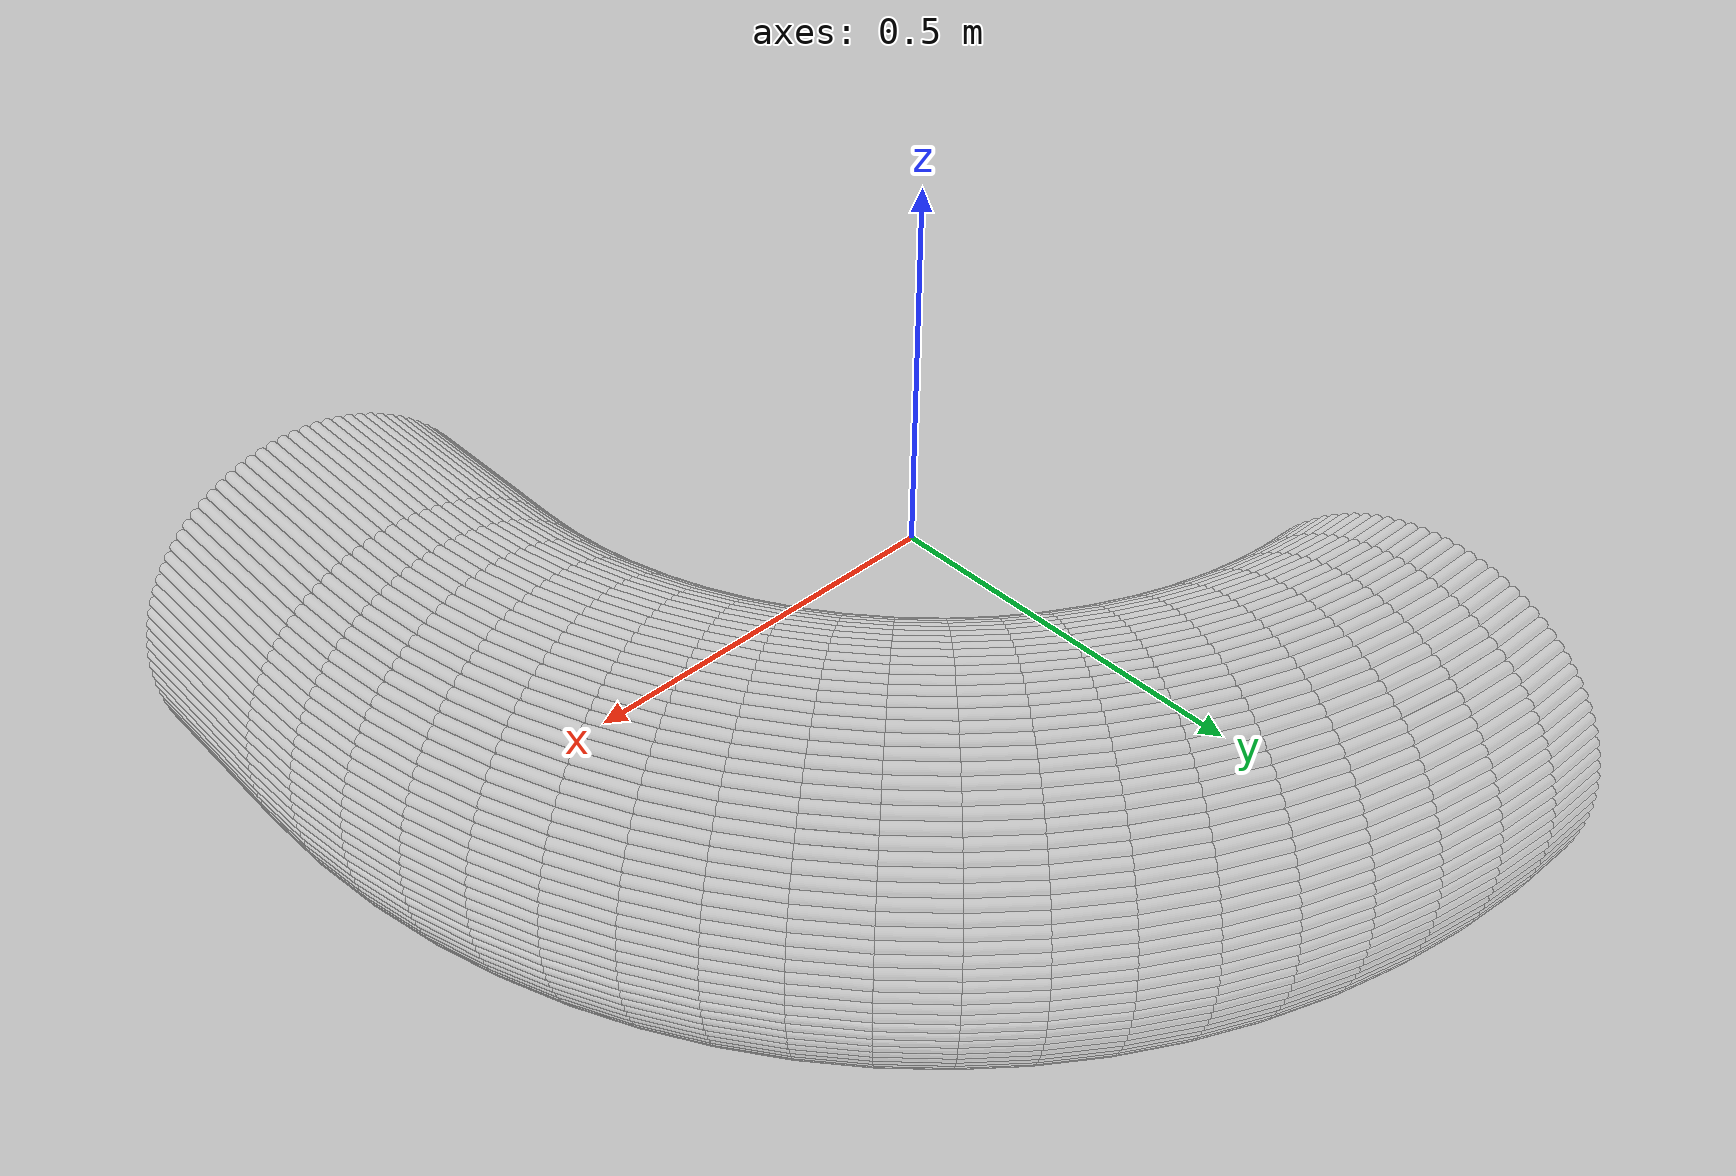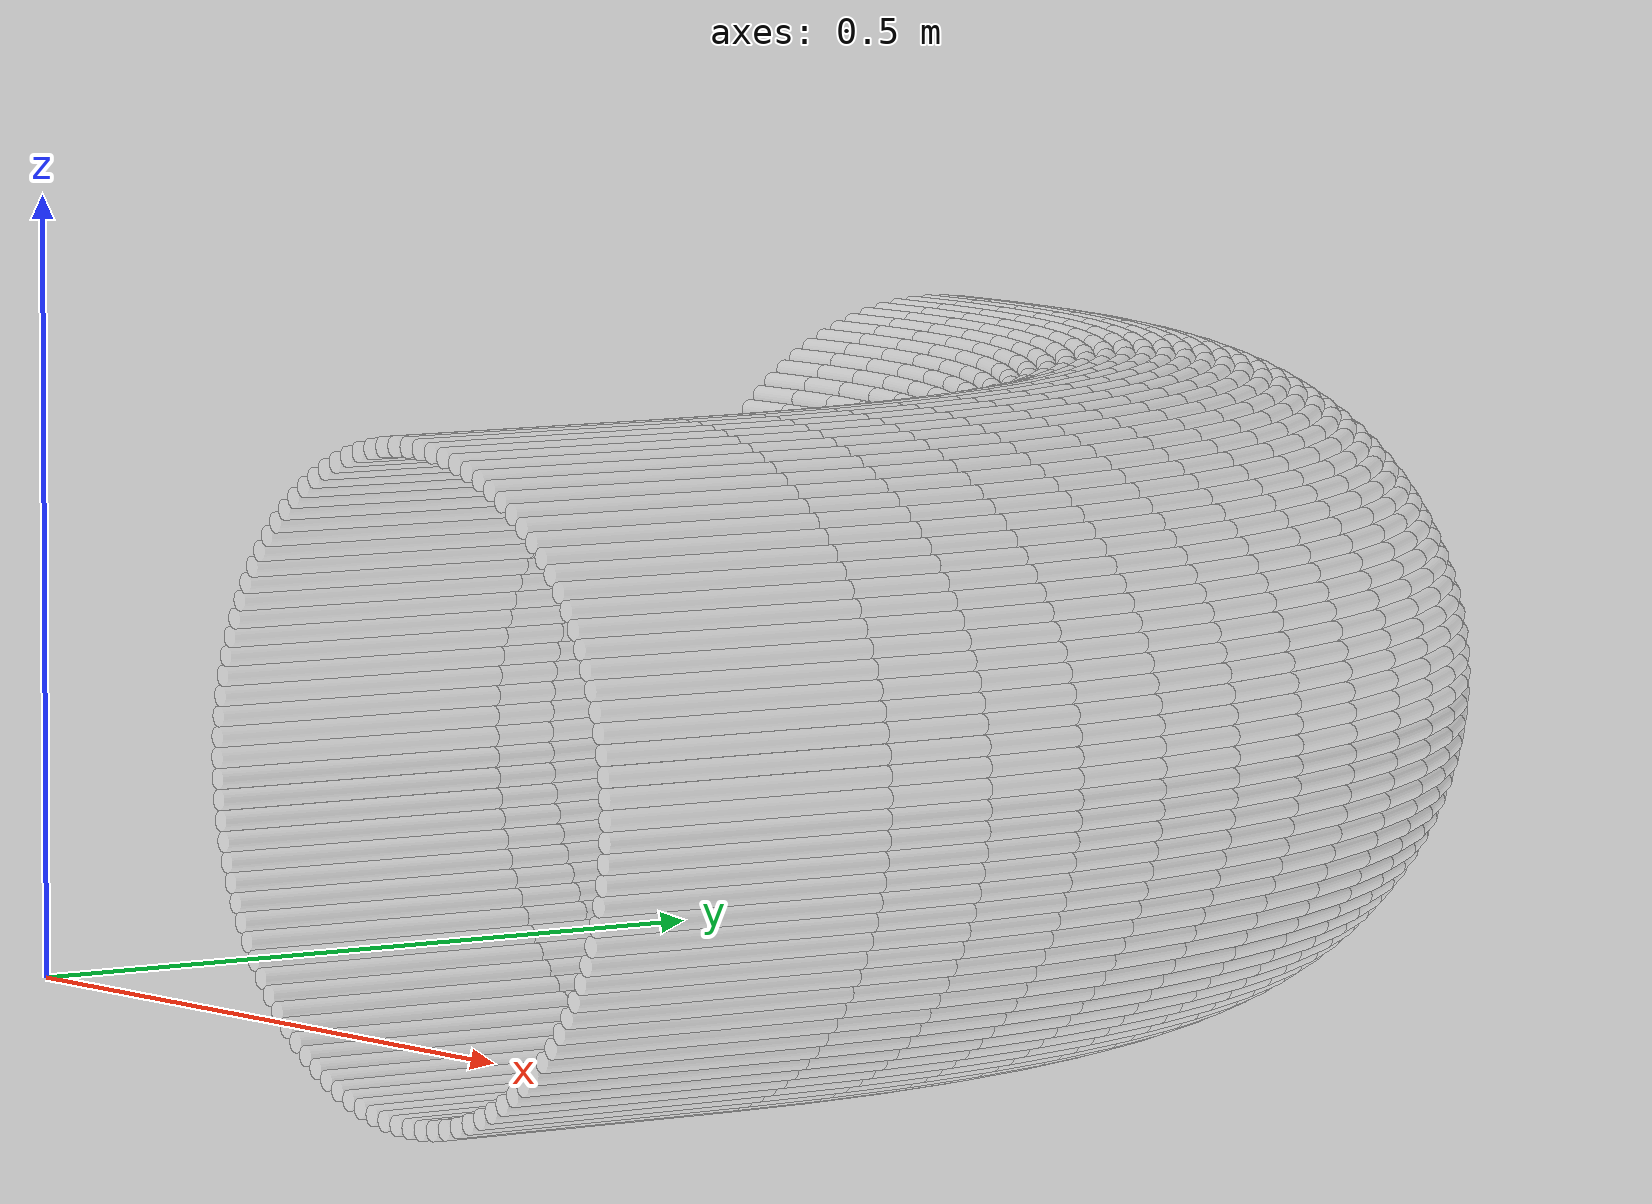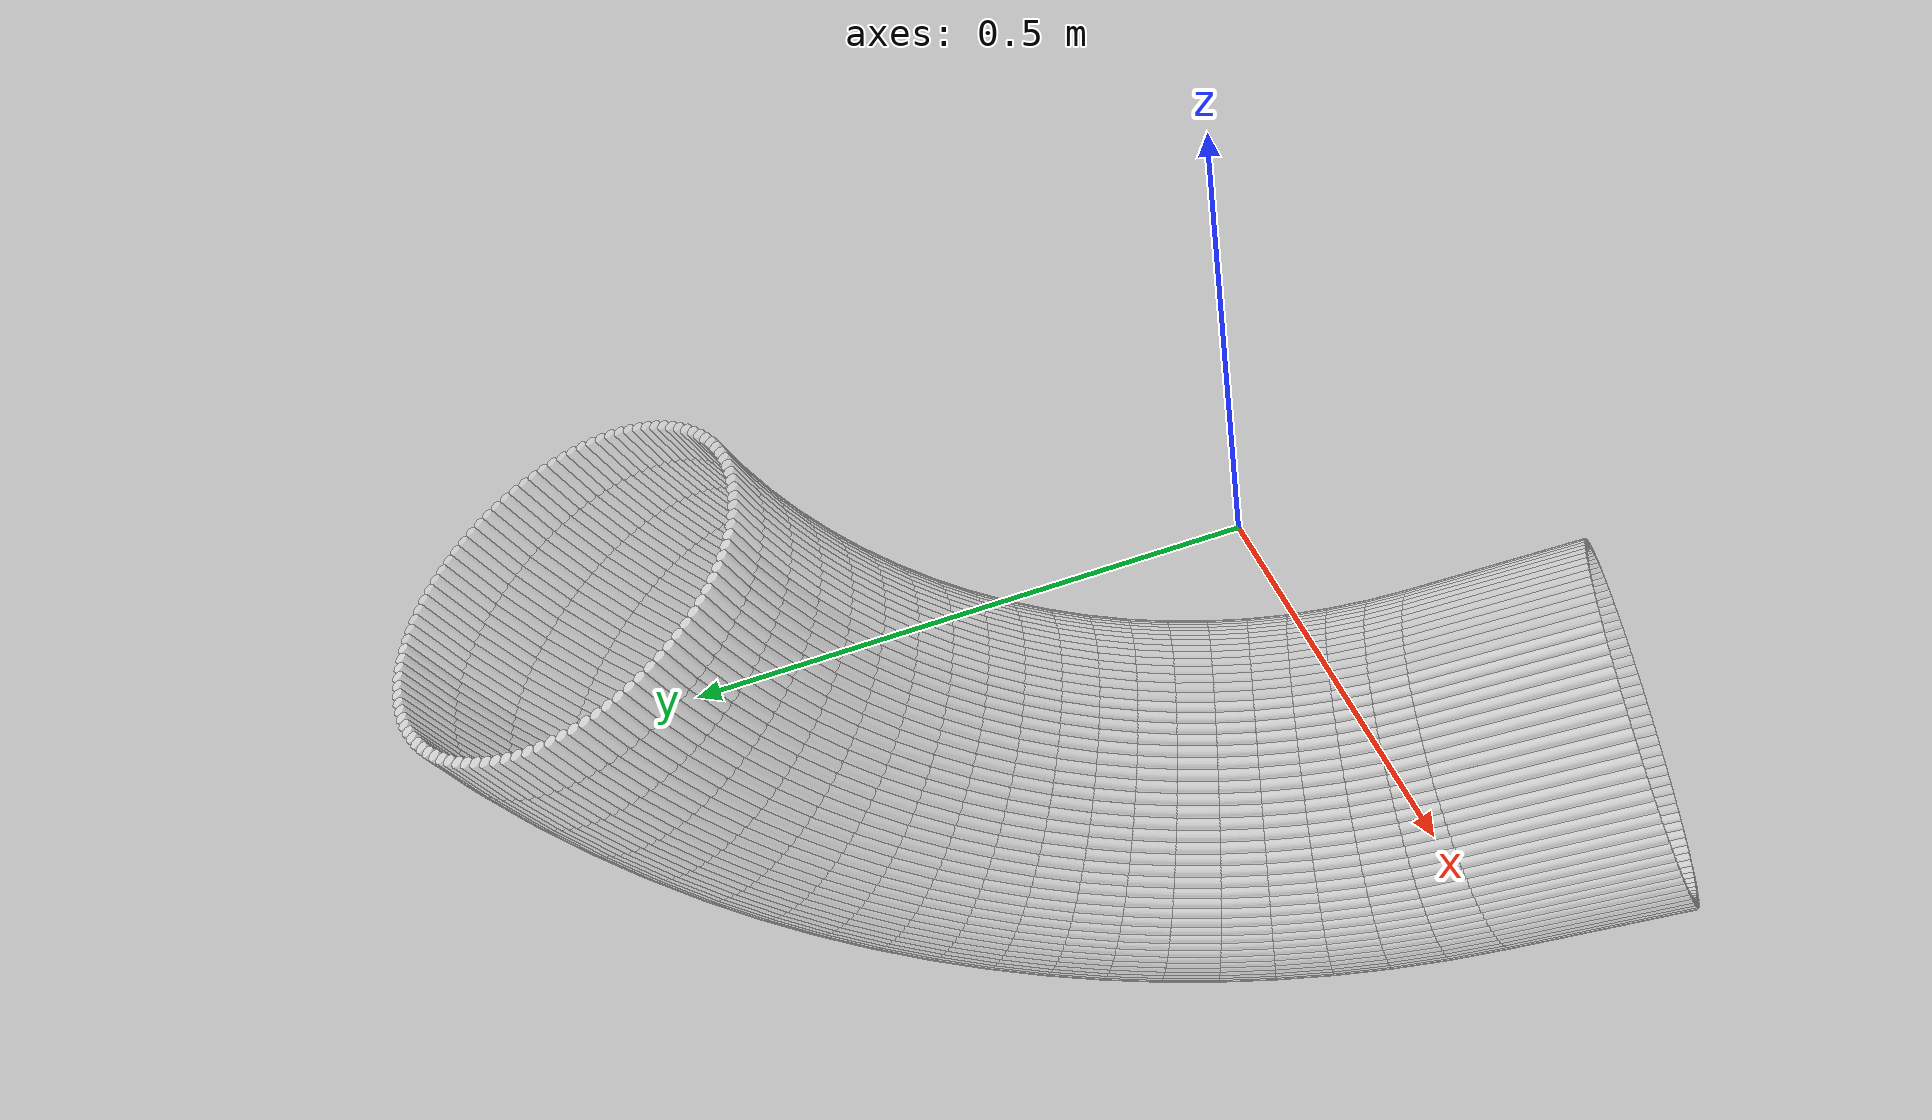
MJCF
<?xml version="1.0" encoding="utf-8"?>
<mujoco>
   <worldbody>
      <geom euler=" 0 10 0 " fromto="0.9 -0.2 0.2 0.9 0 0.2" rgba="1 1 1 0.05"
            size="0.0062822"
            type="cylinder"/>
      <geom euler=" 0 20 0 " fromto="0.89961 -0.2 0.21256 0.89961 0 0.21256"
            rgba="1 1 1 0.05"
            size="0.0062822"
            type="cylinder"/>
      <geom euler=" 0 30 0 " fromto="0.89842 -0.2 0.22507 0.89842 0 0.22507"
            rgba="1 1 1 0.05"
            size="0.0062822"
            type="cylinder"/>
      <geom euler=" 0 40 0 " fromto="0.89646 -0.2 0.23748 0.89646 0 0.23748"
            rgba="1 1 1 0.05"
            size="0.0062822"
            type="cylinder"/>
      <geom euler=" 0 50 0 " fromto="0.89372 -0.2 0.24974 0.89372 0 0.24974"
            rgba="1 1 1 0.05"
            size="0.0062822"
            type="cylinder"/>
      <geom euler=" 0 60 0 " fromto="0.89021 -0.2 0.2618 0.89021 0 0.2618"
            rgba="1 1 1 0.05"
            size="0.0062822"
            type="cylinder"/>
      <geom euler=" 0 70 0 " fromto="0.88596 -0.2 0.27362 0.88596 0 0.27362"
            rgba="1 1 1 0.05"
            size="0.0062822"
            type="cylinder"/>
      <geom euler=" 0 80 0 " fromto="0.88097 -0.2 0.28516 0.88097 0 0.28516"
            rgba="1 1 1 0.05"
            size="0.0062822"
            type="cylinder"/>
      <geom euler=" 0 90 0 " fromto="0.87526 -0.2 0.29635 0.87526 0 0.29635"
            rgba="1 1 1 0.05"
            size="0.0062822"
            type="cylinder"/>
      <geom euler=" 0 100 0 " fromto="0.86887 -0.2 0.30717 0.86887 0 0.30717"
            rgba="1 1 1 0.05"
            size="0.0062822"
            type="cylinder"/>
      <geom euler=" 0 110 0 " fromto="0.8618 -0.2 0.31756 0.8618 0 0.31756"
            rgba="1 1 1 0.05"
            size="0.0062822"
            type="cylinder"/>
      <geom euler=" 0 120 0 " fromto="0.8541 -0.2 0.32748 0.8541 0 0.32748"
            rgba="1 1 1 0.05"
            size="0.0062822"
            type="cylinder"/>
      <geom euler=" 0 130 0 " fromto="0.84579 -0.2 0.33691 0.84579 0 0.33691"
            rgba="1 1 1 0.05"
            size="0.0062822"
            type="cylinder"/>
      <geom euler=" 0 140 0 " fromto="0.83691 -0.2 0.34579 0.83691 0 0.34579"
            rgba="1 1 1 0.05"
            size="0.0062822"
            type="cylinder"/>
      <geom euler=" 0 150 0 " fromto="0.82748 -0.2 0.3541 0.82748 0 0.3541"
            rgba="1 1 1 0.05"
            size="0.0062822"
            type="cylinder"/>
      <geom euler=" 0 160 0 " fromto="0.81756 -0.2 0.3618 0.81756 0 0.3618"
            rgba="1 1 1 0.05"
            size="0.0062822"
            type="cylinder"/>
      <geom euler=" 0 170 0 " fromto="0.80717 -0.2 0.36887 0.80717 0 0.36887"
            rgba="1 1 1 0.05"
            size="0.0062822"
            type="cylinder"/>
      <geom euler=" 0 180 0 " fromto="0.79635 -0.2 0.37526 0.79635 0 0.37526"
            rgba="1 1 1 0.05"
            size="0.0062822"
            type="cylinder"/>
      <geom euler=" 0 190 0 " fromto="0.78516 -0.2 0.38097 0.78516 0 0.38097"
            rgba="1 1 1 0.05"
            size="0.0062822"
            type="cylinder"/>
      <geom euler=" 0 200 0 " fromto="0.77362 -0.2 0.38596 0.77362 0 0.38596"
            rgba="1 1 1 0.05"
            size="0.0062822"
            type="cylinder"/>
      <geom euler=" 0 210 0 " fromto="0.7618 -0.2 0.39021 0.7618 0 0.39021"
            rgba="1 1 1 0.05"
            size="0.0062822"
            type="cylinder"/>
      <geom euler=" 0 220 0 " fromto="0.74974 -0.2 0.39372 0.74974 0 0.39372"
            rgba="1 1 1 0.05"
            size="0.0062822"
            type="cylinder"/>
      <geom euler=" 0 230 0 " fromto="0.73748 -0.2 0.39646 0.73748 0 0.39646"
            rgba="1 1 1 0.05"
            size="0.0062822"
            type="cylinder"/>
      <geom euler=" 0 240 0 " fromto="0.72507 -0.2 0.39842 0.72507 0 0.39842"
            rgba="1 1 1 0.05"
            size="0.0062822"
            type="cylinder"/>
      <geom euler=" 0 250 0 " fromto="0.71256 -0.2 0.39961 0.71256 0 0.39961"
            rgba="1 1 1 0.05"
            size="0.0062822"
            type="cylinder"/>
      <geom euler=" 0 260 0 " fromto="0.7 -0.2 0.4 0.7 0 0.4" rgba="1 1 1 0.05"
            size="0.0062822"
            type="cylinder"/>
      <geom euler=" 0 270 0 " fromto="0.68744 -0.2 0.39961 0.68744 0 0.39961"
            rgba="1 1 1 0.05"
            size="0.0062822"
            type="cylinder"/>
      <geom euler=" 0 280 0 " fromto="0.67493 -0.2 0.39842 0.67493 0 0.39842"
            rgba="1 1 1 0.05"
            size="0.0062822"
            type="cylinder"/>
      <geom euler=" 0 290 0 " fromto="0.66252 -0.2 0.39646 0.66252 0 0.39646"
            rgba="1 1 1 0.05"
            size="0.0062822"
            type="cylinder"/>
      <geom euler=" 0 300 0 " fromto="0.65026 -0.2 0.39372 0.65026 0 0.39372"
            rgba="1 1 1 0.05"
            size="0.0062822"
            type="cylinder"/>
      <geom euler=" 0 310 0 " fromto="0.6382 -0.2 0.39021 0.6382 0 0.39021"
            rgba="1 1 1 0.05"
            size="0.0062822"
            type="cylinder"/>
      <geom euler=" 0 320 0 " fromto="0.62638 -0.2 0.38596 0.62638 0 0.38596"
            rgba="1 1 1 0.05"
            size="0.0062822"
            type="cylinder"/>
      <geom euler=" 0 330 0 " fromto="0.61484 -0.2 0.38097 0.61484 0 0.38097"
            rgba="1 1 1 0.05"
            size="0.0062822"
            type="cylinder"/>
      <geom euler=" 0 340 0 " fromto="0.60365 -0.2 0.37526 0.60365 0 0.37526"
            rgba="1 1 1 0.05"
            size="0.0062822"
            type="cylinder"/>
      <geom euler=" 0 350 0 " fromto="0.59283 -0.2 0.36887 0.59283 0 0.36887"
            rgba="1 1 1 0.05"
            size="0.0062822"
            type="cylinder"/>
      <geom euler=" 0 360 0 " fromto="0.58244 -0.2 0.3618 0.58244 0 0.3618"
            rgba="1 1 1 0.05"
            size="0.0062822"
            type="cylinder"/>
      <geom euler=" 0 370 0 " fromto="0.57252 -0.2 0.3541 0.57252 0 0.3541"
            rgba="1 1 1 0.05"
            size="0.0062822"
            type="cylinder"/>
      <geom euler=" 0 380 0 " fromto="0.56309 -0.2 0.34579 0.56309 0 0.34579"
            rgba="1 1 1 0.05"
            size="0.0062822"
            type="cylinder"/>
      <geom euler=" 0 390 0 " fromto="0.55421 -0.2 0.33691 0.55421 0 0.33691"
            rgba="1 1 1 0.05"
            size="0.0062822"
            type="cylinder"/>
      <geom euler=" 0 400 0 " fromto="0.5459 -0.2 0.32748 0.5459 0 0.32748"
            rgba="1 1 1 0.05"
            size="0.0062822"
            type="cylinder"/>
      <geom euler=" 0 410 0 " fromto="0.5382 -0.2 0.31756 0.5382 0 0.31756"
            rgba="1 1 1 0.05"
            size="0.0062822"
            type="cylinder"/>
      <geom euler=" 0 420 0 " fromto="0.53113 -0.2 0.30717 0.53113 0 0.30717"
            rgba="1 1 1 0.05"
            size="0.0062822"
            type="cylinder"/>
      <geom euler=" 0 430 0 " fromto="0.52474 -0.2 0.29635 0.52474 0 0.29635"
            rgba="1 1 1 0.05"
            size="0.0062822"
            type="cylinder"/>
      <geom euler=" 0 440 0 " fromto="0.51903 -0.2 0.28516 0.51903 0 0.28516"
            rgba="1 1 1 0.05"
            size="0.0062822"
            type="cylinder"/>
      <geom euler=" 0 450 0 " fromto="0.51404 -0.2 0.27362 0.51404 0 0.27362"
            rgba="1 1 1 0.05"
            size="0.0062822"
            type="cylinder"/>
      <geom euler=" 0 460 0 " fromto="0.50979 -0.2 0.2618 0.50979 0 0.2618"
            rgba="1 1 1 0.05"
            size="0.0062822"
            type="cylinder"/>
      <geom euler=" 0 470 0 " fromto="0.50628 -0.2 0.24974 0.50628 0 0.24974"
            rgba="1 1 1 0.05"
            size="0.0062822"
            type="cylinder"/>
      <geom euler=" 0 480 0 " fromto="0.50354 -0.2 0.23748 0.50354 0 0.23748"
            rgba="1 1 1 0.05"
            size="0.0062822"
            type="cylinder"/>
      <geom euler=" 0 490 0 " fromto="0.50158 -0.2 0.22507 0.50158 0 0.22507"
            rgba="1 1 1 0.05"
            size="0.0062822"
            type="cylinder"/>
      <geom euler=" 0 500 0 " fromto="0.50039 -0.2 0.21256 0.50039 0 0.21256"
            rgba="1 1 1 0.05"
            size="0.0062822"
            type="cylinder"/>
      <geom euler=" 0 510 0 " fromto="0.5 -0.2 0.2 0.5 0 0.2" rgba="1 1 1 0.05"
            size="0.0062822"
            type="cylinder"/>
      <geom euler=" 0 520 0 " fromto="0.50039 -0.2 0.18744 0.50039 0 0.18744"
            rgba="1 1 1 0.35"
            size="0.0062822"
            type="cylinder"/>
      <geom euler=" 0 530 0 " fromto="0.50158 -0.2 0.17493 0.50158 0 0.17493"
            rgba="1 1 1 0.35"
            size="0.0062822"
            type="cylinder"/>
      <geom euler=" 0 540 0 " fromto="0.50354 -0.2 0.16252 0.50354 0 0.16252"
            rgba="1 1 1 0.35"
            size="0.0062822"
            type="cylinder"/>
      <geom euler=" 0 550 0 " fromto="0.50628 -0.2 0.15026 0.50628 0 0.15026"
            rgba="1 1 1 0.35"
            size="0.0062822"
            type="cylinder"/>
      <geom euler=" 0 560 0 " fromto="0.50979 -0.2 0.1382 0.50979 0 0.1382"
            rgba="1 1 1 0.35"
            size="0.0062822"
            type="cylinder"/>
      <geom euler=" 0 570 0 " fromto="0.51404 -0.2 0.12638 0.51404 0 0.12638"
            rgba="1 1 1 0.35"
            size="0.0062822"
            type="cylinder"/>
      <geom euler=" 0 580 0 " fromto="0.51903 -0.2 0.11484 0.51903 0 0.11484"
            rgba="1 1 1 0.35"
            size="0.0062822"
            type="cylinder"/>
      <geom euler=" 0 590 0 " fromto="0.52474 -0.2 0.10365 0.52474 0 0.10365"
            rgba="1 1 1 0.35"
            size="0.0062822"
            type="cylinder"/>
      <geom euler=" 0 600 0 " fromto="0.53113 -0.2 0.092835 0.53113 0 0.092835"
            rgba="1 1 1 0.35"
            size="0.0062822"
            type="cylinder"/>
      <geom euler=" 0 610 0 " fromto="0.5382 -0.2 0.082443 0.5382 0 0.082443"
            rgba="1 1 1 0.35"
            size="0.0062822"
            type="cylinder"/>
      <geom euler=" 0 620 0 " fromto="0.5459 -0.2 0.072515 0.5459 0 0.072515"
            rgba="1 1 1 0.35"
            size="0.0062822"
            type="cylinder"/>
      <geom euler=" 0 630 0 " fromto="0.55421 -0.2 0.063091 0.55421 0 0.063091"
            rgba="1 1 1 0.35"
            size="0.0062822"
            type="cylinder"/>
      <geom euler=" 0 640 0 " fromto="0.56309 -0.2 0.054206 0.56309 0 0.054206"
            rgba="1 1 1 0.35"
            size="0.0062822"
            type="cylinder"/>
      <geom euler=" 0 650 0 " fromto="0.57252 -0.2 0.045897 0.57252 0 0.045897"
            rgba="1 1 1 0.35"
            size="0.0062822"
            type="cylinder"/>
      <geom euler=" 0 660 0 " fromto="0.58244 -0.2 0.038197 0.58244 0 0.038197"
            rgba="1 1 1 0.35"
            size="0.0062822"
            type="cylinder"/>
      <geom euler=" 0 670 0 " fromto="0.59283 -0.2 0.031134 0.59283 0 0.031134"
            rgba="1 1 1 0.35"
            size="0.0062822"
            type="cylinder"/>
      <geom euler=" 0 680 0 " fromto="0.60365 -0.2 0.024739 0.60365 0 0.024739"
            rgba="1 1 1 0.35"
            size="0.0062822"
            type="cylinder"/>
      <geom euler=" 0 690 0 " fromto="0.61484 -0.2 0.019035 0.61484 0 0.019035"
            rgba="1 1 1 0.35"
            size="0.0062822"
            type="cylinder"/>
      <geom euler=" 0 700 0 " fromto="0.62638 -0.2 0.014045 0.62638 0 0.014045"
            rgba="1 1 1 0.35"
            size="0.0062822"
            type="cylinder"/>
      <geom euler=" 0 710 0 " fromto="0.6382 -0.2 0.0097887 0.6382 0 0.0097887"
            rgba="1 1 1 0.35"
            size="0.0062822"
            type="cylinder"/>
      <geom euler=" 0 720 0 " fromto="0.65026 -0.2 0.0062834 0.65026 0 0.0062834"
            rgba="1 1 1 0.35"
            size="0.0062822"
            type="cylinder"/>
      <geom euler=" 0 730 0 " fromto="0.66252 -0.2 0.0035425 0.66252 0 0.0035425"
            rgba="1 1 1 0.35"
            size="0.0062822"
            type="cylinder"/>
      <geom euler=" 0 740 0 " fromto="0.67493 -0.2 0.0015771 0.67493 0 0.0015771"
            rgba="1 1 1 0.35"
            size="0.0062822"
            type="cylinder"/>
      <geom euler=" 0 750 0 " fromto="0.68744 -0.2 0.00039465 0.68744 0 0.00039465"
            rgba="1 1 1 0.35"
            size="0.0062822"
            type="cylinder"/>
      <geom euler=" 0 760 0 " fromto="0.7 -0.2 0 0.7 0 0" rgba="1 1 1 0.35"
            size="0.0062822"
            type="cylinder"/>
      <geom euler=" 0 770 0 " fromto="0.71256 -0.2 0.00039465 0.71256 0 0.00039465"
            rgba="1 1 1 0.35"
            size="0.0062822"
            type="cylinder"/>
      <geom euler=" 0 780 0 " fromto="0.72507 -0.2 0.0015771 0.72507 0 0.0015771"
            rgba="1 1 1 0.35"
            size="0.0062822"
            type="cylinder"/>
      <geom euler=" 0 790 0 " fromto="0.73748 -0.2 0.0035425 0.73748 0 0.0035425"
            rgba="1 1 1 0.35"
            size="0.0062822"
            type="cylinder"/>
      <geom euler=" 0 800 0 " fromto="0.74974 -0.2 0.0062834 0.74974 0 0.0062834"
            rgba="1 1 1 0.35"
            size="0.0062822"
            type="cylinder"/>
      <geom euler=" 0 810 0 " fromto="0.7618 -0.2 0.0097887 0.7618 0 0.0097887"
            rgba="1 1 1 0.35"
            size="0.0062822"
            type="cylinder"/>
      <geom euler=" 0 820 0 " fromto="0.77362 -0.2 0.014045 0.77362 0 0.014045"
            rgba="1 1 1 0.35"
            size="0.0062822"
            type="cylinder"/>
      <geom euler=" 0 830 0 " fromto="0.78516 -0.2 0.019035 0.78516 0 0.019035"
            rgba="1 1 1 0.35"
            size="0.0062822"
            type="cylinder"/>
      <geom euler=" 0 840 0 " fromto="0.79635 -0.2 0.024739 0.79635 0 0.024739"
            rgba="1 1 1 0.35"
            size="0.0062822"
            type="cylinder"/>
      <geom euler=" 0 850 0 " fromto="0.80717 -0.2 0.031134 0.80717 0 0.031134"
            rgba="1 1 1 0.35"
            size="0.0062822"
            type="cylinder"/>
      <geom euler=" 0 860 0 " fromto="0.81756 -0.2 0.038197 0.81756 0 0.038197"
            rgba="1 1 1 0.35"
            size="0.0062822"
            type="cylinder"/>
      <geom euler=" 0 870 0 " fromto="0.82748 -0.2 0.045897 0.82748 0 0.045897"
            rgba="1 1 1 0.35"
            size="0.0062822"
            type="cylinder"/>
      <geom euler=" 0 880 0 " fromto="0.83691 -0.2 0.054206 0.83691 0 0.054206"
            rgba="1 1 1 0.35"
            size="0.0062822"
            type="cylinder"/>
      <geom euler=" 0 890 0 " fromto="0.84579 -0.2 0.063091 0.84579 0 0.063091"
            rgba="1 1 1 0.35"
            size="0.0062822"
            type="cylinder"/>
      <geom euler=" 0 900 0 " fromto="0.8541 -0.2 0.072515 0.8541 0 0.072515"
            rgba="1 1 1 0.35"
            size="0.0062822"
            type="cylinder"/>
      <geom euler=" 0 910 0 " fromto="0.8618 -0.2 0.082443 0.8618 0 0.082443"
            rgba="1 1 1 0.35"
            size="0.0062822"
            type="cylinder"/>
      <geom euler=" 0 920 0 " fromto="0.86887 -0.2 0.092835 0.86887 0 0.092835"
            rgba="1 1 1 0.35"
            size="0.0062822"
            type="cylinder"/>
      <geom euler=" 0 930 0 " fromto="0.87526 -0.2 0.10365 0.87526 0 0.10365"
            rgba="1 1 1 0.35"
            size="0.0062822"
            type="cylinder"/>
      <geom euler=" 0 940 0 " fromto="0.88097 -0.2 0.11484 0.88097 0 0.11484"
            rgba="1 1 1 0.35"
            size="0.0062822"
            type="cylinder"/>
      <geom euler=" 0 950 0 " fromto="0.88596 -0.2 0.12638 0.88596 0 0.12638"
            rgba="1 1 1 0.35"
            size="0.0062822"
            type="cylinder"/>
      <geom euler=" 0 960 0 " fromto="0.89021 -0.2 0.1382 0.89021 0 0.1382"
            rgba="1 1 1 0.35"
            size="0.0062822"
            type="cylinder"/>
      <geom euler=" 0 970 0 " fromto="0.89372 -0.2 0.15026 0.89372 0 0.15026"
            rgba="1 1 1 0.35"
            size="0.0062822"
            type="cylinder"/>
      <geom euler=" 0 980 0 " fromto="0.89646 -0.2 0.16252 0.89646 0 0.16252"
            rgba="1 1 1 0.35"
            size="0.0062822"
            type="cylinder"/>
      <geom euler=" 0 990 0 " fromto="0.89842 -0.2 0.17493 0.89842 0 0.17493"
            rgba="1 1 1 0.35"
            size="0.0062822"
            type="cylinder"/>
      <geom euler=" 0 1000 0 " fromto="0.89961 -0.2 0.18744 0.89961 0 0.18744"
            rgba="1 1 1 0.35"
            size="0.0062822"
            type="cylinder"/>
      <geom euler=" 0 10 0 " fromto="0.9 0 0.2 0.89693 0.074321 0.2" rgba="1 1 1 0.05"
            size="0.0062822"
            type="cylinder"/>
      <geom euler=" 0 20 0 " fromto="0.89961 0 0.21256 0.89653 0.074289 0.21256"
            rgba="1 1 1 0.05"
            size="0.0062822"
            type="cylinder"/>
      <geom euler=" 0 30 0 " fromto="0.89842 0 0.22507 0.89535 0.074191 0.22507"
            rgba="1 1 1 0.05"
            size="0.0062822"
            type="cylinder"/>
      <geom euler=" 0 40 0 " fromto="0.89646 0 0.23748 0.8934 0.074029 0.23748"
            rgba="1 1 1 0.05"
            size="0.0062822"
            type="cylinder"/>
      <geom euler=" 0 50 0 " fromto="0.89372 0 0.24974 0.89066 0.073803 0.24974"
            rgba="1 1 1 0.05"
            size="0.0062822"
            type="cylinder"/>
      <geom euler=" 0 60 0 " fromto="0.89021 0 0.2618 0.88717 0.073513 0.2618"
            rgba="1 1 1 0.05"
            size="0.0062822"
            type="cylinder"/>
      <geom euler=" 0 70 0 " fromto="0.88596 0 0.27362 0.88293 0.073162 0.27362"
            rgba="1 1 1 0.05"
            size="0.0062822"
            type="cylinder"/>
      <geom euler=" 0 80 0 " fromto="0.88097 0 0.28516 0.87796 0.07275 0.28516"
            rgba="1 1 1 0.05"
            size="0.0062822"
            type="cylinder"/>
      <geom euler=" 0 90 0 " fromto="0.87526 0 0.29635 0.87227 0.072279 0.29635"
            rgba="1 1 1 0.05"
            size="0.0062822"
            type="cylinder"/>
      <geom euler=" 0 100 0 " fromto="0.86887 0 0.30717 0.8659 0.07175 0.30717"
            rgba="1 1 1 0.05"
            size="0.0062822"
            type="cylinder"/>
      <geom euler=" 0 110 0 " fromto="0.8618 0 0.31756 0.85886 0.071167 0.31756"
            rgba="1 1 1 0.05"
            size="0.0062822"
            type="cylinder"/>
      <geom euler=" 0 120 0 " fromto="0.8541 0 0.32748 0.85119 0.070531 0.32748"
            rgba="1 1 1 0.05"
            size="0.0062822"
            type="cylinder"/>
      <geom euler=" 0 130 0 " fromto="0.84579 0 0.33691 0.8429 0.069845 0.33691"
            rgba="1 1 1 0.05"
            size="0.0062822"
            type="cylinder"/>
      <geom euler=" 0 140 0 " fromto="0.83691 0 0.34579 0.83405 0.069111 0.34579"
            rgba="1 1 1 0.05"
            size="0.0062822"
            type="cylinder"/>
      <geom euler=" 0 150 0 " fromto="0.82748 0 0.3541 0.82466 0.068333 0.3541"
            rgba="1 1 1 0.05"
            size="0.0062822"
            type="cylinder"/>
      <geom euler=" 0 160 0 " fromto="0.81756 0 0.3618 0.81476 0.067513 0.3618"
            rgba="1 1 1 0.05"
            size="0.0062822"
            type="cylinder"/>
      <geom euler=" 0 170 0 " fromto="0.80717 0 0.36887 0.80441 0.066655 0.36887"
            rgba="1 1 1 0.05"
            size="0.0062822"
            type="cylinder"/>
      <geom euler=" 0 180 0 " fromto="0.79635 0 0.37526 0.79363 0.065762 0.37526"
            rgba="1 1 1 0.05"
            size="0.0062822"
            type="cylinder"/>
      <geom euler=" 0 190 0 " fromto="0.78516 0 0.38097 0.78247 0.064838 0.38097"
            rgba="1 1 1 0.05"
            size="0.0062822"
            type="cylinder"/>
      <geom euler=" 0 200 0 " fromto="0.77362 0 0.38596 0.77098 0.063885 0.38596"
            rgba="1 1 1 0.05"
            size="0.0062822"
            type="cylinder"/>
      <geom euler=" 0 210 0 " fromto="0.7618 0 0.39021 0.7592 0.062909 0.39021"
            rgba="1 1 1 0.05"
            size="0.0062822"
            type="cylinder"/>
      <geom euler=" 0 220 0 " fromto="0.74974 0 0.39372 0.74718 0.061913 0.39372"
            rgba="1 1 1 0.05"
            size="0.0062822"
            type="cylinder"/>
      <geom euler=" 0 230 0 " fromto="0.73748 0 0.39646 0.73496 0.0609 0.39646"
            rgba="1 1 1 0.05"
            size="0.0062822"
            type="cylinder"/>
      <geom euler=" 0 240 0 " fromto="0.72507 0 0.39842 0.72259 0.059876 0.39842"
            rgba="1 1 1 0.05"
            size="0.0062822"
            type="cylinder"/>
      <geom euler=" 0 250 0 " fromto="0.71256 0 0.39961 0.71012 0.058843 0.39961"
            rgba="1 1 1 0.05"
            size="0.0062822"
            type="cylinder"/>
      <geom euler=" 0 260 0 " fromto="0.7 0 0.4 0.69761 0.057806 0.4" rgba="1 1 1 0.05"
            size="0.0062822"
            type="cylinder"/>
      <geom euler=" 0 270 0 " fromto="0.68744 0 0.39961 0.68509 0.056769 0.39961"
            rgba="1 1 1 0.05"
            size="0.0062822"
            type="cylinder"/>
      <geom euler=" 0 280 0 " fromto="0.67493 0 0.39842 0.67263 0.055736 0.39842"
            rgba="1 1 1 0.05"
            size="0.0062822"
            type="cylinder"/>
      <geom euler=" 0 290 0 " fromto="0.66252 0 0.39646 0.66026 0.054711 0.39646"
            rgba="1 1 1 0.05"
            size="0.0062822"
            type="cylinder"/>
      <geom euler=" 0 300 0 " fromto="0.65026 0 0.39372 0.64804 0.053698 0.39372"
            rgba="1 1 1 0.05"
            size="0.0062822"
            type="cylinder"/>
      <geom euler=" 0 310 0 " fromto="0.6382 0 0.39021 0.63602 0.052702 0.39021"
            rgba="1 1 1 0.05"
            size="0.0062822"
            type="cylinder"/>
      <geom euler=" 0 320 0 " fromto="0.62638 0 0.38596 0.62424 0.051726 0.38596"
            rgba="1 1 1 0.05"
            size="0.0062822"
            type="cylinder"/>
      <geom euler=" 0 330 0 " fromto="0.61484 0 0.38097 0.61274 0.050773 0.38097"
            rgba="1 1 1 0.05"
            size="0.0062822"
            type="cylinder"/>
      <geom euler=" 0 340 0 " fromto="0.60365 0 0.37526 0.60159 0.049849 0.37526"
            rgba="1 1 1 0.05"
            size="0.0062822"
            type="cylinder"/>
      <geom euler=" 0 350 0 " fromto="0.59283 0 0.36887 0.59081 0.048956 0.36887"
            rgba="1 1 1 0.05"
            size="0.0062822"
            type="cylinder"/>
      <geom euler=" 0 360 0 " fromto="0.58244 0 0.3618 0.58045 0.048098 0.3618"
            rgba="1 1 1 0.05"
            size="0.0062822"
            type="cylinder"/>
      <geom euler=" 0 370 0 " fromto="0.57252 0 0.3541 0.57056 0.047278 0.3541"
            rgba="1 1 1 0.05"
            size="0.0062822"
            type="cylinder"/>
      <geom euler=" 0 380 0 " fromto="0.56309 0 0.34579 0.56117 0.0465 0.34579"
            rgba="1 1 1 0.05"
            size="0.0062822"
            type="cylinder"/>
      <geom euler=" 0 390 0 " fromto="0.55421 0 0.33691 0.55231 0.045766 0.33691"
            rgba="1 1 1 0.05"
            size="0.0062822"
            type="cylinder"/>
      <geom euler=" 0 400 0 " fromto="0.5459 0 0.32748 0.54403 0.04508 0.32748"
            rgba="1 1 1 0.05"
            size="0.0062822"
            type="cylinder"/>
      <geom euler=" 0 410 0 " fromto="0.5382 0 0.31756 0.53636 0.044444 0.31756"
            rgba="1 1 1 0.05"
            size="0.0062822"
            type="cylinder"/>
      <geom euler=" 0 420 0 " fromto="0.53113 0 0.30717 0.52932 0.043861 0.30717"
            rgba="1 1 1 0.05"
            size="0.0062822"
            type="cylinder"/>
      <geom euler=" 0 430 0 " fromto="0.52474 0 0.29635 0.52295 0.043333 0.29635"
            rgba="1 1 1 0.05"
            size="0.0062822"
            type="cylinder"/>
      <geom euler=" 0 440 0 " fromto="0.51903 0 0.28516 0.51726 0.042862 0.28516"
            rgba="1 1 1 0.05"
            size="0.0062822"
            type="cylinder"/>
      <geom euler=" 0 450 0 " fromto="0.51404 0 0.27362 0.51229 0.042449 0.27362"
            rgba="1 1 1 0.05"
            size="0.0062822"
            type="cylinder"/>
      <geom euler=" 0 460 0 " fromto="0.50979 0 0.2618 0.50805 0.042098 0.2618"
            rgba="1 1 1 0.05"
            size="0.0062822"
            type="cylinder"/>
      <geom euler=" 0 470 0 " fromto="0.50628 0 0.24974 0.50455 0.041809 0.24974"
            rgba="1 1 1 0.05"
            size="0.0062822"
            type="cylinder"/>
      <geom euler=" 0 480 0 " fromto="0.50354 0 0.23748 0.50182 0.041582 0.23748"
            rgba="1 1 1 0.05"
            size="0.0062822"
            type="cylinder"/>
      <geom euler=" 0 490 0 " fromto="0.50158 0 0.22507 0.49986 0.04142 0.22507"
            rgba="1 1 1 0.05"
            size="0.0062822"
            type="cylinder"/>
      <geom euler=" 0 500 0 " fromto="0.50039 0 0.21256 0.49869 0.041322 0.21256"
            rgba="1 1 1 0.05"
            size="0.0062822"
            type="cylinder"/>
      <geom euler=" 0 510 0 " fromto="0.5 0 0.2 0.49829 0.04129 0.2" rgba="1 1 1 0.05"
            size="0.0062822"
            type="cylinder"/>
      <geom euler=" 0 520 0 " fromto="0.50039 0 0.18744 0.49869 0.041322 0.18744"
            rgba="1 1 1 0.35"
            size="0.0062822"
            type="cylinder"/>
      <geom euler=" 0 530 0 " fromto="0.50158 0 0.17493 0.49986 0.04142 0.17493"
            rgba="1 1 1 0.35"
            size="0.0062822"
            type="cylinder"/>
      <geom euler=" 0 540 0 " fromto="0.50354 0 0.16252 0.50182 0.041582 0.16252"
            rgba="1 1 1 0.35"
            size="0.0062822"
            type="cylinder"/>
      <geom euler=" 0 550 0 " fromto="0.50628 0 0.15026 0.50455 0.041809 0.15026"
            rgba="1 1 1 0.35"
            size="0.0062822"
            type="cylinder"/>
      <geom euler=" 0 560 0 " fromto="0.50979 0 0.1382 0.50805 0.042098 0.1382"
            rgba="1 1 1 0.35"
            size="0.0062822"
            type="cylinder"/>
      <geom euler=" 0 570 0 " fromto="0.51404 0 0.12638 0.51229 0.042449 0.12638"
            rgba="1 1 1 0.35"
            size="0.0062822"
            type="cylinder"/>
      <geom euler=" 0 580 0 " fromto="0.51903 0 0.11484 0.51726 0.042862 0.11484"
            rgba="1 1 1 0.35"
            size="0.0062822"
            type="cylinder"/>
      <geom euler=" 0 590 0 " fromto="0.52474 0 0.10365 0.52295 0.043333 0.10365"
            rgba="1 1 1 0.35"
            size="0.0062822"
            type="cylinder"/>
      <geom euler=" 0 600 0 " fromto="0.53113 0 0.092835 0.52932 0.043861 0.092835"
            rgba="1 1 1 0.35"
            size="0.0062822"
            type="cylinder"/>
      <geom euler=" 0 610 0 " fromto="0.5382 0 0.082443 0.53636 0.044444 0.082443"
            rgba="1 1 1 0.35"
            size="0.0062822"
            type="cylinder"/>
      <geom euler=" 0 620 0 " fromto="0.5459 0 0.072515 0.54403 0.04508 0.072515"
            rgba="1 1 1 0.35"
            size="0.0062822"
            type="cylinder"/>
      <geom euler=" 0 630 0 " fromto="0.55421 0 0.063091 0.55231 0.045766 0.063091"
            rgba="1 1 1 0.35"
            size="0.0062822"
            type="cylinder"/>
      <geom euler=" 0 640 0 " fromto="0.56309 0 0.054206 0.56117 0.0465 0.054206"
            rgba="1 1 1 0.35"
            size="0.0062822"
            type="cylinder"/>
      <geom euler=" 0 650 0 " fromto="0.57252 0 0.045897 0.57056 0.047278 0.045897"
            rgba="1 1 1 0.35"
            size="0.0062822"
            type="cylinder"/>
      <geom euler=" 0 660 0 " fromto="0.58244 0 0.038197 0.58045 0.048098 0.038197"
            rgba="1 1 1 0.35"
            size="0.0062822"
            type="cylinder"/>
      <geom euler=" 0 670 0 " fromto="0.59283 0 0.031134 0.59081 0.048956 0.031134"
            rgba="1 1 1 0.35"
            size="0.0062822"
            type="cylinder"/>
      <geom euler=" 0 680 0 " fromto="0.60365 0 0.024739 0.60159 0.049849 0.024739"
            rgba="1 1 1 0.35"
            size="0.0062822"
            type="cylinder"/>
      <geom euler=" 0 690 0 " fromto="0.61484 0 0.019035 0.61274 0.050773 0.019035"
            rgba="1 1 1 0.35"
            size="0.0062822"
            type="cylinder"/>
      <geom euler=" 0 700 0 " fromto="0.62638 0 0.014045 0.62424 0.051726 0.014045"
            rgba="1 1 1 0.35"
            size="0.0062822"
            type="cylinder"/>
      <geom euler=" 0 710 0 " fromto="0.6382 0 0.0097887 0.63602 0.052702 0.0097887"
            rgba="1 1 1 0.35"
            size="0.0062822"
            type="cylinder"/>
      <geom euler=" 0 720 0 " fromto="0.65026 0 0.0062834 0.64804 0.053698 0.0062834"
            rgba="1 1 1 0.35"
            size="0.0062822"
            type="cylinder"/>
      <geom euler=" 0 730 0 " fromto="0.66252 0 0.0035425 0.66026 0.054711 0.0035425"
            rgba="1 1 1 0.35"
            size="0.0062822"
            type="cylinder"/>
      <geom euler=" 0 740 0 " fromto="0.67493 0 0.0015771 0.67263 0.055736 0.0015771"
            rgba="1 1 1 0.35"
            size="0.0062822"
            type="cylinder"/>
      <geom euler=" 0 750 0 " fromto="0.68744 0 0.00039465 0.68509 0.056769 0.00039465"
            rgba="1 1 1 0.35"
            size="0.0062822"
            type="cylinder"/>
      <geom euler=" 0 760 0 " fromto="0.7 0 0 0.69761 0.057806 0" rgba="1 1 1 0.35"
            size="0.0062822"
            type="cylinder"/>
      <geom euler=" 0 770 0 " fromto="0.71256 0 0.00039465 0.71012 0.058843 0.00039465"
            rgba="1 1 1 0.35"
            size="0.0062822"
            type="cylinder"/>
      <geom euler=" 0 780 0 " fromto="0.72507 0 0.0015771 0.72259 0.059876 0.0015771"
            rgba="1 1 1 0.35"
            size="0.0062822"
            type="cylinder"/>
      <geom euler=" 0 790 0 " fromto="0.73748 0 0.0035425 0.73496 0.0609 0.0035425"
            rgba="1 1 1 0.35"
            size="0.0062822"
            type="cylinder"/>
      <geom euler=" 0 800 0 " fromto="0.74974 0 0.0062834 0.74718 0.061913 0.0062834"
            rgba="1 1 1 0.35"
            size="0.0062822"
            type="cylinder"/>
      <geom euler=" 0 810 0 " fromto="0.7618 0 0.0097887 0.7592 0.062909 0.0097887"
            rgba="1 1 1 0.35"
            size="0.0062822"
            type="cylinder"/>
      <geom euler=" 0 820 0 " fromto="0.77362 0 0.014045 0.77098 0.063885 0.014045"
            rgba="1 1 1 0.35"
            size="0.0062822"
            type="cylinder"/>
      <geom euler=" 0 830 0 " fromto="0.78516 0 0.019035 0.78247 0.064838 0.019035"
            rgba="1 1 1 0.35"
            size="0.0062822"
            type="cylinder"/>
      <geom euler=" 0 840 0 " fromto="0.79635 0 0.024739 0.79363 0.065762 0.024739"
            rgba="1 1 1 0.35"
            size="0.0062822"
            type="cylinder"/>
      <geom euler=" 0 850 0 " fromto="0.80717 0 0.031134 0.80441 0.066655 0.031134"
            rgba="1 1 1 0.35"
            size="0.0062822"
            type="cylinder"/>
      <geom euler=" 0 860 0 " fromto="0.81756 0 0.038197 0.81476 0.067513 0.038197"
            rgba="1 1 1 0.35"
            size="0.0062822"
            type="cylinder"/>
      <geom euler=" 0 870 0 " fromto="0.82748 0 0.045897 0.82466 0.068333 0.045897"
            rgba="1 1 1 0.35"
            size="0.0062822"
            type="cylinder"/>
      <geom euler=" 0 880 0 " fromto="0.83691 0 0.054206 0.83405 0.069111 0.054206"
            rgba="1 1 1 0.35"
            size="0.0062822"
            type="cylinder"/>
      <geom euler=" 0 890 0 " fromto="0.84579 0 0.063091 0.8429 0.069845 0.063091"
            rgba="1 1 1 0.35"
            size="0.0062822"
            type="cylinder"/>
      <geom euler=" 0 900 0 " fromto="0.8541 0 0.072515 0.85119 0.070531 0.072515"
            rgba="1 1 1 0.35"
            size="0.0062822"
            type="cylinder"/>
      <geom euler=" 0 910 0 " fromto="0.8618 0 0.082443 0.85886 0.071167 0.082443"
            rgba="1 1 1 0.35"
            size="0.0062822"
            type="cylinder"/>
      <geom euler=" 0 920 0 " fromto="0.86887 0 0.092835 0.8659 0.07175 0.092835"
            rgba="1 1 1 0.35"
            size="0.0062822"
            type="cylinder"/>
      <geom euler=" 0 930 0 " fromto="0.87526 0 0.10365 0.87227 0.072279 0.10365"
            rgba="1 1 1 0.35"
            size="0.0062822"
            type="cylinder"/>
      <geom euler=" 0 940 0 " fromto="0.88097 0 0.11484 0.87796 0.07275 0.11484"
            rgba="1 1 1 0.35"
            size="0.0062822"
            type="cylinder"/>
      <geom euler=" 0 950 0 " fromto="0.88596 0 0.12638 0.88293 0.073162 0.12638"
            rgba="1 1 1 0.35"
            size="0.0062822"
            type="cylinder"/>
      <geom euler=" 0 960 0 " fromto="0.89021 0 0.1382 0.88717 0.073513 0.1382"
            rgba="1 1 1 0.35"
            size="0.0062822"
            type="cylinder"/>
      <geom euler=" 0 970 0 " fromto="0.89372 0 0.15026 0.89066 0.073803 0.15026"
            rgba="1 1 1 0.35"
            size="0.0062822"
            type="cylinder"/>
      <geom euler=" 0 980 0 " fromto="0.89646 0 0.16252 0.8934 0.074029 0.16252"
            rgba="1 1 1 0.35"
            size="0.0062822"
            type="cylinder"/>
      <geom euler=" 0 990 0 " fromto="0.89842 0 0.17493 0.89535 0.074191 0.17493"
            rgba="1 1 1 0.35"
            size="0.0062822"
            type="cylinder"/>
      <geom euler=" 0 1000 0 " fromto="0.89961 0 0.18744 0.89653 0.074289 0.18744"
            rgba="1 1 1 0.35"
            size="0.0062822"
            type="cylinder"/>
      <geom euler=" 0 10 0 " fromto="0.89693 0.074321 0.2 0.88773 0.14814 0.2"
            rgba="1 1 1 0.05"
            size="0.0062822"
            type="cylinder"/>
      <geom euler=" 0 20 0 " fromto="0.89653 0.074289 0.21256 0.88734 0.14807 0.21256"
            rgba="1 1 1 0.05"
            size="0.0062822"
            type="cylinder"/>
      <geom euler=" 0 30 0 " fromto="0.89535 0.074191 0.22507 0.88617 0.14788 0.22507"
            rgba="1 1 1 0.05"
            size="0.0062822"
            type="cylinder"/>
      <geom euler=" 0 40 0 " fromto="0.8934 0.074029 0.23748 0.88423 0.14755 0.23748"
            rgba="1 1 1 0.05"
            size="0.0062822"
            type="cylinder"/>
      <geom euler=" 0 50 0 " fromto="0.89066 0.073803 0.24974 0.88153 0.1471 0.24974"
            rgba="1 1 1 0.05"
            size="0.0062822"
            type="cylinder"/>
      <geom euler=" 0 60 0 " fromto="0.88717 0.073513 0.2618 0.87807 0.14652 0.2618"
            rgba="1 1 1 0.05"
            size="0.0062822"
            type="cylinder"/>
      <geom euler=" 0 70 0 " fromto="0.88293 0.073162 0.27362 0.87387 0.14582 0.27362"
            rgba="1 1 1 0.05"
            size="0.0062822"
            type="cylinder"/>
      <geom euler=" 0 80 0 " fromto="0.87796 0.07275 0.28516 0.86895 0.145 0.28516"
            rgba="1 1 1 0.05"
            size="0.0062822"
            type="cylinder"/>
      <geom euler=" 0 90 0 " fromto="0.87227 0.072279 0.29635 0.86332 0.14406 0.29635"
            rgba="1 1 1 0.05"
            size="0.0062822"
            type="cylinder"/>
      <geom euler=" 0 100 0 " fromto="0.8659 0.07175 0.30717 0.85702 0.14301 0.30717"
            rgba="1 1 1 0.05"
            size="0.0062822"
            type="cylinder"/>
      <geom euler=" 0 110 0 " fromto="0.85886 0.071167 0.31756 0.85005 0.14185 0.31756"
            rgba="1 1 1 0.05"
            size="0.0062822"
            type="cylinder"/>
      <geom euler=" 0 120 0 " fromto="0.85119 0.070531 0.32748 0.84245 0.14058 0.32748"
            rgba="1 1 1 0.05"
            size="0.0062822"
            type="cylinder"/>
      <geom euler=" 0 130 0 " fromto="0.8429 0.069845 0.33691 0.83426 0.13921 0.33691"
            rgba="1 1 1 0.05"
            size="0.0062822"
            type="cylinder"/>
      <geom euler=" 0 140 0 " fromto="0.83405 0.069111 0.34579 0.8255 0.13775 0.34579"
            rgba="1 1 1 0.05"
            size="0.0062822"
            type="cylinder"/>
      <geom euler=" 0 150 0 " fromto="0.82466 0.068333 0.3541 0.8162 0.1362 0.3541"
            rgba="1 1 1 0.05"
            size="0.0062822"
            type="cylinder"/>
      <geom euler=" 0 160 0 " fromto="0.81476 0.067513 0.3618 0.80641 0.13457 0.3618"
            rgba="1 1 1 0.05"
            size="0.0062822"
            type="cylinder"/>
      <geom euler=" 0 170 0 " fromto="0.80441 0.066655 0.36887 0.79616 0.13286 0.36887"
            rgba="1 1 1 0.05"
            size="0.0062822"
            type="cylinder"/>
      <geom euler=" 0 180 0 " fromto="0.79363 0.065762 0.37526 0.78549 0.13108 0.37526"
            rgba="1 1 1 0.05"
            size="0.0062822"
            type="cylinder"/>
      <geom euler=" 0 190 0 " fromto="0.78247 0.064838 0.38097 0.77445 0.12923 0.38097"
            rgba="1 1 1 0.05"
            size="0.0062822"
            type="cylinder"/>
      <geom euler=" 0 200 0 " fromto="0.77098 0.063885 0.38596 0.76307 0.12733 0.38596"
            rgba="1 1 1 0.05"
            size="0.0062822"
            type="cylinder"/>
      <geom euler=" 0 210 0 " fromto="0.7592 0.062909 0.39021 0.75141 0.12539 0.39021"
            rgba="1 1 1 0.05"
            size="0.0062822"
            type="cylinder"/>
      <geom euler=" 0 220 0 " fromto="0.74718 0.061913 0.39372 0.73951 0.1234 0.39372"
            rgba="1 1 1 0.05"
            size="0.0062822"
            type="cylinder"/>
      <geom euler=" 0 230 0 " fromto="0.73496 0.0609 0.39646 0.72742 0.12138 0.39646"
            rgba="1 1 1 0.05"
            size="0.0062822"
            type="cylinder"/>
      <geom euler=" 0 240 0 " fromto="0.72259 0.059876 0.39842 0.71518 0.11934 0.39842"
            rgba="1 1 1 0.05"
            size="0.0062822"
            type="cylinder"/>
      <geom euler=" 0 250 0 " fromto="0.71012 0.058843 0.39961 0.70284 0.11728 0.39961"
            rgba="1 1 1 0.05"
            size="0.0062822"
            type="cylinder"/>
      <geom euler=" 0 260 0 " fromto="0.69761 0.057806 0.4 0.69045 0.11522 0.4"
            rgba="1 1 1 0.05"
            size="0.0062822"
            type="cylinder"/>
      <geom euler=" 0 270 0 " fromto="0.68509 0.056769 0.39961 0.67807 0.11315 0.39961"
            rgba="1 1 1 0.05"
            size="0.0062822"
            type="cylinder"/>
      <geom euler=" 0 280 0 " fromto="0.67263 0.055736 0.39842 0.66573 0.11109 0.39842"
            rgba="1 1 1 0.05"
            size="0.0062822"
            type="cylinder"/>
      <geom euler=" 0 290 0 " fromto="0.66026 0.054711 0.39646 0.65349 0.10905 0.39646"
            rgba="1 1 1 0.05"
            size="0.0062822"
            type="cylinder"/>
      <geom euler=" 0 300 0 " fromto="0.64804 0.053698 0.39372 0.64139 0.10703 0.39372"
            rgba="1 1 1 0.05"
            size="0.0062822"
            type="cylinder"/>
      <geom euler=" 0 310 0 " fromto="0.63602 0.052702 0.39021 0.62949 0.10504 0.39021"
            rgba="1 1 1 0.05"
            size="0.0062822"
            type="cylinder"/>
      <geom euler=" 0 320 0 " fromto="0.62424 0.051726 0.38596 0.61783 0.1031 0.38596"
            rgba="1 1 1 0.05"
            size="0.0062822"
            type="cylinder"/>
      <geom euler=" 0 330 0 " fromto="0.61274 0.050773 0.38097 0.60646 0.1012 0.38097"
            rgba="1 1 1 0.05"
            size="0.0062822"
            type="cylinder"/>
      <geom euler=" 0 340 0 " fromto="0.60159 0.049849 0.37526 0.59542 0.099357 0.37526"
            rgba="1 1 1 0.05"
            size="0.0062822"
            type="cylinder"/>
      <geom euler=" 0 350 0 " fromto="0.59081 0.048956 0.36887 0.58475 0.097577 0.36887"
            rgba="1 1 1 0.05"
            size="0.0062822"
            type="cylinder"/>
      <geom euler=" 0 360 0 " fromto="0.58045 0.048098 0.3618 0.5745 0.095867 0.3618"
            rgba="1 1 1 0.05"
            size="0.0062822"
            type="cylinder"/>
      <geom euler=" 0 370 0 " fromto="0.57056 0.047278 0.3541 0.56471 0.094233 0.3541"
            rgba="1 1 1 0.05"
            size="0.0062822"
            type="cylinder"/>
      <geom euler=" 0 380 0 " fromto="0.56117 0.0465 0.34579 0.55541 0.092682 0.34579"
            rgba="1 1 1 0.05"
            size="0.0062822"
            type="cylinder"/>
      <geom euler=" 0 390 0 " fromto="0.55231 0.045766 0.33691 0.54665 0.091219 0.33691"
            rgba="1 1 1 0.05"
            size="0.0062822"
            type="cylinder"/>
      <geom euler=" 0 400 0 " fromto="0.54403 0.04508 0.32748 0.53845 0.089852 0.32748"
            rgba="1 1 1 0.05"
            size="0.0062822"
            type="cylinder"/>
      <geom euler=" 0 410 0 " fromto="0.53636 0.044444 0.31756 0.53086 0.088584 0.31756"
            rgba="1 1 1 0.05"
            size="0.0062822"
            type="cylinder"/>
      <geom euler=" 0 420 0 " fromto="0.52932 0.043861 0.30717 0.52389 0.087422 0.30717"
            rgba="1 1 1 0.05"
            size="0.0062822"
            type="cylinder"/>
      <geom euler=" 0 430 0 " fromto="0.52295 0.043333 0.29635 0.51758 0.086369 0.29635"
            rgba="1 1 1 0.05"
            size="0.0062822"
            type="cylinder"/>
      <geom euler=" 0 440 0 " fromto="0.51726 0.042862 0.28516 0.51196 0.08543 0.28516"
            rgba="1 1 1 0.05"
            size="0.0062822"
            type="cylinder"/>
      <geom euler=" 0 450 0 " fromto="0.51229 0.042449 0.27362 0.50703 0.084609 0.27362"
            rgba="1 1 1 0.05"
            size="0.0062822"
            type="cylinder"/>
      <geom euler=" 0 460 0 " fromto="0.50805 0.042098 0.2618 0.50284 0.083908 0.2618"
            rgba="1 1 1 0.05"
            size="0.0062822"
            type="cylinder"/>
      <geom euler=" 0 470 0 " fromto="0.50455 0.041809 0.24974 0.49938 0.083332 0.24974"
            rgba="1 1 1 0.05"
            size="0.0062822"
            type="cylinder"/>
      <geom euler=" 0 480 0 " fromto="0.50182 0.041582 0.23748 0.49667 0.08288 0.23748"
            rgba="1 1 1 0.05"
            size="0.0062822"
            type="cylinder"/>
      <geom euler=" 0 490 0 " fromto="0.49986 0.04142 0.22507 0.49474 0.082557 0.22507"
            rgba="1 1 1 0.05"
            size="0.0062822"
            type="cylinder"/>
      <geom euler=" 0 500 0 " fromto="0.49869 0.041322 0.21256 0.49357 0.082362 0.21256"
            rgba="1 1 1 0.05"
            size="0.0062822"
            type="cylinder"/>
      <geom euler=" 0 510 0 " fromto="0.49829 0.04129 0.2 0.49318 0.082297 0.2"
            rgba="1 1 1 0.05"
            size="0.0062822"
            type="cylinder"/>
      <geom euler=" 0 520 0 " fromto="0.49869 0.041322 0.18744 0.49357 0.082362 0.18744"
            rgba="1 1 1 0.35"
            size="0.0062822"
            type="cylinder"/>
      <geom euler=" 0 530 0 " fromto="0.49986 0.04142 0.17493 0.49474 0.082557 0.17493"
            rgba="1 1 1 0.35"
            size="0.0062822"
            type="cylinder"/>
      <geom euler=" 0 540 0 " fromto="0.50182 0.041582 0.16252 0.49667 0.08288 0.16252"
            rgba="1 1 1 0.35"
            size="0.0062822"
            type="cylinder"/>
      <geom euler=" 0 550 0 " fromto="0.50455 0.041809 0.15026 0.49938 0.083332 0.15026"
            rgba="1 1 1 0.35"
            size="0.0062822"
            type="cylinder"/>
      <geom euler=" 0 560 0 " fromto="0.50805 0.042098 0.1382 0.50284 0.083908 0.1382"
            rgba="1 1 1 0.35"
            size="0.0062822"
            type="cylinder"/>
      <geom euler=" 0 570 0 " fromto="0.51229 0.042449 0.12638 0.50703 0.084609 0.12638"
            rgba="1 1 1 0.35"
            size="0.0062822"
            type="cylinder"/>
      <geom euler=" 0 580 0 " fromto="0.51726 0.042862 0.11484 0.51196 0.08543 0.11484"
            rgba="1 1 1 0.35"
            size="0.0062822"
            type="cylinder"/>
      <geom euler=" 0 590 0 " fromto="0.52295 0.043333 0.10365 0.51758 0.086369 0.10365"
            rgba="1 1 1 0.35"
            size="0.0062822"
            type="cylinder"/>
      <geom euler=" 0 600 0 " fromto="0.52932 0.043861 0.092835 0.52389 0.087422 0.092835"
            rgba="1 1 1 0.35"
            size="0.0062822"
            type="cylinder"/>
      <geom euler=" 0 610 0 " fromto="0.53636 0.044444 0.082443 0.53086 0.088584 0.082443"
            rgba="1 1 1 0.35"
            size="0.0062822"
            type="cylinder"/>
      <geom euler=" 0 620 0 " fromto="0.54403 0.04508 0.072515 0.53845 0.089852 0.072515"
            rgba="1 1 1 0.35"
            size="0.0062822"
            type="cylinder"/>
      <geom euler=" 0 630 0 " fromto="0.55231 0.045766 0.063091 0.54665 0.091219 0.063091"
            rgba="1 1 1 0.35"
            size="0.0062822"
            type="cylinder"/>
      <geom euler=" 0 640 0 " fromto="0.56117 0.0465 0.054206 0.55541 0.092682 0.054206"
            rgba="1 1 1 0.35"
            size="0.0062822"
            type="cylinder"/>
      <geom euler=" 0 650 0 " fromto="0.57056 0.047278 0.045897 0.56471 0.094233 0.045897"
            rgba="1 1 1 0.35"
            size="0.0062822"
            type="cylinder"/>
      <geom euler=" 0 660 0 " fromto="0.58045 0.048098 0.038197 0.5745 0.095867 0.038197"
            rgba="1 1 1 0.35"
            size="0.0062822"
            type="cylinder"/>
      <geom euler=" 0 670 0 " fromto="0.59081 0.048956 0.031134 0.58475 0.097577 0.031134"
            rgba="1 1 1 0.35"
            size="0.0062822"
            type="cylinder"/>
      <geom euler=" 0 680 0 " fromto="0.60159 0.049849 0.024739 0.59542 0.099357 0.024739"
            rgba="1 1 1 0.35"
            size="0.0062822"
            type="cylinder"/>
      <geom euler=" 0 690 0 " fromto="0.61274 0.050773 0.019035 0.60646 0.1012 0.019035"
            rgba="1 1 1 0.35"
            size="0.0062822"
            type="cylinder"/>
      <geom euler=" 0 700 0 " fromto="0.62424 0.051726 0.014045 0.61783 0.1031 0.014045"
            rgba="1 1 1 0.35"
            size="0.0062822"
            type="cylinder"/>
      <geom euler=" 0 710 0 " fromto="0.63602 0.052702 0.0097887 0.62949 0.10504 0.0097887"
            rgba="1 1 1 0.35"
            size="0.0062822"
            type="cylinder"/>
      <geom euler=" 0 720 0 " fromto="0.64804 0.053698 0.0062834 0.64139 0.10703 0.0062834"
            rgba="1 1 1 0.35"
            size="0.0062822"
            type="cylinder"/>
      <geom euler=" 0 730 0 " fromto="0.66026 0.054711 0.0035425 0.65349 0.10905 0.0035425"
            rgba="1 1 1 0.35"
            size="0.0062822"
            type="cylinder"/>
      <geom euler=" 0 740 0 " fromto="0.67263 0.055736 0.0015771 0.66573 0.11109 0.0015771"
            rgba="1 1 1 0.35"
            size="0.0062822"
            type="cylinder"/>
      <geom euler=" 0 750 0 "
            fromto="0.68509 0.056769 0.00039465 0.67807 0.11315 0.00039465"
            rgba="1 1 1 0.35"
            size="0.0062822"
            type="cylinder"/>
      <geom euler=" 0 760 0 " fromto="0.69761 0.057806 0 0.69045 0.11522 0"
            rgba="1 1 1 0.35"
            size="0.0062822"
            type="cylinder"/>
      <geom euler=" 0 770 0 "
            fromto="0.71012 0.058843 0.00039465 0.70284 0.11728 0.00039465"
            rgba="1 1 1 0.35"
            size="0.0062822"
            type="cylinder"/>
      <geom euler=" 0 780 0 " fromto="0.72259 0.059876 0.0015771 0.71518 0.11934 0.0015771"
            rgba="1 1 1 0.35"
            size="0.0062822"
            type="cylinder"/>
      <geom euler=" 0 790 0 " fromto="0.73496 0.0609 0.0035425 0.72742 0.12138 0.0035425"
            rgba="1 1 1 0.35"
            size="0.0062822"
            type="cylinder"/>
      <geom euler=" 0 800 0 " fromto="0.74718 0.061913 0.0062834 0.73951 0.1234 0.0062834"
            rgba="1 1 1 0.35"
            size="0.0062822"
            type="cylinder"/>
      <geom euler=" 0 810 0 " fromto="0.7592 0.062909 0.0097887 0.75141 0.12539 0.0097887"
            rgba="1 1 1 0.35"
            size="0.0062822"
            type="cylinder"/>
      <geom euler=" 0 820 0 " fromto="0.77098 0.063885 0.014045 0.76307 0.12733 0.014045"
            rgba="1 1 1 0.35"
            size="0.0062822"
            type="cylinder"/>
      <geom euler=" 0 830 0 " fromto="0.78247 0.064838 0.019035 0.77445 0.12923 0.019035"
            rgba="1 1 1 0.35"
            size="0.0062822"
            type="cylinder"/>
      <geom euler=" 0 840 0 " fromto="0.79363 0.065762 0.024739 0.78549 0.13108 0.024739"
            rgba="1 1 1 0.35"
            size="0.0062822"
            type="cylinder"/>
      <geom euler=" 0 850 0 " fromto="0.80441 0.066655 0.031134 0.79616 0.13286 0.031134"
            rgba="1 1 1 0.35"
            size="0.0062822"
            type="cylinder"/>
      <geom euler=" 0 860 0 " fromto="0.81476 0.067513 0.038197 0.80641 0.13457 0.038197"
            rgba="1 1 1 0.35"
            size="0.0062822"
            type="cylinder"/>
      <geom euler=" 0 870 0 " fromto="0.82466 0.068333 0.045897 0.8162 0.1362 0.045897"
            rgba="1 1 1 0.35"
            size="0.0062822"
            type="cylinder"/>
      <geom euler=" 0 880 0 " fromto="0.83405 0.069111 0.054206 0.8255 0.13775 0.054206"
            rgba="1 1 1 0.35"
            size="0.0062822"
            type="cylinder"/>
      <geom euler=" 0 890 0 " fromto="0.8429 0.069845 0.063091 0.83426 0.13921 0.063091"
            rgba="1 1 1 0.35"
            size="0.0062822"
            type="cylinder"/>
      <geom euler=" 0 900 0 " fromto="0.85119 0.070531 0.072515 0.84245 0.14058 0.072515"
            rgba="1 1 1 0.35"
            size="0.0062822"
            type="cylinder"/>
      <geom euler=" 0 910 0 " fromto="0.85886 0.071167 0.082443 0.85005 0.14185 0.082443"
            rgba="1 1 1 0.35"
            size="0.0062822"
            type="cylinder"/>
      <geom euler=" 0 920 0 " fromto="0.8659 0.07175 0.092835 0.85702 0.14301 0.092835"
            rgba="1 1 1 0.35"
            size="0.0062822"
            type="cylinder"/>
      <geom euler=" 0 930 0 " fromto="0.87227 0.072279 0.10365 0.86332 0.14406 0.10365"
            rgba="1 1 1 0.35"
            size="0.0062822"
            type="cylinder"/>
      <geom euler=" 0 940 0 " fromto="0.87796 0.07275 0.11484 0.86895 0.145 0.11484"
            rgba="1 1 1 0.35"
            size="0.0062822"
            type="cylinder"/>
      <geom euler=" 0 950 0 " fromto="0.88293 0.073162 0.12638 0.87387 0.14582 0.12638"
            rgba="1 1 1 0.35"
            size="0.0062822"
            type="cylinder"/>
      <geom euler=" 0 960 0 " fromto="0.88717 0.073513 0.1382 0.87807 0.14652 0.1382"
            rgba="1 1 1 0.35"
            size="0.0062822"
            type="cylinder"/>
      <geom euler=" 0 970 0 " fromto="0.89066 0.073803 0.15026 0.88153 0.1471 0.15026"
            rgba="1 1 1 0.35"
            size="0.0062822"
            type="cylinder"/>
      <geom euler=" 0 980 0 " fromto="0.8934 0.074029 0.16252 0.88423 0.14755 0.16252"
            rgba="1 1 1 0.35"
            size="0.0062822"
            type="cylinder"/>
      <geom euler=" 0 990 0 " fromto="0.89535 0.074191 0.17493 0.88617 0.14788 0.17493"
            rgba="1 1 1 0.35"
            size="0.0062822"
            type="cylinder"/>
      <geom euler=" 0 1000 0 " fromto="0.89653 0.074289 0.18744 0.88734 0.14807 0.18744"
            rgba="1 1 1 0.35"
            size="0.0062822"
            type="cylinder"/>
      <geom euler=" 0 10 0 " fromto="0.88773 0.14814 0.2 0.87246 0.22094 0.2"
            rgba="1 1 1 0.05"
            size="0.0062822"
            type="cylinder"/>
      <geom euler=" 0 20 0 " fromto="0.88734 0.14807 0.21256 0.87208 0.22084 0.21256"
            rgba="1 1 1 0.05"
            size="0.0062822"
            type="cylinder"/>
      <geom euler=" 0 30 0 " fromto="0.88617 0.14788 0.22507 0.87093 0.22055 0.22507"
            rgba="1 1 1 0.05"
            size="0.0062822"
            type="cylinder"/>
      <geom euler=" 0 40 0 " fromto="0.88423 0.14755 0.23748 0.86903 0.22007 0.23748"
            rgba="1 1 1 0.05"
            size="0.0062822"
            type="cylinder"/>
      <geom euler=" 0 50 0 " fromto="0.88153 0.1471 0.24974 0.86637 0.21939 0.24974"
            rgba="1 1 1 0.05"
            size="0.0062822"
            type="cylinder"/>
      <geom euler=" 0 60 0 " fromto="0.87807 0.14652 0.2618 0.86297 0.21853 0.2618"
            rgba="1 1 1 0.05"
            size="0.0062822"
            type="cylinder"/>
      <geom euler=" 0 70 0 " fromto="0.87387 0.14582 0.27362 0.85885 0.21749 0.27362"
            rgba="1 1 1 0.05"
            size="0.0062822"
            type="cylinder"/>
      <geom euler=" 0 80 0 " fromto="0.86895 0.145 0.28516 0.85401 0.21626 0.28516"
            rgba="1 1 1 0.05"
            size="0.0062822"
            type="cylinder"/>
      <geom euler=" 0 90 0 " fromto="0.86332 0.14406 0.29635 0.84848 0.21486 0.29635"
            rgba="1 1 1 0.05"
            size="0.0062822"
            type="cylinder"/>
      <geom euler=" 0 100 0 " fromto="0.85702 0.14301 0.30717 0.84228 0.21329 0.30717"
            rgba="1 1 1 0.05"
            size="0.0062822"
            type="cylinder"/>
      <geom euler=" 0 110 0 " fromto="0.85005 0.14185 0.31756 0.83543 0.21156 0.31756"
            rgba="1 1 1 0.05"
            size="0.0062822"
            type="cylinder"/>
      <geom euler=" 0 120 0 " fromto="0.84245 0.14058 0.32748 0.82797 0.20967 0.32748"
            rgba="1 1 1 0.05"
            size="0.0062822"
            type="cylinder"/>
      <geom euler=" 0 130 0 " fromto="0.83426 0.13921 0.33691 0.81991 0.20763 0.33691"
            rgba="1 1 1 0.05"
            size="0.0062822"
            type="cylinder"/>
      <geom euler=" 0 140 0 " fromto="0.8255 0.13775 0.34579 0.8113 0.20545 0.34579"
            rgba="1 1 1 0.05"
            size="0.0062822"
            type="cylinder"/>
      <geom euler=" 0 150 0 " fromto="0.8162 0.1362 0.3541 0.80216 0.20314 0.3541"
            rgba="1 1 1 0.05"
            size="0.0062822"
            type="cylinder"/>
      <geom euler=" 0 160 0 " fromto="0.80641 0.13457 0.3618 0.79254 0.2007 0.3618"
            rgba="1 1 1 0.05"
            size="0.0062822"
            type="cylinder"/>
      <geom euler=" 0 170 0 " fromto="0.79616 0.13286 0.36887 0.78247 0.19815 0.36887"
            rgba="1 1 1 0.05"
            size="0.0062822"
            type="cylinder"/>
      <geom euler=" 0 180 0 " fromto="0.78549 0.13108 0.37526 0.77198 0.19549 0.37526"
            rgba="1 1 1 0.05"
            size="0.0062822"
            type="cylinder"/>
      <geom euler=" 0 190 0 " fromto="0.77445 0.12923 0.38097 0.76113 0.19274 0.38097"
            rgba="1 1 1 0.05"
            size="0.0062822"
            type="cylinder"/>
      <geom euler=" 0 200 0 " fromto="0.76307 0.12733 0.38596 0.74995 0.18991 0.38596"
            rgba="1 1 1 0.05"
            size="0.0062822"
            type="cylinder"/>
      <geom euler=" 0 210 0 " fromto="0.75141 0.12539 0.39021 0.73849 0.18701 0.39021"
            rgba="1 1 1 0.05"
            size="0.0062822"
            type="cylinder"/>
      <geom euler=" 0 220 0 " fromto="0.73951 0.1234 0.39372 0.7268 0.18405 0.39372"
            rgba="1 1 1 0.05"
            size="0.0062822"
            type="cylinder"/>
      <geom euler=" 0 230 0 " fromto="0.72742 0.12138 0.39646 0.71491 0.18104 0.39646"
            rgba="1 1 1 0.05"
            size="0.0062822"
            type="cylinder"/>
      <geom euler=" 0 240 0 " fromto="0.71518 0.11934 0.39842 0.70288 0.17799 0.39842"
            rgba="1 1 1 0.05"
            size="0.0062822"
            type="cylinder"/>
      <geom euler=" 0 250 0 " fromto="0.70284 0.11728 0.39961 0.69075 0.17492 0.39961"
            rgba="1 1 1 0.05"
            size="0.0062822"
            type="cylinder"/>
      <geom euler=" 0 260 0 " fromto="0.69045 0.11522 0.4 0.67858 0.17184 0.4"
            rgba="1 1 1 0.05"
            size="0.0062822"
            type="cylinder"/>
      <geom euler=" 0 270 0 " fromto="0.67807 0.11315 0.39961 0.66641 0.16876 0.39961"
            rgba="1 1 1 0.05"
            size="0.0062822"
            type="cylinder"/>
      <geom euler=" 0 280 0 " fromto="0.66573 0.11109 0.39842 0.65428 0.16569 0.39842"
            rgba="1 1 1 0.05"
            size="0.0062822"
            type="cylinder"/>
      <geom euler=" 0 290 0 " fromto="0.65349 0.10905 0.39646 0.64225 0.16264 0.39646"
            rgba="1 1 1 0.05"
            size="0.0062822"
            type="cylinder"/>
      <geom euler=" 0 300 0 " fromto="0.64139 0.10703 0.39372 0.63036 0.15963 0.39372"
            rgba="1 1 1 0.05"
            size="0.0062822"
            type="cylinder"/>
      <geom euler=" 0 310 0 " fromto="0.62949 0.10504 0.39021 0.61867 0.15667 0.39021"
            rgba="1 1 1 0.05"
            size="0.0062822"
            type="cylinder"/>
      <geom euler=" 0 320 0 " fromto="0.61783 0.1031 0.38596 0.60721 0.15377 0.38596"
            rgba="1 1 1 0.05"
            size="0.0062822"
            type="cylinder"/>
      <geom euler=" 0 330 0 " fromto="0.60646 0.1012 0.38097 0.59603 0.15094 0.38097"
            rgba="1 1 1 0.05"
            size="0.0062822"
            type="cylinder"/>
      <geom euler=" 0 340 0 " fromto="0.59542 0.099357 0.37526 0.58518 0.14819 0.37526"
            rgba="1 1 1 0.05"
            size="0.0062822"
            type="cylinder"/>
      <geom euler=" 0 350 0 " fromto="0.58475 0.097577 0.36887 0.57469 0.14553 0.36887"
            rgba="1 1 1 0.05"
            size="0.0062822"
            type="cylinder"/>
      <geom euler=" 0 360 0 " fromto="0.5745 0.095867 0.3618 0.56462 0.14298 0.3618"
            rgba="1 1 1 0.05"
            size="0.0062822"
            type="cylinder"/>
      <geom euler=" 0 370 0 " fromto="0.56471 0.094233 0.3541 0.555 0.14054 0.3541"
            rgba="1 1 1 0.05"
            size="0.0062822"
            type="cylinder"/>
      <geom euler=" 0 380 0 " fromto="0.55541 0.092682 0.34579 0.54586 0.13823 0.34579"
            rgba="1 1 1 0.05"
            size="0.0062822"
            type="cylinder"/>
      <geom euler=" 0 390 0 " fromto="0.54665 0.091219 0.33691 0.53725 0.13605 0.33691"
            rgba="1 1 1 0.05"
            size="0.0062822"
            type="cylinder"/>
      <geom euler=" 0 400 0 " fromto="0.53845 0.089852 0.32748 0.52919 0.13401 0.32748"
            rgba="1 1 1 0.05"
            size="0.0062822"
            type="cylinder"/>
      <geom euler=" 0 410 0 " fromto="0.53086 0.088584 0.31756 0.52173 0.13212 0.31756"
            rgba="1 1 1 0.05"
            size="0.0062822"
            type="cylinder"/>
      <geom euler=" 0 420 0 " fromto="0.52389 0.087422 0.30717 0.51488 0.13039 0.30717"
            rgba="1 1 1 0.05"
            size="0.0062822"
            type="cylinder"/>
      <geom euler=" 0 430 0 " fromto="0.51758 0.086369 0.29635 0.50868 0.12882 0.29635"
            rgba="1 1 1 0.05"
            size="0.0062822"
            type="cylinder"/>
      <geom euler=" 0 440 0 " fromto="0.51196 0.08543 0.28516 0.50315 0.12742 0.28516"
            rgba="1 1 1 0.05"
            size="0.0062822"
            type="cylinder"/>
      <geom euler=" 0 450 0 " fromto="0.50703 0.084609 0.27362 0.49832 0.12619 0.27362"
            rgba="1 1 1 0.05"
            size="0.0062822"
            type="cylinder"/>
      <geom euler=" 0 460 0 " fromto="0.50284 0.083908 0.2618 0.49419 0.12515 0.2618"
            rgba="1 1 1 0.05"
            size="0.0062822"
            type="cylinder"/>
      <geom euler=" 0 470 0 " fromto="0.49938 0.083332 0.24974 0.49079 0.12429 0.24974"
            rgba="1 1 1 0.05"
            size="0.0062822"
            type="cylinder"/>
      <geom euler=" 0 480 0 " fromto="0.49667 0.08288 0.23748 0.48813 0.12361 0.23748"
            rgba="1 1 1 0.05"
            size="0.0062822"
            type="cylinder"/>
      <geom euler=" 0 490 0 " fromto="0.49474 0.082557 0.22507 0.48623 0.12313 0.22507"
            rgba="1 1 1 0.05"
            size="0.0062822"
            type="cylinder"/>
      <geom euler=" 0 500 0 " fromto="0.49357 0.082362 0.21256 0.48508 0.12284 0.21256"
            rgba="1 1 1 0.05"
            size="0.0062822"
            type="cylinder"/>
      <geom euler=" 0 510 0 " fromto="0.49318 0.082297 0.2 0.4847 0.12274 0.2"
            rgba="1 1 1 0.05"
            size="0.0062822"
            type="cylinder"/>
      <geom euler=" 0 520 0 " fromto="0.49357 0.082362 0.18744 0.48508 0.12284 0.18744"
            rgba="1 1 1 0.35"
            size="0.0062822"
            type="cylinder"/>
      <geom euler=" 0 530 0 " fromto="0.49474 0.082557 0.17493 0.48623 0.12313 0.17493"
            rgba="1 1 1 0.35"
            size="0.0062822"
            type="cylinder"/>
      <geom euler=" 0 540 0 " fromto="0.49667 0.08288 0.16252 0.48813 0.12361 0.16252"
            rgba="1 1 1 0.35"
            size="0.0062822"
            type="cylinder"/>
      <geom euler=" 0 550 0 " fromto="0.49938 0.083332 0.15026 0.49079 0.12429 0.15026"
            rgba="1 1 1 0.35"
            size="0.0062822"
            type="cylinder"/>
      <geom euler=" 0 560 0 " fromto="0.50284 0.083908 0.1382 0.49419 0.12515 0.1382"
            rgba="1 1 1 0.35"
            size="0.0062822"
            type="cylinder"/>
      <geom euler=" 0 570 0 " fromto="0.50703 0.084609 0.12638 0.49832 0.12619 0.12638"
            rgba="1 1 1 0.35"
            size="0.0062822"
            type="cylinder"/>
      <geom euler=" 0 580 0 " fromto="0.51196 0.08543 0.11484 0.50315 0.12742 0.11484"
            rgba="1 1 1 0.35"
            size="0.0062822"
            type="cylinder"/>
      <geom euler=" 0 590 0 " fromto="0.51758 0.086369 0.10365 0.50868 0.12882 0.10365"
            rgba="1 1 1 0.35"
            size="0.0062822"
            type="cylinder"/>
      <geom euler=" 0 600 0 " fromto="0.52389 0.087422 0.092835 0.51488 0.13039 0.092835"
            rgba="1 1 1 0.35"
            size="0.0062822"
            type="cylinder"/>
      <geom euler=" 0 610 0 " fromto="0.53086 0.088584 0.082443 0.52173 0.13212 0.082443"
            rgba="1 1 1 0.35"
            size="0.0062822"
            type="cylinder"/>
      <geom euler=" 0 620 0 " fromto="0.53845 0.089852 0.072515 0.52919 0.13401 0.072515"
            rgba="1 1 1 0.35"
            size="0.0062822"
            type="cylinder"/>
      <geom euler=" 0 630 0 " fromto="0.54665 0.091219 0.063091 0.53725 0.13605 0.063091"
            rgba="1 1 1 0.35"
            size="0.0062822"
            type="cylinder"/>
      <geom euler=" 0 640 0 " fromto="0.55541 0.092682 0.054206 0.54586 0.13823 0.054206"
            rgba="1 1 1 0.35"
            size="0.0062822"
            type="cylinder"/>
      <geom euler=" 0 650 0 " fromto="0.56471 0.094233 0.045897 0.555 0.14054 0.045897"
            rgba="1 1 1 0.35"
            size="0.0062822"
            type="cylinder"/>
      <geom euler=" 0 660 0 " fromto="0.5745 0.095867 0.038197 0.56462 0.14298 0.038197"
            rgba="1 1 1 0.35"
            size="0.0062822"
            type="cylinder"/>
      <geom euler=" 0 670 0 " fromto="0.58475 0.097577 0.031134 0.57469 0.14553 0.031134"
            rgba="1 1 1 0.35"
            size="0.0062822"
            type="cylinder"/>
      <geom euler=" 0 680 0 " fromto="0.59542 0.099357 0.024739 0.58518 0.14819 0.024739"
            rgba="1 1 1 0.35"
            size="0.0062822"
            type="cylinder"/>
      <geom euler=" 0 690 0 " fromto="0.60646 0.1012 0.019035 0.59603 0.15094 0.019035"
            rgba="1 1 1 0.35"
            size="0.0062822"
            type="cylinder"/>
      <geom euler=" 0 700 0 " fromto="0.61783 0.1031 0.014045 0.60721 0.15377 0.014045"
            rgba="1 1 1 0.35"
            size="0.0062822"
            type="cylinder"/>
      <geom euler=" 0 710 0 " fromto="0.62949 0.10504 0.0097887 0.61867 0.15667 0.0097887"
            rgba="1 1 1 0.35"
            size="0.0062822"
            type="cylinder"/>
      <geom euler=" 0 720 0 " fromto="0.64139 0.10703 0.0062834 0.63036 0.15963 0.0062834"
            rgba="1 1 1 0.35"
            size="0.0062822"
            type="cylinder"/>
      <geom euler=" 0 730 0 " fromto="0.65349 0.10905 0.0035425 0.64225 0.16264 0.0035425"
            rgba="1 1 1 0.35"
            size="0.0062822"
            type="cylinder"/>
      <geom euler=" 0 740 0 " fromto="0.66573 0.11109 0.0015771 0.65428 0.16569 0.0015771"
            rgba="1 1 1 0.35"
            size="0.0062822"
            type="cylinder"/>
      <geom euler=" 0 750 0 "
            fromto="0.67807 0.11315 0.00039465 0.66641 0.16876 0.00039465"
            rgba="1 1 1 0.35"
            size="0.0062822"
            type="cylinder"/>
      <geom euler=" 0 760 0 " fromto="0.69045 0.11522 0 0.67858 0.17184 0"
            rgba="1 1 1 0.35"
            size="0.0062822"
            type="cylinder"/>
      <geom euler=" 0 770 0 "
            fromto="0.70284 0.11728 0.00039465 0.69075 0.17492 0.00039465"
            rgba="1 1 1 0.35"
            size="0.0062822"
            type="cylinder"/>
      <geom euler=" 0 780 0 " fromto="0.71518 0.11934 0.0015771 0.70288 0.17799 0.0015771"
            rgba="1 1 1 0.35"
            size="0.0062822"
            type="cylinder"/>
      <geom euler=" 0 790 0 " fromto="0.72742 0.12138 0.0035425 0.71491 0.18104 0.0035425"
            rgba="1 1 1 0.35"
            size="0.0062822"
            type="cylinder"/>
      <geom euler=" 0 800 0 " fromto="0.73951 0.1234 0.0062834 0.7268 0.18405 0.0062834"
            rgba="1 1 1 0.35"
            size="0.0062822"
            type="cylinder"/>
      <geom euler=" 0 810 0 " fromto="0.75141 0.12539 0.0097887 0.73849 0.18701 0.0097887"
            rgba="1 1 1 0.35"
            size="0.0062822"
            type="cylinder"/>
      <geom euler=" 0 820 0 " fromto="0.76307 0.12733 0.014045 0.74995 0.18991 0.014045"
            rgba="1 1 1 0.35"
            size="0.0062822"
            type="cylinder"/>
      <geom euler=" 0 830 0 " fromto="0.77445 0.12923 0.019035 0.76113 0.19274 0.019035"
            rgba="1 1 1 0.35"
            size="0.0062822"
            type="cylinder"/>
      <geom euler=" 0 840 0 " fromto="0.78549 0.13108 0.024739 0.77198 0.19549 0.024739"
            rgba="1 1 1 0.35"
            size="0.0062822"
            type="cylinder"/>
      <geom euler=" 0 850 0 " fromto="0.79616 0.13286 0.031134 0.78247 0.19815 0.031134"
            rgba="1 1 1 0.35"
            size="0.0062822"
            type="cylinder"/>
      <geom euler=" 0 860 0 " fromto="0.80641 0.13457 0.038197 0.79254 0.2007 0.038197"
            rgba="1 1 1 0.35"
            size="0.0062822"
            type="cylinder"/>
      <geom euler=" 0 870 0 " fromto="0.8162 0.1362 0.045897 0.80216 0.20314 0.045897"
            rgba="1 1 1 0.35"
            size="0.0062822"
            type="cylinder"/>
      <geom euler=" 0 880 0 " fromto="0.8255 0.13775 0.054206 0.8113 0.20545 0.054206"
            rgba="1 1 1 0.35"
            size="0.0062822"
            type="cylinder"/>
      <geom euler=" 0 890 0 " fromto="0.83426 0.13921 0.063091 0.81991 0.20763 0.063091"
            rgba="1 1 1 0.35"
            size="0.0062822"
            type="cylinder"/>
      <geom euler=" 0 900 0 " fromto="0.84245 0.14058 0.072515 0.82797 0.20967 0.072515"
            rgba="1 1 1 0.35"
            size="0.0062822"
            type="cylinder"/>
      <geom euler=" 0 910 0 " fromto="0.85005 0.14185 0.082443 0.83543 0.21156 0.082443"
            rgba="1 1 1 0.35"
            size="0.0062822"
            type="cylinder"/>
      <geom euler=" 0 920 0 " fromto="0.85702 0.14301 0.092835 0.84228 0.21329 0.092835"
            rgba="1 1 1 0.35"
            size="0.0062822"
            type="cylinder"/>
      <geom euler=" 0 930 0 " fromto="0.86332 0.14406 0.10365 0.84848 0.21486 0.10365"
            rgba="1 1 1 0.35"
            size="0.0062822"
            type="cylinder"/>
      <geom euler=" 0 940 0 " fromto="0.86895 0.145 0.11484 0.85401 0.21626 0.11484"
            rgba="1 1 1 0.35"
            size="0.0062822"
            type="cylinder"/>
      <geom euler=" 0 950 0 " fromto="0.87387 0.14582 0.12638 0.85885 0.21749 0.12638"
            rgba="1 1 1 0.35"
            size="0.0062822"
            type="cylinder"/>
      <geom euler=" 0 960 0 " fromto="0.87807 0.14652 0.1382 0.86297 0.21853 0.1382"
            rgba="1 1 1 0.35"
            size="0.0062822"
            type="cylinder"/>
      <geom euler=" 0 970 0 " fromto="0.88153 0.1471 0.15026 0.86637 0.21939 0.15026"
            rgba="1 1 1 0.35"
            size="0.0062822"
            type="cylinder"/>
      <geom euler=" 0 980 0 " fromto="0.88423 0.14755 0.16252 0.86903 0.22007 0.16252"
            rgba="1 1 1 0.35"
            size="0.0062822"
            type="cylinder"/>
      <geom euler=" 0 990 0 " fromto="0.88617 0.14788 0.17493 0.87093 0.22055 0.17493"
            rgba="1 1 1 0.35"
            size="0.0062822"
            type="cylinder"/>
      <geom euler=" 0 1000 0 " fromto="0.88734 0.14807 0.18744 0.87208 0.22084 0.18744"
            rgba="1 1 1 0.35"
            size="0.0062822"
            type="cylinder"/>
      <geom euler=" 0 10 0 " fromto="0.87246 0.22094 0.2 0.85124 0.29223 0.2"
            rgba="1 1 1 0.05"
            size="0.0062822"
            type="cylinder"/>
      <geom euler=" 0 20 0 " fromto="0.87208 0.22084 0.21256 0.85086 0.2921 0.21256"
            rgba="1 1 1 0.05"
            size="0.0062822"
            type="cylinder"/>
      <geom euler=" 0 30 0 " fromto="0.87093 0.22055 0.22507 0.84974 0.29172 0.22507"
            rgba="1 1 1 0.05"
            size="0.0062822"
            type="cylinder"/>
      <geom euler=" 0 40 0 " fromto="0.86903 0.22007 0.23748 0.84788 0.29108 0.23748"
            rgba="1 1 1 0.05"
            size="0.0062822"
            type="cylinder"/>
      <geom euler=" 0 50 0 " fromto="0.86637 0.21939 0.24974 0.84529 0.29019 0.24974"
            rgba="1 1 1 0.05"
            size="0.0062822"
            type="cylinder"/>
      <geom euler=" 0 60 0 " fromto="0.86297 0.21853 0.2618 0.84198 0.28905 0.2618"
            rgba="1 1 1 0.05"
            size="0.0062822"
            type="cylinder"/>
      <geom euler=" 0 70 0 " fromto="0.85885 0.21749 0.27362 0.83795 0.28767 0.27362"
            rgba="1 1 1 0.05"
            size="0.0062822"
            type="cylinder"/>
      <geom euler=" 0 80 0 " fromto="0.85401 0.21626 0.28516 0.83323 0.28605 0.28516"
            rgba="1 1 1 0.05"
            size="0.0062822"
            type="cylinder"/>
      <geom euler=" 0 90 0 " fromto="0.84848 0.21486 0.29635 0.82784 0.2842 0.29635"
            rgba="1 1 1 0.05"
            size="0.0062822"
            type="cylinder"/>
      <geom euler=" 0 100 0 " fromto="0.84228 0.21329 0.30717 0.82179 0.28212 0.30717"
            rgba="1 1 1 0.05"
            size="0.0062822"
            type="cylinder"/>
      <geom euler=" 0 110 0 " fromto="0.83543 0.21156 0.31756 0.81511 0.27983 0.31756"
            rgba="1 1 1 0.05"
            size="0.0062822"
            type="cylinder"/>
      <geom euler=" 0 120 0 " fromto="0.82797 0.20967 0.32748 0.80783 0.27733 0.32748"
            rgba="1 1 1 0.05"
            size="0.0062822"
            type="cylinder"/>
      <geom euler=" 0 130 0 " fromto="0.81991 0.20763 0.33691 0.79997 0.27463 0.33691"
            rgba="1 1 1 0.05"
            size="0.0062822"
            type="cylinder"/>
      <geom euler=" 0 140 0 " fromto="0.8113 0.20545 0.34579 0.79156 0.27174 0.34579"
            rgba="1 1 1 0.05"
            size="0.0062822"
            type="cylinder"/>
      <geom euler=" 0 150 0 " fromto="0.80216 0.20314 0.3541 0.78265 0.26868 0.3541"
            rgba="1 1 1 0.05"
            size="0.0062822"
            type="cylinder"/>
      <geom euler=" 0 160 0 " fromto="0.79254 0.2007 0.3618 0.77326 0.26546 0.3618"
            rgba="1 1 1 0.05"
            size="0.0062822"
            type="cylinder"/>
      <geom euler=" 0 170 0 " fromto="0.78247 0.19815 0.36887 0.76343 0.26209 0.36887"
            rgba="1 1 1 0.05"
            size="0.0062822"
            type="cylinder"/>
      <geom euler=" 0 180 0 " fromto="0.77198 0.19549 0.37526 0.7532 0.25857 0.37526"
            rgba="1 1 1 0.05"
            size="0.0062822"
            type="cylinder"/>
      <geom euler=" 0 190 0 " fromto="0.76113 0.19274 0.38097 0.74261 0.25494 0.38097"
            rgba="1 1 1 0.05"
            size="0.0062822"
            type="cylinder"/>
      <geom euler=" 0 200 0 " fromto="0.74995 0.18991 0.38596 0.73171 0.2512 0.38596"
            rgba="1 1 1 0.05"
            size="0.0062822"
            type="cylinder"/>
      <geom euler=" 0 210 0 " fromto="0.73849 0.18701 0.39021 0.72053 0.24736 0.39021"
            rgba="1 1 1 0.05"
            size="0.0062822"
            type="cylinder"/>
      <geom euler=" 0 220 0 " fromto="0.7268 0.18405 0.39372 0.70912 0.24344 0.39372"
            rgba="1 1 1 0.05"
            size="0.0062822"
            type="cylinder"/>
      <geom euler=" 0 230 0 " fromto="0.71491 0.18104 0.39646 0.69752 0.23946 0.39646"
            rgba="1 1 1 0.05"
            size="0.0062822"
            type="cylinder"/>
      <geom euler=" 0 240 0 " fromto="0.70288 0.17799 0.39842 0.68578 0.23543 0.39842"
            rgba="1 1 1 0.05"
            size="0.0062822"
            type="cylinder"/>
      <geom euler=" 0 250 0 " fromto="0.69075 0.17492 0.39961 0.67395 0.23137 0.39961"
            rgba="1 1 1 0.05"
            size="0.0062822"
            type="cylinder"/>
      <geom euler=" 0 260 0 " fromto="0.67858 0.17184 0.4 0.66207 0.22729 0.4"
            rgba="1 1 1 0.05"
            size="0.0062822"
            type="cylinder"/>
      <geom euler=" 0 270 0 " fromto="0.66641 0.16876 0.39961 0.65019 0.22321 0.39961"
            rgba="1 1 1 0.05"
            size="0.0062822"
            type="cylinder"/>
      <geom euler=" 0 280 0 " fromto="0.65428 0.16569 0.39842 0.63836 0.21915 0.39842"
            rgba="1 1 1 0.05"
            size="0.0062822"
            type="cylinder"/>
      <geom euler=" 0 290 0 " fromto="0.64225 0.16264 0.39646 0.62663 0.21512 0.39646"
            rgba="1 1 1 0.05"
            size="0.0062822"
            type="cylinder"/>
      <geom euler=" 0 300 0 " fromto="0.63036 0.15963 0.39372 0.61503 0.21114 0.39372"
            rgba="1 1 1 0.05"
            size="0.0062822"
            type="cylinder"/>
      <geom euler=" 0 310 0 " fromto="0.61867 0.15667 0.39021 0.60362 0.20722 0.39021"
            rgba="1 1 1 0.05"
            size="0.0062822"
            type="cylinder"/>
      <geom euler=" 0 320 0 " fromto="0.60721 0.15377 0.38596 0.59244 0.20338 0.38596"
            rgba="1 1 1 0.05"
            size="0.0062822"
            type="cylinder"/>
      <geom euler=" 0 330 0 " fromto="0.59603 0.15094 0.38097 0.58153 0.19964 0.38097"
            rgba="1 1 1 0.05"
            size="0.0062822"
            type="cylinder"/>
      <geom euler=" 0 340 0 " fromto="0.58518 0.14819 0.37526 0.57094 0.196 0.37526"
            rgba="1 1 1 0.05"
            size="0.0062822"
            type="cylinder"/>
      <geom euler=" 0 350 0 " fromto="0.57469 0.14553 0.36887 0.56071 0.19249 0.36887"
            rgba="1 1 1 0.05"
            size="0.0062822"
            type="cylinder"/>
      <geom euler=" 0 360 0 " fromto="0.56462 0.14298 0.3618 0.55088 0.18912 0.3618"
            rgba="1 1 1 0.05"
            size="0.0062822"
            type="cylinder"/>
      <geom euler=" 0 370 0 " fromto="0.555 0.14054 0.3541 0.54149 0.1859 0.3541"
            rgba="1 1 1 0.05"
            size="0.0062822"
            type="cylinder"/>
      <geom euler=" 0 380 0 " fromto="0.54586 0.13823 0.34579 0.53258 0.18284 0.34579"
            rgba="1 1 1 0.05"
            size="0.0062822"
            type="cylinder"/>
      <geom euler=" 0 390 0 " fromto="0.53725 0.13605 0.33691 0.52418 0.17995 0.33691"
            rgba="1 1 1 0.05"
            size="0.0062822"
            type="cylinder"/>
      <geom euler=" 0 400 0 " fromto="0.52919 0.13401 0.32748 0.51632 0.17725 0.32748"
            rgba="1 1 1 0.05"
            size="0.0062822"
            type="cylinder"/>
      <geom euler=" 0 410 0 " fromto="0.52173 0.13212 0.31756 0.50904 0.17475 0.31756"
            rgba="1 1 1 0.05"
            size="0.0062822"
            type="cylinder"/>
      <geom euler=" 0 420 0 " fromto="0.51488 0.13039 0.30717 0.50236 0.17246 0.30717"
            rgba="1 1 1 0.05"
            size="0.0062822"
            type="cylinder"/>
      <geom euler=" 0 430 0 " fromto="0.50868 0.12882 0.29635 0.49631 0.17038 0.29635"
            rgba="1 1 1 0.05"
            size="0.0062822"
            type="cylinder"/>
      <geom euler=" 0 440 0 " fromto="0.50315 0.12742 0.28516 0.49091 0.16853 0.28516"
            rgba="1 1 1 0.05"
            size="0.0062822"
            type="cylinder"/>
      <geom euler=" 0 450 0 " fromto="0.49832 0.12619 0.27362 0.48619 0.16691 0.27362"
            rgba="1 1 1 0.05"
            size="0.0062822"
            type="cylinder"/>
      <geom euler=" 0 460 0 " fromto="0.49419 0.12515 0.2618 0.48217 0.16553 0.2618"
            rgba="1 1 1 0.05"
            size="0.0062822"
            type="cylinder"/>
      <geom euler=" 0 470 0 " fromto="0.49079 0.12429 0.24974 0.47885 0.16439 0.24974"
            rgba="1 1 1 0.05"
            size="0.0062822"
            type="cylinder"/>
      <geom euler=" 0 480 0 " fromto="0.48813 0.12361 0.23748 0.47626 0.1635 0.23748"
            rgba="1 1 1 0.05"
            size="0.0062822"
            type="cylinder"/>
      <geom euler=" 0 490 0 " fromto="0.48623 0.12313 0.22507 0.4744 0.16286 0.22507"
            rgba="1 1 1 0.05"
            size="0.0062822"
            type="cylinder"/>
      <geom euler=" 0 500 0 " fromto="0.48508 0.12284 0.21256 0.47328 0.16248 0.21256"
            rgba="1 1 1 0.05"
            size="0.0062822"
            type="cylinder"/>
      <geom euler=" 0 510 0 " fromto="0.4847 0.12274 0.2 0.47291 0.16235 0.2"
            rgba="1 1 1 0.05"
            size="0.0062822"
            type="cylinder"/>
      <geom euler=" 0 520 0 " fromto="0.48508 0.12284 0.18744 0.47328 0.16248 0.18744"
            rgba="1 1 1 0.35"
            size="0.0062822"
            type="cylinder"/>
      <geom euler=" 0 530 0 " fromto="0.48623 0.12313 0.17493 0.4744 0.16286 0.17493"
            rgba="1 1 1 0.35"
            size="0.0062822"
            type="cylinder"/>
      <geom euler=" 0 540 0 " fromto="0.48813 0.12361 0.16252 0.47626 0.1635 0.16252"
            rgba="1 1 1 0.35"
            size="0.0062822"
            type="cylinder"/>
      <geom euler=" 0 550 0 " fromto="0.49079 0.12429 0.15026 0.47885 0.16439 0.15026"
            rgba="1 1 1 0.35"
            size="0.0062822"
            type="cylinder"/>
      <geom euler=" 0 560 0 " fromto="0.49419 0.12515 0.1382 0.48217 0.16553 0.1382"
            rgba="1 1 1 0.35"
            size="0.0062822"
            type="cylinder"/>
      <geom euler=" 0 570 0 " fromto="0.49832 0.12619 0.12638 0.48619 0.16691 0.12638"
            rgba="1 1 1 0.35"
            size="0.0062822"
            type="cylinder"/>
      <geom euler=" 0 580 0 " fromto="0.50315 0.12742 0.11484 0.49091 0.16853 0.11484"
            rgba="1 1 1 0.35"
            size="0.0062822"
            type="cylinder"/>
      <geom euler=" 0 590 0 " fromto="0.50868 0.12882 0.10365 0.49631 0.17038 0.10365"
            rgba="1 1 1 0.35"
            size="0.0062822"
            type="cylinder"/>
      <geom euler=" 0 600 0 " fromto="0.51488 0.13039 0.092835 0.50236 0.17246 0.092835"
            rgba="1 1 1 0.35"
            size="0.0062822"
            type="cylinder"/>
      <geom euler=" 0 610 0 " fromto="0.52173 0.13212 0.082443 0.50904 0.17475 0.082443"
            rgba="1 1 1 0.35"
            size="0.0062822"
            type="cylinder"/>
      <geom euler=" 0 620 0 " fromto="0.52919 0.13401 0.072515 0.51632 0.17725 0.072515"
            rgba="1 1 1 0.35"
            size="0.0062822"
            type="cylinder"/>
      <geom euler=" 0 630 0 " fromto="0.53725 0.13605 0.063091 0.52418 0.17995 0.063091"
            rgba="1 1 1 0.35"
            size="0.0062822"
            type="cylinder"/>
      <geom euler=" 0 640 0 " fromto="0.54586 0.13823 0.054206 0.53258 0.18284 0.054206"
            rgba="1 1 1 0.35"
            size="0.0062822"
            type="cylinder"/>
      <geom euler=" 0 650 0 " fromto="0.555 0.14054 0.045897 0.54149 0.1859 0.045897"
            rgba="1 1 1 0.35"
            size="0.0062822"
            type="cylinder"/>
      <geom euler=" 0 660 0 " fromto="0.56462 0.14298 0.038197 0.55088 0.18912 0.038197"
            rgba="1 1 1 0.35"
            size="0.0062822"
            type="cylinder"/>
      <geom euler=" 0 670 0 " fromto="0.57469 0.14553 0.031134 0.56071 0.19249 0.031134"
            rgba="1 1 1 0.35"
            size="0.0062822"
            type="cylinder"/>
      <geom euler=" 0 680 0 " fromto="0.58518 0.14819 0.024739 0.57094 0.196 0.024739"
            rgba="1 1 1 0.35"
            size="0.0062822"
            type="cylinder"/>
      <geom euler=" 0 690 0 " fromto="0.59603 0.15094 0.019035 0.58153 0.19964 0.019035"
            rgba="1 1 1 0.35"
            size="0.0062822"
            type="cylinder"/>
      <geom euler=" 0 700 0 " fromto="0.60721 0.15377 0.014045 0.59244 0.20338 0.014045"
            rgba="1 1 1 0.35"
            size="0.0062822"
            type="cylinder"/>
      <geom euler=" 0 710 0 " fromto="0.61867 0.15667 0.0097887 0.60362 0.20722 0.0097887"
            rgba="1 1 1 0.35"
            size="0.0062822"
            type="cylinder"/>
      <geom euler=" 0 720 0 " fromto="0.63036 0.15963 0.0062834 0.61503 0.21114 0.0062834"
            rgba="1 1 1 0.35"
            size="0.0062822"
            type="cylinder"/>
      <geom euler=" 0 730 0 " fromto="0.64225 0.16264 0.0035425 0.62663 0.21512 0.0035425"
            rgba="1 1 1 0.35"
            size="0.0062822"
            type="cylinder"/>
      <geom euler=" 0 740 0 " fromto="0.65428 0.16569 0.0015771 0.63836 0.21915 0.0015771"
            rgba="1 1 1 0.35"
            size="0.0062822"
            type="cylinder"/>
      <geom euler=" 0 750 0 "
            fromto="0.66641 0.16876 0.00039465 0.65019 0.22321 0.00039465"
            rgba="1 1 1 0.35"
            size="0.0062822"
            type="cylinder"/>
      <geom euler=" 0 760 0 " fromto="0.67858 0.17184 0 0.66207 0.22729 0"
            rgba="1 1 1 0.35"
            size="0.0062822"
            type="cylinder"/>
      <geom euler=" 0 770 0 "
            fromto="0.69075 0.17492 0.00039465 0.67395 0.23137 0.00039465"
            rgba="1 1 1 0.35"
            size="0.0062822"
            type="cylinder"/>
      <geom euler=" 0 780 0 " fromto="0.70288 0.17799 0.0015771 0.68578 0.23543 0.0015771"
            rgba="1 1 1 0.35"
            size="0.0062822"
            type="cylinder"/>
      <geom euler=" 0 790 0 " fromto="0.71491 0.18104 0.0035425 0.69752 0.23946 0.0035425"
            rgba="1 1 1 0.35"
            size="0.0062822"
            type="cylinder"/>
      <geom euler=" 0 800 0 " fromto="0.7268 0.18405 0.0062834 0.70912 0.24344 0.0062834"
            rgba="1 1 1 0.35"
            size="0.0062822"
            type="cylinder"/>
      <geom euler=" 0 810 0 " fromto="0.73849 0.18701 0.0097887 0.72053 0.24736 0.0097887"
            rgba="1 1 1 0.35"
            size="0.0062822"
            type="cylinder"/>
      <geom euler=" 0 820 0 " fromto="0.74995 0.18991 0.014045 0.73171 0.2512 0.014045"
            rgba="1 1 1 0.35"
            size="0.0062822"
            type="cylinder"/>
      <geom euler=" 0 830 0 " fromto="0.76113 0.19274 0.019035 0.74261 0.25494 0.019035"
            rgba="1 1 1 0.35"
            size="0.0062822"
            type="cylinder"/>
      <geom euler=" 0 840 0 " fromto="0.77198 0.19549 0.024739 0.7532 0.25857 0.024739"
            rgba="1 1 1 0.35"
            size="0.0062822"
            type="cylinder"/>
      <geom euler=" 0 850 0 " fromto="0.78247 0.19815 0.031134 0.76343 0.26209 0.031134"
            rgba="1 1 1 0.35"
            size="0.0062822"
            type="cylinder"/>
      <geom euler=" 0 860 0 " fromto="0.79254 0.2007 0.038197 0.77326 0.26546 0.038197"
            rgba="1 1 1 0.35"
            size="0.0062822"
            type="cylinder"/>
      <geom euler=" 0 870 0 " fromto="0.80216 0.20314 0.045897 0.78265 0.26868 0.045897"
            rgba="1 1 1 0.35"
            size="0.0062822"
            type="cylinder"/>
      <geom euler=" 0 880 0 " fromto="0.8113 0.20545 0.054206 0.79156 0.27174 0.054206"
            rgba="1 1 1 0.35"
            size="0.0062822"
            type="cylinder"/>
      <geom euler=" 0 890 0 " fromto="0.81991 0.20763 0.063091 0.79997 0.27463 0.063091"
            rgba="1 1 1 0.35"
            size="0.0062822"
            type="cylinder"/>
      <geom euler=" 0 900 0 " fromto="0.82797 0.20967 0.072515 0.80783 0.27733 0.072515"
            rgba="1 1 1 0.35"
            size="0.0062822"
            type="cylinder"/>
      <geom euler=" 0 910 0 " fromto="0.83543 0.21156 0.082443 0.81511 0.27983 0.082443"
            rgba="1 1 1 0.35"
            size="0.0062822"
            type="cylinder"/>
      <geom euler=" 0 920 0 " fromto="0.84228 0.21329 0.092835 0.82179 0.28212 0.092835"
            rgba="1 1 1 0.35"
            size="0.0062822"
            type="cylinder"/>
      <geom euler=" 0 930 0 " fromto="0.84848 0.21486 0.10365 0.82784 0.2842 0.10365"
            rgba="1 1 1 0.35"
            size="0.0062822"
            type="cylinder"/>
      <geom euler=" 0 940 0 " fromto="0.85401 0.21626 0.11484 0.83323 0.28605 0.11484"
            rgba="1 1 1 0.35"
            size="0.0062822"
            type="cylinder"/>
      <geom euler=" 0 950 0 " fromto="0.85885 0.21749 0.12638 0.83795 0.28767 0.12638"
            rgba="1 1 1 0.35"
            size="0.0062822"
            type="cylinder"/>
      <geom euler=" 0 960 0 " fromto="0.86297 0.21853 0.1382 0.84198 0.28905 0.1382"
            rgba="1 1 1 0.35"
            size="0.0062822"
            type="cylinder"/>
      <geom euler=" 0 970 0 " fromto="0.86637 0.21939 0.15026 0.84529 0.29019 0.15026"
            rgba="1 1 1 0.35"
            size="0.0062822"
            type="cylinder"/>
      <geom euler=" 0 980 0 " fromto="0.86903 0.22007 0.16252 0.84788 0.29108 0.16252"
            rgba="1 1 1 0.35"
            size="0.0062822"
            type="cylinder"/>
      <geom euler=" 0 990 0 " fromto="0.87093 0.22055 0.17493 0.84974 0.29172 0.17493"
            rgba="1 1 1 0.35"
            size="0.0062822"
            type="cylinder"/>
      <geom euler=" 0 1000 0 " fromto="0.87208 0.22084 0.18744 0.85086 0.2921 0.18744"
            rgba="1 1 1 0.35"
            size="0.0062822"
            type="cylinder"/>
      <geom euler=" 0 10 0 " fromto="0.85124 0.29223 0.2 0.8242 0.36153 0.2"
            rgba="1 1 1 0.05"
            size="0.0062822"
            type="cylinder"/>
      <geom euler=" 0 20 0 " fromto="0.85086 0.2921 0.21256 0.82383 0.36137 0.21256"
            rgba="1 1 1 0.05"
            size="0.0062822"
            type="cylinder"/>
      <geom euler=" 0 30 0 " fromto="0.84974 0.29172 0.22507 0.82275 0.36089 0.22507"
            rgba="1 1 1 0.05"
            size="0.0062822"
            type="cylinder"/>
      <geom euler=" 0 40 0 " fromto="0.84788 0.29108 0.23748 0.82095 0.3601 0.23748"
            rgba="1 1 1 0.05"
            size="0.0062822"
            type="cylinder"/>
      <geom euler=" 0 50 0 " fromto="0.84529 0.29019 0.24974 0.81844 0.359 0.24974"
            rgba="1 1 1 0.05"
            size="0.0062822"
            type="cylinder"/>
      <geom euler=" 0 60 0 " fromto="0.84198 0.28905 0.2618 0.81523 0.35759 0.2618"
            rgba="1 1 1 0.05"
            size="0.0062822"
            type="cylinder"/>
      <geom euler=" 0 70 0 " fromto="0.83795 0.28767 0.27362 0.81133 0.35588 0.27362"
            rgba="1 1 1 0.05"
            size="0.0062822"
            type="cylinder"/>
      <geom euler=" 0 80 0 " fromto="0.83323 0.28605 0.28516 0.80676 0.35388 0.28516"
            rgba="1 1 1 0.05"
            size="0.0062822"
            type="cylinder"/>
      <geom euler=" 0 90 0 " fromto="0.82784 0.2842 0.29635 0.80154 0.35159 0.29635"
            rgba="1 1 1 0.05"
            size="0.0062822"
            type="cylinder"/>
      <geom euler=" 0 100 0 " fromto="0.82179 0.28212 0.30717 0.79568 0.34902 0.30717"
            rgba="1 1 1 0.05"
            size="0.0062822"
            type="cylinder"/>
      <geom euler=" 0 110 0 " fromto="0.81511 0.27983 0.31756 0.78922 0.34618 0.31756"
            rgba="1 1 1 0.05"
            size="0.0062822"
            type="cylinder"/>
      <geom euler=" 0 120 0 " fromto="0.80783 0.27733 0.32748 0.78216 0.34309 0.32748"
            rgba="1 1 1 0.05"
            size="0.0062822"
            type="cylinder"/>
      <geom euler=" 0 130 0 " fromto="0.79997 0.27463 0.33691 0.77456 0.33975 0.33691"
            rgba="1 1 1 0.05"
            size="0.0062822"
            type="cylinder"/>
      <geom euler=" 0 140 0 " fromto="0.79156 0.27174 0.34579 0.76642 0.33618 0.34579"
            rgba="1 1 1 0.05"
            size="0.0062822"
            type="cylinder"/>
      <geom euler=" 0 150 0 " fromto="0.78265 0.26868 0.3541 0.75779 0.3324 0.3541"
            rgba="1 1 1 0.05"
            size="0.0062822"
            type="cylinder"/>
      <geom euler=" 0 160 0 " fromto="0.77326 0.26546 0.3618 0.7487 0.32841 0.3618"
            rgba="1 1 1 0.05"
            size="0.0062822"
            type="cylinder"/>
      <geom euler=" 0 170 0 " fromto="0.76343 0.26209 0.36887 0.73918 0.32423 0.36887"
            rgba="1 1 1 0.05"
            size="0.0062822"
            type="cylinder"/>
      <geom euler=" 0 180 0 " fromto="0.7532 0.25857 0.37526 0.72928 0.31989 0.37526"
            rgba="1 1 1 0.05"
            size="0.0062822"
            type="cylinder"/>
      <geom euler=" 0 190 0 " fromto="0.74261 0.25494 0.38097 0.71902 0.31539 0.38097"
            rgba="1 1 1 0.05"
            size="0.0062822"
            type="cylinder"/>
      <geom euler=" 0 200 0 " fromto="0.73171 0.2512 0.38596 0.70847 0.31076 0.38596"
            rgba="1 1 1 0.05"
            size="0.0062822"
            type="cylinder"/>
      <geom euler=" 0 210 0 " fromto="0.72053 0.24736 0.39021 0.69764 0.30601 0.39021"
            rgba="1 1 1 0.05"
            size="0.0062822"
            type="cylinder"/>
      <geom euler=" 0 220 0 " fromto="0.70912 0.24344 0.39372 0.68659 0.30117 0.39372"
            rgba="1 1 1 0.05"
            size="0.0062822"
            type="cylinder"/>
      <geom euler=" 0 230 0 " fromto="0.69752 0.23946 0.39646 0.67536 0.29624 0.39646"
            rgba="1 1 1 0.05"
            size="0.0062822"
            type="cylinder"/>
      <geom euler=" 0 240 0 " fromto="0.68578 0.23543 0.39842 0.664 0.29126 0.39842"
            rgba="1 1 1 0.05"
            size="0.0062822"
            type="cylinder"/>
      <geom euler=" 0 250 0 " fromto="0.67395 0.23137 0.39961 0.65254 0.28623 0.39961"
            rgba="1 1 1 0.05"
            size="0.0062822"
            type="cylinder"/>
      <geom euler=" 0 260 0 " fromto="0.66207 0.22729 0.4 0.64104 0.28119 0.4"
            rgba="1 1 1 0.05"
            size="0.0062822"
            type="cylinder"/>
      <geom euler=" 0 270 0 " fromto="0.65019 0.22321 0.39961 0.62954 0.27614 0.39961"
            rgba="1 1 1 0.05"
            size="0.0062822"
            type="cylinder"/>
      <geom euler=" 0 280 0 " fromto="0.63836 0.21915 0.39842 0.61809 0.27112 0.39842"
            rgba="1 1 1 0.05"
            size="0.0062822"
            type="cylinder"/>
      <geom euler=" 0 290 0 " fromto="0.62663 0.21512 0.39646 0.60672 0.26613 0.39646"
            rgba="1 1 1 0.05"
            size="0.0062822"
            type="cylinder"/>
      <geom euler=" 0 300 0 " fromto="0.61503 0.21114 0.39372 0.59549 0.26121 0.39372"
            rgba="1 1 1 0.05"
            size="0.0062822"
            type="cylinder"/>
      <geom euler=" 0 310 0 " fromto="0.60362 0.20722 0.39021 0.58444 0.25636 0.39021"
            rgba="1 1 1 0.05"
            size="0.0062822"
            type="cylinder"/>
      <geom euler=" 0 320 0 " fromto="0.59244 0.20338 0.38596 0.57362 0.25161 0.38596"
            rgba="1 1 1 0.05"
            size="0.0062822"
            type="cylinder"/>
      <geom euler=" 0 330 0 " fromto="0.58153 0.19964 0.38097 0.56306 0.24698 0.38097"
            rgba="1 1 1 0.05"
            size="0.0062822"
            type="cylinder"/>
      <geom euler=" 0 340 0 " fromto="0.57094 0.196 0.37526 0.55281 0.24248 0.37526"
            rgba="1 1 1 0.05"
            size="0.0062822"
            type="cylinder"/>
      <geom euler=" 0 350 0 " fromto="0.56071 0.19249 0.36887 0.5429 0.23814 0.36887"
            rgba="1 1 1 0.05"
            size="0.0062822"
            type="cylinder"/>
      <geom euler=" 0 360 0 " fromto="0.55088 0.18912 0.3618 0.53339 0.23396 0.3618"
            rgba="1 1 1 0.05"
            size="0.0062822"
            type="cylinder"/>
      <geom euler=" 0 370 0 " fromto="0.54149 0.1859 0.3541 0.52429 0.22998 0.3541"
            rgba="1 1 1 0.05"
            size="0.0062822"
            type="cylinder"/>
      <geom euler=" 0 380 0 " fromto="0.53258 0.18284 0.34579 0.51566 0.22619 0.34579"
            rgba="1 1 1 0.05"
            size="0.0062822"
            type="cylinder"/>
      <geom euler=" 0 390 0 " fromto="0.52418 0.17995 0.33691 0.50753 0.22262 0.33691"
            rgba="1 1 1 0.05"
            size="0.0062822"
            type="cylinder"/>
      <geom euler=" 0 400 0 " fromto="0.51632 0.17725 0.32748 0.49992 0.21928 0.32748"
            rgba="1 1 1 0.05"
            size="0.0062822"
            type="cylinder"/>
      <geom euler=" 0 410 0 " fromto="0.50904 0.17475 0.31756 0.49287 0.21619 0.31756"
            rgba="1 1 1 0.05"
            size="0.0062822"
            type="cylinder"/>
      <geom euler=" 0 420 0 " fromto="0.50236 0.17246 0.30717 0.4864 0.21335 0.30717"
            rgba="1 1 1 0.05"
            size="0.0062822"
            type="cylinder"/>
      <geom euler=" 0 430 0 " fromto="0.49631 0.17038 0.29635 0.48054 0.21079 0.29635"
            rgba="1 1 1 0.05"
            size="0.0062822"
            type="cylinder"/>
      <geom euler=" 0 440 0 " fromto="0.49091 0.16853 0.28516 0.47532 0.20849 0.28516"
            rgba="1 1 1 0.05"
            size="0.0062822"
            type="cylinder"/>
      <geom euler=" 0 450 0 " fromto="0.48619 0.16691 0.27362 0.47075 0.20649 0.27362"
            rgba="1 1 1 0.05"
            size="0.0062822"
            type="cylinder"/>
      <geom euler=" 0 460 0 " fromto="0.48217 0.16553 0.2618 0.46685 0.20478 0.2618"
            rgba="1 1 1 0.05"
            size="0.0062822"
            type="cylinder"/>
      <geom euler=" 0 470 0 " fromto="0.47885 0.16439 0.24974 0.46364 0.20337 0.24974"
            rgba="1 1 1 0.05"
            size="0.0062822"
            type="cylinder"/>
      <geom euler=" 0 480 0 " fromto="0.47626 0.1635 0.23748 0.46113 0.20227 0.23748"
            rgba="1 1 1 0.05"
            size="0.0062822"
            type="cylinder"/>
      <geom euler=" 0 490 0 " fromto="0.4744 0.16286 0.22507 0.45933 0.20148 0.22507"
            rgba="1 1 1 0.05"
            size="0.0062822"
            type="cylinder"/>
      <geom euler=" 0 500 0 " fromto="0.47328 0.16248 0.21256 0.45825 0.20101 0.21256"
            rgba="1 1 1 0.05"
            size="0.0062822"
            type="cylinder"/>
      <geom euler=" 0 510 0 " fromto="0.47291 0.16235 0.2 0.45789 0.20085 0.2"
            rgba="1 1 1 0.05"
            size="0.0062822"
            type="cylinder"/>
      <geom euler=" 0 520 0 " fromto="0.47328 0.16248 0.18744 0.45825 0.20101 0.18744"
            rgba="1 1 1 0.35"
            size="0.0062822"
            type="cylinder"/>
      <geom euler=" 0 530 0 " fromto="0.4744 0.16286 0.17493 0.45933 0.20148 0.17493"
            rgba="1 1 1 0.35"
            size="0.0062822"
            type="cylinder"/>
      <geom euler=" 0 540 0 " fromto="0.47626 0.1635 0.16252 0.46113 0.20227 0.16252"
            rgba="1 1 1 0.35"
            size="0.0062822"
            type="cylinder"/>
      <geom euler=" 0 550 0 " fromto="0.47885 0.16439 0.15026 0.46364 0.20337 0.15026"
            rgba="1 1 1 0.35"
            size="0.0062822"
            type="cylinder"/>
      <geom euler=" 0 560 0 " fromto="0.48217 0.16553 0.1382 0.46685 0.20478 0.1382"
            rgba="1 1 1 0.35"
            size="0.0062822"
            type="cylinder"/>
      <geom euler=" 0 570 0 " fromto="0.48619 0.16691 0.12638 0.47075 0.20649 0.12638"
            rgba="1 1 1 0.35"
            size="0.0062822"
            type="cylinder"/>
      <geom euler=" 0 580 0 " fromto="0.49091 0.16853 0.11484 0.47532 0.20849 0.11484"
            rgba="1 1 1 0.35"
            size="0.0062822"
            type="cylinder"/>
      <geom euler=" 0 590 0 " fromto="0.49631 0.17038 0.10365 0.48054 0.21079 0.10365"
            rgba="1 1 1 0.35"
            size="0.0062822"
            type="cylinder"/>
      <geom euler=" 0 600 0 " fromto="0.50236 0.17246 0.092835 0.4864 0.21335 0.092835"
            rgba="1 1 1 0.35"
            size="0.0062822"
            type="cylinder"/>
      <geom euler=" 0 610 0 " fromto="0.50904 0.17475 0.082443 0.49287 0.21619 0.082443"
            rgba="1 1 1 0.35"
            size="0.0062822"
            type="cylinder"/>
      <geom euler=" 0 620 0 " fromto="0.51632 0.17725 0.072515 0.49992 0.21928 0.072515"
            rgba="1 1 1 0.35"
            size="0.0062822"
            type="cylinder"/>
      <geom euler=" 0 630 0 " fromto="0.52418 0.17995 0.063091 0.50753 0.22262 0.063091"
            rgba="1 1 1 0.35"
            size="0.0062822"
            type="cylinder"/>
      <geom euler=" 0 640 0 " fromto="0.53258 0.18284 0.054206 0.51566 0.22619 0.054206"
            rgba="1 1 1 0.35"
            size="0.0062822"
            type="cylinder"/>
      <geom euler=" 0 650 0 " fromto="0.54149 0.1859 0.045897 0.52429 0.22998 0.045897"
            rgba="1 1 1 0.35"
            size="0.0062822"
            type="cylinder"/>
      <geom euler=" 0 660 0 " fromto="0.55088 0.18912 0.038197 0.53339 0.23396 0.038197"
            rgba="1 1 1 0.35"
            size="0.0062822"
            type="cylinder"/>
      <geom euler=" 0 670 0 " fromto="0.56071 0.19249 0.031134 0.5429 0.23814 0.031134"
            rgba="1 1 1 0.35"
            size="0.0062822"
            type="cylinder"/>
      <geom euler=" 0 680 0 " fromto="0.57094 0.196 0.024739 0.55281 0.24248 0.024739"
            rgba="1 1 1 0.35"
            size="0.0062822"
            type="cylinder"/>
      <geom euler=" 0 690 0 " fromto="0.58153 0.19964 0.019035 0.56306 0.24698 0.019035"
            rgba="1 1 1 0.35"
            size="0.0062822"
            type="cylinder"/>
      <geom euler=" 0 700 0 " fromto="0.59244 0.20338 0.014045 0.57362 0.25161 0.014045"
            rgba="1 1 1 0.35"
            size="0.0062822"
            type="cylinder"/>
      <geom euler=" 0 710 0 " fromto="0.60362 0.20722 0.0097887 0.58444 0.25636 0.0097887"
            rgba="1 1 1 0.35"
            size="0.0062822"
            type="cylinder"/>
      <geom euler=" 0 720 0 " fromto="0.61503 0.21114 0.0062834 0.59549 0.26121 0.0062834"
            rgba="1 1 1 0.35"
            size="0.0062822"
            type="cylinder"/>
      <geom euler=" 0 730 0 " fromto="0.62663 0.21512 0.0035425 0.60672 0.26613 0.0035425"
            rgba="1 1 1 0.35"
            size="0.0062822"
            type="cylinder"/>
      <geom euler=" 0 740 0 " fromto="0.63836 0.21915 0.0015771 0.61809 0.27112 0.0015771"
            rgba="1 1 1 0.35"
            size="0.0062822"
            type="cylinder"/>
      <geom euler=" 0 750 0 "
            fromto="0.65019 0.22321 0.00039465 0.62954 0.27614 0.00039465"
            rgba="1 1 1 0.35"
            size="0.0062822"
            type="cylinder"/>
      <geom euler=" 0 760 0 " fromto="0.66207 0.22729 0 0.64104 0.28119 0"
            rgba="1 1 1 0.35"
            size="0.0062822"
            type="cylinder"/>
      <geom euler=" 0 770 0 "
            fromto="0.67395 0.23137 0.00039465 0.65254 0.28623 0.00039465"
            rgba="1 1 1 0.35"
            size="0.0062822"
            type="cylinder"/>
      <geom euler=" 0 780 0 " fromto="0.68578 0.23543 0.0015771 0.664 0.29126 0.0015771"
            rgba="1 1 1 0.35"
            size="0.0062822"
            type="cylinder"/>
      <geom euler=" 0 790 0 " fromto="0.69752 0.23946 0.0035425 0.67536 0.29624 0.0035425"
            rgba="1 1 1 0.35"
            size="0.0062822"
            type="cylinder"/>
      <geom euler=" 0 800 0 " fromto="0.70912 0.24344 0.0062834 0.68659 0.30117 0.0062834"
            rgba="1 1 1 0.35"
            size="0.0062822"
            type="cylinder"/>
      <geom euler=" 0 810 0 " fromto="0.72053 0.24736 0.0097887 0.69764 0.30601 0.0097887"
            rgba="1 1 1 0.35"
            size="0.0062822"
            type="cylinder"/>
      <geom euler=" 0 820 0 " fromto="0.73171 0.2512 0.014045 0.70847 0.31076 0.014045"
            rgba="1 1 1 0.35"
            size="0.0062822"
            type="cylinder"/>
      <geom euler=" 0 830 0 " fromto="0.74261 0.25494 0.019035 0.71902 0.31539 0.019035"
            rgba="1 1 1 0.35"
            size="0.0062822"
            type="cylinder"/>
      <geom euler=" 0 840 0 " fromto="0.7532 0.25857 0.024739 0.72928 0.31989 0.024739"
            rgba="1 1 1 0.35"
            size="0.0062822"
            type="cylinder"/>
      <geom euler=" 0 850 0 " fromto="0.76343 0.26209 0.031134 0.73918 0.32423 0.031134"
            rgba="1 1 1 0.35"
            size="0.0062822"
            type="cylinder"/>
      <geom euler=" 0 860 0 " fromto="0.77326 0.26546 0.038197 0.7487 0.32841 0.038197"
            rgba="1 1 1 0.35"
            size="0.0062822"
            type="cylinder"/>
      <geom euler=" 0 870 0 " fromto="0.78265 0.26868 0.045897 0.75779 0.3324 0.045897"
            rgba="1 1 1 0.35"
            size="0.0062822"
            type="cylinder"/>
      <geom euler=" 0 880 0 " fromto="0.79156 0.27174 0.054206 0.76642 0.33618 0.054206"
            rgba="1 1 1 0.35"
            size="0.0062822"
            type="cylinder"/>
      <geom euler=" 0 890 0 " fromto="0.79997 0.27463 0.063091 0.77456 0.33975 0.063091"
            rgba="1 1 1 0.35"
            size="0.0062822"
            type="cylinder"/>
      <geom euler=" 0 900 0 " fromto="0.80783 0.27733 0.072515 0.78216 0.34309 0.072515"
            rgba="1 1 1 0.35"
            size="0.0062822"
            type="cylinder"/>
      <geom euler=" 0 910 0 " fromto="0.81511 0.27983 0.082443 0.78922 0.34618 0.082443"
            rgba="1 1 1 0.35"
            size="0.0062822"
            type="cylinder"/>
      <geom euler=" 0 920 0 " fromto="0.82179 0.28212 0.092835 0.79568 0.34902 0.092835"
            rgba="1 1 1 0.35"
            size="0.0062822"
            type="cylinder"/>
      <geom euler=" 0 930 0 " fromto="0.82784 0.2842 0.10365 0.80154 0.35159 0.10365"
            rgba="1 1 1 0.35"
            size="0.0062822"
            type="cylinder"/>
      <geom euler=" 0 940 0 " fromto="0.83323 0.28605 0.11484 0.80676 0.35388 0.11484"
            rgba="1 1 1 0.35"
            size="0.0062822"
            type="cylinder"/>
      <geom euler=" 0 950 0 " fromto="0.83795 0.28767 0.12638 0.81133 0.35588 0.12638"
            rgba="1 1 1 0.35"
            size="0.0062822"
            type="cylinder"/>
      <geom euler=" 0 960 0 " fromto="0.84198 0.28905 0.1382 0.81523 0.35759 0.1382"
            rgba="1 1 1 0.35"
            size="0.0062822"
            type="cylinder"/>
      <geom euler=" 0 970 0 " fromto="0.84529 0.29019 0.15026 0.81844 0.359 0.15026"
            rgba="1 1 1 0.35"
            size="0.0062822"
            type="cylinder"/>
      <geom euler=" 0 980 0 " fromto="0.84788 0.29108 0.16252 0.82095 0.3601 0.16252"
            rgba="1 1 1 0.35"
            size="0.0062822"
            type="cylinder"/>
      <geom euler=" 0 990 0 " fromto="0.84974 0.29172 0.17493 0.82275 0.36089 0.17493"
            rgba="1 1 1 0.35"
            size="0.0062822"
            type="cylinder"/>
      <geom euler=" 0 1000 0 " fromto="0.85086 0.2921 0.18744 0.82383 0.36137 0.18744"
            rgba="1 1 1 0.35"
            size="0.0062822"
            type="cylinder"/>
      <geom euler=" 0 10 0 " fromto="0.8242 0.36153 0.2 0.79153 0.42835 0.2"
            rgba="1 1 1 0.05"
            size="0.0062822"
            type="cylinder"/>
      <geom euler=" 0 20 0 " fromto="0.82383 0.36137 0.21256 0.79118 0.42816 0.21256"
            rgba="1 1 1 0.05"
            size="0.0062822"
            type="cylinder"/>
      <geom euler=" 0 30 0 " fromto="0.82275 0.36089 0.22507 0.79014 0.4276 0.22507"
            rgba="1 1 1 0.05"
            size="0.0062822"
            type="cylinder"/>
      <geom euler=" 0 40 0 " fromto="0.82095 0.3601 0.23748 0.78841 0.42667 0.23748"
            rgba="1 1 1 0.05"
            size="0.0062822"
            type="cylinder"/>
      <geom euler=" 0 50 0 " fromto="0.81844 0.359 0.24974 0.786 0.42536 0.24974"
            rgba="1 1 1 0.05"
            size="0.0062822"
            type="cylinder"/>
      <geom euler=" 0 60 0 " fromto="0.81523 0.35759 0.2618 0.78292 0.42369 0.2618"
            rgba="1 1 1 0.05"
            size="0.0062822"
            type="cylinder"/>
      <geom euler=" 0 70 0 " fromto="0.81133 0.35588 0.27362 0.77917 0.42167 0.27362"
            rgba="1 1 1 0.05"
            size="0.0062822"
            type="cylinder"/>
      <geom euler=" 0 80 0 " fromto="0.80676 0.35388 0.28516 0.77479 0.41929 0.28516"
            rgba="1 1 1 0.05"
            size="0.0062822"
            type="cylinder"/>
      <geom euler=" 0 90 0 " fromto="0.80154 0.35159 0.29635 0.76977 0.41658 0.29635"
            rgba="1 1 1 0.05"
            size="0.0062822"
            type="cylinder"/>
      <geom euler=" 0 100 0 " fromto="0.79568 0.34902 0.30717 0.76414 0.41353 0.30717"
            rgba="1 1 1 0.05"
            size="0.0062822"
            type="cylinder"/>
      <geom euler=" 0 110 0 " fromto="0.78922 0.34618 0.31756 0.75793 0.41017 0.31756"
            rgba="1 1 1 0.05"
            size="0.0062822"
            type="cylinder"/>
      <geom euler=" 0 120 0 " fromto="0.78216 0.34309 0.32748 0.75116 0.40651 0.32748"
            rgba="1 1 1 0.05"
            size="0.0062822"
            type="cylinder"/>
      <geom euler=" 0 130 0 " fromto="0.77456 0.33975 0.33691 0.74385 0.40255 0.33691"
            rgba="1 1 1 0.05"
            size="0.0062822"
            type="cylinder"/>
      <geom euler=" 0 140 0 " fromto="0.76642 0.33618 0.34579 0.73604 0.39832 0.34579"
            rgba="1 1 1 0.05"
            size="0.0062822"
            type="cylinder"/>
      <geom euler=" 0 150 0 " fromto="0.75779 0.3324 0.3541 0.72775 0.39384 0.3541"
            rgba="1 1 1 0.05"
            size="0.0062822"
            type="cylinder"/>
      <geom euler=" 0 160 0 " fromto="0.7487 0.32841 0.3618 0.71902 0.38911 0.3618"
            rgba="1 1 1 0.05"
            size="0.0062822"
            type="cylinder"/>
      <geom euler=" 0 170 0 " fromto="0.73918 0.32423 0.36887 0.70988 0.38417 0.36887"
            rgba="1 1 1 0.05"
            size="0.0062822"
            type="cylinder"/>
      <geom euler=" 0 180 0 " fromto="0.72928 0.31989 0.37526 0.70037 0.37902 0.37526"
            rgba="1 1 1 0.05"
            size="0.0062822"
            type="cylinder"/>
      <geom euler=" 0 190 0 " fromto="0.71902 0.31539 0.38097 0.69052 0.37369 0.38097"
            rgba="1 1 1 0.05"
            size="0.0062822"
            type="cylinder"/>
      <geom euler=" 0 200 0 " fromto="0.70847 0.31076 0.38596 0.68038 0.3682 0.38596"
            rgba="1 1 1 0.05"
            size="0.0062822"
            type="cylinder"/>
      <geom euler=" 0 210 0 " fromto="0.69764 0.30601 0.39021 0.66999 0.36258 0.39021"
            rgba="1 1 1 0.05"
            size="0.0062822"
            type="cylinder"/>
      <geom euler=" 0 220 0 " fromto="0.68659 0.30117 0.39372 0.65937 0.35684 0.39372"
            rgba="1 1 1 0.05"
            size="0.0062822"
            type="cylinder"/>
      <geom euler=" 0 230 0 " fromto="0.67536 0.29624 0.39646 0.64859 0.351 0.39646"
            rgba="1 1 1 0.05"
            size="0.0062822"
            type="cylinder"/>
      <geom euler=" 0 240 0 " fromto="0.664 0.29126 0.39842 0.63768 0.34509 0.39842"
            rgba="1 1 1 0.05"
            size="0.0062822"
            type="cylinder"/>
      <geom euler=" 0 250 0 " fromto="0.65254 0.28623 0.39961 0.62668 0.33914 0.39961"
            rgba="1 1 1 0.05"
            size="0.0062822"
            type="cylinder"/>
      <geom euler=" 0 260 0 " fromto="0.64104 0.28119 0.4 0.61563 0.33316 0.4"
            rgba="1 1 1 0.05"
            size="0.0062822"
            type="cylinder"/>
      <geom euler=" 0 270 0 " fromto="0.62954 0.27614 0.39961 0.60459 0.32719 0.39961"
            rgba="1 1 1 0.05"
            size="0.0062822"
            type="cylinder"/>
      <geom euler=" 0 280 0 " fromto="0.61809 0.27112 0.39842 0.59359 0.32123 0.39842"
            rgba="1 1 1 0.05"
            size="0.0062822"
            type="cylinder"/>
      <geom euler=" 0 290 0 " fromto="0.60672 0.26613 0.39646 0.58267 0.31533 0.39646"
            rgba="1 1 1 0.05"
            size="0.0062822"
            type="cylinder"/>
      <geom euler=" 0 300 0 " fromto="0.59549 0.26121 0.39372 0.57189 0.30949 0.39372"
            rgba="1 1 1 0.05"
            size="0.0062822"
            type="cylinder"/>
      <geom euler=" 0 310 0 " fromto="0.58444 0.25636 0.39021 0.56128 0.30375 0.39021"
            rgba="1 1 1 0.05"
            size="0.0062822"
            type="cylinder"/>
      <geom euler=" 0 320 0 " fromto="0.57362 0.25161 0.38596 0.55088 0.29812 0.38596"
            rgba="1 1 1 0.05"
            size="0.0062822"
            type="cylinder"/>
      <geom euler=" 0 330 0 " fromto="0.56306 0.24698 0.38097 0.54074 0.29263 0.38097"
            rgba="1 1 1 0.05"
            size="0.0062822"
            type="cylinder"/>
      <geom euler=" 0 340 0 " fromto="0.55281 0.24248 0.37526 0.53089 0.28731 0.37526"
            rgba="1 1 1 0.05"
            size="0.0062822"
            type="cylinder"/>
      <geom euler=" 0 350 0 " fromto="0.5429 0.23814 0.36887 0.52138 0.28216 0.36887"
            rgba="1 1 1 0.05"
            size="0.0062822"
            type="cylinder"/>
      <geom euler=" 0 360 0 " fromto="0.53339 0.23396 0.3618 0.51224 0.27721 0.3618"
            rgba="1 1 1 0.05"
            size="0.0062822"
            type="cylinder"/>
      <geom euler=" 0 370 0 " fromto="0.52429 0.22998 0.3541 0.50351 0.27249 0.3541"
            rgba="1 1 1 0.05"
            size="0.0062822"
            type="cylinder"/>
      <geom euler=" 0 380 0 " fromto="0.51566 0.22619 0.34579 0.49522 0.268 0.34579"
            rgba="1 1 1 0.05"
            size="0.0062822"
            type="cylinder"/>
      <geom euler=" 0 390 0 " fromto="0.50753 0.22262 0.33691 0.48741 0.26377 0.33691"
            rgba="1 1 1 0.05"
            size="0.0062822"
            type="cylinder"/>
      <geom euler=" 0 400 0 " fromto="0.49992 0.21928 0.32748 0.4801 0.25982 0.32748"
            rgba="1 1 1 0.05"
            size="0.0062822"
            type="cylinder"/>
      <geom euler=" 0 410 0 " fromto="0.49287 0.21619 0.31756 0.47333 0.25615 0.31756"
            rgba="1 1 1 0.05"
            size="0.0062822"
            type="cylinder"/>
      <geom euler=" 0 420 0 " fromto="0.4864 0.21335 0.30717 0.46712 0.25279 0.30717"
            rgba="1 1 1 0.05"
            size="0.0062822"
            type="cylinder"/>
      <geom euler=" 0 430 0 " fromto="0.48054 0.21079 0.29635 0.46149 0.24975 0.29635"
            rgba="1 1 1 0.05"
            size="0.0062822"
            type="cylinder"/>
      <geom euler=" 0 440 0 " fromto="0.47532 0.20849 0.28516 0.45648 0.24703 0.28516"
            rgba="1 1 1 0.05"
            size="0.0062822"
            type="cylinder"/>
      <geom euler=" 0 450 0 " fromto="0.47075 0.20649 0.27362 0.45209 0.24466 0.27362"
            rgba="1 1 1 0.05"
            size="0.0062822"
            type="cylinder"/>
      <geom euler=" 0 460 0 " fromto="0.46685 0.20478 0.2618 0.44835 0.24263 0.2618"
            rgba="1 1 1 0.05"
            size="0.0062822"
            type="cylinder"/>
      <geom euler=" 0 470 0 " fromto="0.46364 0.20337 0.24974 0.44526 0.24096 0.24974"
            rgba="1 1 1 0.05"
            size="0.0062822"
            type="cylinder"/>
      <geom euler=" 0 480 0 " fromto="0.46113 0.20227 0.23748 0.44285 0.23966 0.23748"
            rgba="1 1 1 0.05"
            size="0.0062822"
            type="cylinder"/>
      <geom euler=" 0 490 0 " fromto="0.45933 0.20148 0.22507 0.44112 0.23872 0.22507"
            rgba="1 1 1 0.05"
            size="0.0062822"
            type="cylinder"/>
      <geom euler=" 0 500 0 " fromto="0.45825 0.20101 0.21256 0.44008 0.23816 0.21256"
            rgba="1 1 1 0.05"
            size="0.0062822"
            type="cylinder"/>
      <geom euler=" 0 510 0 " fromto="0.45789 0.20085 0.2 0.43974 0.23797 0.2"
            rgba="1 1 1 0.05"
            size="0.0062822"
            type="cylinder"/>
      <geom euler=" 0 520 0 " fromto="0.45825 0.20101 0.18744 0.44008 0.23816 0.18744"
            rgba="1 1 1 0.35"
            size="0.0062822"
            type="cylinder"/>
      <geom euler=" 0 530 0 " fromto="0.45933 0.20148 0.17493 0.44112 0.23872 0.17493"
            rgba="1 1 1 0.35"
            size="0.0062822"
            type="cylinder"/>
      <geom euler=" 0 540 0 " fromto="0.46113 0.20227 0.16252 0.44285 0.23966 0.16252"
            rgba="1 1 1 0.35"
            size="0.0062822"
            type="cylinder"/>
      <geom euler=" 0 550 0 " fromto="0.46364 0.20337 0.15026 0.44526 0.24096 0.15026"
            rgba="1 1 1 0.35"
            size="0.0062822"
            type="cylinder"/>
      <geom euler=" 0 560 0 " fromto="0.46685 0.20478 0.1382 0.44835 0.24263 0.1382"
            rgba="1 1 1 0.35"
            size="0.0062822"
            type="cylinder"/>
      <geom euler=" 0 570 0 " fromto="0.47075 0.20649 0.12638 0.45209 0.24466 0.12638"
            rgba="1 1 1 0.35"
            size="0.0062822"
            type="cylinder"/>
      <geom euler=" 0 580 0 " fromto="0.47532 0.20849 0.11484 0.45648 0.24703 0.11484"
            rgba="1 1 1 0.35"
            size="0.0062822"
            type="cylinder"/>
      <geom euler=" 0 590 0 " fromto="0.48054 0.21079 0.10365 0.46149 0.24975 0.10365"
            rgba="1 1 1 0.35"
            size="0.0062822"
            type="cylinder"/>
      <geom euler=" 0 600 0 " fromto="0.4864 0.21335 0.092835 0.46712 0.25279 0.092835"
            rgba="1 1 1 0.35"
            size="0.0062822"
            type="cylinder"/>
      <geom euler=" 0 610 0 " fromto="0.49287 0.21619 0.082443 0.47333 0.25615 0.082443"
            rgba="1 1 1 0.35"
            size="0.0062822"
            type="cylinder"/>
      <geom euler=" 0 620 0 " fromto="0.49992 0.21928 0.072515 0.4801 0.25982 0.072515"
            rgba="1 1 1 0.35"
            size="0.0062822"
            type="cylinder"/>
      <geom euler=" 0 630 0 " fromto="0.50753 0.22262 0.063091 0.48741 0.26377 0.063091"
            rgba="1 1 1 0.35"
            size="0.0062822"
            type="cylinder"/>
      <geom euler=" 0 640 0 " fromto="0.51566 0.22619 0.054206 0.49522 0.268 0.054206"
            rgba="1 1 1 0.35"
            size="0.0062822"
            type="cylinder"/>
      <geom euler=" 0 650 0 " fromto="0.52429 0.22998 0.045897 0.50351 0.27249 0.045897"
            rgba="1 1 1 0.35"
            size="0.0062822"
            type="cylinder"/>
      <geom euler=" 0 660 0 " fromto="0.53339 0.23396 0.038197 0.51224 0.27721 0.038197"
            rgba="1 1 1 0.35"
            size="0.0062822"
            type="cylinder"/>
      <geom euler=" 0 670 0 " fromto="0.5429 0.23814 0.031134 0.52138 0.28216 0.031134"
            rgba="1 1 1 0.35"
            size="0.0062822"
            type="cylinder"/>
      <geom euler=" 0 680 0 " fromto="0.55281 0.24248 0.024739 0.53089 0.28731 0.024739"
            rgba="1 1 1 0.35"
            size="0.0062822"
            type="cylinder"/>
      <geom euler=" 0 690 0 " fromto="0.56306 0.24698 0.019035 0.54074 0.29263 0.019035"
            rgba="1 1 1 0.35"
            size="0.0062822"
            type="cylinder"/>
      <geom euler=" 0 700 0 " fromto="0.57362 0.25161 0.014045 0.55088 0.29812 0.014045"
            rgba="1 1 1 0.35"
            size="0.0062822"
            type="cylinder"/>
      <geom euler=" 0 710 0 " fromto="0.58444 0.25636 0.0097887 0.56128 0.30375 0.0097887"
            rgba="1 1 1 0.35"
            size="0.0062822"
            type="cylinder"/>
      <geom euler=" 0 720 0 " fromto="0.59549 0.26121 0.0062834 0.57189 0.30949 0.0062834"
            rgba="1 1 1 0.35"
            size="0.0062822"
            type="cylinder"/>
      <geom euler=" 0 730 0 " fromto="0.60672 0.26613 0.0035425 0.58267 0.31533 0.0035425"
            rgba="1 1 1 0.35"
            size="0.0062822"
            type="cylinder"/>
      <geom euler=" 0 740 0 " fromto="0.61809 0.27112 0.0015771 0.59359 0.32123 0.0015771"
            rgba="1 1 1 0.35"
            size="0.0062822"
            type="cylinder"/>
      <geom euler=" 0 750 0 "
            fromto="0.62954 0.27614 0.00039465 0.60459 0.32719 0.00039465"
            rgba="1 1 1 0.35"
            size="0.0062822"
            type="cylinder"/>
      <geom euler=" 0 760 0 " fromto="0.64104 0.28119 0 0.61563 0.33316 0"
            rgba="1 1 1 0.35"
            size="0.0062822"
            type="cylinder"/>
      <geom euler=" 0 770 0 "
            fromto="0.65254 0.28623 0.00039465 0.62668 0.33914 0.00039465"
            rgba="1 1 1 0.35"
            size="0.0062822"
            type="cylinder"/>
      <geom euler=" 0 780 0 " fromto="0.664 0.29126 0.0015771 0.63768 0.34509 0.0015771"
            rgba="1 1 1 0.35"
            size="0.0062822"
            type="cylinder"/>
      <geom euler=" 0 790 0 " fromto="0.67536 0.29624 0.0035425 0.64859 0.351 0.0035425"
            rgba="1 1 1 0.35"
            size="0.0062822"
            type="cylinder"/>
      <geom euler=" 0 800 0 " fromto="0.68659 0.30117 0.0062834 0.65937 0.35684 0.0062834"
            rgba="1 1 1 0.35"
            size="0.0062822"
            type="cylinder"/>
      <geom euler=" 0 810 0 " fromto="0.69764 0.30601 0.0097887 0.66999 0.36258 0.0097887"
            rgba="1 1 1 0.35"
            size="0.0062822"
            type="cylinder"/>
      <geom euler=" 0 820 0 " fromto="0.70847 0.31076 0.014045 0.68038 0.3682 0.014045"
            rgba="1 1 1 0.35"
            size="0.0062822"
            type="cylinder"/>
      <geom euler=" 0 830 0 " fromto="0.71902 0.31539 0.019035 0.69052 0.37369 0.019035"
            rgba="1 1 1 0.35"
            size="0.0062822"
            type="cylinder"/>
      <geom euler=" 0 840 0 " fromto="0.72928 0.31989 0.024739 0.70037 0.37902 0.024739"
            rgba="1 1 1 0.35"
            size="0.0062822"
            type="cylinder"/>
      <geom euler=" 0 850 0 " fromto="0.73918 0.32423 0.031134 0.70988 0.38417 0.031134"
            rgba="1 1 1 0.35"
            size="0.0062822"
            type="cylinder"/>
      <geom euler=" 0 860 0 " fromto="0.7487 0.32841 0.038197 0.71902 0.38911 0.038197"
            rgba="1 1 1 0.35"
            size="0.0062822"
            type="cylinder"/>
      <geom euler=" 0 870 0 " fromto="0.75779 0.3324 0.045897 0.72775 0.39384 0.045897"
            rgba="1 1 1 0.35"
            size="0.0062822"
            type="cylinder"/>
      <geom euler=" 0 880 0 " fromto="0.76642 0.33618 0.054206 0.73604 0.39832 0.054206"
            rgba="1 1 1 0.35"
            size="0.0062822"
            type="cylinder"/>
      <geom euler=" 0 890 0 " fromto="0.77456 0.33975 0.063091 0.74385 0.40255 0.063091"
            rgba="1 1 1 0.35"
            size="0.0062822"
            type="cylinder"/>
      <geom euler=" 0 900 0 " fromto="0.78216 0.34309 0.072515 0.75116 0.40651 0.072515"
            rgba="1 1 1 0.35"
            size="0.0062822"
            type="cylinder"/>
      <geom euler=" 0 910 0 " fromto="0.78922 0.34618 0.082443 0.75793 0.41017 0.082443"
            rgba="1 1 1 0.35"
            size="0.0062822"
            type="cylinder"/>
      <geom euler=" 0 920 0 " fromto="0.79568 0.34902 0.092835 0.76414 0.41353 0.092835"
            rgba="1 1 1 0.35"
            size="0.0062822"
            type="cylinder"/>
      <geom euler=" 0 930 0 " fromto="0.80154 0.35159 0.10365 0.76977 0.41658 0.10365"
            rgba="1 1 1 0.35"
            size="0.0062822"
            type="cylinder"/>
      <geom euler=" 0 940 0 " fromto="0.80676 0.35388 0.11484 0.77479 0.41929 0.11484"
            rgba="1 1 1 0.35"
            size="0.0062822"
            type="cylinder"/>
      <geom euler=" 0 950 0 " fromto="0.81133 0.35588 0.12638 0.77917 0.42167 0.12638"
            rgba="1 1 1 0.35"
            size="0.0062822"
            type="cylinder"/>
      <geom euler=" 0 960 0 " fromto="0.81523 0.35759 0.1382 0.78292 0.42369 0.1382"
            rgba="1 1 1 0.35"
            size="0.0062822"
            type="cylinder"/>
      <geom euler=" 0 970 0 " fromto="0.81844 0.359 0.15026 0.786 0.42536 0.15026"
            rgba="1 1 1 0.35"
            size="0.0062822"
            type="cylinder"/>
      <geom euler=" 0 980 0 " fromto="0.82095 0.3601 0.16252 0.78841 0.42667 0.16252"
            rgba="1 1 1 0.35"
            size="0.0062822"
            type="cylinder"/>
      <geom euler=" 0 990 0 " fromto="0.82275 0.36089 0.17493 0.79014 0.4276 0.17493"
            rgba="1 1 1 0.35"
            size="0.0062822"
            type="cylinder"/>
      <geom euler=" 0 1000 0 " fromto="0.82383 0.36137 0.18744 0.79118 0.42816 0.18744"
            rgba="1 1 1 0.35"
            size="0.0062822"
            type="cylinder"/>
      <geom euler=" 0 10 0 " fromto="0.79153 0.42835 0.2 0.75345 0.49225 0.2"
            rgba="1 1 1 0.05"
            size="0.0062822"
            type="cylinder"/>
      <geom euler=" 0 20 0 " fromto="0.79118 0.42816 0.21256 0.75312 0.49204 0.21256"
            rgba="1 1 1 0.05"
            size="0.0062822"
            type="cylinder"/>
      <geom euler=" 0 30 0 " fromto="0.79014 0.4276 0.22507 0.75213 0.49139 0.22507"
            rgba="1 1 1 0.05"
            size="0.0062822"
            type="cylinder"/>
      <geom euler=" 0 40 0 " fromto="0.78841 0.42667 0.23748 0.75048 0.49032 0.23748"
            rgba="1 1 1 0.05"
            size="0.0062822"
            type="cylinder"/>
      <geom euler=" 0 50 0 " fromto="0.786 0.42536 0.24974 0.74819 0.48882 0.24974"
            rgba="1 1 1 0.05"
            size="0.0062822"
            type="cylinder"/>
      <geom euler=" 0 60 0 " fromto="0.78292 0.42369 0.2618 0.74526 0.4869 0.2618"
            rgba="1 1 1 0.05"
            size="0.0062822"
            type="cylinder"/>
      <geom euler=" 0 70 0 " fromto="0.77917 0.42167 0.27362 0.74169 0.48457 0.27362"
            rgba="1 1 1 0.05"
            size="0.0062822"
            type="cylinder"/>
      <geom euler=" 0 80 0 " fromto="0.77479 0.41929 0.28516 0.73751 0.48184 0.28516"
            rgba="1 1 1 0.05"
            size="0.0062822"
            type="cylinder"/>
      <geom euler=" 0 90 0 " fromto="0.76977 0.41658 0.29635 0.73274 0.47872 0.29635"
            rgba="1 1 1 0.05"
            size="0.0062822"
            type="cylinder"/>
      <geom euler=" 0 100 0 " fromto="0.76414 0.41353 0.30717 0.72739 0.47522 0.30717"
            rgba="1 1 1 0.05"
            size="0.0062822"
            type="cylinder"/>
      <geom euler=" 0 110 0 " fromto="0.75793 0.41017 0.31756 0.72147 0.47136 0.31756"
            rgba="1 1 1 0.05"
            size="0.0062822"
            type="cylinder"/>
      <geom euler=" 0 120 0 " fromto="0.75116 0.40651 0.32748 0.71503 0.46715 0.32748"
            rgba="1 1 1 0.05"
            size="0.0062822"
            type="cylinder"/>
      <geom euler=" 0 130 0 " fromto="0.74385 0.40255 0.33691 0.70807 0.46261 0.33691"
            rgba="1 1 1 0.05"
            size="0.0062822"
            type="cylinder"/>
      <geom euler=" 0 140 0 " fromto="0.73604 0.39832 0.34579 0.70063 0.45775 0.34579"
            rgba="1 1 1 0.05"
            size="0.0062822"
            type="cylinder"/>
      <geom euler=" 0 150 0 " fromto="0.72775 0.39384 0.3541 0.69274 0.45259 0.3541"
            rgba="1 1 1 0.05"
            size="0.0062822"
            type="cylinder"/>
      <geom euler=" 0 160 0 " fromto="0.71902 0.38911 0.3618 0.68443 0.44716 0.3618"
            rgba="1 1 1 0.05"
            size="0.0062822"
            type="cylinder"/>
      <geom euler=" 0 170 0 " fromto="0.70988 0.38417 0.36887 0.67573 0.44148 0.36887"
            rgba="1 1 1 0.05"
            size="0.0062822"
            type="cylinder"/>
      <geom euler=" 0 180 0 " fromto="0.70037 0.37902 0.37526 0.66668 0.43556 0.37526"
            rgba="1 1 1 0.05"
            size="0.0062822"
            type="cylinder"/>
      <geom euler=" 0 190 0 " fromto="0.69052 0.37369 0.38097 0.65731 0.42944 0.38097"
            rgba="1 1 1 0.05"
            size="0.0062822"
            type="cylinder"/>
      <geom euler=" 0 200 0 " fromto="0.68038 0.3682 0.38596 0.64765 0.42313 0.38596"
            rgba="1 1 1 0.05"
            size="0.0062822"
            type="cylinder"/>
      <geom euler=" 0 210 0 " fromto="0.66999 0.36258 0.39021 0.63776 0.41667 0.39021"
            rgba="1 1 1 0.05"
            size="0.0062822"
            type="cylinder"/>
      <geom euler=" 0 220 0 " fromto="0.65937 0.35684 0.39372 0.62766 0.41007 0.39372"
            rgba="1 1 1 0.05"
            size="0.0062822"
            type="cylinder"/>
      <geom euler=" 0 230 0 " fromto="0.64859 0.351 0.39646 0.61739 0.40336 0.39646"
            rgba="1 1 1 0.05"
            size="0.0062822"
            type="cylinder"/>
      <geom euler=" 0 240 0 " fromto="0.63768 0.34509 0.39842 0.607 0.39657 0.39842"
            rgba="1 1 1 0.05"
            size="0.0062822"
            type="cylinder"/>
      <geom euler=" 0 250 0 " fromto="0.62668 0.33914 0.39961 0.59653 0.38973 0.39961"
            rgba="1 1 1 0.05"
            size="0.0062822"
            type="cylinder"/>
      <geom euler=" 0 260 0 " fromto="0.61563 0.33316 0.4 0.58602 0.38286 0.4"
            rgba="1 1 1 0.05"
            size="0.0062822"
            type="cylinder"/>
      <geom euler=" 0 270 0 " fromto="0.60459 0.32719 0.39961 0.5755 0.376 0.39961"
            rgba="1 1 1 0.05"
            size="0.0062822"
            type="cylinder"/>
      <geom euler=" 0 280 0 " fromto="0.59359 0.32123 0.39842 0.56503 0.36915 0.39842"
            rgba="1 1 1 0.05"
            size="0.0062822"
            type="cylinder"/>
      <geom euler=" 0 290 0 " fromto="0.58267 0.31533 0.39646 0.55464 0.36237 0.39646"
            rgba="1 1 1 0.05"
            size="0.0062822"
            type="cylinder"/>
      <geom euler=" 0 300 0 " fromto="0.57189 0.30949 0.39372 0.54438 0.35566 0.39372"
            rgba="1 1 1 0.05"
            size="0.0062822"
            type="cylinder"/>
      <geom euler=" 0 310 0 " fromto="0.56128 0.30375 0.39021 0.53428 0.34906 0.39021"
            rgba="1 1 1 0.05"
            size="0.0062822"
            type="cylinder"/>
      <geom euler=" 0 320 0 " fromto="0.55088 0.29812 0.38596 0.52438 0.34259 0.38596"
            rgba="1 1 1 0.05"
            size="0.0062822"
            type="cylinder"/>
      <geom euler=" 0 330 0 " fromto="0.54074 0.29263 0.38097 0.51473 0.33629 0.38097"
            rgba="1 1 1 0.05"
            size="0.0062822"
            type="cylinder"/>
      <geom euler=" 0 340 0 " fromto="0.53089 0.28731 0.37526 0.50535 0.33016 0.37526"
            rgba="1 1 1 0.05"
            size="0.0062822"
            type="cylinder"/>
      <geom euler=" 0 350 0 " fromto="0.52138 0.28216 0.36887 0.4963 0.32425 0.36887"
            rgba="1 1 1 0.05"
            size="0.0062822"
            type="cylinder"/>
      <geom euler=" 0 360 0 " fromto="0.51224 0.27721 0.3618 0.4876 0.31857 0.3618"
            rgba="1 1 1 0.05"
            size="0.0062822"
            type="cylinder"/>
      <geom euler=" 0 370 0 " fromto="0.50351 0.27249 0.3541 0.47929 0.31314 0.3541"
            rgba="1 1 1 0.05"
            size="0.0062822"
            type="cylinder"/>
      <geom euler=" 0 380 0 " fromto="0.49522 0.268 0.34579 0.4714 0.30798 0.34579"
            rgba="1 1 1 0.05"
            size="0.0062822"
            type="cylinder"/>
      <geom euler=" 0 390 0 " fromto="0.48741 0.26377 0.33691 0.46396 0.30312 0.33691"
            rgba="1 1 1 0.05"
            size="0.0062822"
            type="cylinder"/>
      <geom euler=" 0 400 0 " fromto="0.4801 0.25982 0.32748 0.45701 0.29858 0.32748"
            rgba="1 1 1 0.05"
            size="0.0062822"
            type="cylinder"/>
      <geom euler=" 0 410 0 " fromto="0.47333 0.25615 0.31756 0.45056 0.29437 0.31756"
            rgba="1 1 1 0.05"
            size="0.0062822"
            type="cylinder"/>
      <geom euler=" 0 420 0 " fromto="0.46712 0.25279 0.30717 0.44465 0.2905 0.30717"
            rgba="1 1 1 0.05"
            size="0.0062822"
            type="cylinder"/>
      <geom euler=" 0 430 0 " fromto="0.46149 0.24975 0.29635 0.43929 0.287 0.29635"
            rgba="1 1 1 0.05"
            size="0.0062822"
            type="cylinder"/>
      <geom euler=" 0 440 0 " fromto="0.45648 0.24703 0.28516 0.43452 0.28389 0.28516"
            rgba="1 1 1 0.05"
            size="0.0062822"
            type="cylinder"/>
      <geom euler=" 0 450 0 " fromto="0.45209 0.24466 0.27362 0.43034 0.28116 0.27362"
            rgba="1 1 1 0.05"
            size="0.0062822"
            type="cylinder"/>
      <geom euler=" 0 460 0 " fromto="0.44835 0.24263 0.2618 0.42678 0.27883 0.2618"
            rgba="1 1 1 0.05"
            size="0.0062822"
            type="cylinder"/>
      <geom euler=" 0 470 0 " fromto="0.44526 0.24096 0.24974 0.42384 0.27691 0.24974"
            rgba="1 1 1 0.05"
            size="0.0062822"
            type="cylinder"/>
      <geom euler=" 0 480 0 " fromto="0.44285 0.23966 0.23748 0.42155 0.27541 0.23748"
            rgba="1 1 1 0.05"
            size="0.0062822"
            type="cylinder"/>
      <geom euler=" 0 490 0 " fromto="0.44112 0.23872 0.22507 0.4199 0.27434 0.22507"
            rgba="1 1 1 0.05"
            size="0.0062822"
            type="cylinder"/>
      <geom euler=" 0 500 0 " fromto="0.44008 0.23816 0.21256 0.41891 0.27369 0.21256"
            rgba="1 1 1 0.05"
            size="0.0062822"
            type="cylinder"/>
      <geom euler=" 0 510 0 " fromto="0.43974 0.23797 0.2 0.41858 0.27347 0.2"
            rgba="1 1 1 0.05"
            size="0.0062822"
            type="cylinder"/>
      <geom euler=" 0 520 0 " fromto="0.44008 0.23816 0.18744 0.41891 0.27369 0.18744"
            rgba="1 1 1 0.35"
            size="0.0062822"
            type="cylinder"/>
      <geom euler=" 0 530 0 " fromto="0.44112 0.23872 0.17493 0.4199 0.27434 0.17493"
            rgba="1 1 1 0.35"
            size="0.0062822"
            type="cylinder"/>
      <geom euler=" 0 540 0 " fromto="0.44285 0.23966 0.16252 0.42155 0.27541 0.16252"
            rgba="1 1 1 0.35"
            size="0.0062822"
            type="cylinder"/>
      <geom euler=" 0 550 0 " fromto="0.44526 0.24096 0.15026 0.42384 0.27691 0.15026"
            rgba="1 1 1 0.35"
            size="0.0062822"
            type="cylinder"/>
      <geom euler=" 0 560 0 " fromto="0.44835 0.24263 0.1382 0.42678 0.27883 0.1382"
            rgba="1 1 1 0.35"
            size="0.0062822"
            type="cylinder"/>
      <geom euler=" 0 570 0 " fromto="0.45209 0.24466 0.12638 0.43034 0.28116 0.12638"
            rgba="1 1 1 0.35"
            size="0.0062822"
            type="cylinder"/>
      <geom euler=" 0 580 0 " fromto="0.45648 0.24703 0.11484 0.43452 0.28389 0.11484"
            rgba="1 1 1 0.35"
            size="0.0062822"
            type="cylinder"/>
      <geom euler=" 0 590 0 " fromto="0.46149 0.24975 0.10365 0.43929 0.287 0.10365"
            rgba="1 1 1 0.35"
            size="0.0062822"
            type="cylinder"/>
      <geom euler=" 0 600 0 " fromto="0.46712 0.25279 0.092835 0.44465 0.2905 0.092835"
            rgba="1 1 1 0.35"
            size="0.0062822"
            type="cylinder"/>
      <geom euler=" 0 610 0 " fromto="0.47333 0.25615 0.082443 0.45056 0.29437 0.082443"
            rgba="1 1 1 0.35"
            size="0.0062822"
            type="cylinder"/>
      <geom euler=" 0 620 0 " fromto="0.4801 0.25982 0.072515 0.45701 0.29858 0.072515"
            rgba="1 1 1 0.35"
            size="0.0062822"
            type="cylinder"/>
      <geom euler=" 0 630 0 " fromto="0.48741 0.26377 0.063091 0.46396 0.30312 0.063091"
            rgba="1 1 1 0.35"
            size="0.0062822"
            type="cylinder"/>
      <geom euler=" 0 640 0 " fromto="0.49522 0.268 0.054206 0.4714 0.30798 0.054206"
            rgba="1 1 1 0.35"
            size="0.0062822"
            type="cylinder"/>
      <geom euler=" 0 650 0 " fromto="0.50351 0.27249 0.045897 0.47929 0.31314 0.045897"
            rgba="1 1 1 0.35"
            size="0.0062822"
            type="cylinder"/>
      <geom euler=" 0 660 0 " fromto="0.51224 0.27721 0.038197 0.4876 0.31857 0.038197"
            rgba="1 1 1 0.35"
            size="0.0062822"
            type="cylinder"/>
      <geom euler=" 0 670 0 " fromto="0.52138 0.28216 0.031134 0.4963 0.32425 0.031134"
            rgba="1 1 1 0.35"
            size="0.0062822"
            type="cylinder"/>
      <geom euler=" 0 680 0 " fromto="0.53089 0.28731 0.024739 0.50535 0.33016 0.024739"
            rgba="1 1 1 0.35"
            size="0.0062822"
            type="cylinder"/>
      <geom euler=" 0 690 0 " fromto="0.54074 0.29263 0.019035 0.51473 0.33629 0.019035"
            rgba="1 1 1 0.35"
            size="0.0062822"
            type="cylinder"/>
      <geom euler=" 0 700 0 " fromto="0.55088 0.29812 0.014045 0.52438 0.34259 0.014045"
            rgba="1 1 1 0.35"
            size="0.0062822"
            type="cylinder"/>
      <geom euler=" 0 710 0 " fromto="0.56128 0.30375 0.0097887 0.53428 0.34906 0.0097887"
            rgba="1 1 1 0.35"
            size="0.0062822"
            type="cylinder"/>
      <geom euler=" 0 720 0 " fromto="0.57189 0.30949 0.0062834 0.54438 0.35566 0.0062834"
            rgba="1 1 1 0.35"
            size="0.0062822"
            type="cylinder"/>
      <geom euler=" 0 730 0 " fromto="0.58267 0.31533 0.0035425 0.55464 0.36237 0.0035425"
            rgba="1 1 1 0.35"
            size="0.0062822"
            type="cylinder"/>
      <geom euler=" 0 740 0 " fromto="0.59359 0.32123 0.0015771 0.56503 0.36915 0.0015771"
            rgba="1 1 1 0.35"
            size="0.0062822"
            type="cylinder"/>
      <geom euler=" 0 750 0 " fromto="0.60459 0.32719 0.00039465 0.5755 0.376 0.00039465"
            rgba="1 1 1 0.35"
            size="0.0062822"
            type="cylinder"/>
      <geom euler=" 0 760 0 " fromto="0.61563 0.33316 0 0.58602 0.38286 0"
            rgba="1 1 1 0.35"
            size="0.0062822"
            type="cylinder"/>
      <geom euler=" 0 770 0 "
            fromto="0.62668 0.33914 0.00039465 0.59653 0.38973 0.00039465"
            rgba="1 1 1 0.35"
            size="0.0062822"
            type="cylinder"/>
      <geom euler=" 0 780 0 " fromto="0.63768 0.34509 0.0015771 0.607 0.39657 0.0015771"
            rgba="1 1 1 0.35"
            size="0.0062822"
            type="cylinder"/>
      <geom euler=" 0 790 0 " fromto="0.64859 0.351 0.0035425 0.61739 0.40336 0.0035425"
            rgba="1 1 1 0.35"
            size="0.0062822"
            type="cylinder"/>
      <geom euler=" 0 800 0 " fromto="0.65937 0.35684 0.0062834 0.62766 0.41007 0.0062834"
            rgba="1 1 1 0.35"
            size="0.0062822"
            type="cylinder"/>
      <geom euler=" 0 810 0 " fromto="0.66999 0.36258 0.0097887 0.63776 0.41667 0.0097887"
            rgba="1 1 1 0.35"
            size="0.0062822"
            type="cylinder"/>
      <geom euler=" 0 820 0 " fromto="0.68038 0.3682 0.014045 0.64765 0.42313 0.014045"
            rgba="1 1 1 0.35"
            size="0.0062822"
            type="cylinder"/>
      <geom euler=" 0 830 0 " fromto="0.69052 0.37369 0.019035 0.65731 0.42944 0.019035"
            rgba="1 1 1 0.35"
            size="0.0062822"
            type="cylinder"/>
      <geom euler=" 0 840 0 " fromto="0.70037 0.37902 0.024739 0.66668 0.43556 0.024739"
            rgba="1 1 1 0.35"
            size="0.0062822"
            type="cylinder"/>
      <geom euler=" 0 850 0 " fromto="0.70988 0.38417 0.031134 0.67573 0.44148 0.031134"
            rgba="1 1 1 0.35"
            size="0.0062822"
            type="cylinder"/>
      <geom euler=" 0 860 0 " fromto="0.71902 0.38911 0.038197 0.68443 0.44716 0.038197"
            rgba="1 1 1 0.35"
            size="0.0062822"
            type="cylinder"/>
      <geom euler=" 0 870 0 " fromto="0.72775 0.39384 0.045897 0.69274 0.45259 0.045897"
            rgba="1 1 1 0.35"
            size="0.0062822"
            type="cylinder"/>
      <geom euler=" 0 880 0 " fromto="0.73604 0.39832 0.054206 0.70063 0.45775 0.054206"
            rgba="1 1 1 0.35"
            size="0.0062822"
            type="cylinder"/>
      <geom euler=" 0 890 0 " fromto="0.74385 0.40255 0.063091 0.70807 0.46261 0.063091"
            rgba="1 1 1 0.35"
            size="0.0062822"
            type="cylinder"/>
      <geom euler=" 0 900 0 " fromto="0.75116 0.40651 0.072515 0.71503 0.46715 0.072515"
            rgba="1 1 1 0.35"
            size="0.0062822"
            type="cylinder"/>
      <geom euler=" 0 910 0 " fromto="0.75793 0.41017 0.082443 0.72147 0.47136 0.082443"
            rgba="1 1 1 0.35"
            size="0.0062822"
            type="cylinder"/>
      <geom euler=" 0 920 0 " fromto="0.76414 0.41353 0.092835 0.72739 0.47522 0.092835"
            rgba="1 1 1 0.35"
            size="0.0062822"
            type="cylinder"/>
      <geom euler=" 0 930 0 " fromto="0.76977 0.41658 0.10365 0.73274 0.47872 0.10365"
            rgba="1 1 1 0.35"
            size="0.0062822"
            type="cylinder"/>
      <geom euler=" 0 940 0 " fromto="0.77479 0.41929 0.11484 0.73751 0.48184 0.11484"
            rgba="1 1 1 0.35"
            size="0.0062822"
            type="cylinder"/>
      <geom euler=" 0 950 0 " fromto="0.77917 0.42167 0.12638 0.74169 0.48457 0.12638"
            rgba="1 1 1 0.35"
            size="0.0062822"
            type="cylinder"/>
      <geom euler=" 0 960 0 " fromto="0.78292 0.42369 0.1382 0.74526 0.4869 0.1382"
            rgba="1 1 1 0.35"
            size="0.0062822"
            type="cylinder"/>
      <geom euler=" 0 970 0 " fromto="0.786 0.42536 0.15026 0.74819 0.48882 0.15026"
            rgba="1 1 1 0.35"
            size="0.0062822"
            type="cylinder"/>
      <geom euler=" 0 980 0 " fromto="0.78841 0.42667 0.16252 0.75048 0.49032 0.16252"
            rgba="1 1 1 0.35"
            size="0.0062822"
            type="cylinder"/>
      <geom euler=" 0 990 0 " fromto="0.79014 0.4276 0.17493 0.75213 0.49139 0.17493"
            rgba="1 1 1 0.35"
            size="0.0062822"
            type="cylinder"/>
      <geom euler=" 0 1000 0 " fromto="0.79118 0.42816 0.18744 0.75312 0.49204 0.18744"
            rgba="1 1 1 0.35"
            size="0.0062822"
            type="cylinder"/>
      <geom euler=" 0 10 0 " fromto="0.75345 0.49225 0.2 0.71023 0.55279 0.2"
            rgba="1 1 1 0.05"
            size="0.0062822"
            type="cylinder"/>
      <geom euler=" 0 20 0 " fromto="0.75312 0.49204 0.21256 0.70992 0.55255 0.21256"
            rgba="1 1 1 0.05"
            size="0.0062822"
            type="cylinder"/>
      <geom euler=" 0 30 0 " fromto="0.75213 0.49139 0.22507 0.70898 0.55182 0.22507"
            rgba="1 1 1 0.05"
            size="0.0062822"
            type="cylinder"/>
      <geom euler=" 0 40 0 " fromto="0.75048 0.49032 0.23748 0.70743 0.55062 0.23748"
            rgba="1 1 1 0.05"
            size="0.0062822"
            type="cylinder"/>
      <geom euler=" 0 50 0 " fromto="0.74819 0.48882 0.24974 0.70527 0.54893 0.24974"
            rgba="1 1 1 0.05"
            size="0.0062822"
            type="cylinder"/>
      <geom euler=" 0 60 0 " fromto="0.74526 0.4869 0.2618 0.7025 0.54678 0.2618"
            rgba="1 1 1 0.05"
            size="0.0062822"
            type="cylinder"/>
      <geom euler=" 0 70 0 " fromto="0.74169 0.48457 0.27362 0.69914 0.54417 0.27362"
            rgba="1 1 1 0.05"
            size="0.0062822"
            type="cylinder"/>
      <geom euler=" 0 80 0 " fromto="0.73751 0.48184 0.28516 0.69521 0.5411 0.28516"
            rgba="1 1 1 0.05"
            size="0.0062822"
            type="cylinder"/>
      <geom euler=" 0 90 0 " fromto="0.73274 0.47872 0.29635 0.6907 0.5376 0.29635"
            rgba="1 1 1 0.05"
            size="0.0062822"
            type="cylinder"/>
      <geom euler=" 0 100 0 " fromto="0.72739 0.47522 0.30717 0.68566 0.53367 0.30717"
            rgba="1 1 1 0.05"
            size="0.0062822"
            type="cylinder"/>
      <geom euler=" 0 110 0 " fromto="0.72147 0.47136 0.31756 0.68008 0.52933 0.31756"
            rgba="1 1 1 0.05"
            size="0.0062822"
            type="cylinder"/>
      <geom euler=" 0 120 0 " fromto="0.71503 0.46715 0.32748 0.67401 0.5246 0.32748"
            rgba="1 1 1 0.05"
            size="0.0062822"
            type="cylinder"/>
      <geom euler=" 0 130 0 " fromto="0.70807 0.46261 0.33691 0.66745 0.5195 0.33691"
            rgba="1 1 1 0.05"
            size="0.0062822"
            type="cylinder"/>
      <geom euler=" 0 140 0 " fromto="0.70063 0.45775 0.34579 0.66044 0.51404 0.34579"
            rgba="1 1 1 0.05"
            size="0.0062822"
            type="cylinder"/>
      <geom euler=" 0 150 0 " fromto="0.69274 0.45259 0.3541 0.653 0.50825 0.3541"
            rgba="1 1 1 0.05"
            size="0.0062822"
            type="cylinder"/>
      <geom euler=" 0 160 0 " fromto="0.68443 0.44716 0.3618 0.64517 0.50215 0.3618"
            rgba="1 1 1 0.05"
            size="0.0062822"
            type="cylinder"/>
      <geom euler=" 0 170 0 " fromto="0.67573 0.44148 0.36887 0.63697 0.49577 0.36887"
            rgba="1 1 1 0.05"
            size="0.0062822"
            type="cylinder"/>
      <geom euler=" 0 180 0 " fromto="0.66668 0.43556 0.37526 0.62843 0.48913 0.37526"
            rgba="1 1 1 0.05"
            size="0.0062822"
            type="cylinder"/>
      <geom euler=" 0 190 0 " fromto="0.65731 0.42944 0.38097 0.6196 0.48225 0.38097"
            rgba="1 1 1 0.05"
            size="0.0062822"
            type="cylinder"/>
      <geom euler=" 0 200 0 " fromto="0.64765 0.42313 0.38596 0.6105 0.47517 0.38596"
            rgba="1 1 1 0.05"
            size="0.0062822"
            type="cylinder"/>
      <geom euler=" 0 210 0 " fromto="0.63776 0.41667 0.39021 0.60117 0.46791 0.39021"
            rgba="1 1 1 0.05"
            size="0.0062822"
            type="cylinder"/>
      <geom euler=" 0 220 0 " fromto="0.62766 0.41007 0.39372 0.59165 0.4605 0.39372"
            rgba="1 1 1 0.05"
            size="0.0062822"
            type="cylinder"/>
      <geom euler=" 0 230 0 " fromto="0.61739 0.40336 0.39646 0.58197 0.45297 0.39646"
            rgba="1 1 1 0.05"
            size="0.0062822"
            type="cylinder"/>
      <geom euler=" 0 240 0 " fromto="0.607 0.39657 0.39842 0.57218 0.44535 0.39842"
            rgba="1 1 1 0.05"
            size="0.0062822"
            type="cylinder"/>
      <geom euler=" 0 250 0 " fromto="0.59653 0.38973 0.39961 0.56231 0.43766 0.39961"
            rgba="1 1 1 0.05"
            size="0.0062822"
            type="cylinder"/>
      <geom euler=" 0 260 0 " fromto="0.58602 0.38286 0.4 0.5524 0.42995 0.4"
            rgba="1 1 1 0.05"
            size="0.0062822"
            type="cylinder"/>
      <geom euler=" 0 270 0 " fromto="0.5755 0.376 0.39961 0.54249 0.42224 0.39961"
            rgba="1 1 1 0.05"
            size="0.0062822"
            type="cylinder"/>
      <geom euler=" 0 280 0 " fromto="0.56503 0.36915 0.39842 0.53262 0.41455 0.39842"
            rgba="1 1 1 0.05"
            size="0.0062822"
            type="cylinder"/>
      <geom euler=" 0 290 0 " fromto="0.55464 0.36237 0.39646 0.52282 0.40693 0.39646"
            rgba="1 1 1 0.05"
            size="0.0062822"
            type="cylinder"/>
      <geom euler=" 0 300 0 " fromto="0.54438 0.35566 0.39372 0.51315 0.3994 0.39372"
            rgba="1 1 1 0.05"
            size="0.0062822"
            type="cylinder"/>
      <geom euler=" 0 310 0 " fromto="0.53428 0.34906 0.39021 0.50363 0.39199 0.39021"
            rgba="1 1 1 0.05"
            size="0.0062822"
            type="cylinder"/>
      <geom euler=" 0 320 0 " fromto="0.52438 0.34259 0.38596 0.4943 0.38473 0.38596"
            rgba="1 1 1 0.05"
            size="0.0062822"
            type="cylinder"/>
      <geom euler=" 0 330 0 " fromto="0.51473 0.33629 0.38097 0.4852 0.37765 0.38097"
            rgba="1 1 1 0.05"
            size="0.0062822"
            type="cylinder"/>
      <geom euler=" 0 340 0 " fromto="0.50535 0.33016 0.37526 0.47636 0.37077 0.37526"
            rgba="1 1 1 0.05"
            size="0.0062822"
            type="cylinder"/>
      <geom euler=" 0 350 0 " fromto="0.4963 0.32425 0.36887 0.46783 0.36413 0.36887"
            rgba="1 1 1 0.05"
            size="0.0062822"
            type="cylinder"/>
      <geom euler=" 0 360 0 " fromto="0.4876 0.31857 0.3618 0.45963 0.35774 0.3618"
            rgba="1 1 1 0.05"
            size="0.0062822"
            type="cylinder"/>
      <geom euler=" 0 370 0 " fromto="0.47929 0.31314 0.3541 0.45179 0.35165 0.3541"
            rgba="1 1 1 0.05"
            size="0.0062822"
            type="cylinder"/>
      <geom euler=" 0 380 0 " fromto="0.4714 0.30798 0.34579 0.44436 0.34586 0.34579"
            rgba="1 1 1 0.05"
            size="0.0062822"
            type="cylinder"/>
      <geom euler=" 0 390 0 " fromto="0.46396 0.30312 0.33691 0.43735 0.3404 0.33691"
            rgba="1 1 1 0.05"
            size="0.0062822"
            type="cylinder"/>
      <geom euler=" 0 400 0 " fromto="0.45701 0.29858 0.32748 0.43079 0.3353 0.32748"
            rgba="1 1 1 0.05"
            size="0.0062822"
            type="cylinder"/>
      <geom euler=" 0 410 0 " fromto="0.45056 0.29437 0.31756 0.42471 0.33057 0.31756"
            rgba="1 1 1 0.05"
            size="0.0062822"
            type="cylinder"/>
      <geom euler=" 0 420 0 " fromto="0.44465 0.2905 0.30717 0.41914 0.32623 0.30717"
            rgba="1 1 1 0.05"
            size="0.0062822"
            type="cylinder"/>
      <geom euler=" 0 430 0 " fromto="0.43929 0.287 0.29635 0.41409 0.3223 0.29635"
            rgba="1 1 1 0.05"
            size="0.0062822"
            type="cylinder"/>
      <geom euler=" 0 440 0 " fromto="0.43452 0.28389 0.28516 0.40959 0.3188 0.28516"
            rgba="1 1 1 0.05"
            size="0.0062822"
            type="cylinder"/>
      <geom euler=" 0 450 0 " fromto="0.43034 0.28116 0.27362 0.40565 0.31573 0.27362"
            rgba="1 1 1 0.05"
            size="0.0062822"
            type="cylinder"/>
      <geom euler=" 0 460 0 " fromto="0.42678 0.27883 0.2618 0.40229 0.31312 0.2618"
            rgba="1 1 1 0.05"
            size="0.0062822"
            type="cylinder"/>
      <geom euler=" 0 470 0 " fromto="0.42384 0.27691 0.24974 0.39953 0.31097 0.24974"
            rgba="1 1 1 0.05"
            size="0.0062822"
            type="cylinder"/>
      <geom euler=" 0 480 0 " fromto="0.42155 0.27541 0.23748 0.39737 0.30928 0.23748"
            rgba="1 1 1 0.05"
            size="0.0062822"
            type="cylinder"/>
      <geom euler=" 0 490 0 " fromto="0.4199 0.27434 0.22507 0.39581 0.30808 0.22507"
            rgba="1 1 1 0.05"
            size="0.0062822"
            type="cylinder"/>
      <geom euler=" 0 500 0 " fromto="0.41891 0.27369 0.21256 0.39488 0.30735 0.21256"
            rgba="1 1 1 0.05"
            size="0.0062822"
            type="cylinder"/>
      <geom euler=" 0 510 0 " fromto="0.41858 0.27347 0.2 0.39457 0.30711 0.2"
            rgba="1 1 1 0.05"
            size="0.0062822"
            type="cylinder"/>
      <geom euler=" 0 520 0 " fromto="0.41891 0.27369 0.18744 0.39488 0.30735 0.18744"
            rgba="1 1 1 0.35"
            size="0.0062822"
            type="cylinder"/>
      <geom euler=" 0 530 0 " fromto="0.4199 0.27434 0.17493 0.39581 0.30808 0.17493"
            rgba="1 1 1 0.35"
            size="0.0062822"
            type="cylinder"/>
      <geom euler=" 0 540 0 " fromto="0.42155 0.27541 0.16252 0.39737 0.30928 0.16252"
            rgba="1 1 1 0.35"
            size="0.0062822"
            type="cylinder"/>
      <geom euler=" 0 550 0 " fromto="0.42384 0.27691 0.15026 0.39953 0.31097 0.15026"
            rgba="1 1 1 0.35"
            size="0.0062822"
            type="cylinder"/>
      <geom euler=" 0 560 0 " fromto="0.42678 0.27883 0.1382 0.40229 0.31312 0.1382"
            rgba="1 1 1 0.35"
            size="0.0062822"
            type="cylinder"/>
      <geom euler=" 0 570 0 " fromto="0.43034 0.28116 0.12638 0.40565 0.31573 0.12638"
            rgba="1 1 1 0.35"
            size="0.0062822"
            type="cylinder"/>
      <geom euler=" 0 580 0 " fromto="0.43452 0.28389 0.11484 0.40959 0.3188 0.11484"
            rgba="1 1 1 0.35"
            size="0.0062822"
            type="cylinder"/>
      <geom euler=" 0 590 0 " fromto="0.43929 0.287 0.10365 0.41409 0.3223 0.10365"
            rgba="1 1 1 0.35"
            size="0.0062822"
            type="cylinder"/>
      <geom euler=" 0 600 0 " fromto="0.44465 0.2905 0.092835 0.41914 0.32623 0.092835"
            rgba="1 1 1 0.35"
            size="0.0062822"
            type="cylinder"/>
      <geom euler=" 0 610 0 " fromto="0.45056 0.29437 0.082443 0.42471 0.33057 0.082443"
            rgba="1 1 1 0.35"
            size="0.0062822"
            type="cylinder"/>
      <geom euler=" 0 620 0 " fromto="0.45701 0.29858 0.072515 0.43079 0.3353 0.072515"
            rgba="1 1 1 0.35"
            size="0.0062822"
            type="cylinder"/>
      <geom euler=" 0 630 0 " fromto="0.46396 0.30312 0.063091 0.43735 0.3404 0.063091"
            rgba="1 1 1 0.35"
            size="0.0062822"
            type="cylinder"/>
      <geom euler=" 0 640 0 " fromto="0.4714 0.30798 0.054206 0.44436 0.34586 0.054206"
            rgba="1 1 1 0.35"
            size="0.0062822"
            type="cylinder"/>
      <geom euler=" 0 650 0 " fromto="0.47929 0.31314 0.045897 0.45179 0.35165 0.045897"
            rgba="1 1 1 0.35"
            size="0.0062822"
            type="cylinder"/>
      <geom euler=" 0 660 0 " fromto="0.4876 0.31857 0.038197 0.45963 0.35774 0.038197"
            rgba="1 1 1 0.35"
            size="0.0062822"
            type="cylinder"/>
      <geom euler=" 0 670 0 " fromto="0.4963 0.32425 0.031134 0.46783 0.36413 0.031134"
            rgba="1 1 1 0.35"
            size="0.0062822"
            type="cylinder"/>
      <geom euler=" 0 680 0 " fromto="0.50535 0.33016 0.024739 0.47636 0.37077 0.024739"
            rgba="1 1 1 0.35"
            size="0.0062822"
            type="cylinder"/>
      <geom euler=" 0 690 0 " fromto="0.51473 0.33629 0.019035 0.4852 0.37765 0.019035"
            rgba="1 1 1 0.35"
            size="0.0062822"
            type="cylinder"/>
      <geom euler=" 0 700 0 " fromto="0.52438 0.34259 0.014045 0.4943 0.38473 0.014045"
            rgba="1 1 1 0.35"
            size="0.0062822"
            type="cylinder"/>
      <geom euler=" 0 710 0 " fromto="0.53428 0.34906 0.0097887 0.50363 0.39199 0.0097887"
            rgba="1 1 1 0.35"
            size="0.0062822"
            type="cylinder"/>
      <geom euler=" 0 720 0 " fromto="0.54438 0.35566 0.0062834 0.51315 0.3994 0.0062834"
            rgba="1 1 1 0.35"
            size="0.0062822"
            type="cylinder"/>
      <geom euler=" 0 730 0 " fromto="0.55464 0.36237 0.0035425 0.52282 0.40693 0.0035425"
            rgba="1 1 1 0.35"
            size="0.0062822"
            type="cylinder"/>
      <geom euler=" 0 740 0 " fromto="0.56503 0.36915 0.0015771 0.53262 0.41455 0.0015771"
            rgba="1 1 1 0.35"
            size="0.0062822"
            type="cylinder"/>
      <geom euler=" 0 750 0 " fromto="0.5755 0.376 0.00039465 0.54249 0.42224 0.00039465"
            rgba="1 1 1 0.35"
            size="0.0062822"
            type="cylinder"/>
      <geom euler=" 0 760 0 " fromto="0.58602 0.38286 0 0.5524 0.42995 0" rgba="1 1 1 0.35"
            size="0.0062822"
            type="cylinder"/>
      <geom euler=" 0 770 0 "
            fromto="0.59653 0.38973 0.00039465 0.56231 0.43766 0.00039465"
            rgba="1 1 1 0.35"
            size="0.0062822"
            type="cylinder"/>
      <geom euler=" 0 780 0 " fromto="0.607 0.39657 0.0015771 0.57218 0.44535 0.0015771"
            rgba="1 1 1 0.35"
            size="0.0062822"
            type="cylinder"/>
      <geom euler=" 0 790 0 " fromto="0.61739 0.40336 0.0035425 0.58197 0.45297 0.0035425"
            rgba="1 1 1 0.35"
            size="0.0062822"
            type="cylinder"/>
      <geom euler=" 0 800 0 " fromto="0.62766 0.41007 0.0062834 0.59165 0.4605 0.0062834"
            rgba="1 1 1 0.35"
            size="0.0062822"
            type="cylinder"/>
      <geom euler=" 0 810 0 " fromto="0.63776 0.41667 0.0097887 0.60117 0.46791 0.0097887"
            rgba="1 1 1 0.35"
            size="0.0062822"
            type="cylinder"/>
      <geom euler=" 0 820 0 " fromto="0.64765 0.42313 0.014045 0.6105 0.47517 0.014045"
            rgba="1 1 1 0.35"
            size="0.0062822"
            type="cylinder"/>
      <geom euler=" 0 830 0 " fromto="0.65731 0.42944 0.019035 0.6196 0.48225 0.019035"
            rgba="1 1 1 0.35"
            size="0.0062822"
            type="cylinder"/>
      <geom euler=" 0 840 0 " fromto="0.66668 0.43556 0.024739 0.62843 0.48913 0.024739"
            rgba="1 1 1 0.35"
            size="0.0062822"
            type="cylinder"/>
      <geom euler=" 0 850 0 " fromto="0.67573 0.44148 0.031134 0.63697 0.49577 0.031134"
            rgba="1 1 1 0.35"
            size="0.0062822"
            type="cylinder"/>
      <geom euler=" 0 860 0 " fromto="0.68443 0.44716 0.038197 0.64517 0.50215 0.038197"
            rgba="1 1 1 0.35"
            size="0.0062822"
            type="cylinder"/>
      <geom euler=" 0 870 0 " fromto="0.69274 0.45259 0.045897 0.653 0.50825 0.045897"
            rgba="1 1 1 0.35"
            size="0.0062822"
            type="cylinder"/>
      <geom euler=" 0 880 0 " fromto="0.70063 0.45775 0.054206 0.66044 0.51404 0.054206"
            rgba="1 1 1 0.35"
            size="0.0062822"
            type="cylinder"/>
      <geom euler=" 0 890 0 " fromto="0.70807 0.46261 0.063091 0.66745 0.5195 0.063091"
            rgba="1 1 1 0.35"
            size="0.0062822"
            type="cylinder"/>
      <geom euler=" 0 900 0 " fromto="0.71503 0.46715 0.072515 0.67401 0.5246 0.072515"
            rgba="1 1 1 0.35"
            size="0.0062822"
            type="cylinder"/>
      <geom euler=" 0 910 0 " fromto="0.72147 0.47136 0.082443 0.68008 0.52933 0.082443"
            rgba="1 1 1 0.35"
            size="0.0062822"
            type="cylinder"/>
      <geom euler=" 0 920 0 " fromto="0.72739 0.47522 0.092835 0.68566 0.53367 0.092835"
            rgba="1 1 1 0.35"
            size="0.0062822"
            type="cylinder"/>
      <geom euler=" 0 930 0 " fromto="0.73274 0.47872 0.10365 0.6907 0.5376 0.10365"
            rgba="1 1 1 0.35"
            size="0.0062822"
            type="cylinder"/>
      <geom euler=" 0 940 0 " fromto="0.73751 0.48184 0.11484 0.69521 0.5411 0.11484"
            rgba="1 1 1 0.35"
            size="0.0062822"
            type="cylinder"/>
      <geom euler=" 0 950 0 " fromto="0.74169 0.48457 0.12638 0.69914 0.54417 0.12638"
            rgba="1 1 1 0.35"
            size="0.0062822"
            type="cylinder"/>
      <geom euler=" 0 960 0 " fromto="0.74526 0.4869 0.1382 0.7025 0.54678 0.1382"
            rgba="1 1 1 0.35"
            size="0.0062822"
            type="cylinder"/>
      <geom euler=" 0 970 0 " fromto="0.74819 0.48882 0.15026 0.70527 0.54893 0.15026"
            rgba="1 1 1 0.35"
            size="0.0062822"
            type="cylinder"/>
      <geom euler=" 0 980 0 " fromto="0.75048 0.49032 0.16252 0.70743 0.55062 0.16252"
            rgba="1 1 1 0.35"
            size="0.0062822"
            type="cylinder"/>
      <geom euler=" 0 990 0 " fromto="0.75213 0.49139 0.17493 0.70898 0.55182 0.17493"
            rgba="1 1 1 0.35"
            size="0.0062822"
            type="cylinder"/>
      <geom euler=" 0 1000 0 " fromto="0.75312 0.49204 0.18744 0.70992 0.55255 0.18744"
            rgba="1 1 1 0.35"
            size="0.0062822"
            type="cylinder"/>
      <geom euler=" 0 10 0 " fromto="0.71023 0.55279 0.2 0.66215 0.60955 0.2"
            rgba="1 1 1 0.05"
            size="0.0062822"
            type="cylinder"/>
      <geom euler=" 0 20 0 " fromto="0.70992 0.55255 0.21256 0.66186 0.60929 0.21256"
            rgba="1 1 1 0.05"
            size="0.0062822"
            type="cylinder"/>
      <geom euler=" 0 30 0 " fromto="0.70898 0.55182 0.22507 0.66099 0.60849 0.22507"
            rgba="1 1 1 0.05"
            size="0.0062822"
            type="cylinder"/>
      <geom euler=" 0 40 0 " fromto="0.70743 0.55062 0.23748 0.65955 0.60715 0.23748"
            rgba="1 1 1 0.05"
            size="0.0062822"
            type="cylinder"/>
      <geom euler=" 0 50 0 " fromto="0.70527 0.54893 0.24974 0.65753 0.6053 0.24974"
            rgba="1 1 1 0.05"
            size="0.0062822"
            type="cylinder"/>
      <geom euler=" 0 60 0 " fromto="0.7025 0.54678 0.2618 0.65495 0.60292 0.2618"
            rgba="1 1 1 0.05"
            size="0.0062822"
            type="cylinder"/>
      <geom euler=" 0 70 0 " fromto="0.69914 0.54417 0.27362 0.65182 0.60004 0.27362"
            rgba="1 1 1 0.05"
            size="0.0062822"
            type="cylinder"/>
      <geom euler=" 0 80 0 " fromto="0.69521 0.5411 0.28516 0.64815 0.59666 0.28516"
            rgba="1 1 1 0.05"
            size="0.0062822"
            type="cylinder"/>
      <geom euler=" 0 90 0 " fromto="0.6907 0.5376 0.29635 0.64395 0.5928 0.29635"
            rgba="1 1 1 0.05"
            size="0.0062822"
            type="cylinder"/>
      <geom euler=" 0 100 0 " fromto="0.68566 0.53367 0.30717 0.63925 0.58847 0.30717"
            rgba="1 1 1 0.05"
            size="0.0062822"
            type="cylinder"/>
      <geom euler=" 0 110 0 " fromto="0.68008 0.52933 0.31756 0.63405 0.58368 0.31756"
            rgba="1 1 1 0.05"
            size="0.0062822"
            type="cylinder"/>
      <geom euler=" 0 120 0 " fromto="0.67401 0.5246 0.32748 0.62838 0.57847 0.32748"
            rgba="1 1 1 0.05"
            size="0.0062822"
            type="cylinder"/>
      <geom euler=" 0 130 0 " fromto="0.66745 0.5195 0.33691 0.62227 0.57284 0.33691"
            rgba="1 1 1 0.05"
            size="0.0062822"
            type="cylinder"/>
      <geom euler=" 0 140 0 " fromto="0.66044 0.51404 0.34579 0.61573 0.56682 0.34579"
            rgba="1 1 1 0.05"
            size="0.0062822"
            type="cylinder"/>
      <geom euler=" 0 150 0 " fromto="0.653 0.50825 0.3541 0.6088 0.56044 0.3541"
            rgba="1 1 1 0.05"
            size="0.0062822"
            type="cylinder"/>
      <geom euler=" 0 160 0 " fromto="0.64517 0.50215 0.3618 0.6015 0.55372 0.3618"
            rgba="1 1 1 0.05"
            size="0.0062822"
            type="cylinder"/>
      <geom euler=" 0 170 0 " fromto="0.63697 0.49577 0.36887 0.59385 0.54668 0.36887"
            rgba="1 1 1 0.05"
            size="0.0062822"
            type="cylinder"/>
      <geom euler=" 0 180 0 " fromto="0.62843 0.48913 0.37526 0.58589 0.53935 0.37526"
            rgba="1 1 1 0.05"
            size="0.0062822"
            type="cylinder"/>
      <geom euler=" 0 190 0 " fromto="0.6196 0.48225 0.38097 0.57766 0.53177 0.38097"
            rgba="1 1 1 0.05"
            size="0.0062822"
            type="cylinder"/>
      <geom euler=" 0 200 0 " fromto="0.6105 0.47517 0.38596 0.56917 0.52396 0.38596"
            rgba="1 1 1 0.05"
            size="0.0062822"
            type="cylinder"/>
      <geom euler=" 0 210 0 " fromto="0.60117 0.46791 0.39021 0.56048 0.51596 0.39021"
            rgba="1 1 1 0.05"
            size="0.0062822"
            type="cylinder"/>
      <geom euler=" 0 220 0 " fromto="0.59165 0.4605 0.39372 0.5516 0.50778 0.39372"
            rgba="1 1 1 0.05"
            size="0.0062822"
            type="cylinder"/>
      <geom euler=" 0 230 0 " fromto="0.58197 0.45297 0.39646 0.54258 0.49948 0.39646"
            rgba="1 1 1 0.05"
            size="0.0062822"
            type="cylinder"/>
      <geom euler=" 0 240 0 " fromto="0.57218 0.44535 0.39842 0.53345 0.49107 0.39842"
            rgba="1 1 1 0.05"
            size="0.0062822"
            type="cylinder"/>
      <geom euler=" 0 250 0 " fromto="0.56231 0.43766 0.39961 0.52425 0.4826 0.39961"
            rgba="1 1 1 0.05"
            size="0.0062822"
            type="cylinder"/>
      <geom euler=" 0 260 0 " fromto="0.5524 0.42995 0.4 0.51501 0.4741 0.4"
            rgba="1 1 1 0.05"
            size="0.0062822"
            type="cylinder"/>
      <geom euler=" 0 270 0 " fromto="0.54249 0.42224 0.39961 0.50577 0.46559 0.39961"
            rgba="1 1 1 0.05"
            size="0.0062822"
            type="cylinder"/>
      <geom euler=" 0 280 0 " fromto="0.53262 0.41455 0.39842 0.49656 0.45712 0.39842"
            rgba="1 1 1 0.05"
            size="0.0062822"
            type="cylinder"/>
      <geom euler=" 0 290 0 " fromto="0.52282 0.40693 0.39646 0.48743 0.44872 0.39646"
            rgba="1 1 1 0.05"
            size="0.0062822"
            type="cylinder"/>
      <geom euler=" 0 300 0 " fromto="0.51315 0.3994 0.39372 0.47841 0.44041 0.39372"
            rgba="1 1 1 0.05"
            size="0.0062822"
            type="cylinder"/>
      <geom euler=" 0 310 0 " fromto="0.50363 0.39199 0.39021 0.46954 0.43224 0.39021"
            rgba="1 1 1 0.05"
            size="0.0062822"
            type="cylinder"/>
      <geom euler=" 0 320 0 " fromto="0.4943 0.38473 0.38596 0.46084 0.42423 0.38596"
            rgba="1 1 1 0.05"
            size="0.0062822"
            type="cylinder"/>
      <geom euler=" 0 330 0 " fromto="0.4852 0.37765 0.38097 0.45236 0.41642 0.38097"
            rgba="1 1 1 0.05"
            size="0.0062822"
            type="cylinder"/>
      <geom euler=" 0 340 0 " fromto="0.47636 0.37077 0.37526 0.44412 0.40884 0.37526"
            rgba="1 1 1 0.05"
            size="0.0062822"
            type="cylinder"/>
      <geom euler=" 0 350 0 " fromto="0.46783 0.36413 0.36887 0.43616 0.40152 0.36887"
            rgba="1 1 1 0.05"
            size="0.0062822"
            type="cylinder"/>
      <geom euler=" 0 360 0 " fromto="0.45963 0.35774 0.3618 0.42852 0.39448 0.3618"
            rgba="1 1 1 0.05"
            size="0.0062822"
            type="cylinder"/>
      <geom euler=" 0 370 0 " fromto="0.45179 0.35165 0.3541 0.42121 0.38775 0.3541"
            rgba="1 1 1 0.05"
            size="0.0062822"
            type="cylinder"/>
      <geom euler=" 0 380 0 " fromto="0.44436 0.34586 0.34579 0.41428 0.38137 0.34579"
            rgba="1 1 1 0.05"
            size="0.0062822"
            type="cylinder"/>
      <geom euler=" 0 390 0 " fromto="0.43735 0.3404 0.33691 0.40774 0.37535 0.33691"
            rgba="1 1 1 0.05"
            size="0.0062822"
            type="cylinder"/>
      <geom euler=" 0 400 0 " fromto="0.43079 0.3353 0.32748 0.40163 0.36973 0.32748"
            rgba="1 1 1 0.05"
            size="0.0062822"
            type="cylinder"/>
      <geom euler=" 0 410 0 " fromto="0.42471 0.33057 0.31756 0.39596 0.36451 0.31756"
            rgba="1 1 1 0.05"
            size="0.0062822"
            type="cylinder"/>
      <geom euler=" 0 420 0 " fromto="0.41914 0.32623 0.30717 0.39077 0.35973 0.30717"
            rgba="1 1 1 0.05"
            size="0.0062822"
            type="cylinder"/>
      <geom euler=" 0 430 0 " fromto="0.41409 0.3223 0.29635 0.38606 0.3554 0.29635"
            rgba="1 1 1 0.05"
            size="0.0062822"
            type="cylinder"/>
      <geom euler=" 0 440 0 " fromto="0.40959 0.3188 0.28516 0.38187 0.35153 0.28516"
            rgba="1 1 1 0.05"
            size="0.0062822"
            type="cylinder"/>
      <geom euler=" 0 450 0 " fromto="0.40565 0.31573 0.27362 0.37819 0.34815 0.27362"
            rgba="1 1 1 0.05"
            size="0.0062822"
            type="cylinder"/>
      <geom euler=" 0 460 0 " fromto="0.40229 0.31312 0.2618 0.37506 0.34527 0.2618"
            rgba="1 1 1 0.05"
            size="0.0062822"
            type="cylinder"/>
      <geom euler=" 0 470 0 " fromto="0.39953 0.31097 0.24974 0.37248 0.3429 0.24974"
            rgba="1 1 1 0.05"
            size="0.0062822"
            type="cylinder"/>
      <geom euler=" 0 480 0 " fromto="0.39737 0.30928 0.23748 0.37047 0.34104 0.23748"
            rgba="1 1 1 0.05"
            size="0.0062822"
            type="cylinder"/>
      <geom euler=" 0 490 0 " fromto="0.39581 0.30808 0.22507 0.36902 0.33971 0.22507"
            rgba="1 1 1 0.05"
            size="0.0062822"
            type="cylinder"/>
      <geom euler=" 0 500 0 " fromto="0.39488 0.30735 0.21256 0.36815 0.33891 0.21256"
            rgba="1 1 1 0.05"
            size="0.0062822"
            type="cylinder"/>
      <geom euler=" 0 510 0 " fromto="0.39457 0.30711 0.2 0.36786 0.33864 0.2"
            rgba="1 1 1 0.05"
            size="0.0062822"
            type="cylinder"/>
      <geom euler=" 0 520 0 " fromto="0.39488 0.30735 0.18744 0.36815 0.33891 0.18744"
            rgba="1 1 1 0.35"
            size="0.0062822"
            type="cylinder"/>
      <geom euler=" 0 530 0 " fromto="0.39581 0.30808 0.17493 0.36902 0.33971 0.17493"
            rgba="1 1 1 0.35"
            size="0.0062822"
            type="cylinder"/>
      <geom euler=" 0 540 0 " fromto="0.39737 0.30928 0.16252 0.37047 0.34104 0.16252"
            rgba="1 1 1 0.35"
            size="0.0062822"
            type="cylinder"/>
      <geom euler=" 0 550 0 " fromto="0.39953 0.31097 0.15026 0.37248 0.3429 0.15026"
            rgba="1 1 1 0.35"
            size="0.0062822"
            type="cylinder"/>
      <geom euler=" 0 560 0 " fromto="0.40229 0.31312 0.1382 0.37506 0.34527 0.1382"
            rgba="1 1 1 0.35"
            size="0.0062822"
            type="cylinder"/>
      <geom euler=" 0 570 0 " fromto="0.40565 0.31573 0.12638 0.37819 0.34815 0.12638"
            rgba="1 1 1 0.35"
            size="0.0062822"
            type="cylinder"/>
      <geom euler=" 0 580 0 " fromto="0.40959 0.3188 0.11484 0.38187 0.35153 0.11484"
            rgba="1 1 1 0.35"
            size="0.0062822"
            type="cylinder"/>
      <geom euler=" 0 590 0 " fromto="0.41409 0.3223 0.10365 0.38606 0.3554 0.10365"
            rgba="1 1 1 0.35"
            size="0.0062822"
            type="cylinder"/>
      <geom euler=" 0 600 0 " fromto="0.41914 0.32623 0.092835 0.39077 0.35973 0.092835"
            rgba="1 1 1 0.35"
            size="0.0062822"
            type="cylinder"/>
      <geom euler=" 0 610 0 " fromto="0.42471 0.33057 0.082443 0.39596 0.36451 0.082443"
            rgba="1 1 1 0.35"
            size="0.0062822"
            type="cylinder"/>
      <geom euler=" 0 620 0 " fromto="0.43079 0.3353 0.072515 0.40163 0.36973 0.072515"
            rgba="1 1 1 0.35"
            size="0.0062822"
            type="cylinder"/>
      <geom euler=" 0 630 0 " fromto="0.43735 0.3404 0.063091 0.40774 0.37535 0.063091"
            rgba="1 1 1 0.35"
            size="0.0062822"
            type="cylinder"/>
      <geom euler=" 0 640 0 " fromto="0.44436 0.34586 0.054206 0.41428 0.38137 0.054206"
            rgba="1 1 1 0.35"
            size="0.0062822"
            type="cylinder"/>
      <geom euler=" 0 650 0 " fromto="0.45179 0.35165 0.045897 0.42121 0.38775 0.045897"
            rgba="1 1 1 0.35"
            size="0.0062822"
            type="cylinder"/>
      <geom euler=" 0 660 0 " fromto="0.45963 0.35774 0.038197 0.42852 0.39448 0.038197"
            rgba="1 1 1 0.35"
            size="0.0062822"
            type="cylinder"/>
      <geom euler=" 0 670 0 " fromto="0.46783 0.36413 0.031134 0.43616 0.40152 0.031134"
            rgba="1 1 1 0.35"
            size="0.0062822"
            type="cylinder"/>
      <geom euler=" 0 680 0 " fromto="0.47636 0.37077 0.024739 0.44412 0.40884 0.024739"
            rgba="1 1 1 0.35"
            size="0.0062822"
            type="cylinder"/>
      <geom euler=" 0 690 0 " fromto="0.4852 0.37765 0.019035 0.45236 0.41642 0.019035"
            rgba="1 1 1 0.35"
            size="0.0062822"
            type="cylinder"/>
      <geom euler=" 0 700 0 " fromto="0.4943 0.38473 0.014045 0.46084 0.42423 0.014045"
            rgba="1 1 1 0.35"
            size="0.0062822"
            type="cylinder"/>
      <geom euler=" 0 710 0 " fromto="0.50363 0.39199 0.0097887 0.46954 0.43224 0.0097887"
            rgba="1 1 1 0.35"
            size="0.0062822"
            type="cylinder"/>
      <geom euler=" 0 720 0 " fromto="0.51315 0.3994 0.0062834 0.47841 0.44041 0.0062834"
            rgba="1 1 1 0.35"
            size="0.0062822"
            type="cylinder"/>
      <geom euler=" 0 730 0 " fromto="0.52282 0.40693 0.0035425 0.48743 0.44872 0.0035425"
            rgba="1 1 1 0.35"
            size="0.0062822"
            type="cylinder"/>
      <geom euler=" 0 740 0 " fromto="0.53262 0.41455 0.0015771 0.49656 0.45712 0.0015771"
            rgba="1 1 1 0.35"
            size="0.0062822"
            type="cylinder"/>
      <geom euler=" 0 750 0 "
            fromto="0.54249 0.42224 0.00039465 0.50577 0.46559 0.00039465"
            rgba="1 1 1 0.35"
            size="0.0062822"
            type="cylinder"/>
      <geom euler=" 0 760 0 " fromto="0.5524 0.42995 0 0.51501 0.4741 0" rgba="1 1 1 0.35"
            size="0.0062822"
            type="cylinder"/>
      <geom euler=" 0 770 0 " fromto="0.56231 0.43766 0.00039465 0.52425 0.4826 0.00039465"
            rgba="1 1 1 0.35"
            size="0.0062822"
            type="cylinder"/>
      <geom euler=" 0 780 0 " fromto="0.57218 0.44535 0.0015771 0.53345 0.49107 0.0015771"
            rgba="1 1 1 0.35"
            size="0.0062822"
            type="cylinder"/>
      <geom euler=" 0 790 0 " fromto="0.58197 0.45297 0.0035425 0.54258 0.49948 0.0035425"
            rgba="1 1 1 0.35"
            size="0.0062822"
            type="cylinder"/>
      <geom euler=" 0 800 0 " fromto="0.59165 0.4605 0.0062834 0.5516 0.50778 0.0062834"
            rgba="1 1 1 0.35"
            size="0.0062822"
            type="cylinder"/>
      <geom euler=" 0 810 0 " fromto="0.60117 0.46791 0.0097887 0.56048 0.51596 0.0097887"
            rgba="1 1 1 0.35"
            size="0.0062822"
            type="cylinder"/>
      <geom euler=" 0 820 0 " fromto="0.6105 0.47517 0.014045 0.56917 0.52396 0.014045"
            rgba="1 1 1 0.35"
            size="0.0062822"
            type="cylinder"/>
      <geom euler=" 0 830 0 " fromto="0.6196 0.48225 0.019035 0.57766 0.53177 0.019035"
            rgba="1 1 1 0.35"
            size="0.0062822"
            type="cylinder"/>
      <geom euler=" 0 840 0 " fromto="0.62843 0.48913 0.024739 0.58589 0.53935 0.024739"
            rgba="1 1 1 0.35"
            size="0.0062822"
            type="cylinder"/>
      <geom euler=" 0 850 0 " fromto="0.63697 0.49577 0.031134 0.59385 0.54668 0.031134"
            rgba="1 1 1 0.35"
            size="0.0062822"
            type="cylinder"/>
      <geom euler=" 0 860 0 " fromto="0.64517 0.50215 0.038197 0.6015 0.55372 0.038197"
            rgba="1 1 1 0.35"
            size="0.0062822"
            type="cylinder"/>
      <geom euler=" 0 870 0 " fromto="0.653 0.50825 0.045897 0.6088 0.56044 0.045897"
            rgba="1 1 1 0.35"
            size="0.0062822"
            type="cylinder"/>
      <geom euler=" 0 880 0 " fromto="0.66044 0.51404 0.054206 0.61573 0.56682 0.054206"
            rgba="1 1 1 0.35"
            size="0.0062822"
            type="cylinder"/>
      <geom euler=" 0 890 0 " fromto="0.66745 0.5195 0.063091 0.62227 0.57284 0.063091"
            rgba="1 1 1 0.35"
            size="0.0062822"
            type="cylinder"/>
      <geom euler=" 0 900 0 " fromto="0.67401 0.5246 0.072515 0.62838 0.57847 0.072515"
            rgba="1 1 1 0.35"
            size="0.0062822"
            type="cylinder"/>
      <geom euler=" 0 910 0 " fromto="0.68008 0.52933 0.082443 0.63405 0.58368 0.082443"
            rgba="1 1 1 0.35"
            size="0.0062822"
            type="cylinder"/>
      <geom euler=" 0 920 0 " fromto="0.68566 0.53367 0.092835 0.63925 0.58847 0.092835"
            rgba="1 1 1 0.35"
            size="0.0062822"
            type="cylinder"/>
      <geom euler=" 0 930 0 " fromto="0.6907 0.5376 0.10365 0.64395 0.5928 0.10365"
            rgba="1 1 1 0.35"
            size="0.0062822"
            type="cylinder"/>
      <geom euler=" 0 940 0 " fromto="0.69521 0.5411 0.11484 0.64815 0.59666 0.11484"
            rgba="1 1 1 0.35"
            size="0.0062822"
            type="cylinder"/>
      <geom euler=" 0 950 0 " fromto="0.69914 0.54417 0.12638 0.65182 0.60004 0.12638"
            rgba="1 1 1 0.35"
            size="0.0062822"
            type="cylinder"/>
      <geom euler=" 0 960 0 " fromto="0.7025 0.54678 0.1382 0.65495 0.60292 0.1382"
            rgba="1 1 1 0.35"
            size="0.0062822"
            type="cylinder"/>
      <geom euler=" 0 970 0 " fromto="0.70527 0.54893 0.15026 0.65753 0.6053 0.15026"
            rgba="1 1 1 0.35"
            size="0.0062822"
            type="cylinder"/>
      <geom euler=" 0 980 0 " fromto="0.70743 0.55062 0.16252 0.65955 0.60715 0.16252"
            rgba="1 1 1 0.35"
            size="0.0062822"
            type="cylinder"/>
      <geom euler=" 0 990 0 " fromto="0.70898 0.55182 0.17493 0.66099 0.60849 0.17493"
            rgba="1 1 1 0.35"
            size="0.0062822"
            type="cylinder"/>
      <geom euler=" 0 1000 0 " fromto="0.70992 0.55255 0.18744 0.66186 0.60929 0.18744"
            rgba="1 1 1 0.35"
            size="0.0062822"
            type="cylinder"/>
      <geom euler=" 0 10 0 " fromto="0.66215 0.60955 0.2 0.60955 0.66215 0.2"
            rgba="1 1 1 0.05"
            size="0.0062822"
            type="cylinder"/>
      <geom euler=" 0 20 0 " fromto="0.66186 0.60929 0.21256 0.60929 0.66186 0.21256"
            rgba="1 1 1 0.05"
            size="0.0062822"
            type="cylinder"/>
      <geom euler=" 0 30 0 " fromto="0.66099 0.60849 0.22507 0.60849 0.66099 0.22507"
            rgba="1 1 1 0.05"
            size="0.0062822"
            type="cylinder"/>
      <geom euler=" 0 40 0 " fromto="0.65955 0.60715 0.23748 0.60715 0.65955 0.23748"
            rgba="1 1 1 0.05"
            size="0.0062822"
            type="cylinder"/>
      <geom euler=" 0 50 0 " fromto="0.65753 0.6053 0.24974 0.6053 0.65753 0.24974"
            rgba="1 1 1 0.05"
            size="0.0062822"
            type="cylinder"/>
      <geom euler=" 0 60 0 " fromto="0.65495 0.60292 0.2618 0.60292 0.65495 0.2618"
            rgba="1 1 1 0.05"
            size="0.0062822"
            type="cylinder"/>
      <geom euler=" 0 70 0 " fromto="0.65182 0.60004 0.27362 0.60004 0.65182 0.27362"
            rgba="1 1 1 0.05"
            size="0.0062822"
            type="cylinder"/>
      <geom euler=" 0 80 0 " fromto="0.64815 0.59666 0.28516 0.59666 0.64815 0.28516"
            rgba="1 1 1 0.05"
            size="0.0062822"
            type="cylinder"/>
      <geom euler=" 0 90 0 " fromto="0.64395 0.5928 0.29635 0.5928 0.64395 0.29635"
            rgba="1 1 1 0.05"
            size="0.0062822"
            type="cylinder"/>
      <geom euler=" 0 100 0 " fromto="0.63925 0.58847 0.30717 0.58847 0.63925 0.30717"
            rgba="1 1 1 0.05"
            size="0.0062822"
            type="cylinder"/>
      <geom euler=" 0 110 0 " fromto="0.63405 0.58368 0.31756 0.58368 0.63405 0.31756"
            rgba="1 1 1 0.05"
            size="0.0062822"
            type="cylinder"/>
      <geom euler=" 0 120 0 " fromto="0.62838 0.57847 0.32748 0.57847 0.62838 0.32748"
            rgba="1 1 1 0.05"
            size="0.0062822"
            type="cylinder"/>
      <geom euler=" 0 130 0 " fromto="0.62227 0.57284 0.33691 0.57284 0.62227 0.33691"
            rgba="1 1 1 0.05"
            size="0.0062822"
            type="cylinder"/>
      <geom euler=" 0 140 0 " fromto="0.61573 0.56682 0.34579 0.56682 0.61573 0.34579"
            rgba="1 1 1 0.05"
            size="0.0062822"
            type="cylinder"/>
      <geom euler=" 0 150 0 " fromto="0.6088 0.56044 0.3541 0.56044 0.6088 0.3541"
            rgba="1 1 1 0.05"
            size="0.0062822"
            type="cylinder"/>
      <geom euler=" 0 160 0 " fromto="0.6015 0.55372 0.3618 0.55372 0.6015 0.3618"
            rgba="1 1 1 0.05"
            size="0.0062822"
            type="cylinder"/>
      <geom euler=" 0 170 0 " fromto="0.59385 0.54668 0.36887 0.54668 0.59385 0.36887"
            rgba="1 1 1 0.05"
            size="0.0062822"
            type="cylinder"/>
      <geom euler=" 0 180 0 " fromto="0.58589 0.53935 0.37526 0.53935 0.58589 0.37526"
            rgba="1 1 1 0.05"
            size="0.0062822"
            type="cylinder"/>
      <geom euler=" 0 190 0 " fromto="0.57766 0.53177 0.38097 0.53177 0.57766 0.38097"
            rgba="1 1 1 0.05"
            size="0.0062822"
            type="cylinder"/>
      <geom euler=" 0 200 0 " fromto="0.56917 0.52396 0.38596 0.52396 0.56917 0.38596"
            rgba="1 1 1 0.05"
            size="0.0062822"
            type="cylinder"/>
      <geom euler=" 0 210 0 " fromto="0.56048 0.51596 0.39021 0.51596 0.56048 0.39021"
            rgba="1 1 1 0.05"
            size="0.0062822"
            type="cylinder"/>
      <geom euler=" 0 220 0 " fromto="0.5516 0.50778 0.39372 0.50778 0.5516 0.39372"
            rgba="1 1 1 0.05"
            size="0.0062822"
            type="cylinder"/>
      <geom euler=" 0 230 0 " fromto="0.54258 0.49948 0.39646 0.49948 0.54258 0.39646"
            rgba="1 1 1 0.05"
            size="0.0062822"
            type="cylinder"/>
      <geom euler=" 0 240 0 " fromto="0.53345 0.49107 0.39842 0.49107 0.53345 0.39842"
            rgba="1 1 1 0.05"
            size="0.0062822"
            type="cylinder"/>
      <geom euler=" 0 250 0 " fromto="0.52425 0.4826 0.39961 0.4826 0.52425 0.39961"
            rgba="1 1 1 0.05"
            size="0.0062822"
            type="cylinder"/>
      <geom euler=" 0 260 0 " fromto="0.51501 0.4741 0.4 0.4741 0.51501 0.4"
            rgba="1 1 1 0.05"
            size="0.0062822"
            type="cylinder"/>
      <geom euler=" 0 270 0 " fromto="0.50577 0.46559 0.39961 0.46559 0.50577 0.39961"
            rgba="1 1 1 0.05"
            size="0.0062822"
            type="cylinder"/>
      <geom euler=" 0 280 0 " fromto="0.49656 0.45712 0.39842 0.45712 0.49656 0.39842"
            rgba="1 1 1 0.05"
            size="0.0062822"
            type="cylinder"/>
      <geom euler=" 0 290 0 " fromto="0.48743 0.44872 0.39646 0.44872 0.48743 0.39646"
            rgba="1 1 1 0.05"
            size="0.0062822"
            type="cylinder"/>
      <geom euler=" 0 300 0 " fromto="0.47841 0.44041 0.39372 0.44041 0.47841 0.39372"
            rgba="1 1 1 0.05"
            size="0.0062822"
            type="cylinder"/>
      <geom euler=" 0 310 0 " fromto="0.46954 0.43224 0.39021 0.43224 0.46954 0.39021"
            rgba="1 1 1 0.05"
            size="0.0062822"
            type="cylinder"/>
      <geom euler=" 0 320 0 " fromto="0.46084 0.42423 0.38596 0.42423 0.46084 0.38596"
            rgba="1 1 1 0.05"
            size="0.0062822"
            type="cylinder"/>
      <geom euler=" 0 330 0 " fromto="0.45236 0.41642 0.38097 0.41642 0.45236 0.38097"
            rgba="1 1 1 0.05"
            size="0.0062822"
            type="cylinder"/>
      <geom euler=" 0 340 0 " fromto="0.44412 0.40884 0.37526 0.40884 0.44412 0.37526"
            rgba="1 1 1 0.05"
            size="0.0062822"
            type="cylinder"/>
      <geom euler=" 0 350 0 " fromto="0.43616 0.40152 0.36887 0.40152 0.43616 0.36887"
            rgba="1 1 1 0.05"
            size="0.0062822"
            type="cylinder"/>
      <geom euler=" 0 360 0 " fromto="0.42852 0.39448 0.3618 0.39448 0.42852 0.3618"
            rgba="1 1 1 0.05"
            size="0.0062822"
            type="cylinder"/>
      <geom euler=" 0 370 0 " fromto="0.42121 0.38775 0.3541 0.38775 0.42121 0.3541"
            rgba="1 1 1 0.05"
            size="0.0062822"
            type="cylinder"/>
      <geom euler=" 0 380 0 " fromto="0.41428 0.38137 0.34579 0.38137 0.41428 0.34579"
            rgba="1 1 1 0.05"
            size="0.0062822"
            type="cylinder"/>
      <geom euler=" 0 390 0 " fromto="0.40774 0.37535 0.33691 0.37535 0.40774 0.33691"
            rgba="1 1 1 0.05"
            size="0.0062822"
            type="cylinder"/>
      <geom euler=" 0 400 0 " fromto="0.40163 0.36973 0.32748 0.36973 0.40163 0.32748"
            rgba="1 1 1 0.05"
            size="0.0062822"
            type="cylinder"/>
      <geom euler=" 0 410 0 " fromto="0.39596 0.36451 0.31756 0.36451 0.39596 0.31756"
            rgba="1 1 1 0.05"
            size="0.0062822"
            type="cylinder"/>
      <geom euler=" 0 420 0 " fromto="0.39077 0.35973 0.30717 0.35973 0.39077 0.30717"
            rgba="1 1 1 0.05"
            size="0.0062822"
            type="cylinder"/>
      <geom euler=" 0 430 0 " fromto="0.38606 0.3554 0.29635 0.3554 0.38606 0.29635"
            rgba="1 1 1 0.05"
            size="0.0062822"
            type="cylinder"/>
      <geom euler=" 0 440 0 " fromto="0.38187 0.35153 0.28516 0.35153 0.38187 0.28516"
            rgba="1 1 1 0.05"
            size="0.0062822"
            type="cylinder"/>
      <geom euler=" 0 450 0 " fromto="0.37819 0.34815 0.27362 0.34815 0.37819 0.27362"
            rgba="1 1 1 0.05"
            size="0.0062822"
            type="cylinder"/>
      <geom euler=" 0 460 0 " fromto="0.37506 0.34527 0.2618 0.34527 0.37506 0.2618"
            rgba="1 1 1 0.05"
            size="0.0062822"
            type="cylinder"/>
      <geom euler=" 0 470 0 " fromto="0.37248 0.3429 0.24974 0.3429 0.37248 0.24974"
            rgba="1 1 1 0.05"
            size="0.0062822"
            type="cylinder"/>
      <geom euler=" 0 480 0 " fromto="0.37047 0.34104 0.23748 0.34104 0.37047 0.23748"
            rgba="1 1 1 0.05"
            size="0.0062822"
            type="cylinder"/>
      <geom euler=" 0 490 0 " fromto="0.36902 0.33971 0.22507 0.33971 0.36902 0.22507"
            rgba="1 1 1 0.05"
            size="0.0062822"
            type="cylinder"/>
      <geom euler=" 0 500 0 " fromto="0.36815 0.33891 0.21256 0.33891 0.36815 0.21256"
            rgba="1 1 1 0.05"
            size="0.0062822"
            type="cylinder"/>
      <geom euler=" 0 510 0 " fromto="0.36786 0.33864 0.2 0.33864 0.36786 0.2"
            rgba="1 1 1 0.05"
            size="0.0062822"
            type="cylinder"/>
      <geom euler=" 0 520 0 " fromto="0.36815 0.33891 0.18744 0.33891 0.36815 0.18744"
            rgba="1 1 1 0.35"
            size="0.0062822"
            type="cylinder"/>
      <geom euler=" 0 530 0 " fromto="0.36902 0.33971 0.17493 0.33971 0.36902 0.17493"
            rgba="1 1 1 0.35"
            size="0.0062822"
            type="cylinder"/>
      <geom euler=" 0 540 0 " fromto="0.37047 0.34104 0.16252 0.34104 0.37047 0.16252"
            rgba="1 1 1 0.35"
            size="0.0062822"
            type="cylinder"/>
      <geom euler=" 0 550 0 " fromto="0.37248 0.3429 0.15026 0.3429 0.37248 0.15026"
            rgba="1 1 1 0.35"
            size="0.0062822"
            type="cylinder"/>
      <geom euler=" 0 560 0 " fromto="0.37506 0.34527 0.1382 0.34527 0.37506 0.1382"
            rgba="1 1 1 0.35"
            size="0.0062822"
            type="cylinder"/>
      <geom euler=" 0 570 0 " fromto="0.37819 0.34815 0.12638 0.34815 0.37819 0.12638"
            rgba="1 1 1 0.35"
            size="0.0062822"
            type="cylinder"/>
      <geom euler=" 0 580 0 " fromto="0.38187 0.35153 0.11484 0.35153 0.38187 0.11484"
            rgba="1 1 1 0.35"
            size="0.0062822"
            type="cylinder"/>
      <geom euler=" 0 590 0 " fromto="0.38606 0.3554 0.10365 0.3554 0.38606 0.10365"
            rgba="1 1 1 0.35"
            size="0.0062822"
            type="cylinder"/>
      <geom euler=" 0 600 0 " fromto="0.39077 0.35973 0.092835 0.35973 0.39077 0.092835"
            rgba="1 1 1 0.35"
            size="0.0062822"
            type="cylinder"/>
      <geom euler=" 0 610 0 " fromto="0.39596 0.36451 0.082443 0.36451 0.39596 0.082443"
            rgba="1 1 1 0.35"
            size="0.0062822"
            type="cylinder"/>
      <geom euler=" 0 620 0 " fromto="0.40163 0.36973 0.072515 0.36973 0.40163 0.072515"
            rgba="1 1 1 0.35"
            size="0.0062822"
            type="cylinder"/>
      <geom euler=" 0 630 0 " fromto="0.40774 0.37535 0.063091 0.37535 0.40774 0.063091"
            rgba="1 1 1 0.35"
            size="0.0062822"
            type="cylinder"/>
      <geom euler=" 0 640 0 " fromto="0.41428 0.38137 0.054206 0.38137 0.41428 0.054206"
            rgba="1 1 1 0.35"
            size="0.0062822"
            type="cylinder"/>
      <geom euler=" 0 650 0 " fromto="0.42121 0.38775 0.045897 0.38775 0.42121 0.045897"
            rgba="1 1 1 0.35"
            size="0.0062822"
            type="cylinder"/>
      <geom euler=" 0 660 0 " fromto="0.42852 0.39448 0.038197 0.39448 0.42852 0.038197"
            rgba="1 1 1 0.35"
            size="0.0062822"
            type="cylinder"/>
      <geom euler=" 0 670 0 " fromto="0.43616 0.40152 0.031134 0.40152 0.43616 0.031134"
            rgba="1 1 1 0.35"
            size="0.0062822"
            type="cylinder"/>
      <geom euler=" 0 680 0 " fromto="0.44412 0.40884 0.024739 0.40884 0.44412 0.024739"
            rgba="1 1 1 0.35"
            size="0.0062822"
            type="cylinder"/>
      <geom euler=" 0 690 0 " fromto="0.45236 0.41642 0.019035 0.41642 0.45236 0.019035"
            rgba="1 1 1 0.35"
            size="0.0062822"
            type="cylinder"/>
      <geom euler=" 0 700 0 " fromto="0.46084 0.42423 0.014045 0.42423 0.46084 0.014045"
            rgba="1 1 1 0.35"
            size="0.0062822"
            type="cylinder"/>
      <geom euler=" 0 710 0 " fromto="0.46954 0.43224 0.0097887 0.43224 0.46954 0.0097887"
            rgba="1 1 1 0.35"
            size="0.0062822"
            type="cylinder"/>
      <geom euler=" 0 720 0 " fromto="0.47841 0.44041 0.0062834 0.44041 0.47841 0.0062834"
            rgba="1 1 1 0.35"
            size="0.0062822"
            type="cylinder"/>
      <geom euler=" 0 730 0 " fromto="0.48743 0.44872 0.0035425 0.44872 0.48743 0.0035425"
            rgba="1 1 1 0.35"
            size="0.0062822"
            type="cylinder"/>
      <geom euler=" 0 740 0 " fromto="0.49656 0.45712 0.0015771 0.45712 0.49656 0.0015771"
            rgba="1 1 1 0.35"
            size="0.0062822"
            type="cylinder"/>
      <geom euler=" 0 750 0 "
            fromto="0.50577 0.46559 0.00039465 0.46559 0.50577 0.00039465"
            rgba="1 1 1 0.35"
            size="0.0062822"
            type="cylinder"/>
      <geom euler=" 0 760 0 " fromto="0.51501 0.4741 0 0.4741 0.51501 0" rgba="1 1 1 0.35"
            size="0.0062822"
            type="cylinder"/>
      <geom euler=" 0 770 0 " fromto="0.52425 0.4826 0.00039465 0.4826 0.52425 0.00039465"
            rgba="1 1 1 0.35"
            size="0.0062822"
            type="cylinder"/>
      <geom euler=" 0 780 0 " fromto="0.53345 0.49107 0.0015771 0.49107 0.53345 0.0015771"
            rgba="1 1 1 0.35"
            size="0.0062822"
            type="cylinder"/>
      <geom euler=" 0 790 0 " fromto="0.54258 0.49948 0.0035425 0.49948 0.54258 0.0035425"
            rgba="1 1 1 0.35"
            size="0.0062822"
            type="cylinder"/>
      <geom euler=" 0 800 0 " fromto="0.5516 0.50778 0.0062834 0.50778 0.5516 0.0062834"
            rgba="1 1 1 0.35"
            size="0.0062822"
            type="cylinder"/>
      <geom euler=" 0 810 0 " fromto="0.56048 0.51596 0.0097887 0.51596 0.56048 0.0097887"
            rgba="1 1 1 0.35"
            size="0.0062822"
            type="cylinder"/>
      <geom euler=" 0 820 0 " fromto="0.56917 0.52396 0.014045 0.52396 0.56917 0.014045"
            rgba="1 1 1 0.35"
            size="0.0062822"
            type="cylinder"/>
      <geom euler=" 0 830 0 " fromto="0.57766 0.53177 0.019035 0.53177 0.57766 0.019035"
            rgba="1 1 1 0.35"
            size="0.0062822"
            type="cylinder"/>
      <geom euler=" 0 840 0 " fromto="0.58589 0.53935 0.024739 0.53935 0.58589 0.024739"
            rgba="1 1 1 0.35"
            size="0.0062822"
            type="cylinder"/>
      <geom euler=" 0 850 0 " fromto="0.59385 0.54668 0.031134 0.54668 0.59385 0.031134"
            rgba="1 1 1 0.35"
            size="0.0062822"
            type="cylinder"/>
      <geom euler=" 0 860 0 " fromto="0.6015 0.55372 0.038197 0.55372 0.6015 0.038197"
            rgba="1 1 1 0.35"
            size="0.0062822"
            type="cylinder"/>
      <geom euler=" 0 870 0 " fromto="0.6088 0.56044 0.045897 0.56044 0.6088 0.045897"
            rgba="1 1 1 0.35"
            size="0.0062822"
            type="cylinder"/>
      <geom euler=" 0 880 0 " fromto="0.61573 0.56682 0.054206 0.56682 0.61573 0.054206"
            rgba="1 1 1 0.35"
            size="0.0062822"
            type="cylinder"/>
      <geom euler=" 0 890 0 " fromto="0.62227 0.57284 0.063091 0.57284 0.62227 0.063091"
            rgba="1 1 1 0.35"
            size="0.0062822"
            type="cylinder"/>
      <geom euler=" 0 900 0 " fromto="0.62838 0.57847 0.072515 0.57847 0.62838 0.072515"
            rgba="1 1 1 0.35"
            size="0.0062822"
            type="cylinder"/>
      <geom euler=" 0 910 0 " fromto="0.63405 0.58368 0.082443 0.58368 0.63405 0.082443"
            rgba="1 1 1 0.35"
            size="0.0062822"
            type="cylinder"/>
      <geom euler=" 0 920 0 " fromto="0.63925 0.58847 0.092835 0.58847 0.63925 0.092835"
            rgba="1 1 1 0.35"
            size="0.0062822"
            type="cylinder"/>
      <geom euler=" 0 930 0 " fromto="0.64395 0.5928 0.10365 0.5928 0.64395 0.10365"
            rgba="1 1 1 0.35"
            size="0.0062822"
            type="cylinder"/>
      <geom euler=" 0 940 0 " fromto="0.64815 0.59666 0.11484 0.59666 0.64815 0.11484"
            rgba="1 1 1 0.35"
            size="0.0062822"
            type="cylinder"/>
      <geom euler=" 0 950 0 " fromto="0.65182 0.60004 0.12638 0.60004 0.65182 0.12638"
            rgba="1 1 1 0.35"
            size="0.0062822"
            type="cylinder"/>
      <geom euler=" 0 960 0 " fromto="0.65495 0.60292 0.1382 0.60292 0.65495 0.1382"
            rgba="1 1 1 0.35"
            size="0.0062822"
            type="cylinder"/>
      <geom euler=" 0 970 0 " fromto="0.65753 0.6053 0.15026 0.6053 0.65753 0.15026"
            rgba="1 1 1 0.35"
            size="0.0062822"
            type="cylinder"/>
      <geom euler=" 0 980 0 " fromto="0.65955 0.60715 0.16252 0.60715 0.65955 0.16252"
            rgba="1 1 1 0.35"
            size="0.0062822"
            type="cylinder"/>
      <geom euler=" 0 990 0 " fromto="0.66099 0.60849 0.17493 0.60849 0.66099 0.17493"
            rgba="1 1 1 0.35"
            size="0.0062822"
            type="cylinder"/>
      <geom euler=" 0 1000 0 " fromto="0.66186 0.60929 0.18744 0.60929 0.66186 0.18744"
            rgba="1 1 1 0.35"
            size="0.0062822"
            type="cylinder"/>
      <geom euler=" 0 10 0 " fromto="0.60955 0.66215 0.2 0.55279 0.71023 0.2"
            rgba="1 1 1 0.05"
            size="0.0062822"
            type="cylinder"/>
      <geom euler=" 0 20 0 " fromto="0.60929 0.66186 0.21256 0.55255 0.70992 0.21256"
            rgba="1 1 1 0.05"
            size="0.0062822"
            type="cylinder"/>
      <geom euler=" 0 30 0 " fromto="0.60849 0.66099 0.22507 0.55182 0.70898 0.22507"
            rgba="1 1 1 0.05"
            size="0.0062822"
            type="cylinder"/>
      <geom euler=" 0 40 0 " fromto="0.60715 0.65955 0.23748 0.55062 0.70743 0.23748"
            rgba="1 1 1 0.05"
            size="0.0062822"
            type="cylinder"/>
      <geom euler=" 0 50 0 " fromto="0.6053 0.65753 0.24974 0.54893 0.70527 0.24974"
            rgba="1 1 1 0.05"
            size="0.0062822"
            type="cylinder"/>
      <geom euler=" 0 60 0 " fromto="0.60292 0.65495 0.2618 0.54678 0.7025 0.2618"
            rgba="1 1 1 0.05"
            size="0.0062822"
            type="cylinder"/>
      <geom euler=" 0 70 0 " fromto="0.60004 0.65182 0.27362 0.54417 0.69914 0.27362"
            rgba="1 1 1 0.05"
            size="0.0062822"
            type="cylinder"/>
      <geom euler=" 0 80 0 " fromto="0.59666 0.64815 0.28516 0.5411 0.69521 0.28516"
            rgba="1 1 1 0.05"
            size="0.0062822"
            type="cylinder"/>
      <geom euler=" 0 90 0 " fromto="0.5928 0.64395 0.29635 0.5376 0.6907 0.29635"
            rgba="1 1 1 0.05"
            size="0.0062822"
            type="cylinder"/>
      <geom euler=" 0 100 0 " fromto="0.58847 0.63925 0.30717 0.53367 0.68566 0.30717"
            rgba="1 1 1 0.05"
            size="0.0062822"
            type="cylinder"/>
      <geom euler=" 0 110 0 " fromto="0.58368 0.63405 0.31756 0.52933 0.68008 0.31756"
            rgba="1 1 1 0.05"
            size="0.0062822"
            type="cylinder"/>
      <geom euler=" 0 120 0 " fromto="0.57847 0.62838 0.32748 0.5246 0.67401 0.32748"
            rgba="1 1 1 0.05"
            size="0.0062822"
            type="cylinder"/>
      <geom euler=" 0 130 0 " fromto="0.57284 0.62227 0.33691 0.5195 0.66745 0.33691"
            rgba="1 1 1 0.05"
            size="0.0062822"
            type="cylinder"/>
      <geom euler=" 0 140 0 " fromto="0.56682 0.61573 0.34579 0.51404 0.66044 0.34579"
            rgba="1 1 1 0.05"
            size="0.0062822"
            type="cylinder"/>
      <geom euler=" 0 150 0 " fromto="0.56044 0.6088 0.3541 0.50825 0.653 0.3541"
            rgba="1 1 1 0.05"
            size="0.0062822"
            type="cylinder"/>
      <geom euler=" 0 160 0 " fromto="0.55372 0.6015 0.3618 0.50215 0.64517 0.3618"
            rgba="1 1 1 0.05"
            size="0.0062822"
            type="cylinder"/>
      <geom euler=" 0 170 0 " fromto="0.54668 0.59385 0.36887 0.49577 0.63697 0.36887"
            rgba="1 1 1 0.05"
            size="0.0062822"
            type="cylinder"/>
      <geom euler=" 0 180 0 " fromto="0.53935 0.58589 0.37526 0.48913 0.62843 0.37526"
            rgba="1 1 1 0.05"
            size="0.0062822"
            type="cylinder"/>
      <geom euler=" 0 190 0 " fromto="0.53177 0.57766 0.38097 0.48225 0.6196 0.38097"
            rgba="1 1 1 0.05"
            size="0.0062822"
            type="cylinder"/>
      <geom euler=" 0 200 0 " fromto="0.52396 0.56917 0.38596 0.47517 0.6105 0.38596"
            rgba="1 1 1 0.05"
            size="0.0062822"
            type="cylinder"/>
      <geom euler=" 0 210 0 " fromto="0.51596 0.56048 0.39021 0.46791 0.60117 0.39021"
            rgba="1 1 1 0.05"
            size="0.0062822"
            type="cylinder"/>
      <geom euler=" 0 220 0 " fromto="0.50778 0.5516 0.39372 0.4605 0.59165 0.39372"
            rgba="1 1 1 0.05"
            size="0.0062822"
            type="cylinder"/>
      <geom euler=" 0 230 0 " fromto="0.49948 0.54258 0.39646 0.45297 0.58197 0.39646"
            rgba="1 1 1 0.05"
            size="0.0062822"
            type="cylinder"/>
      <geom euler=" 0 240 0 " fromto="0.49107 0.53345 0.39842 0.44535 0.57218 0.39842"
            rgba="1 1 1 0.05"
            size="0.0062822"
            type="cylinder"/>
      <geom euler=" 0 250 0 " fromto="0.4826 0.52425 0.39961 0.43766 0.56231 0.39961"
            rgba="1 1 1 0.05"
            size="0.0062822"
            type="cylinder"/>
      <geom euler=" 0 260 0 " fromto="0.4741 0.51501 0.4 0.42995 0.5524 0.4"
            rgba="1 1 1 0.05"
            size="0.0062822"
            type="cylinder"/>
      <geom euler=" 0 270 0 " fromto="0.46559 0.50577 0.39961 0.42224 0.54249 0.39961"
            rgba="1 1 1 0.05"
            size="0.0062822"
            type="cylinder"/>
      <geom euler=" 0 280 0 " fromto="0.45712 0.49656 0.39842 0.41455 0.53262 0.39842"
            rgba="1 1 1 0.05"
            size="0.0062822"
            type="cylinder"/>
      <geom euler=" 0 290 0 " fromto="0.44872 0.48743 0.39646 0.40693 0.52282 0.39646"
            rgba="1 1 1 0.05"
            size="0.0062822"
            type="cylinder"/>
      <geom euler=" 0 300 0 " fromto="0.44041 0.47841 0.39372 0.3994 0.51315 0.39372"
            rgba="1 1 1 0.05"
            size="0.0062822"
            type="cylinder"/>
      <geom euler=" 0 310 0 " fromto="0.43224 0.46954 0.39021 0.39199 0.50363 0.39021"
            rgba="1 1 1 0.05"
            size="0.0062822"
            type="cylinder"/>
      <geom euler=" 0 320 0 " fromto="0.42423 0.46084 0.38596 0.38473 0.4943 0.38596"
            rgba="1 1 1 0.05"
            size="0.0062822"
            type="cylinder"/>
      <geom euler=" 0 330 0 " fromto="0.41642 0.45236 0.38097 0.37765 0.4852 0.38097"
            rgba="1 1 1 0.05"
            size="0.0062822"
            type="cylinder"/>
      <geom euler=" 0 340 0 " fromto="0.40884 0.44412 0.37526 0.37077 0.47636 0.37526"
            rgba="1 1 1 0.05"
            size="0.0062822"
            type="cylinder"/>
      <geom euler=" 0 350 0 " fromto="0.40152 0.43616 0.36887 0.36413 0.46783 0.36887"
            rgba="1 1 1 0.05"
            size="0.0062822"
            type="cylinder"/>
      <geom euler=" 0 360 0 " fromto="0.39448 0.42852 0.3618 0.35774 0.45963 0.3618"
            rgba="1 1 1 0.05"
            size="0.0062822"
            type="cylinder"/>
      <geom euler=" 0 370 0 " fromto="0.38775 0.42121 0.3541 0.35165 0.45179 0.3541"
            rgba="1 1 1 0.05"
            size="0.0062822"
            type="cylinder"/>
      <geom euler=" 0 380 0 " fromto="0.38137 0.41428 0.34579 0.34586 0.44436 0.34579"
            rgba="1 1 1 0.05"
            size="0.0062822"
            type="cylinder"/>
      <geom euler=" 0 390 0 " fromto="0.37535 0.40774 0.33691 0.3404 0.43735 0.33691"
            rgba="1 1 1 0.05"
            size="0.0062822"
            type="cylinder"/>
      <geom euler=" 0 400 0 " fromto="0.36973 0.40163 0.32748 0.3353 0.43079 0.32748"
            rgba="1 1 1 0.05"
            size="0.0062822"
            type="cylinder"/>
      <geom euler=" 0 410 0 " fromto="0.36451 0.39596 0.31756 0.33057 0.42471 0.31756"
            rgba="1 1 1 0.05"
            size="0.0062822"
            type="cylinder"/>
      <geom euler=" 0 420 0 " fromto="0.35973 0.39077 0.30717 0.32623 0.41914 0.30717"
            rgba="1 1 1 0.05"
            size="0.0062822"
            type="cylinder"/>
      <geom euler=" 0 430 0 " fromto="0.3554 0.38606 0.29635 0.3223 0.41409 0.29635"
            rgba="1 1 1 0.05"
            size="0.0062822"
            type="cylinder"/>
      <geom euler=" 0 440 0 " fromto="0.35153 0.38187 0.28516 0.3188 0.40959 0.28516"
            rgba="1 1 1 0.05"
            size="0.0062822"
            type="cylinder"/>
      <geom euler=" 0 450 0 " fromto="0.34815 0.37819 0.27362 0.31573 0.40565 0.27362"
            rgba="1 1 1 0.05"
            size="0.0062822"
            type="cylinder"/>
      <geom euler=" 0 460 0 " fromto="0.34527 0.37506 0.2618 0.31312 0.40229 0.2618"
            rgba="1 1 1 0.05"
            size="0.0062822"
            type="cylinder"/>
      <geom euler=" 0 470 0 " fromto="0.3429 0.37248 0.24974 0.31097 0.39953 0.24974"
            rgba="1 1 1 0.05"
            size="0.0062822"
            type="cylinder"/>
      <geom euler=" 0 480 0 " fromto="0.34104 0.37047 0.23748 0.30928 0.39737 0.23748"
            rgba="1 1 1 0.05"
            size="0.0062822"
            type="cylinder"/>
      <geom euler=" 0 490 0 " fromto="0.33971 0.36902 0.22507 0.30808 0.39581 0.22507"
            rgba="1 1 1 0.05"
            size="0.0062822"
            type="cylinder"/>
      <geom euler=" 0 500 0 " fromto="0.33891 0.36815 0.21256 0.30735 0.39488 0.21256"
            rgba="1 1 1 0.05"
            size="0.0062822"
            type="cylinder"/>
      <geom euler=" 0 510 0 " fromto="0.33864 0.36786 0.2 0.30711 0.39457 0.2"
            rgba="1 1 1 0.05"
            size="0.0062822"
            type="cylinder"/>
      <geom euler=" 0 520 0 " fromto="0.33891 0.36815 0.18744 0.30735 0.39488 0.18744"
            rgba="1 1 1 0.35"
            size="0.0062822"
            type="cylinder"/>
      <geom euler=" 0 530 0 " fromto="0.33971 0.36902 0.17493 0.30808 0.39581 0.17493"
            rgba="1 1 1 0.35"
            size="0.0062822"
            type="cylinder"/>
      <geom euler=" 0 540 0 " fromto="0.34104 0.37047 0.16252 0.30928 0.39737 0.16252"
            rgba="1 1 1 0.35"
            size="0.0062822"
            type="cylinder"/>
      <geom euler=" 0 550 0 " fromto="0.3429 0.37248 0.15026 0.31097 0.39953 0.15026"
            rgba="1 1 1 0.35"
            size="0.0062822"
            type="cylinder"/>
      <geom euler=" 0 560 0 " fromto="0.34527 0.37506 0.1382 0.31312 0.40229 0.1382"
            rgba="1 1 1 0.35"
            size="0.0062822"
            type="cylinder"/>
      <geom euler=" 0 570 0 " fromto="0.34815 0.37819 0.12638 0.31573 0.40565 0.12638"
            rgba="1 1 1 0.35"
            size="0.0062822"
            type="cylinder"/>
      <geom euler=" 0 580 0 " fromto="0.35153 0.38187 0.11484 0.3188 0.40959 0.11484"
            rgba="1 1 1 0.35"
            size="0.0062822"
            type="cylinder"/>
      <geom euler=" 0 590 0 " fromto="0.3554 0.38606 0.10365 0.3223 0.41409 0.10365"
            rgba="1 1 1 0.35"
            size="0.0062822"
            type="cylinder"/>
      <geom euler=" 0 600 0 " fromto="0.35973 0.39077 0.092835 0.32623 0.41914 0.092835"
            rgba="1 1 1 0.35"
            size="0.0062822"
            type="cylinder"/>
      <geom euler=" 0 610 0 " fromto="0.36451 0.39596 0.082443 0.33057 0.42471 0.082443"
            rgba="1 1 1 0.35"
            size="0.0062822"
            type="cylinder"/>
      <geom euler=" 0 620 0 " fromto="0.36973 0.40163 0.072515 0.3353 0.43079 0.072515"
            rgba="1 1 1 0.35"
            size="0.0062822"
            type="cylinder"/>
      <geom euler=" 0 630 0 " fromto="0.37535 0.40774 0.063091 0.3404 0.43735 0.063091"
            rgba="1 1 1 0.35"
            size="0.0062822"
            type="cylinder"/>
      <geom euler=" 0 640 0 " fromto="0.38137 0.41428 0.054206 0.34586 0.44436 0.054206"
            rgba="1 1 1 0.35"
            size="0.0062822"
            type="cylinder"/>
      <geom euler=" 0 650 0 " fromto="0.38775 0.42121 0.045897 0.35165 0.45179 0.045897"
            rgba="1 1 1 0.35"
            size="0.0062822"
            type="cylinder"/>
      <geom euler=" 0 660 0 " fromto="0.39448 0.42852 0.038197 0.35774 0.45963 0.038197"
            rgba="1 1 1 0.35"
            size="0.0062822"
            type="cylinder"/>
      <geom euler=" 0 670 0 " fromto="0.40152 0.43616 0.031134 0.36413 0.46783 0.031134"
            rgba="1 1 1 0.35"
            size="0.0062822"
            type="cylinder"/>
      <geom euler=" 0 680 0 " fromto="0.40884 0.44412 0.024739 0.37077 0.47636 0.024739"
            rgba="1 1 1 0.35"
            size="0.0062822"
            type="cylinder"/>
      <geom euler=" 0 690 0 " fromto="0.41642 0.45236 0.019035 0.37765 0.4852 0.019035"
            rgba="1 1 1 0.35"
            size="0.0062822"
            type="cylinder"/>
      <geom euler=" 0 700 0 " fromto="0.42423 0.46084 0.014045 0.38473 0.4943 0.014045"
            rgba="1 1 1 0.35"
            size="0.0062822"
            type="cylinder"/>
      <geom euler=" 0 710 0 " fromto="0.43224 0.46954 0.0097887 0.39199 0.50363 0.0097887"
            rgba="1 1 1 0.35"
            size="0.0062822"
            type="cylinder"/>
      <geom euler=" 0 720 0 " fromto="0.44041 0.47841 0.0062834 0.3994 0.51315 0.0062834"
            rgba="1 1 1 0.35"
            size="0.0062822"
            type="cylinder"/>
      <geom euler=" 0 730 0 " fromto="0.44872 0.48743 0.0035425 0.40693 0.52282 0.0035425"
            rgba="1 1 1 0.35"
            size="0.0062822"
            type="cylinder"/>
      <geom euler=" 0 740 0 " fromto="0.45712 0.49656 0.0015771 0.41455 0.53262 0.0015771"
            rgba="1 1 1 0.35"
            size="0.0062822"
            type="cylinder"/>
      <geom euler=" 0 750 0 "
            fromto="0.46559 0.50577 0.00039465 0.42224 0.54249 0.00039465"
            rgba="1 1 1 0.35"
            size="0.0062822"
            type="cylinder"/>
      <geom euler=" 0 760 0 " fromto="0.4741 0.51501 0 0.42995 0.5524 0" rgba="1 1 1 0.35"
            size="0.0062822"
            type="cylinder"/>
      <geom euler=" 0 770 0 " fromto="0.4826 0.52425 0.00039465 0.43766 0.56231 0.00039465"
            rgba="1 1 1 0.35"
            size="0.0062822"
            type="cylinder"/>
      <geom euler=" 0 780 0 " fromto="0.49107 0.53345 0.0015771 0.44535 0.57218 0.0015771"
            rgba="1 1 1 0.35"
            size="0.0062822"
            type="cylinder"/>
      <geom euler=" 0 790 0 " fromto="0.49948 0.54258 0.0035425 0.45297 0.58197 0.0035425"
            rgba="1 1 1 0.35"
            size="0.0062822"
            type="cylinder"/>
      <geom euler=" 0 800 0 " fromto="0.50778 0.5516 0.0062834 0.4605 0.59165 0.0062834"
            rgba="1 1 1 0.35"
            size="0.0062822"
            type="cylinder"/>
      <geom euler=" 0 810 0 " fromto="0.51596 0.56048 0.0097887 0.46791 0.60117 0.0097887"
            rgba="1 1 1 0.35"
            size="0.0062822"
            type="cylinder"/>
      <geom euler=" 0 820 0 " fromto="0.52396 0.56917 0.014045 0.47517 0.6105 0.014045"
            rgba="1 1 1 0.35"
            size="0.0062822"
            type="cylinder"/>
      <geom euler=" 0 830 0 " fromto="0.53177 0.57766 0.019035 0.48225 0.6196 0.019035"
            rgba="1 1 1 0.35"
            size="0.0062822"
            type="cylinder"/>
      <geom euler=" 0 840 0 " fromto="0.53935 0.58589 0.024739 0.48913 0.62843 0.024739"
            rgba="1 1 1 0.35"
            size="0.0062822"
            type="cylinder"/>
      <geom euler=" 0 850 0 " fromto="0.54668 0.59385 0.031134 0.49577 0.63697 0.031134"
            rgba="1 1 1 0.35"
            size="0.0062822"
            type="cylinder"/>
      <geom euler=" 0 860 0 " fromto="0.55372 0.6015 0.038197 0.50215 0.64517 0.038197"
            rgba="1 1 1 0.35"
            size="0.0062822"
            type="cylinder"/>
      <geom euler=" 0 870 0 " fromto="0.56044 0.6088 0.045897 0.50825 0.653 0.045897"
            rgba="1 1 1 0.35"
            size="0.0062822"
            type="cylinder"/>
      <geom euler=" 0 880 0 " fromto="0.56682 0.61573 0.054206 0.51404 0.66044 0.054206"
            rgba="1 1 1 0.35"
            size="0.0062822"
            type="cylinder"/>
      <geom euler=" 0 890 0 " fromto="0.57284 0.62227 0.063091 0.5195 0.66745 0.063091"
            rgba="1 1 1 0.35"
            size="0.0062822"
            type="cylinder"/>
      <geom euler=" 0 900 0 " fromto="0.57847 0.62838 0.072515 0.5246 0.67401 0.072515"
            rgba="1 1 1 0.35"
            size="0.0062822"
            type="cylinder"/>
      <geom euler=" 0 910 0 " fromto="0.58368 0.63405 0.082443 0.52933 0.68008 0.082443"
            rgba="1 1 1 0.35"
            size="0.0062822"
            type="cylinder"/>
      <geom euler=" 0 920 0 " fromto="0.58847 0.63925 0.092835 0.53367 0.68566 0.092835"
            rgba="1 1 1 0.35"
            size="0.0062822"
            type="cylinder"/>
      <geom euler=" 0 930 0 " fromto="0.5928 0.64395 0.10365 0.5376 0.6907 0.10365"
            rgba="1 1 1 0.35"
            size="0.0062822"
            type="cylinder"/>
      <geom euler=" 0 940 0 " fromto="0.59666 0.64815 0.11484 0.5411 0.69521 0.11484"
            rgba="1 1 1 0.35"
            size="0.0062822"
            type="cylinder"/>
      <geom euler=" 0 950 0 " fromto="0.60004 0.65182 0.12638 0.54417 0.69914 0.12638"
            rgba="1 1 1 0.35"
            size="0.0062822"
            type="cylinder"/>
      <geom euler=" 0 960 0 " fromto="0.60292 0.65495 0.1382 0.54678 0.7025 0.1382"
            rgba="1 1 1 0.35"
            size="0.0062822"
            type="cylinder"/>
      <geom euler=" 0 970 0 " fromto="0.6053 0.65753 0.15026 0.54893 0.70527 0.15026"
            rgba="1 1 1 0.35"
            size="0.0062822"
            type="cylinder"/>
      <geom euler=" 0 980 0 " fromto="0.60715 0.65955 0.16252 0.55062 0.70743 0.16252"
            rgba="1 1 1 0.35"
            size="0.0062822"
            type="cylinder"/>
      <geom euler=" 0 990 0 " fromto="0.60849 0.66099 0.17493 0.55182 0.70898 0.17493"
            rgba="1 1 1 0.35"
            size="0.0062822"
            type="cylinder"/>
      <geom euler=" 0 1000 0 " fromto="0.60929 0.66186 0.18744 0.55255 0.70992 0.18744"
            rgba="1 1 1 0.35"
            size="0.0062822"
            type="cylinder"/>
      <geom euler=" 0 10 0 " fromto="0.55279 0.71023 0.2 0.49225 0.75345 0.2"
            rgba="1 1 1 0.05"
            size="0.0062822"
            type="cylinder"/>
      <geom euler=" 0 20 0 " fromto="0.55255 0.70992 0.21256 0.49204 0.75312 0.21256"
            rgba="1 1 1 0.05"
            size="0.0062822"
            type="cylinder"/>
      <geom euler=" 0 30 0 " fromto="0.55182 0.70898 0.22507 0.49139 0.75213 0.22507"
            rgba="1 1 1 0.05"
            size="0.0062822"
            type="cylinder"/>
      <geom euler=" 0 40 0 " fromto="0.55062 0.70743 0.23748 0.49032 0.75048 0.23748"
            rgba="1 1 1 0.05"
            size="0.0062822"
            type="cylinder"/>
      <geom euler=" 0 50 0 " fromto="0.54893 0.70527 0.24974 0.48882 0.74819 0.24974"
            rgba="1 1 1 0.05"
            size="0.0062822"
            type="cylinder"/>
      <geom euler=" 0 60 0 " fromto="0.54678 0.7025 0.2618 0.4869 0.74526 0.2618"
            rgba="1 1 1 0.05"
            size="0.0062822"
            type="cylinder"/>
      <geom euler=" 0 70 0 " fromto="0.54417 0.69914 0.27362 0.48457 0.74169 0.27362"
            rgba="1 1 1 0.05"
            size="0.0062822"
            type="cylinder"/>
      <geom euler=" 0 80 0 " fromto="0.5411 0.69521 0.28516 0.48184 0.73751 0.28516"
            rgba="1 1 1 0.05"
            size="0.0062822"
            type="cylinder"/>
      <geom euler=" 0 90 0 " fromto="0.5376 0.6907 0.29635 0.47872 0.73274 0.29635"
            rgba="1 1 1 0.05"
            size="0.0062822"
            type="cylinder"/>
      <geom euler=" 0 100 0 " fromto="0.53367 0.68566 0.30717 0.47522 0.72739 0.30717"
            rgba="1 1 1 0.05"
            size="0.0062822"
            type="cylinder"/>
      <geom euler=" 0 110 0 " fromto="0.52933 0.68008 0.31756 0.47136 0.72147 0.31756"
            rgba="1 1 1 0.05"
            size="0.0062822"
            type="cylinder"/>
      <geom euler=" 0 120 0 " fromto="0.5246 0.67401 0.32748 0.46715 0.71503 0.32748"
            rgba="1 1 1 0.05"
            size="0.0062822"
            type="cylinder"/>
      <geom euler=" 0 130 0 " fromto="0.5195 0.66745 0.33691 0.46261 0.70807 0.33691"
            rgba="1 1 1 0.05"
            size="0.0062822"
            type="cylinder"/>
      <geom euler=" 0 140 0 " fromto="0.51404 0.66044 0.34579 0.45775 0.70063 0.34579"
            rgba="1 1 1 0.05"
            size="0.0062822"
            type="cylinder"/>
      <geom euler=" 0 150 0 " fromto="0.50825 0.653 0.3541 0.45259 0.69274 0.3541"
            rgba="1 1 1 0.05"
            size="0.0062822"
            type="cylinder"/>
      <geom euler=" 0 160 0 " fromto="0.50215 0.64517 0.3618 0.44716 0.68443 0.3618"
            rgba="1 1 1 0.05"
            size="0.0062822"
            type="cylinder"/>
      <geom euler=" 0 170 0 " fromto="0.49577 0.63697 0.36887 0.44148 0.67573 0.36887"
            rgba="1 1 1 0.05"
            size="0.0062822"
            type="cylinder"/>
      <geom euler=" 0 180 0 " fromto="0.48913 0.62843 0.37526 0.43556 0.66668 0.37526"
            rgba="1 1 1 0.05"
            size="0.0062822"
            type="cylinder"/>
      <geom euler=" 0 190 0 " fromto="0.48225 0.6196 0.38097 0.42944 0.65731 0.38097"
            rgba="1 1 1 0.05"
            size="0.0062822"
            type="cylinder"/>
      <geom euler=" 0 200 0 " fromto="0.47517 0.6105 0.38596 0.42313 0.64765 0.38596"
            rgba="1 1 1 0.05"
            size="0.0062822"
            type="cylinder"/>
      <geom euler=" 0 210 0 " fromto="0.46791 0.60117 0.39021 0.41667 0.63776 0.39021"
            rgba="1 1 1 0.05"
            size="0.0062822"
            type="cylinder"/>
      <geom euler=" 0 220 0 " fromto="0.4605 0.59165 0.39372 0.41007 0.62766 0.39372"
            rgba="1 1 1 0.05"
            size="0.0062822"
            type="cylinder"/>
      <geom euler=" 0 230 0 " fromto="0.45297 0.58197 0.39646 0.40336 0.61739 0.39646"
            rgba="1 1 1 0.05"
            size="0.0062822"
            type="cylinder"/>
      <geom euler=" 0 240 0 " fromto="0.44535 0.57218 0.39842 0.39657 0.607 0.39842"
            rgba="1 1 1 0.05"
            size="0.0062822"
            type="cylinder"/>
      <geom euler=" 0 250 0 " fromto="0.43766 0.56231 0.39961 0.38973 0.59653 0.39961"
            rgba="1 1 1 0.05"
            size="0.0062822"
            type="cylinder"/>
      <geom euler=" 0 260 0 " fromto="0.42995 0.5524 0.4 0.38286 0.58602 0.4"
            rgba="1 1 1 0.05"
            size="0.0062822"
            type="cylinder"/>
      <geom euler=" 0 270 0 " fromto="0.42224 0.54249 0.39961 0.376 0.5755 0.39961"
            rgba="1 1 1 0.05"
            size="0.0062822"
            type="cylinder"/>
      <geom euler=" 0 280 0 " fromto="0.41455 0.53262 0.39842 0.36915 0.56503 0.39842"
            rgba="1 1 1 0.05"
            size="0.0062822"
            type="cylinder"/>
      <geom euler=" 0 290 0 " fromto="0.40693 0.52282 0.39646 0.36237 0.55464 0.39646"
            rgba="1 1 1 0.05"
            size="0.0062822"
            type="cylinder"/>
      <geom euler=" 0 300 0 " fromto="0.3994 0.51315 0.39372 0.35566 0.54438 0.39372"
            rgba="1 1 1 0.05"
            size="0.0062822"
            type="cylinder"/>
      <geom euler=" 0 310 0 " fromto="0.39199 0.50363 0.39021 0.34906 0.53428 0.39021"
            rgba="1 1 1 0.05"
            size="0.0062822"
            type="cylinder"/>
      <geom euler=" 0 320 0 " fromto="0.38473 0.4943 0.38596 0.34259 0.52438 0.38596"
            rgba="1 1 1 0.05"
            size="0.0062822"
            type="cylinder"/>
      <geom euler=" 0 330 0 " fromto="0.37765 0.4852 0.38097 0.33629 0.51473 0.38097"
            rgba="1 1 1 0.05"
            size="0.0062822"
            type="cylinder"/>
      <geom euler=" 0 340 0 " fromto="0.37077 0.47636 0.37526 0.33016 0.50535 0.37526"
            rgba="1 1 1 0.05"
            size="0.0062822"
            type="cylinder"/>
      <geom euler=" 0 350 0 " fromto="0.36413 0.46783 0.36887 0.32425 0.4963 0.36887"
            rgba="1 1 1 0.05"
            size="0.0062822"
            type="cylinder"/>
      <geom euler=" 0 360 0 " fromto="0.35774 0.45963 0.3618 0.31857 0.4876 0.3618"
            rgba="1 1 1 0.05"
            size="0.0062822"
            type="cylinder"/>
      <geom euler=" 0 370 0 " fromto="0.35165 0.45179 0.3541 0.31314 0.47929 0.3541"
            rgba="1 1 1 0.05"
            size="0.0062822"
            type="cylinder"/>
      <geom euler=" 0 380 0 " fromto="0.34586 0.44436 0.34579 0.30798 0.4714 0.34579"
            rgba="1 1 1 0.05"
            size="0.0062822"
            type="cylinder"/>
      <geom euler=" 0 390 0 " fromto="0.3404 0.43735 0.33691 0.30312 0.46396 0.33691"
            rgba="1 1 1 0.05"
            size="0.0062822"
            type="cylinder"/>
      <geom euler=" 0 400 0 " fromto="0.3353 0.43079 0.32748 0.29858 0.45701 0.32748"
            rgba="1 1 1 0.05"
            size="0.0062822"
            type="cylinder"/>
      <geom euler=" 0 410 0 " fromto="0.33057 0.42471 0.31756 0.29437 0.45056 0.31756"
            rgba="1 1 1 0.05"
            size="0.0062822"
            type="cylinder"/>
      <geom euler=" 0 420 0 " fromto="0.32623 0.41914 0.30717 0.2905 0.44465 0.30717"
            rgba="1 1 1 0.05"
            size="0.0062822"
            type="cylinder"/>
      <geom euler=" 0 430 0 " fromto="0.3223 0.41409 0.29635 0.287 0.43929 0.29635"
            rgba="1 1 1 0.05"
            size="0.0062822"
            type="cylinder"/>
      <geom euler=" 0 440 0 " fromto="0.3188 0.40959 0.28516 0.28389 0.43452 0.28516"
            rgba="1 1 1 0.05"
            size="0.0062822"
            type="cylinder"/>
      <geom euler=" 0 450 0 " fromto="0.31573 0.40565 0.27362 0.28116 0.43034 0.27362"
            rgba="1 1 1 0.05"
            size="0.0062822"
            type="cylinder"/>
      <geom euler=" 0 460 0 " fromto="0.31312 0.40229 0.2618 0.27883 0.42678 0.2618"
            rgba="1 1 1 0.05"
            size="0.0062822"
            type="cylinder"/>
      <geom euler=" 0 470 0 " fromto="0.31097 0.39953 0.24974 0.27691 0.42384 0.24974"
            rgba="1 1 1 0.05"
            size="0.0062822"
            type="cylinder"/>
      <geom euler=" 0 480 0 " fromto="0.30928 0.39737 0.23748 0.27541 0.42155 0.23748"
            rgba="1 1 1 0.05"
            size="0.0062822"
            type="cylinder"/>
      <geom euler=" 0 490 0 " fromto="0.30808 0.39581 0.22507 0.27434 0.4199 0.22507"
            rgba="1 1 1 0.05"
            size="0.0062822"
            type="cylinder"/>
      <geom euler=" 0 500 0 " fromto="0.30735 0.39488 0.21256 0.27369 0.41891 0.21256"
            rgba="1 1 1 0.05"
            size="0.0062822"
            type="cylinder"/>
      <geom euler=" 0 510 0 " fromto="0.30711 0.39457 0.2 0.27347 0.41858 0.2"
            rgba="1 1 1 0.05"
            size="0.0062822"
            type="cylinder"/>
      <geom euler=" 0 520 0 " fromto="0.30735 0.39488 0.18744 0.27369 0.41891 0.18744"
            rgba="1 1 1 0.35"
            size="0.0062822"
            type="cylinder"/>
      <geom euler=" 0 530 0 " fromto="0.30808 0.39581 0.17493 0.27434 0.4199 0.17493"
            rgba="1 1 1 0.35"
            size="0.0062822"
            type="cylinder"/>
      <geom euler=" 0 540 0 " fromto="0.30928 0.39737 0.16252 0.27541 0.42155 0.16252"
            rgba="1 1 1 0.35"
            size="0.0062822"
            type="cylinder"/>
      <geom euler=" 0 550 0 " fromto="0.31097 0.39953 0.15026 0.27691 0.42384 0.15026"
            rgba="1 1 1 0.35"
            size="0.0062822"
            type="cylinder"/>
      <geom euler=" 0 560 0 " fromto="0.31312 0.40229 0.1382 0.27883 0.42678 0.1382"
            rgba="1 1 1 0.35"
            size="0.0062822"
            type="cylinder"/>
      <geom euler=" 0 570 0 " fromto="0.31573 0.40565 0.12638 0.28116 0.43034 0.12638"
            rgba="1 1 1 0.35"
            size="0.0062822"
            type="cylinder"/>
      <geom euler=" 0 580 0 " fromto="0.3188 0.40959 0.11484 0.28389 0.43452 0.11484"
            rgba="1 1 1 0.35"
            size="0.0062822"
            type="cylinder"/>
      <geom euler=" 0 590 0 " fromto="0.3223 0.41409 0.10365 0.287 0.43929 0.10365"
            rgba="1 1 1 0.35"
            size="0.0062822"
            type="cylinder"/>
      <geom euler=" 0 600 0 " fromto="0.32623 0.41914 0.092835 0.2905 0.44465 0.092835"
            rgba="1 1 1 0.35"
            size="0.0062822"
            type="cylinder"/>
      <geom euler=" 0 610 0 " fromto="0.33057 0.42471 0.082443 0.29437 0.45056 0.082443"
            rgba="1 1 1 0.35"
            size="0.0062822"
            type="cylinder"/>
      <geom euler=" 0 620 0 " fromto="0.3353 0.43079 0.072515 0.29858 0.45701 0.072515"
            rgba="1 1 1 0.35"
            size="0.0062822"
            type="cylinder"/>
      <geom euler=" 0 630 0 " fromto="0.3404 0.43735 0.063091 0.30312 0.46396 0.063091"
            rgba="1 1 1 0.35"
            size="0.0062822"
            type="cylinder"/>
      <geom euler=" 0 640 0 " fromto="0.34586 0.44436 0.054206 0.30798 0.4714 0.054206"
            rgba="1 1 1 0.35"
            size="0.0062822"
            type="cylinder"/>
      <geom euler=" 0 650 0 " fromto="0.35165 0.45179 0.045897 0.31314 0.47929 0.045897"
            rgba="1 1 1 0.35"
            size="0.0062822"
            type="cylinder"/>
      <geom euler=" 0 660 0 " fromto="0.35774 0.45963 0.038197 0.31857 0.4876 0.038197"
            rgba="1 1 1 0.35"
            size="0.0062822"
            type="cylinder"/>
      <geom euler=" 0 670 0 " fromto="0.36413 0.46783 0.031134 0.32425 0.4963 0.031134"
            rgba="1 1 1 0.35"
            size="0.0062822"
            type="cylinder"/>
      <geom euler=" 0 680 0 " fromto="0.37077 0.47636 0.024739 0.33016 0.50535 0.024739"
            rgba="1 1 1 0.35"
            size="0.0062822"
            type="cylinder"/>
      <geom euler=" 0 690 0 " fromto="0.37765 0.4852 0.019035 0.33629 0.51473 0.019035"
            rgba="1 1 1 0.35"
            size="0.0062822"
            type="cylinder"/>
      <geom euler=" 0 700 0 " fromto="0.38473 0.4943 0.014045 0.34259 0.52438 0.014045"
            rgba="1 1 1 0.35"
            size="0.0062822"
            type="cylinder"/>
      <geom euler=" 0 710 0 " fromto="0.39199 0.50363 0.0097887 0.34906 0.53428 0.0097887"
            rgba="1 1 1 0.35"
            size="0.0062822"
            type="cylinder"/>
      <geom euler=" 0 720 0 " fromto="0.3994 0.51315 0.0062834 0.35566 0.54438 0.0062834"
            rgba="1 1 1 0.35"
            size="0.0062822"
            type="cylinder"/>
      <geom euler=" 0 730 0 " fromto="0.40693 0.52282 0.0035425 0.36237 0.55464 0.0035425"
            rgba="1 1 1 0.35"
            size="0.0062822"
            type="cylinder"/>
      <geom euler=" 0 740 0 " fromto="0.41455 0.53262 0.0015771 0.36915 0.56503 0.0015771"
            rgba="1 1 1 0.35"
            size="0.0062822"
            type="cylinder"/>
      <geom euler=" 0 750 0 " fromto="0.42224 0.54249 0.00039465 0.376 0.5755 0.00039465"
            rgba="1 1 1 0.35"
            size="0.0062822"
            type="cylinder"/>
      <geom euler=" 0 760 0 " fromto="0.42995 0.5524 0 0.38286 0.58602 0" rgba="1 1 1 0.35"
            size="0.0062822"
            type="cylinder"/>
      <geom euler=" 0 770 0 "
            fromto="0.43766 0.56231 0.00039465 0.38973 0.59653 0.00039465"
            rgba="1 1 1 0.35"
            size="0.0062822"
            type="cylinder"/>
      <geom euler=" 0 780 0 " fromto="0.44535 0.57218 0.0015771 0.39657 0.607 0.0015771"
            rgba="1 1 1 0.35"
            size="0.0062822"
            type="cylinder"/>
      <geom euler=" 0 790 0 " fromto="0.45297 0.58197 0.0035425 0.40336 0.61739 0.0035425"
            rgba="1 1 1 0.35"
            size="0.0062822"
            type="cylinder"/>
      <geom euler=" 0 800 0 " fromto="0.4605 0.59165 0.0062834 0.41007 0.62766 0.0062834"
            rgba="1 1 1 0.35"
            size="0.0062822"
            type="cylinder"/>
      <geom euler=" 0 810 0 " fromto="0.46791 0.60117 0.0097887 0.41667 0.63776 0.0097887"
            rgba="1 1 1 0.35"
            size="0.0062822"
            type="cylinder"/>
      <geom euler=" 0 820 0 " fromto="0.47517 0.6105 0.014045 0.42313 0.64765 0.014045"
            rgba="1 1 1 0.35"
            size="0.0062822"
            type="cylinder"/>
      <geom euler=" 0 830 0 " fromto="0.48225 0.6196 0.019035 0.42944 0.65731 0.019035"
            rgba="1 1 1 0.35"
            size="0.0062822"
            type="cylinder"/>
      <geom euler=" 0 840 0 " fromto="0.48913 0.62843 0.024739 0.43556 0.66668 0.024739"
            rgba="1 1 1 0.35"
            size="0.0062822"
            type="cylinder"/>
      <geom euler=" 0 850 0 " fromto="0.49577 0.63697 0.031134 0.44148 0.67573 0.031134"
            rgba="1 1 1 0.35"
            size="0.0062822"
            type="cylinder"/>
      <geom euler=" 0 860 0 " fromto="0.50215 0.64517 0.038197 0.44716 0.68443 0.038197"
            rgba="1 1 1 0.35"
            size="0.0062822"
            type="cylinder"/>
      <geom euler=" 0 870 0 " fromto="0.50825 0.653 0.045897 0.45259 0.69274 0.045897"
            rgba="1 1 1 0.35"
            size="0.0062822"
            type="cylinder"/>
      <geom euler=" 0 880 0 " fromto="0.51404 0.66044 0.054206 0.45775 0.70063 0.054206"
            rgba="1 1 1 0.35"
            size="0.0062822"
            type="cylinder"/>
      <geom euler=" 0 890 0 " fromto="0.5195 0.66745 0.063091 0.46261 0.70807 0.063091"
            rgba="1 1 1 0.35"
            size="0.0062822"
            type="cylinder"/>
      <geom euler=" 0 900 0 " fromto="0.5246 0.67401 0.072515 0.46715 0.71503 0.072515"
            rgba="1 1 1 0.35"
            size="0.0062822"
            type="cylinder"/>
      <geom euler=" 0 910 0 " fromto="0.52933 0.68008 0.082443 0.47136 0.72147 0.082443"
            rgba="1 1 1 0.35"
            size="0.0062822"
            type="cylinder"/>
      <geom euler=" 0 920 0 " fromto="0.53367 0.68566 0.092835 0.47522 0.72739 0.092835"
            rgba="1 1 1 0.35"
            size="0.0062822"
            type="cylinder"/>
      <geom euler=" 0 930 0 " fromto="0.5376 0.6907 0.10365 0.47872 0.73274 0.10365"
            rgba="1 1 1 0.35"
            size="0.0062822"
            type="cylinder"/>
      <geom euler=" 0 940 0 " fromto="0.5411 0.69521 0.11484 0.48184 0.73751 0.11484"
            rgba="1 1 1 0.35"
            size="0.0062822"
            type="cylinder"/>
      <geom euler=" 0 950 0 " fromto="0.54417 0.69914 0.12638 0.48457 0.74169 0.12638"
            rgba="1 1 1 0.35"
            size="0.0062822"
            type="cylinder"/>
      <geom euler=" 0 960 0 " fromto="0.54678 0.7025 0.1382 0.4869 0.74526 0.1382"
            rgba="1 1 1 0.35"
            size="0.0062822"
            type="cylinder"/>
      <geom euler=" 0 970 0 " fromto="0.54893 0.70527 0.15026 0.48882 0.74819 0.15026"
            rgba="1 1 1 0.35"
            size="0.0062822"
            type="cylinder"/>
      <geom euler=" 0 980 0 " fromto="0.55062 0.70743 0.16252 0.49032 0.75048 0.16252"
            rgba="1 1 1 0.35"
            size="0.0062822"
            type="cylinder"/>
      <geom euler=" 0 990 0 " fromto="0.55182 0.70898 0.17493 0.49139 0.75213 0.17493"
            rgba="1 1 1 0.35"
            size="0.0062822"
            type="cylinder"/>
      <geom euler=" 0 1000 0 " fromto="0.55255 0.70992 0.18744 0.49204 0.75312 0.18744"
            rgba="1 1 1 0.35"
            size="0.0062822"
            type="cylinder"/>
      <geom euler=" 0 10 0 " fromto="0.49225 0.75345 0.2 0.42835 0.79153 0.2"
            rgba="1 1 1 0.05"
            size="0.0062822"
            type="cylinder"/>
      <geom euler=" 0 20 0 " fromto="0.49204 0.75312 0.21256 0.42816 0.79118 0.21256"
            rgba="1 1 1 0.05"
            size="0.0062822"
            type="cylinder"/>
      <geom euler=" 0 30 0 " fromto="0.49139 0.75213 0.22507 0.4276 0.79014 0.22507"
            rgba="1 1 1 0.05"
            size="0.0062822"
            type="cylinder"/>
      <geom euler=" 0 40 0 " fromto="0.49032 0.75048 0.23748 0.42667 0.78841 0.23748"
            rgba="1 1 1 0.05"
            size="0.0062822"
            type="cylinder"/>
      <geom euler=" 0 50 0 " fromto="0.48882 0.74819 0.24974 0.42536 0.786 0.24974"
            rgba="1 1 1 0.05"
            size="0.0062822"
            type="cylinder"/>
      <geom euler=" 0 60 0 " fromto="0.4869 0.74526 0.2618 0.42369 0.78292 0.2618"
            rgba="1 1 1 0.05"
            size="0.0062822"
            type="cylinder"/>
      <geom euler=" 0 70 0 " fromto="0.48457 0.74169 0.27362 0.42167 0.77917 0.27362"
            rgba="1 1 1 0.05"
            size="0.0062822"
            type="cylinder"/>
      <geom euler=" 0 80 0 " fromto="0.48184 0.73751 0.28516 0.41929 0.77479 0.28516"
            rgba="1 1 1 0.05"
            size="0.0062822"
            type="cylinder"/>
      <geom euler=" 0 90 0 " fromto="0.47872 0.73274 0.29635 0.41658 0.76977 0.29635"
            rgba="1 1 1 0.05"
            size="0.0062822"
            type="cylinder"/>
      <geom euler=" 0 100 0 " fromto="0.47522 0.72739 0.30717 0.41353 0.76414 0.30717"
            rgba="1 1 1 0.05"
            size="0.0062822"
            type="cylinder"/>
      <geom euler=" 0 110 0 " fromto="0.47136 0.72147 0.31756 0.41017 0.75793 0.31756"
            rgba="1 1 1 0.05"
            size="0.0062822"
            type="cylinder"/>
      <geom euler=" 0 120 0 " fromto="0.46715 0.71503 0.32748 0.40651 0.75116 0.32748"
            rgba="1 1 1 0.05"
            size="0.0062822"
            type="cylinder"/>
      <geom euler=" 0 130 0 " fromto="0.46261 0.70807 0.33691 0.40255 0.74385 0.33691"
            rgba="1 1 1 0.05"
            size="0.0062822"
            type="cylinder"/>
      <geom euler=" 0 140 0 " fromto="0.45775 0.70063 0.34579 0.39832 0.73604 0.34579"
            rgba="1 1 1 0.05"
            size="0.0062822"
            type="cylinder"/>
      <geom euler=" 0 150 0 " fromto="0.45259 0.69274 0.3541 0.39384 0.72775 0.3541"
            rgba="1 1 1 0.05"
            size="0.0062822"
            type="cylinder"/>
      <geom euler=" 0 160 0 " fromto="0.44716 0.68443 0.3618 0.38911 0.71902 0.3618"
            rgba="1 1 1 0.05"
            size="0.0062822"
            type="cylinder"/>
      <geom euler=" 0 170 0 " fromto="0.44148 0.67573 0.36887 0.38417 0.70988 0.36887"
            rgba="1 1 1 0.05"
            size="0.0062822"
            type="cylinder"/>
      <geom euler=" 0 180 0 " fromto="0.43556 0.66668 0.37526 0.37902 0.70037 0.37526"
            rgba="1 1 1 0.05"
            size="0.0062822"
            type="cylinder"/>
      <geom euler=" 0 190 0 " fromto="0.42944 0.65731 0.38097 0.37369 0.69052 0.38097"
            rgba="1 1 1 0.05"
            size="0.0062822"
            type="cylinder"/>
      <geom euler=" 0 200 0 " fromto="0.42313 0.64765 0.38596 0.3682 0.68038 0.38596"
            rgba="1 1 1 0.05"
            size="0.0062822"
            type="cylinder"/>
      <geom euler=" 0 210 0 " fromto="0.41667 0.63776 0.39021 0.36258 0.66999 0.39021"
            rgba="1 1 1 0.05"
            size="0.0062822"
            type="cylinder"/>
      <geom euler=" 0 220 0 " fromto="0.41007 0.62766 0.39372 0.35684 0.65937 0.39372"
            rgba="1 1 1 0.05"
            size="0.0062822"
            type="cylinder"/>
      <geom euler=" 0 230 0 " fromto="0.40336 0.61739 0.39646 0.351 0.64859 0.39646"
            rgba="1 1 1 0.05"
            size="0.0062822"
            type="cylinder"/>
      <geom euler=" 0 240 0 " fromto="0.39657 0.607 0.39842 0.34509 0.63768 0.39842"
            rgba="1 1 1 0.05"
            size="0.0062822"
            type="cylinder"/>
      <geom euler=" 0 250 0 " fromto="0.38973 0.59653 0.39961 0.33914 0.62668 0.39961"
            rgba="1 1 1 0.05"
            size="0.0062822"
            type="cylinder"/>
      <geom euler=" 0 260 0 " fromto="0.38286 0.58602 0.4 0.33316 0.61563 0.4"
            rgba="1 1 1 0.05"
            size="0.0062822"
            type="cylinder"/>
      <geom euler=" 0 270 0 " fromto="0.376 0.5755 0.39961 0.32719 0.60459 0.39961"
            rgba="1 1 1 0.05"
            size="0.0062822"
            type="cylinder"/>
      <geom euler=" 0 280 0 " fromto="0.36915 0.56503 0.39842 0.32123 0.59359 0.39842"
            rgba="1 1 1 0.05"
            size="0.0062822"
            type="cylinder"/>
      <geom euler=" 0 290 0 " fromto="0.36237 0.55464 0.39646 0.31533 0.58267 0.39646"
            rgba="1 1 1 0.05"
            size="0.0062822"
            type="cylinder"/>
      <geom euler=" 0 300 0 " fromto="0.35566 0.54438 0.39372 0.30949 0.57189 0.39372"
            rgba="1 1 1 0.05"
            size="0.0062822"
            type="cylinder"/>
      <geom euler=" 0 310 0 " fromto="0.34906 0.53428 0.39021 0.30375 0.56128 0.39021"
            rgba="1 1 1 0.05"
            size="0.0062822"
            type="cylinder"/>
      <geom euler=" 0 320 0 " fromto="0.34259 0.52438 0.38596 0.29812 0.55088 0.38596"
            rgba="1 1 1 0.05"
            size="0.0062822"
            type="cylinder"/>
      <geom euler=" 0 330 0 " fromto="0.33629 0.51473 0.38097 0.29263 0.54074 0.38097"
            rgba="1 1 1 0.05"
            size="0.0062822"
            type="cylinder"/>
      <geom euler=" 0 340 0 " fromto="0.33016 0.50535 0.37526 0.28731 0.53089 0.37526"
            rgba="1 1 1 0.05"
            size="0.0062822"
            type="cylinder"/>
      <geom euler=" 0 350 0 " fromto="0.32425 0.4963 0.36887 0.28216 0.52138 0.36887"
            rgba="1 1 1 0.05"
            size="0.0062822"
            type="cylinder"/>
      <geom euler=" 0 360 0 " fromto="0.31857 0.4876 0.3618 0.27721 0.51224 0.3618"
            rgba="1 1 1 0.05"
            size="0.0062822"
            type="cylinder"/>
      <geom euler=" 0 370 0 " fromto="0.31314 0.47929 0.3541 0.27249 0.50351 0.3541"
            rgba="1 1 1 0.05"
            size="0.0062822"
            type="cylinder"/>
      <geom euler=" 0 380 0 " fromto="0.30798 0.4714 0.34579 0.268 0.49522 0.34579"
            rgba="1 1 1 0.05"
            size="0.0062822"
            type="cylinder"/>
      <geom euler=" 0 390 0 " fromto="0.30312 0.46396 0.33691 0.26377 0.48741 0.33691"
            rgba="1 1 1 0.05"
            size="0.0062822"
            type="cylinder"/>
      <geom euler=" 0 400 0 " fromto="0.29858 0.45701 0.32748 0.25982 0.4801 0.32748"
            rgba="1 1 1 0.05"
            size="0.0062822"
            type="cylinder"/>
      <geom euler=" 0 410 0 " fromto="0.29437 0.45056 0.31756 0.25615 0.47333 0.31756"
            rgba="1 1 1 0.05"
            size="0.0062822"
            type="cylinder"/>
      <geom euler=" 0 420 0 " fromto="0.2905 0.44465 0.30717 0.25279 0.46712 0.30717"
            rgba="1 1 1 0.05"
            size="0.0062822"
            type="cylinder"/>
      <geom euler=" 0 430 0 " fromto="0.287 0.43929 0.29635 0.24975 0.46149 0.29635"
            rgba="1 1 1 0.05"
            size="0.0062822"
            type="cylinder"/>
      <geom euler=" 0 440 0 " fromto="0.28389 0.43452 0.28516 0.24703 0.45648 0.28516"
            rgba="1 1 1 0.05"
            size="0.0062822"
            type="cylinder"/>
      <geom euler=" 0 450 0 " fromto="0.28116 0.43034 0.27362 0.24466 0.45209 0.27362"
            rgba="1 1 1 0.05"
            size="0.0062822"
            type="cylinder"/>
      <geom euler=" 0 460 0 " fromto="0.27883 0.42678 0.2618 0.24263 0.44835 0.2618"
            rgba="1 1 1 0.05"
            size="0.0062822"
            type="cylinder"/>
      <geom euler=" 0 470 0 " fromto="0.27691 0.42384 0.24974 0.24096 0.44526 0.24974"
            rgba="1 1 1 0.05"
            size="0.0062822"
            type="cylinder"/>
      <geom euler=" 0 480 0 " fromto="0.27541 0.42155 0.23748 0.23966 0.44285 0.23748"
            rgba="1 1 1 0.05"
            size="0.0062822"
            type="cylinder"/>
      <geom euler=" 0 490 0 " fromto="0.27434 0.4199 0.22507 0.23872 0.44112 0.22507"
            rgba="1 1 1 0.05"
            size="0.0062822"
            type="cylinder"/>
      <geom euler=" 0 500 0 " fromto="0.27369 0.41891 0.21256 0.23816 0.44008 0.21256"
            rgba="1 1 1 0.05"
            size="0.0062822"
            type="cylinder"/>
      <geom euler=" 0 510 0 " fromto="0.27347 0.41858 0.2 0.23797 0.43974 0.2"
            rgba="1 1 1 0.05"
            size="0.0062822"
            type="cylinder"/>
      <geom euler=" 0 520 0 " fromto="0.27369 0.41891 0.18744 0.23816 0.44008 0.18744"
            rgba="1 1 1 0.35"
            size="0.0062822"
            type="cylinder"/>
      <geom euler=" 0 530 0 " fromto="0.27434 0.4199 0.17493 0.23872 0.44112 0.17493"
            rgba="1 1 1 0.35"
            size="0.0062822"
            type="cylinder"/>
      <geom euler=" 0 540 0 " fromto="0.27541 0.42155 0.16252 0.23966 0.44285 0.16252"
            rgba="1 1 1 0.35"
            size="0.0062822"
            type="cylinder"/>
      <geom euler=" 0 550 0 " fromto="0.27691 0.42384 0.15026 0.24096 0.44526 0.15026"
            rgba="1 1 1 0.35"
            size="0.0062822"
            type="cylinder"/>
      <geom euler=" 0 560 0 " fromto="0.27883 0.42678 0.1382 0.24263 0.44835 0.1382"
            rgba="1 1 1 0.35"
            size="0.0062822"
            type="cylinder"/>
      <geom euler=" 0 570 0 " fromto="0.28116 0.43034 0.12638 0.24466 0.45209 0.12638"
            rgba="1 1 1 0.35"
            size="0.0062822"
            type="cylinder"/>
      <geom euler=" 0 580 0 " fromto="0.28389 0.43452 0.11484 0.24703 0.45648 0.11484"
            rgba="1 1 1 0.35"
            size="0.0062822"
            type="cylinder"/>
      <geom euler=" 0 590 0 " fromto="0.287 0.43929 0.10365 0.24975 0.46149 0.10365"
            rgba="1 1 1 0.35"
            size="0.0062822"
            type="cylinder"/>
      <geom euler=" 0 600 0 " fromto="0.2905 0.44465 0.092835 0.25279 0.46712 0.092835"
            rgba="1 1 1 0.35"
            size="0.0062822"
            type="cylinder"/>
      <geom euler=" 0 610 0 " fromto="0.29437 0.45056 0.082443 0.25615 0.47333 0.082443"
            rgba="1 1 1 0.35"
            size="0.0062822"
            type="cylinder"/>
      <geom euler=" 0 620 0 " fromto="0.29858 0.45701 0.072515 0.25982 0.4801 0.072515"
            rgba="1 1 1 0.35"
            size="0.0062822"
            type="cylinder"/>
      <geom euler=" 0 630 0 " fromto="0.30312 0.46396 0.063091 0.26377 0.48741 0.063091"
            rgba="1 1 1 0.35"
            size="0.0062822"
            type="cylinder"/>
      <geom euler=" 0 640 0 " fromto="0.30798 0.4714 0.054206 0.268 0.49522 0.054206"
            rgba="1 1 1 0.35"
            size="0.0062822"
            type="cylinder"/>
      <geom euler=" 0 650 0 " fromto="0.31314 0.47929 0.045897 0.27249 0.50351 0.045897"
            rgba="1 1 1 0.35"
            size="0.0062822"
            type="cylinder"/>
      <geom euler=" 0 660 0 " fromto="0.31857 0.4876 0.038197 0.27721 0.51224 0.038197"
            rgba="1 1 1 0.35"
            size="0.0062822"
            type="cylinder"/>
      <geom euler=" 0 670 0 " fromto="0.32425 0.4963 0.031134 0.28216 0.52138 0.031134"
            rgba="1 1 1 0.35"
            size="0.0062822"
            type="cylinder"/>
      <geom euler=" 0 680 0 " fromto="0.33016 0.50535 0.024739 0.28731 0.53089 0.024739"
            rgba="1 1 1 0.35"
            size="0.0062822"
            type="cylinder"/>
      <geom euler=" 0 690 0 " fromto="0.33629 0.51473 0.019035 0.29263 0.54074 0.019035"
            rgba="1 1 1 0.35"
            size="0.0062822"
            type="cylinder"/>
      <geom euler=" 0 700 0 " fromto="0.34259 0.52438 0.014045 0.29812 0.55088 0.014045"
            rgba="1 1 1 0.35"
            size="0.0062822"
            type="cylinder"/>
      <geom euler=" 0 710 0 " fromto="0.34906 0.53428 0.0097887 0.30375 0.56128 0.0097887"
            rgba="1 1 1 0.35"
            size="0.0062822"
            type="cylinder"/>
      <geom euler=" 0 720 0 " fromto="0.35566 0.54438 0.0062834 0.30949 0.57189 0.0062834"
            rgba="1 1 1 0.35"
            size="0.0062822"
            type="cylinder"/>
      <geom euler=" 0 730 0 " fromto="0.36237 0.55464 0.0035425 0.31533 0.58267 0.0035425"
            rgba="1 1 1 0.35"
            size="0.0062822"
            type="cylinder"/>
      <geom euler=" 0 740 0 " fromto="0.36915 0.56503 0.0015771 0.32123 0.59359 0.0015771"
            rgba="1 1 1 0.35"
            size="0.0062822"
            type="cylinder"/>
      <geom euler=" 0 750 0 " fromto="0.376 0.5755 0.00039465 0.32719 0.60459 0.00039465"
            rgba="1 1 1 0.35"
            size="0.0062822"
            type="cylinder"/>
      <geom euler=" 0 760 0 " fromto="0.38286 0.58602 0 0.33316 0.61563 0"
            rgba="1 1 1 0.35"
            size="0.0062822"
            type="cylinder"/>
      <geom euler=" 0 770 0 "
            fromto="0.38973 0.59653 0.00039465 0.33914 0.62668 0.00039465"
            rgba="1 1 1 0.35"
            size="0.0062822"
            type="cylinder"/>
      <geom euler=" 0 780 0 " fromto="0.39657 0.607 0.0015771 0.34509 0.63768 0.0015771"
            rgba="1 1 1 0.35"
            size="0.0062822"
            type="cylinder"/>
      <geom euler=" 0 790 0 " fromto="0.40336 0.61739 0.0035425 0.351 0.64859 0.0035425"
            rgba="1 1 1 0.35"
            size="0.0062822"
            type="cylinder"/>
      <geom euler=" 0 800 0 " fromto="0.41007 0.62766 0.0062834 0.35684 0.65937 0.0062834"
            rgba="1 1 1 0.35"
            size="0.0062822"
            type="cylinder"/>
      <geom euler=" 0 810 0 " fromto="0.41667 0.63776 0.0097887 0.36258 0.66999 0.0097887"
            rgba="1 1 1 0.35"
            size="0.0062822"
            type="cylinder"/>
      <geom euler=" 0 820 0 " fromto="0.42313 0.64765 0.014045 0.3682 0.68038 0.014045"
            rgba="1 1 1 0.35"
            size="0.0062822"
            type="cylinder"/>
      <geom euler=" 0 830 0 " fromto="0.42944 0.65731 0.019035 0.37369 0.69052 0.019035"
            rgba="1 1 1 0.35"
            size="0.0062822"
            type="cylinder"/>
      <geom euler=" 0 840 0 " fromto="0.43556 0.66668 0.024739 0.37902 0.70037 0.024739"
            rgba="1 1 1 0.35"
            size="0.0062822"
            type="cylinder"/>
      <geom euler=" 0 850 0 " fromto="0.44148 0.67573 0.031134 0.38417 0.70988 0.031134"
            rgba="1 1 1 0.35"
            size="0.0062822"
            type="cylinder"/>
      <geom euler=" 0 860 0 " fromto="0.44716 0.68443 0.038197 0.38911 0.71902 0.038197"
            rgba="1 1 1 0.35"
            size="0.0062822"
            type="cylinder"/>
      <geom euler=" 0 870 0 " fromto="0.45259 0.69274 0.045897 0.39384 0.72775 0.045897"
            rgba="1 1 1 0.35"
            size="0.0062822"
            type="cylinder"/>
      <geom euler=" 0 880 0 " fromto="0.45775 0.70063 0.054206 0.39832 0.73604 0.054206"
            rgba="1 1 1 0.35"
            size="0.0062822"
            type="cylinder"/>
      <geom euler=" 0 890 0 " fromto="0.46261 0.70807 0.063091 0.40255 0.74385 0.063091"
            rgba="1 1 1 0.35"
            size="0.0062822"
            type="cylinder"/>
      <geom euler=" 0 900 0 " fromto="0.46715 0.71503 0.072515 0.40651 0.75116 0.072515"
            rgba="1 1 1 0.35"
            size="0.0062822"
            type="cylinder"/>
      <geom euler=" 0 910 0 " fromto="0.47136 0.72147 0.082443 0.41017 0.75793 0.082443"
            rgba="1 1 1 0.35"
            size="0.0062822"
            type="cylinder"/>
      <geom euler=" 0 920 0 " fromto="0.47522 0.72739 0.092835 0.41353 0.76414 0.092835"
            rgba="1 1 1 0.35"
            size="0.0062822"
            type="cylinder"/>
      <geom euler=" 0 930 0 " fromto="0.47872 0.73274 0.10365 0.41658 0.76977 0.10365"
            rgba="1 1 1 0.35"
            size="0.0062822"
            type="cylinder"/>
      <geom euler=" 0 940 0 " fromto="0.48184 0.73751 0.11484 0.41929 0.77479 0.11484"
            rgba="1 1 1 0.35"
            size="0.0062822"
            type="cylinder"/>
      <geom euler=" 0 950 0 " fromto="0.48457 0.74169 0.12638 0.42167 0.77917 0.12638"
            rgba="1 1 1 0.35"
            size="0.0062822"
            type="cylinder"/>
      <geom euler=" 0 960 0 " fromto="0.4869 0.74526 0.1382 0.42369 0.78292 0.1382"
            rgba="1 1 1 0.35"
            size="0.0062822"
            type="cylinder"/>
      <geom euler=" 0 970 0 " fromto="0.48882 0.74819 0.15026 0.42536 0.786 0.15026"
            rgba="1 1 1 0.35"
            size="0.0062822"
            type="cylinder"/>
      <geom euler=" 0 980 0 " fromto="0.49032 0.75048 0.16252 0.42667 0.78841 0.16252"
            rgba="1 1 1 0.35"
            size="0.0062822"
            type="cylinder"/>
      <geom euler=" 0 990 0 " fromto="0.49139 0.75213 0.17493 0.4276 0.79014 0.17493"
            rgba="1 1 1 0.35"
            size="0.0062822"
            type="cylinder"/>
      <geom euler=" 0 1000 0 " fromto="0.49204 0.75312 0.18744 0.42816 0.79118 0.18744"
            rgba="1 1 1 0.35"
            size="0.0062822"
            type="cylinder"/>
      <geom euler=" 0 10 0 " fromto="0.42835 0.79153 0.2 0.36153 0.8242 0.2"
            rgba="1 1 1 0.05"
            size="0.0062822"
            type="cylinder"/>
      <geom euler=" 0 20 0 " fromto="0.42816 0.79118 0.21256 0.36137 0.82383 0.21256"
            rgba="1 1 1 0.05"
            size="0.0062822"
            type="cylinder"/>
      <geom euler=" 0 30 0 " fromto="0.4276 0.79014 0.22507 0.36089 0.82275 0.22507"
            rgba="1 1 1 0.05"
            size="0.0062822"
            type="cylinder"/>
      <geom euler=" 0 40 0 " fromto="0.42667 0.78841 0.23748 0.3601 0.82095 0.23748"
            rgba="1 1 1 0.05"
            size="0.0062822"
            type="cylinder"/>
      <geom euler=" 0 50 0 " fromto="0.42536 0.786 0.24974 0.359 0.81844 0.24974"
            rgba="1 1 1 0.05"
            size="0.0062822"
            type="cylinder"/>
      <geom euler=" 0 60 0 " fromto="0.42369 0.78292 0.2618 0.35759 0.81523 0.2618"
            rgba="1 1 1 0.05"
            size="0.0062822"
            type="cylinder"/>
      <geom euler=" 0 70 0 " fromto="0.42167 0.77917 0.27362 0.35588 0.81133 0.27362"
            rgba="1 1 1 0.05"
            size="0.0062822"
            type="cylinder"/>
      <geom euler=" 0 80 0 " fromto="0.41929 0.77479 0.28516 0.35388 0.80676 0.28516"
            rgba="1 1 1 0.05"
            size="0.0062822"
            type="cylinder"/>
      <geom euler=" 0 90 0 " fromto="0.41658 0.76977 0.29635 0.35159 0.80154 0.29635"
            rgba="1 1 1 0.05"
            size="0.0062822"
            type="cylinder"/>
      <geom euler=" 0 100 0 " fromto="0.41353 0.76414 0.30717 0.34902 0.79568 0.30717"
            rgba="1 1 1 0.05"
            size="0.0062822"
            type="cylinder"/>
      <geom euler=" 0 110 0 " fromto="0.41017 0.75793 0.31756 0.34618 0.78922 0.31756"
            rgba="1 1 1 0.05"
            size="0.0062822"
            type="cylinder"/>
      <geom euler=" 0 120 0 " fromto="0.40651 0.75116 0.32748 0.34309 0.78216 0.32748"
            rgba="1 1 1 0.05"
            size="0.0062822"
            type="cylinder"/>
      <geom euler=" 0 130 0 " fromto="0.40255 0.74385 0.33691 0.33975 0.77456 0.33691"
            rgba="1 1 1 0.05"
            size="0.0062822"
            type="cylinder"/>
      <geom euler=" 0 140 0 " fromto="0.39832 0.73604 0.34579 0.33618 0.76642 0.34579"
            rgba="1 1 1 0.05"
            size="0.0062822"
            type="cylinder"/>
      <geom euler=" 0 150 0 " fromto="0.39384 0.72775 0.3541 0.3324 0.75779 0.3541"
            rgba="1 1 1 0.05"
            size="0.0062822"
            type="cylinder"/>
      <geom euler=" 0 160 0 " fromto="0.38911 0.71902 0.3618 0.32841 0.7487 0.3618"
            rgba="1 1 1 0.05"
            size="0.0062822"
            type="cylinder"/>
      <geom euler=" 0 170 0 " fromto="0.38417 0.70988 0.36887 0.32423 0.73918 0.36887"
            rgba="1 1 1 0.05"
            size="0.0062822"
            type="cylinder"/>
      <geom euler=" 0 180 0 " fromto="0.37902 0.70037 0.37526 0.31989 0.72928 0.37526"
            rgba="1 1 1 0.05"
            size="0.0062822"
            type="cylinder"/>
      <geom euler=" 0 190 0 " fromto="0.37369 0.69052 0.38097 0.31539 0.71902 0.38097"
            rgba="1 1 1 0.05"
            size="0.0062822"
            type="cylinder"/>
      <geom euler=" 0 200 0 " fromto="0.3682 0.68038 0.38596 0.31076 0.70847 0.38596"
            rgba="1 1 1 0.05"
            size="0.0062822"
            type="cylinder"/>
      <geom euler=" 0 210 0 " fromto="0.36258 0.66999 0.39021 0.30601 0.69764 0.39021"
            rgba="1 1 1 0.05"
            size="0.0062822"
            type="cylinder"/>
      <geom euler=" 0 220 0 " fromto="0.35684 0.65937 0.39372 0.30117 0.68659 0.39372"
            rgba="1 1 1 0.05"
            size="0.0062822"
            type="cylinder"/>
      <geom euler=" 0 230 0 " fromto="0.351 0.64859 0.39646 0.29624 0.67536 0.39646"
            rgba="1 1 1 0.05"
            size="0.0062822"
            type="cylinder"/>
      <geom euler=" 0 240 0 " fromto="0.34509 0.63768 0.39842 0.29126 0.664 0.39842"
            rgba="1 1 1 0.05"
            size="0.0062822"
            type="cylinder"/>
      <geom euler=" 0 250 0 " fromto="0.33914 0.62668 0.39961 0.28623 0.65254 0.39961"
            rgba="1 1 1 0.05"
            size="0.0062822"
            type="cylinder"/>
      <geom euler=" 0 260 0 " fromto="0.33316 0.61563 0.4 0.28119 0.64104 0.4"
            rgba="1 1 1 0.05"
            size="0.0062822"
            type="cylinder"/>
      <geom euler=" 0 270 0 " fromto="0.32719 0.60459 0.39961 0.27614 0.62954 0.39961"
            rgba="1 1 1 0.05"
            size="0.0062822"
            type="cylinder"/>
      <geom euler=" 0 280 0 " fromto="0.32123 0.59359 0.39842 0.27112 0.61809 0.39842"
            rgba="1 1 1 0.05"
            size="0.0062822"
            type="cylinder"/>
      <geom euler=" 0 290 0 " fromto="0.31533 0.58267 0.39646 0.26613 0.60672 0.39646"
            rgba="1 1 1 0.05"
            size="0.0062822"
            type="cylinder"/>
      <geom euler=" 0 300 0 " fromto="0.30949 0.57189 0.39372 0.26121 0.59549 0.39372"
            rgba="1 1 1 0.05"
            size="0.0062822"
            type="cylinder"/>
      <geom euler=" 0 310 0 " fromto="0.30375 0.56128 0.39021 0.25636 0.58444 0.39021"
            rgba="1 1 1 0.05"
            size="0.0062822"
            type="cylinder"/>
      <geom euler=" 0 320 0 " fromto="0.29812 0.55088 0.38596 0.25161 0.57362 0.38596"
            rgba="1 1 1 0.05"
            size="0.0062822"
            type="cylinder"/>
      <geom euler=" 0 330 0 " fromto="0.29263 0.54074 0.38097 0.24698 0.56306 0.38097"
            rgba="1 1 1 0.05"
            size="0.0062822"
            type="cylinder"/>
      <geom euler=" 0 340 0 " fromto="0.28731 0.53089 0.37526 0.24248 0.55281 0.37526"
            rgba="1 1 1 0.05"
            size="0.0062822"
            type="cylinder"/>
      <geom euler=" 0 350 0 " fromto="0.28216 0.52138 0.36887 0.23814 0.5429 0.36887"
            rgba="1 1 1 0.05"
            size="0.0062822"
            type="cylinder"/>
      <geom euler=" 0 360 0 " fromto="0.27721 0.51224 0.3618 0.23396 0.53339 0.3618"
            rgba="1 1 1 0.05"
            size="0.0062822"
            type="cylinder"/>
      <geom euler=" 0 370 0 " fromto="0.27249 0.50351 0.3541 0.22998 0.52429 0.3541"
            rgba="1 1 1 0.05"
            size="0.0062822"
            type="cylinder"/>
      <geom euler=" 0 380 0 " fromto="0.268 0.49522 0.34579 0.22619 0.51566 0.34579"
            rgba="1 1 1 0.05"
            size="0.0062822"
            type="cylinder"/>
      <geom euler=" 0 390 0 " fromto="0.26377 0.48741 0.33691 0.22262 0.50753 0.33691"
            rgba="1 1 1 0.05"
            size="0.0062822"
            type="cylinder"/>
      <geom euler=" 0 400 0 " fromto="0.25982 0.4801 0.32748 0.21928 0.49992 0.32748"
            rgba="1 1 1 0.05"
            size="0.0062822"
            type="cylinder"/>
      <geom euler=" 0 410 0 " fromto="0.25615 0.47333 0.31756 0.21619 0.49287 0.31756"
            rgba="1 1 1 0.05"
            size="0.0062822"
            type="cylinder"/>
      <geom euler=" 0 420 0 " fromto="0.25279 0.46712 0.30717 0.21335 0.4864 0.30717"
            rgba="1 1 1 0.05"
            size="0.0062822"
            type="cylinder"/>
      <geom euler=" 0 430 0 " fromto="0.24975 0.46149 0.29635 0.21079 0.48054 0.29635"
            rgba="1 1 1 0.05"
            size="0.0062822"
            type="cylinder"/>
      <geom euler=" 0 440 0 " fromto="0.24703 0.45648 0.28516 0.20849 0.47532 0.28516"
            rgba="1 1 1 0.05"
            size="0.0062822"
            type="cylinder"/>
      <geom euler=" 0 450 0 " fromto="0.24466 0.45209 0.27362 0.20649 0.47075 0.27362"
            rgba="1 1 1 0.05"
            size="0.0062822"
            type="cylinder"/>
      <geom euler=" 0 460 0 " fromto="0.24263 0.44835 0.2618 0.20478 0.46685 0.2618"
            rgba="1 1 1 0.05"
            size="0.0062822"
            type="cylinder"/>
      <geom euler=" 0 470 0 " fromto="0.24096 0.44526 0.24974 0.20337 0.46364 0.24974"
            rgba="1 1 1 0.05"
            size="0.0062822"
            type="cylinder"/>
      <geom euler=" 0 480 0 " fromto="0.23966 0.44285 0.23748 0.20227 0.46113 0.23748"
            rgba="1 1 1 0.05"
            size="0.0062822"
            type="cylinder"/>
      <geom euler=" 0 490 0 " fromto="0.23872 0.44112 0.22507 0.20148 0.45933 0.22507"
            rgba="1 1 1 0.05"
            size="0.0062822"
            type="cylinder"/>
      <geom euler=" 0 500 0 " fromto="0.23816 0.44008 0.21256 0.20101 0.45825 0.21256"
            rgba="1 1 1 0.05"
            size="0.0062822"
            type="cylinder"/>
      <geom euler=" 0 510 0 " fromto="0.23797 0.43974 0.2 0.20085 0.45789 0.2"
            rgba="1 1 1 0.05"
            size="0.0062822"
            type="cylinder"/>
      <geom euler=" 0 520 0 " fromto="0.23816 0.44008 0.18744 0.20101 0.45825 0.18744"
            rgba="1 1 1 0.35"
            size="0.0062822"
            type="cylinder"/>
      <geom euler=" 0 530 0 " fromto="0.23872 0.44112 0.17493 0.20148 0.45933 0.17493"
            rgba="1 1 1 0.35"
            size="0.0062822"
            type="cylinder"/>
      <geom euler=" 0 540 0 " fromto="0.23966 0.44285 0.16252 0.20227 0.46113 0.16252"
            rgba="1 1 1 0.35"
            size="0.0062822"
            type="cylinder"/>
      <geom euler=" 0 550 0 " fromto="0.24096 0.44526 0.15026 0.20337 0.46364 0.15026"
            rgba="1 1 1 0.35"
            size="0.0062822"
            type="cylinder"/>
      <geom euler=" 0 560 0 " fromto="0.24263 0.44835 0.1382 0.20478 0.46685 0.1382"
            rgba="1 1 1 0.35"
            size="0.0062822"
            type="cylinder"/>
      <geom euler=" 0 570 0 " fromto="0.24466 0.45209 0.12638 0.20649 0.47075 0.12638"
            rgba="1 1 1 0.35"
            size="0.0062822"
            type="cylinder"/>
      <geom euler=" 0 580 0 " fromto="0.24703 0.45648 0.11484 0.20849 0.47532 0.11484"
            rgba="1 1 1 0.35"
            size="0.0062822"
            type="cylinder"/>
      <geom euler=" 0 590 0 " fromto="0.24975 0.46149 0.10365 0.21079 0.48054 0.10365"
            rgba="1 1 1 0.35"
            size="0.0062822"
            type="cylinder"/>
      <geom euler=" 0 600 0 " fromto="0.25279 0.46712 0.092835 0.21335 0.4864 0.092835"
            rgba="1 1 1 0.35"
            size="0.0062822"
            type="cylinder"/>
      <geom euler=" 0 610 0 " fromto="0.25615 0.47333 0.082443 0.21619 0.49287 0.082443"
            rgba="1 1 1 0.35"
            size="0.0062822"
            type="cylinder"/>
      <geom euler=" 0 620 0 " fromto="0.25982 0.4801 0.072515 0.21928 0.49992 0.072515"
            rgba="1 1 1 0.35"
            size="0.0062822"
            type="cylinder"/>
      <geom euler=" 0 630 0 " fromto="0.26377 0.48741 0.063091 0.22262 0.50753 0.063091"
            rgba="1 1 1 0.35"
            size="0.0062822"
            type="cylinder"/>
      <geom euler=" 0 640 0 " fromto="0.268 0.49522 0.054206 0.22619 0.51566 0.054206"
            rgba="1 1 1 0.35"
            size="0.0062822"
            type="cylinder"/>
      <geom euler=" 0 650 0 " fromto="0.27249 0.50351 0.045897 0.22998 0.52429 0.045897"
            rgba="1 1 1 0.35"
            size="0.0062822"
            type="cylinder"/>
      <geom euler=" 0 660 0 " fromto="0.27721 0.51224 0.038197 0.23396 0.53339 0.038197"
            rgba="1 1 1 0.35"
            size="0.0062822"
            type="cylinder"/>
      <geom euler=" 0 670 0 " fromto="0.28216 0.52138 0.031134 0.23814 0.5429 0.031134"
            rgba="1 1 1 0.35"
            size="0.0062822"
            type="cylinder"/>
      <geom euler=" 0 680 0 " fromto="0.28731 0.53089 0.024739 0.24248 0.55281 0.024739"
            rgba="1 1 1 0.35"
            size="0.0062822"
            type="cylinder"/>
      <geom euler=" 0 690 0 " fromto="0.29263 0.54074 0.019035 0.24698 0.56306 0.019035"
            rgba="1 1 1 0.35"
            size="0.0062822"
            type="cylinder"/>
      <geom euler=" 0 700 0 " fromto="0.29812 0.55088 0.014045 0.25161 0.57362 0.014045"
            rgba="1 1 1 0.35"
            size="0.0062822"
            type="cylinder"/>
      <geom euler=" 0 710 0 " fromto="0.30375 0.56128 0.0097887 0.25636 0.58444 0.0097887"
            rgba="1 1 1 0.35"
            size="0.0062822"
            type="cylinder"/>
      <geom euler=" 0 720 0 " fromto="0.30949 0.57189 0.0062834 0.26121 0.59549 0.0062834"
            rgba="1 1 1 0.35"
            size="0.0062822"
            type="cylinder"/>
      <geom euler=" 0 730 0 " fromto="0.31533 0.58267 0.0035425 0.26613 0.60672 0.0035425"
            rgba="1 1 1 0.35"
            size="0.0062822"
            type="cylinder"/>
      <geom euler=" 0 740 0 " fromto="0.32123 0.59359 0.0015771 0.27112 0.61809 0.0015771"
            rgba="1 1 1 0.35"
            size="0.0062822"
            type="cylinder"/>
      <geom euler=" 0 750 0 "
            fromto="0.32719 0.60459 0.00039465 0.27614 0.62954 0.00039465"
            rgba="1 1 1 0.35"
            size="0.0062822"
            type="cylinder"/>
      <geom euler=" 0 760 0 " fromto="0.33316 0.61563 0 0.28119 0.64104 0"
            rgba="1 1 1 0.35"
            size="0.0062822"
            type="cylinder"/>
      <geom euler=" 0 770 0 "
            fromto="0.33914 0.62668 0.00039465 0.28623 0.65254 0.00039465"
            rgba="1 1 1 0.35"
            size="0.0062822"
            type="cylinder"/>
      <geom euler=" 0 780 0 " fromto="0.34509 0.63768 0.0015771 0.29126 0.664 0.0015771"
            rgba="1 1 1 0.35"
            size="0.0062822"
            type="cylinder"/>
      <geom euler=" 0 790 0 " fromto="0.351 0.64859 0.0035425 0.29624 0.67536 0.0035425"
            rgba="1 1 1 0.35"
            size="0.0062822"
            type="cylinder"/>
      <geom euler=" 0 800 0 " fromto="0.35684 0.65937 0.0062834 0.30117 0.68659 0.0062834"
            rgba="1 1 1 0.35"
            size="0.0062822"
            type="cylinder"/>
      <geom euler=" 0 810 0 " fromto="0.36258 0.66999 0.0097887 0.30601 0.69764 0.0097887"
            rgba="1 1 1 0.35"
            size="0.0062822"
            type="cylinder"/>
      <geom euler=" 0 820 0 " fromto="0.3682 0.68038 0.014045 0.31076 0.70847 0.014045"
            rgba="1 1 1 0.35"
            size="0.0062822"
            type="cylinder"/>
      <geom euler=" 0 830 0 " fromto="0.37369 0.69052 0.019035 0.31539 0.71902 0.019035"
            rgba="1 1 1 0.35"
            size="0.0062822"
            type="cylinder"/>
      <geom euler=" 0 840 0 " fromto="0.37902 0.70037 0.024739 0.31989 0.72928 0.024739"
            rgba="1 1 1 0.35"
            size="0.0062822"
            type="cylinder"/>
      <geom euler=" 0 850 0 " fromto="0.38417 0.70988 0.031134 0.32423 0.73918 0.031134"
            rgba="1 1 1 0.35"
            size="0.0062822"
            type="cylinder"/>
      <geom euler=" 0 860 0 " fromto="0.38911 0.71902 0.038197 0.32841 0.7487 0.038197"
            rgba="1 1 1 0.35"
            size="0.0062822"
            type="cylinder"/>
      <geom euler=" 0 870 0 " fromto="0.39384 0.72775 0.045897 0.3324 0.75779 0.045897"
            rgba="1 1 1 0.35"
            size="0.0062822"
            type="cylinder"/>
      <geom euler=" 0 880 0 " fromto="0.39832 0.73604 0.054206 0.33618 0.76642 0.054206"
            rgba="1 1 1 0.35"
            size="0.0062822"
            type="cylinder"/>
      <geom euler=" 0 890 0 " fromto="0.40255 0.74385 0.063091 0.33975 0.77456 0.063091"
            rgba="1 1 1 0.35"
            size="0.0062822"
            type="cylinder"/>
      <geom euler=" 0 900 0 " fromto="0.40651 0.75116 0.072515 0.34309 0.78216 0.072515"
            rgba="1 1 1 0.35"
            size="0.0062822"
            type="cylinder"/>
      <geom euler=" 0 910 0 " fromto="0.41017 0.75793 0.082443 0.34618 0.78922 0.082443"
            rgba="1 1 1 0.35"
            size="0.0062822"
            type="cylinder"/>
      <geom euler=" 0 920 0 " fromto="0.41353 0.76414 0.092835 0.34902 0.79568 0.092835"
            rgba="1 1 1 0.35"
            size="0.0062822"
            type="cylinder"/>
      <geom euler=" 0 930 0 " fromto="0.41658 0.76977 0.10365 0.35159 0.80154 0.10365"
            rgba="1 1 1 0.35"
            size="0.0062822"
            type="cylinder"/>
      <geom euler=" 0 940 0 " fromto="0.41929 0.77479 0.11484 0.35388 0.80676 0.11484"
            rgba="1 1 1 0.35"
            size="0.0062822"
            type="cylinder"/>
      <geom euler=" 0 950 0 " fromto="0.42167 0.77917 0.12638 0.35588 0.81133 0.12638"
            rgba="1 1 1 0.35"
            size="0.0062822"
            type="cylinder"/>
      <geom euler=" 0 960 0 " fromto="0.42369 0.78292 0.1382 0.35759 0.81523 0.1382"
            rgba="1 1 1 0.35"
            size="0.0062822"
            type="cylinder"/>
      <geom euler=" 0 970 0 " fromto="0.42536 0.786 0.15026 0.359 0.81844 0.15026"
            rgba="1 1 1 0.35"
            size="0.0062822"
            type="cylinder"/>
      <geom euler=" 0 980 0 " fromto="0.42667 0.78841 0.16252 0.3601 0.82095 0.16252"
            rgba="1 1 1 0.35"
            size="0.0062822"
            type="cylinder"/>
      <geom euler=" 0 990 0 " fromto="0.4276 0.79014 0.17493 0.36089 0.82275 0.17493"
            rgba="1 1 1 0.35"
            size="0.0062822"
            type="cylinder"/>
      <geom euler=" 0 1000 0 " fromto="0.42816 0.79118 0.18744 0.36137 0.82383 0.18744"
            rgba="1 1 1 0.35"
            size="0.0062822"
            type="cylinder"/>
      <geom euler=" 0 10 0 " fromto="0.36153 0.8242 0.2 0.29223 0.85124 0.2"
            rgba="1 1 1 0.05"
            size="0.0062822"
            type="cylinder"/>
      <geom euler=" 0 20 0 " fromto="0.36137 0.82383 0.21256 0.2921 0.85086 0.21256"
            rgba="1 1 1 0.05"
            size="0.0062822"
            type="cylinder"/>
      <geom euler=" 0 30 0 " fromto="0.36089 0.82275 0.22507 0.29172 0.84974 0.22507"
            rgba="1 1 1 0.05"
            size="0.0062822"
            type="cylinder"/>
      <geom euler=" 0 40 0 " fromto="0.3601 0.82095 0.23748 0.29108 0.84788 0.23748"
            rgba="1 1 1 0.05"
            size="0.0062822"
            type="cylinder"/>
      <geom euler=" 0 50 0 " fromto="0.359 0.81844 0.24974 0.29019 0.84529 0.24974"
            rgba="1 1 1 0.05"
            size="0.0062822"
            type="cylinder"/>
      <geom euler=" 0 60 0 " fromto="0.35759 0.81523 0.2618 0.28905 0.84198 0.2618"
            rgba="1 1 1 0.05"
            size="0.0062822"
            type="cylinder"/>
      <geom euler=" 0 70 0 " fromto="0.35588 0.81133 0.27362 0.28767 0.83795 0.27362"
            rgba="1 1 1 0.05"
            size="0.0062822"
            type="cylinder"/>
      <geom euler=" 0 80 0 " fromto="0.35388 0.80676 0.28516 0.28605 0.83323 0.28516"
            rgba="1 1 1 0.05"
            size="0.0062822"
            type="cylinder"/>
      <geom euler=" 0 90 0 " fromto="0.35159 0.80154 0.29635 0.2842 0.82784 0.29635"
            rgba="1 1 1 0.05"
            size="0.0062822"
            type="cylinder"/>
      <geom euler=" 0 100 0 " fromto="0.34902 0.79568 0.30717 0.28212 0.82179 0.30717"
            rgba="1 1 1 0.05"
            size="0.0062822"
            type="cylinder"/>
      <geom euler=" 0 110 0 " fromto="0.34618 0.78922 0.31756 0.27983 0.81511 0.31756"
            rgba="1 1 1 0.05"
            size="0.0062822"
            type="cylinder"/>
      <geom euler=" 0 120 0 " fromto="0.34309 0.78216 0.32748 0.27733 0.80783 0.32748"
            rgba="1 1 1 0.05"
            size="0.0062822"
            type="cylinder"/>
      <geom euler=" 0 130 0 " fromto="0.33975 0.77456 0.33691 0.27463 0.79997 0.33691"
            rgba="1 1 1 0.05"
            size="0.0062822"
            type="cylinder"/>
      <geom euler=" 0 140 0 " fromto="0.33618 0.76642 0.34579 0.27174 0.79156 0.34579"
            rgba="1 1 1 0.05"
            size="0.0062822"
            type="cylinder"/>
      <geom euler=" 0 150 0 " fromto="0.3324 0.75779 0.3541 0.26868 0.78265 0.3541"
            rgba="1 1 1 0.05"
            size="0.0062822"
            type="cylinder"/>
      <geom euler=" 0 160 0 " fromto="0.32841 0.7487 0.3618 0.26546 0.77326 0.3618"
            rgba="1 1 1 0.05"
            size="0.0062822"
            type="cylinder"/>
      <geom euler=" 0 170 0 " fromto="0.32423 0.73918 0.36887 0.26209 0.76343 0.36887"
            rgba="1 1 1 0.05"
            size="0.0062822"
            type="cylinder"/>
      <geom euler=" 0 180 0 " fromto="0.31989 0.72928 0.37526 0.25857 0.7532 0.37526"
            rgba="1 1 1 0.05"
            size="0.0062822"
            type="cylinder"/>
      <geom euler=" 0 190 0 " fromto="0.31539 0.71902 0.38097 0.25494 0.74261 0.38097"
            rgba="1 1 1 0.05"
            size="0.0062822"
            type="cylinder"/>
      <geom euler=" 0 200 0 " fromto="0.31076 0.70847 0.38596 0.2512 0.73171 0.38596"
            rgba="1 1 1 0.05"
            size="0.0062822"
            type="cylinder"/>
      <geom euler=" 0 210 0 " fromto="0.30601 0.69764 0.39021 0.24736 0.72053 0.39021"
            rgba="1 1 1 0.05"
            size="0.0062822"
            type="cylinder"/>
      <geom euler=" 0 220 0 " fromto="0.30117 0.68659 0.39372 0.24344 0.70912 0.39372"
            rgba="1 1 1 0.05"
            size="0.0062822"
            type="cylinder"/>
      <geom euler=" 0 230 0 " fromto="0.29624 0.67536 0.39646 0.23946 0.69752 0.39646"
            rgba="1 1 1 0.05"
            size="0.0062822"
            type="cylinder"/>
      <geom euler=" 0 240 0 " fromto="0.29126 0.664 0.39842 0.23543 0.68578 0.39842"
            rgba="1 1 1 0.05"
            size="0.0062822"
            type="cylinder"/>
      <geom euler=" 0 250 0 " fromto="0.28623 0.65254 0.39961 0.23137 0.67395 0.39961"
            rgba="1 1 1 0.05"
            size="0.0062822"
            type="cylinder"/>
      <geom euler=" 0 260 0 " fromto="0.28119 0.64104 0.4 0.22729 0.66207 0.4"
            rgba="1 1 1 0.05"
            size="0.0062822"
            type="cylinder"/>
      <geom euler=" 0 270 0 " fromto="0.27614 0.62954 0.39961 0.22321 0.65019 0.39961"
            rgba="1 1 1 0.05"
            size="0.0062822"
            type="cylinder"/>
      <geom euler=" 0 280 0 " fromto="0.27112 0.61809 0.39842 0.21915 0.63836 0.39842"
            rgba="1 1 1 0.05"
            size="0.0062822"
            type="cylinder"/>
      <geom euler=" 0 290 0 " fromto="0.26613 0.60672 0.39646 0.21512 0.62663 0.39646"
            rgba="1 1 1 0.05"
            size="0.0062822"
            type="cylinder"/>
      <geom euler=" 0 300 0 " fromto="0.26121 0.59549 0.39372 0.21114 0.61503 0.39372"
            rgba="1 1 1 0.05"
            size="0.0062822"
            type="cylinder"/>
      <geom euler=" 0 310 0 " fromto="0.25636 0.58444 0.39021 0.20722 0.60362 0.39021"
            rgba="1 1 1 0.05"
            size="0.0062822"
            type="cylinder"/>
      <geom euler=" 0 320 0 " fromto="0.25161 0.57362 0.38596 0.20338 0.59244 0.38596"
            rgba="1 1 1 0.05"
            size="0.0062822"
            type="cylinder"/>
      <geom euler=" 0 330 0 " fromto="0.24698 0.56306 0.38097 0.19964 0.58153 0.38097"
            rgba="1 1 1 0.05"
            size="0.0062822"
            type="cylinder"/>
      <geom euler=" 0 340 0 " fromto="0.24248 0.55281 0.37526 0.196 0.57094 0.37526"
            rgba="1 1 1 0.05"
            size="0.0062822"
            type="cylinder"/>
      <geom euler=" 0 350 0 " fromto="0.23814 0.5429 0.36887 0.19249 0.56071 0.36887"
            rgba="1 1 1 0.05"
            size="0.0062822"
            type="cylinder"/>
      <geom euler=" 0 360 0 " fromto="0.23396 0.53339 0.3618 0.18912 0.55088 0.3618"
            rgba="1 1 1 0.05"
            size="0.0062822"
            type="cylinder"/>
      <geom euler=" 0 370 0 " fromto="0.22998 0.52429 0.3541 0.1859 0.54149 0.3541"
            rgba="1 1 1 0.05"
            size="0.0062822"
            type="cylinder"/>
      <geom euler=" 0 380 0 " fromto="0.22619 0.51566 0.34579 0.18284 0.53258 0.34579"
            rgba="1 1 1 0.05"
            size="0.0062822"
            type="cylinder"/>
      <geom euler=" 0 390 0 " fromto="0.22262 0.50753 0.33691 0.17995 0.52418 0.33691"
            rgba="1 1 1 0.05"
            size="0.0062822"
            type="cylinder"/>
      <geom euler=" 0 400 0 " fromto="0.21928 0.49992 0.32748 0.17725 0.51632 0.32748"
            rgba="1 1 1 0.05"
            size="0.0062822"
            type="cylinder"/>
      <geom euler=" 0 410 0 " fromto="0.21619 0.49287 0.31756 0.17475 0.50904 0.31756"
            rgba="1 1 1 0.05"
            size="0.0062822"
            type="cylinder"/>
      <geom euler=" 0 420 0 " fromto="0.21335 0.4864 0.30717 0.17246 0.50236 0.30717"
            rgba="1 1 1 0.05"
            size="0.0062822"
            type="cylinder"/>
      <geom euler=" 0 430 0 " fromto="0.21079 0.48054 0.29635 0.17038 0.49631 0.29635"
            rgba="1 1 1 0.05"
            size="0.0062822"
            type="cylinder"/>
      <geom euler=" 0 440 0 " fromto="0.20849 0.47532 0.28516 0.16853 0.49091 0.28516"
            rgba="1 1 1 0.05"
            size="0.0062822"
            type="cylinder"/>
      <geom euler=" 0 450 0 " fromto="0.20649 0.47075 0.27362 0.16691 0.48619 0.27362"
            rgba="1 1 1 0.05"
            size="0.0062822"
            type="cylinder"/>
      <geom euler=" 0 460 0 " fromto="0.20478 0.46685 0.2618 0.16553 0.48217 0.2618"
            rgba="1 1 1 0.05"
            size="0.0062822"
            type="cylinder"/>
      <geom euler=" 0 470 0 " fromto="0.20337 0.46364 0.24974 0.16439 0.47885 0.24974"
            rgba="1 1 1 0.05"
            size="0.0062822"
            type="cylinder"/>
      <geom euler=" 0 480 0 " fromto="0.20227 0.46113 0.23748 0.1635 0.47626 0.23748"
            rgba="1 1 1 0.05"
            size="0.0062822"
            type="cylinder"/>
      <geom euler=" 0 490 0 " fromto="0.20148 0.45933 0.22507 0.16286 0.4744 0.22507"
            rgba="1 1 1 0.05"
            size="0.0062822"
            type="cylinder"/>
      <geom euler=" 0 500 0 " fromto="0.20101 0.45825 0.21256 0.16248 0.47328 0.21256"
            rgba="1 1 1 0.05"
            size="0.0062822"
            type="cylinder"/>
      <geom euler=" 0 510 0 " fromto="0.20085 0.45789 0.2 0.16235 0.47291 0.2"
            rgba="1 1 1 0.05"
            size="0.0062822"
            type="cylinder"/>
      <geom euler=" 0 520 0 " fromto="0.20101 0.45825 0.18744 0.16248 0.47328 0.18744"
            rgba="1 1 1 0.35"
            size="0.0062822"
            type="cylinder"/>
      <geom euler=" 0 530 0 " fromto="0.20148 0.45933 0.17493 0.16286 0.4744 0.17493"
            rgba="1 1 1 0.35"
            size="0.0062822"
            type="cylinder"/>
      <geom euler=" 0 540 0 " fromto="0.20227 0.46113 0.16252 0.1635 0.47626 0.16252"
            rgba="1 1 1 0.35"
            size="0.0062822"
            type="cylinder"/>
      <geom euler=" 0 550 0 " fromto="0.20337 0.46364 0.15026 0.16439 0.47885 0.15026"
            rgba="1 1 1 0.35"
            size="0.0062822"
            type="cylinder"/>
      <geom euler=" 0 560 0 " fromto="0.20478 0.46685 0.1382 0.16553 0.48217 0.1382"
            rgba="1 1 1 0.35"
            size="0.0062822"
            type="cylinder"/>
      <geom euler=" 0 570 0 " fromto="0.20649 0.47075 0.12638 0.16691 0.48619 0.12638"
            rgba="1 1 1 0.35"
            size="0.0062822"
            type="cylinder"/>
      <geom euler=" 0 580 0 " fromto="0.20849 0.47532 0.11484 0.16853 0.49091 0.11484"
            rgba="1 1 1 0.35"
            size="0.0062822"
            type="cylinder"/>
      <geom euler=" 0 590 0 " fromto="0.21079 0.48054 0.10365 0.17038 0.49631 0.10365"
            rgba="1 1 1 0.35"
            size="0.0062822"
            type="cylinder"/>
      <geom euler=" 0 600 0 " fromto="0.21335 0.4864 0.092835 0.17246 0.50236 0.092835"
            rgba="1 1 1 0.35"
            size="0.0062822"
            type="cylinder"/>
      <geom euler=" 0 610 0 " fromto="0.21619 0.49287 0.082443 0.17475 0.50904 0.082443"
            rgba="1 1 1 0.35"
            size="0.0062822"
            type="cylinder"/>
      <geom euler=" 0 620 0 " fromto="0.21928 0.49992 0.072515 0.17725 0.51632 0.072515"
            rgba="1 1 1 0.35"
            size="0.0062822"
            type="cylinder"/>
      <geom euler=" 0 630 0 " fromto="0.22262 0.50753 0.063091 0.17995 0.52418 0.063091"
            rgba="1 1 1 0.35"
            size="0.0062822"
            type="cylinder"/>
      <geom euler=" 0 640 0 " fromto="0.22619 0.51566 0.054206 0.18284 0.53258 0.054206"
            rgba="1 1 1 0.35"
            size="0.0062822"
            type="cylinder"/>
      <geom euler=" 0 650 0 " fromto="0.22998 0.52429 0.045897 0.1859 0.54149 0.045897"
            rgba="1 1 1 0.35"
            size="0.0062822"
            type="cylinder"/>
      <geom euler=" 0 660 0 " fromto="0.23396 0.53339 0.038197 0.18912 0.55088 0.038197"
            rgba="1 1 1 0.35"
            size="0.0062822"
            type="cylinder"/>
      <geom euler=" 0 670 0 " fromto="0.23814 0.5429 0.031134 0.19249 0.56071 0.031134"
            rgba="1 1 1 0.35"
            size="0.0062822"
            type="cylinder"/>
      <geom euler=" 0 680 0 " fromto="0.24248 0.55281 0.024739 0.196 0.57094 0.024739"
            rgba="1 1 1 0.35"
            size="0.0062822"
            type="cylinder"/>
      <geom euler=" 0 690 0 " fromto="0.24698 0.56306 0.019035 0.19964 0.58153 0.019035"
            rgba="1 1 1 0.35"
            size="0.0062822"
            type="cylinder"/>
      <geom euler=" 0 700 0 " fromto="0.25161 0.57362 0.014045 0.20338 0.59244 0.014045"
            rgba="1 1 1 0.35"
            size="0.0062822"
            type="cylinder"/>
      <geom euler=" 0 710 0 " fromto="0.25636 0.58444 0.0097887 0.20722 0.60362 0.0097887"
            rgba="1 1 1 0.35"
            size="0.0062822"
            type="cylinder"/>
      <geom euler=" 0 720 0 " fromto="0.26121 0.59549 0.0062834 0.21114 0.61503 0.0062834"
            rgba="1 1 1 0.35"
            size="0.0062822"
            type="cylinder"/>
      <geom euler=" 0 730 0 " fromto="0.26613 0.60672 0.0035425 0.21512 0.62663 0.0035425"
            rgba="1 1 1 0.35"
            size="0.0062822"
            type="cylinder"/>
      <geom euler=" 0 740 0 " fromto="0.27112 0.61809 0.0015771 0.21915 0.63836 0.0015771"
            rgba="1 1 1 0.35"
            size="0.0062822"
            type="cylinder"/>
      <geom euler=" 0 750 0 "
            fromto="0.27614 0.62954 0.00039465 0.22321 0.65019 0.00039465"
            rgba="1 1 1 0.35"
            size="0.0062822"
            type="cylinder"/>
      <geom euler=" 0 760 0 " fromto="0.28119 0.64104 0 0.22729 0.66207 0"
            rgba="1 1 1 0.35"
            size="0.0062822"
            type="cylinder"/>
      <geom euler=" 0 770 0 "
            fromto="0.28623 0.65254 0.00039465 0.23137 0.67395 0.00039465"
            rgba="1 1 1 0.35"
            size="0.0062822"
            type="cylinder"/>
      <geom euler=" 0 780 0 " fromto="0.29126 0.664 0.0015771 0.23543 0.68578 0.0015771"
            rgba="1 1 1 0.35"
            size="0.0062822"
            type="cylinder"/>
      <geom euler=" 0 790 0 " fromto="0.29624 0.67536 0.0035425 0.23946 0.69752 0.0035425"
            rgba="1 1 1 0.35"
            size="0.0062822"
            type="cylinder"/>
      <geom euler=" 0 800 0 " fromto="0.30117 0.68659 0.0062834 0.24344 0.70912 0.0062834"
            rgba="1 1 1 0.35"
            size="0.0062822"
            type="cylinder"/>
      <geom euler=" 0 810 0 " fromto="0.30601 0.69764 0.0097887 0.24736 0.72053 0.0097887"
            rgba="1 1 1 0.35"
            size="0.0062822"
            type="cylinder"/>
      <geom euler=" 0 820 0 " fromto="0.31076 0.70847 0.014045 0.2512 0.73171 0.014045"
            rgba="1 1 1 0.35"
            size="0.0062822"
            type="cylinder"/>
      <geom euler=" 0 830 0 " fromto="0.31539 0.71902 0.019035 0.25494 0.74261 0.019035"
            rgba="1 1 1 0.35"
            size="0.0062822"
            type="cylinder"/>
      <geom euler=" 0 840 0 " fromto="0.31989 0.72928 0.024739 0.25857 0.7532 0.024739"
            rgba="1 1 1 0.35"
            size="0.0062822"
            type="cylinder"/>
      <geom euler=" 0 850 0 " fromto="0.32423 0.73918 0.031134 0.26209 0.76343 0.031134"
            rgba="1 1 1 0.35"
            size="0.0062822"
            type="cylinder"/>
      <geom euler=" 0 860 0 " fromto="0.32841 0.7487 0.038197 0.26546 0.77326 0.038197"
            rgba="1 1 1 0.35"
            size="0.0062822"
            type="cylinder"/>
      <geom euler=" 0 870 0 " fromto="0.3324 0.75779 0.045897 0.26868 0.78265 0.045897"
            rgba="1 1 1 0.35"
            size="0.0062822"
            type="cylinder"/>
      <geom euler=" 0 880 0 " fromto="0.33618 0.76642 0.054206 0.27174 0.79156 0.054206"
            rgba="1 1 1 0.35"
            size="0.0062822"
            type="cylinder"/>
      <geom euler=" 0 890 0 " fromto="0.33975 0.77456 0.063091 0.27463 0.79997 0.063091"
            rgba="1 1 1 0.35"
            size="0.0062822"
            type="cylinder"/>
      <geom euler=" 0 900 0 " fromto="0.34309 0.78216 0.072515 0.27733 0.80783 0.072515"
            rgba="1 1 1 0.35"
            size="0.0062822"
            type="cylinder"/>
      <geom euler=" 0 910 0 " fromto="0.34618 0.78922 0.082443 0.27983 0.81511 0.082443"
            rgba="1 1 1 0.35"
            size="0.0062822"
            type="cylinder"/>
      <geom euler=" 0 920 0 " fromto="0.34902 0.79568 0.092835 0.28212 0.82179 0.092835"
            rgba="1 1 1 0.35"
            size="0.0062822"
            type="cylinder"/>
      <geom euler=" 0 930 0 " fromto="0.35159 0.80154 0.10365 0.2842 0.82784 0.10365"
            rgba="1 1 1 0.35"
            size="0.0062822"
            type="cylinder"/>
      <geom euler=" 0 940 0 " fromto="0.35388 0.80676 0.11484 0.28605 0.83323 0.11484"
            rgba="1 1 1 0.35"
            size="0.0062822"
            type="cylinder"/>
      <geom euler=" 0 950 0 " fromto="0.35588 0.81133 0.12638 0.28767 0.83795 0.12638"
            rgba="1 1 1 0.35"
            size="0.0062822"
            type="cylinder"/>
      <geom euler=" 0 960 0 " fromto="0.35759 0.81523 0.1382 0.28905 0.84198 0.1382"
            rgba="1 1 1 0.35"
            size="0.0062822"
            type="cylinder"/>
      <geom euler=" 0 970 0 " fromto="0.359 0.81844 0.15026 0.29019 0.84529 0.15026"
            rgba="1 1 1 0.35"
            size="0.0062822"
            type="cylinder"/>
      <geom euler=" 0 980 0 " fromto="0.3601 0.82095 0.16252 0.29108 0.84788 0.16252"
            rgba="1 1 1 0.35"
            size="0.0062822"
            type="cylinder"/>
      <geom euler=" 0 990 0 " fromto="0.36089 0.82275 0.17493 0.29172 0.84974 0.17493"
            rgba="1 1 1 0.35"
            size="0.0062822"
            type="cylinder"/>
      <geom euler=" 0 1000 0 " fromto="0.36137 0.82383 0.18744 0.2921 0.85086 0.18744"
            rgba="1 1 1 0.35"
            size="0.0062822"
            type="cylinder"/>
      <geom euler=" 0 10 0 " fromto="0.29223 0.85124 0.2 0.22094 0.87246 0.2"
            rgba="1 1 1 0.05"
            size="0.0062822"
            type="cylinder"/>
      <geom euler=" 0 20 0 " fromto="0.2921 0.85086 0.21256 0.22084 0.87208 0.21256"
            rgba="1 1 1 0.05"
            size="0.0062822"
            type="cylinder"/>
      <geom euler=" 0 30 0 " fromto="0.29172 0.84974 0.22507 0.22055 0.87093 0.22507"
            rgba="1 1 1 0.05"
            size="0.0062822"
            type="cylinder"/>
      <geom euler=" 0 40 0 " fromto="0.29108 0.84788 0.23748 0.22007 0.86903 0.23748"
            rgba="1 1 1 0.05"
            size="0.0062822"
            type="cylinder"/>
      <geom euler=" 0 50 0 " fromto="0.29019 0.84529 0.24974 0.21939 0.86637 0.24974"
            rgba="1 1 1 0.05"
            size="0.0062822"
            type="cylinder"/>
      <geom euler=" 0 60 0 " fromto="0.28905 0.84198 0.2618 0.21853 0.86297 0.2618"
            rgba="1 1 1 0.05"
            size="0.0062822"
            type="cylinder"/>
      <geom euler=" 0 70 0 " fromto="0.28767 0.83795 0.27362 0.21749 0.85885 0.27362"
            rgba="1 1 1 0.05"
            size="0.0062822"
            type="cylinder"/>
      <geom euler=" 0 80 0 " fromto="0.28605 0.83323 0.28516 0.21626 0.85401 0.28516"
            rgba="1 1 1 0.05"
            size="0.0062822"
            type="cylinder"/>
      <geom euler=" 0 90 0 " fromto="0.2842 0.82784 0.29635 0.21486 0.84848 0.29635"
            rgba="1 1 1 0.05"
            size="0.0062822"
            type="cylinder"/>
      <geom euler=" 0 100 0 " fromto="0.28212 0.82179 0.30717 0.21329 0.84228 0.30717"
            rgba="1 1 1 0.05"
            size="0.0062822"
            type="cylinder"/>
      <geom euler=" 0 110 0 " fromto="0.27983 0.81511 0.31756 0.21156 0.83543 0.31756"
            rgba="1 1 1 0.05"
            size="0.0062822"
            type="cylinder"/>
      <geom euler=" 0 120 0 " fromto="0.27733 0.80783 0.32748 0.20967 0.82797 0.32748"
            rgba="1 1 1 0.05"
            size="0.0062822"
            type="cylinder"/>
      <geom euler=" 0 130 0 " fromto="0.27463 0.79997 0.33691 0.20763 0.81991 0.33691"
            rgba="1 1 1 0.05"
            size="0.0062822"
            type="cylinder"/>
      <geom euler=" 0 140 0 " fromto="0.27174 0.79156 0.34579 0.20545 0.8113 0.34579"
            rgba="1 1 1 0.05"
            size="0.0062822"
            type="cylinder"/>
      <geom euler=" 0 150 0 " fromto="0.26868 0.78265 0.3541 0.20314 0.80216 0.3541"
            rgba="1 1 1 0.05"
            size="0.0062822"
            type="cylinder"/>
      <geom euler=" 0 160 0 " fromto="0.26546 0.77326 0.3618 0.2007 0.79254 0.3618"
            rgba="1 1 1 0.05"
            size="0.0062822"
            type="cylinder"/>
      <geom euler=" 0 170 0 " fromto="0.26209 0.76343 0.36887 0.19815 0.78247 0.36887"
            rgba="1 1 1 0.05"
            size="0.0062822"
            type="cylinder"/>
      <geom euler=" 0 180 0 " fromto="0.25857 0.7532 0.37526 0.19549 0.77198 0.37526"
            rgba="1 1 1 0.05"
            size="0.0062822"
            type="cylinder"/>
      <geom euler=" 0 190 0 " fromto="0.25494 0.74261 0.38097 0.19274 0.76113 0.38097"
            rgba="1 1 1 0.05"
            size="0.0062822"
            type="cylinder"/>
      <geom euler=" 0 200 0 " fromto="0.2512 0.73171 0.38596 0.18991 0.74995 0.38596"
            rgba="1 1 1 0.05"
            size="0.0062822"
            type="cylinder"/>
      <geom euler=" 0 210 0 " fromto="0.24736 0.72053 0.39021 0.18701 0.73849 0.39021"
            rgba="1 1 1 0.05"
            size="0.0062822"
            type="cylinder"/>
      <geom euler=" 0 220 0 " fromto="0.24344 0.70912 0.39372 0.18405 0.7268 0.39372"
            rgba="1 1 1 0.05"
            size="0.0062822"
            type="cylinder"/>
      <geom euler=" 0 230 0 " fromto="0.23946 0.69752 0.39646 0.18104 0.71491 0.39646"
            rgba="1 1 1 0.05"
            size="0.0062822"
            type="cylinder"/>
      <geom euler=" 0 240 0 " fromto="0.23543 0.68578 0.39842 0.17799 0.70288 0.39842"
            rgba="1 1 1 0.05"
            size="0.0062822"
            type="cylinder"/>
      <geom euler=" 0 250 0 " fromto="0.23137 0.67395 0.39961 0.17492 0.69075 0.39961"
            rgba="1 1 1 0.05"
            size="0.0062822"
            type="cylinder"/>
      <geom euler=" 0 260 0 " fromto="0.22729 0.66207 0.4 0.17184 0.67858 0.4"
            rgba="1 1 1 0.05"
            size="0.0062822"
            type="cylinder"/>
      <geom euler=" 0 270 0 " fromto="0.22321 0.65019 0.39961 0.16876 0.66641 0.39961"
            rgba="1 1 1 0.05"
            size="0.0062822"
            type="cylinder"/>
      <geom euler=" 0 280 0 " fromto="0.21915 0.63836 0.39842 0.16569 0.65428 0.39842"
            rgba="1 1 1 0.05"
            size="0.0062822"
            type="cylinder"/>
      <geom euler=" 0 290 0 " fromto="0.21512 0.62663 0.39646 0.16264 0.64225 0.39646"
            rgba="1 1 1 0.05"
            size="0.0062822"
            type="cylinder"/>
      <geom euler=" 0 300 0 " fromto="0.21114 0.61503 0.39372 0.15963 0.63036 0.39372"
            rgba="1 1 1 0.05"
            size="0.0062822"
            type="cylinder"/>
      <geom euler=" 0 310 0 " fromto="0.20722 0.60362 0.39021 0.15667 0.61867 0.39021"
            rgba="1 1 1 0.05"
            size="0.0062822"
            type="cylinder"/>
      <geom euler=" 0 320 0 " fromto="0.20338 0.59244 0.38596 0.15377 0.60721 0.38596"
            rgba="1 1 1 0.05"
            size="0.0062822"
            type="cylinder"/>
      <geom euler=" 0 330 0 " fromto="0.19964 0.58153 0.38097 0.15094 0.59603 0.38097"
            rgba="1 1 1 0.05"
            size="0.0062822"
            type="cylinder"/>
      <geom euler=" 0 340 0 " fromto="0.196 0.57094 0.37526 0.14819 0.58518 0.37526"
            rgba="1 1 1 0.05"
            size="0.0062822"
            type="cylinder"/>
      <geom euler=" 0 350 0 " fromto="0.19249 0.56071 0.36887 0.14553 0.57469 0.36887"
            rgba="1 1 1 0.05"
            size="0.0062822"
            type="cylinder"/>
      <geom euler=" 0 360 0 " fromto="0.18912 0.55088 0.3618 0.14298 0.56462 0.3618"
            rgba="1 1 1 0.05"
            size="0.0062822"
            type="cylinder"/>
      <geom euler=" 0 370 0 " fromto="0.1859 0.54149 0.3541 0.14054 0.555 0.3541"
            rgba="1 1 1 0.05"
            size="0.0062822"
            type="cylinder"/>
      <geom euler=" 0 380 0 " fromto="0.18284 0.53258 0.34579 0.13823 0.54586 0.34579"
            rgba="1 1 1 0.05"
            size="0.0062822"
            type="cylinder"/>
      <geom euler=" 0 390 0 " fromto="0.17995 0.52418 0.33691 0.13605 0.53725 0.33691"
            rgba="1 1 1 0.05"
            size="0.0062822"
            type="cylinder"/>
      <geom euler=" 0 400 0 " fromto="0.17725 0.51632 0.32748 0.13401 0.52919 0.32748"
            rgba="1 1 1 0.05"
            size="0.0062822"
            type="cylinder"/>
      <geom euler=" 0 410 0 " fromto="0.17475 0.50904 0.31756 0.13212 0.52173 0.31756"
            rgba="1 1 1 0.05"
            size="0.0062822"
            type="cylinder"/>
      <geom euler=" 0 420 0 " fromto="0.17246 0.50236 0.30717 0.13039 0.51488 0.30717"
            rgba="1 1 1 0.05"
            size="0.0062822"
            type="cylinder"/>
      <geom euler=" 0 430 0 " fromto="0.17038 0.49631 0.29635 0.12882 0.50868 0.29635"
            rgba="1 1 1 0.05"
            size="0.0062822"
            type="cylinder"/>
      <geom euler=" 0 440 0 " fromto="0.16853 0.49091 0.28516 0.12742 0.50315 0.28516"
            rgba="1 1 1 0.05"
            size="0.0062822"
            type="cylinder"/>
      <geom euler=" 0 450 0 " fromto="0.16691 0.48619 0.27362 0.12619 0.49832 0.27362"
            rgba="1 1 1 0.05"
            size="0.0062822"
            type="cylinder"/>
      <geom euler=" 0 460 0 " fromto="0.16553 0.48217 0.2618 0.12515 0.49419 0.2618"
            rgba="1 1 1 0.05"
            size="0.0062822"
            type="cylinder"/>
      <geom euler=" 0 470 0 " fromto="0.16439 0.47885 0.24974 0.12429 0.49079 0.24974"
            rgba="1 1 1 0.05"
            size="0.0062822"
            type="cylinder"/>
      <geom euler=" 0 480 0 " fromto="0.1635 0.47626 0.23748 0.12361 0.48813 0.23748"
            rgba="1 1 1 0.05"
            size="0.0062822"
            type="cylinder"/>
      <geom euler=" 0 490 0 " fromto="0.16286 0.4744 0.22507 0.12313 0.48623 0.22507"
            rgba="1 1 1 0.05"
            size="0.0062822"
            type="cylinder"/>
      <geom euler=" 0 500 0 " fromto="0.16248 0.47328 0.21256 0.12284 0.48508 0.21256"
            rgba="1 1 1 0.05"
            size="0.0062822"
            type="cylinder"/>
      <geom euler=" 0 510 0 " fromto="0.16235 0.47291 0.2 0.12274 0.4847 0.2"
            rgba="1 1 1 0.05"
            size="0.0062822"
            type="cylinder"/>
      <geom euler=" 0 520 0 " fromto="0.16248 0.47328 0.18744 0.12284 0.48508 0.18744"
            rgba="1 1 1 0.35"
            size="0.0062822"
            type="cylinder"/>
      <geom euler=" 0 530 0 " fromto="0.16286 0.4744 0.17493 0.12313 0.48623 0.17493"
            rgba="1 1 1 0.35"
            size="0.0062822"
            type="cylinder"/>
      <geom euler=" 0 540 0 " fromto="0.1635 0.47626 0.16252 0.12361 0.48813 0.16252"
            rgba="1 1 1 0.35"
            size="0.0062822"
            type="cylinder"/>
      <geom euler=" 0 550 0 " fromto="0.16439 0.47885 0.15026 0.12429 0.49079 0.15026"
            rgba="1 1 1 0.35"
            size="0.0062822"
            type="cylinder"/>
      <geom euler=" 0 560 0 " fromto="0.16553 0.48217 0.1382 0.12515 0.49419 0.1382"
            rgba="1 1 1 0.35"
            size="0.0062822"
            type="cylinder"/>
      <geom euler=" 0 570 0 " fromto="0.16691 0.48619 0.12638 0.12619 0.49832 0.12638"
            rgba="1 1 1 0.35"
            size="0.0062822"
            type="cylinder"/>
      <geom euler=" 0 580 0 " fromto="0.16853 0.49091 0.11484 0.12742 0.50315 0.11484"
            rgba="1 1 1 0.35"
            size="0.0062822"
            type="cylinder"/>
      <geom euler=" 0 590 0 " fromto="0.17038 0.49631 0.10365 0.12882 0.50868 0.10365"
            rgba="1 1 1 0.35"
            size="0.0062822"
            type="cylinder"/>
      <geom euler=" 0 600 0 " fromto="0.17246 0.50236 0.092835 0.13039 0.51488 0.092835"
            rgba="1 1 1 0.35"
            size="0.0062822"
            type="cylinder"/>
      <geom euler=" 0 610 0 " fromto="0.17475 0.50904 0.082443 0.13212 0.52173 0.082443"
            rgba="1 1 1 0.35"
            size="0.0062822"
            type="cylinder"/>
      <geom euler=" 0 620 0 " fromto="0.17725 0.51632 0.072515 0.13401 0.52919 0.072515"
            rgba="1 1 1 0.35"
            size="0.0062822"
            type="cylinder"/>
      <geom euler=" 0 630 0 " fromto="0.17995 0.52418 0.063091 0.13605 0.53725 0.063091"
            rgba="1 1 1 0.35"
            size="0.0062822"
            type="cylinder"/>
      <geom euler=" 0 640 0 " fromto="0.18284 0.53258 0.054206 0.13823 0.54586 0.054206"
            rgba="1 1 1 0.35"
            size="0.0062822"
            type="cylinder"/>
      <geom euler=" 0 650 0 " fromto="0.1859 0.54149 0.045897 0.14054 0.555 0.045897"
            rgba="1 1 1 0.35"
            size="0.0062822"
            type="cylinder"/>
      <geom euler=" 0 660 0 " fromto="0.18912 0.55088 0.038197 0.14298 0.56462 0.038197"
            rgba="1 1 1 0.35"
            size="0.0062822"
            type="cylinder"/>
      <geom euler=" 0 670 0 " fromto="0.19249 0.56071 0.031134 0.14553 0.57469 0.031134"
            rgba="1 1 1 0.35"
            size="0.0062822"
            type="cylinder"/>
      <geom euler=" 0 680 0 " fromto="0.196 0.57094 0.024739 0.14819 0.58518 0.024739"
            rgba="1 1 1 0.35"
            size="0.0062822"
            type="cylinder"/>
      <geom euler=" 0 690 0 " fromto="0.19964 0.58153 0.019035 0.15094 0.59603 0.019035"
            rgba="1 1 1 0.35"
            size="0.0062822"
            type="cylinder"/>
      <geom euler=" 0 700 0 " fromto="0.20338 0.59244 0.014045 0.15377 0.60721 0.014045"
            rgba="1 1 1 0.35"
            size="0.0062822"
            type="cylinder"/>
      <geom euler=" 0 710 0 " fromto="0.20722 0.60362 0.0097887 0.15667 0.61867 0.0097887"
            rgba="1 1 1 0.35"
            size="0.0062822"
            type="cylinder"/>
      <geom euler=" 0 720 0 " fromto="0.21114 0.61503 0.0062834 0.15963 0.63036 0.0062834"
            rgba="1 1 1 0.35"
            size="0.0062822"
            type="cylinder"/>
      <geom euler=" 0 730 0 " fromto="0.21512 0.62663 0.0035425 0.16264 0.64225 0.0035425"
            rgba="1 1 1 0.35"
            size="0.0062822"
            type="cylinder"/>
      <geom euler=" 0 740 0 " fromto="0.21915 0.63836 0.0015771 0.16569 0.65428 0.0015771"
            rgba="1 1 1 0.35"
            size="0.0062822"
            type="cylinder"/>
      <geom euler=" 0 750 0 "
            fromto="0.22321 0.65019 0.00039465 0.16876 0.66641 0.00039465"
            rgba="1 1 1 0.35"
            size="0.0062822"
            type="cylinder"/>
      <geom euler=" 0 760 0 " fromto="0.22729 0.66207 0 0.17184 0.67858 0"
            rgba="1 1 1 0.35"
            size="0.0062822"
            type="cylinder"/>
      <geom euler=" 0 770 0 "
            fromto="0.23137 0.67395 0.00039465 0.17492 0.69075 0.00039465"
            rgba="1 1 1 0.35"
            size="0.0062822"
            type="cylinder"/>
      <geom euler=" 0 780 0 " fromto="0.23543 0.68578 0.0015771 0.17799 0.70288 0.0015771"
            rgba="1 1 1 0.35"
            size="0.0062822"
            type="cylinder"/>
      <geom euler=" 0 790 0 " fromto="0.23946 0.69752 0.0035425 0.18104 0.71491 0.0035425"
            rgba="1 1 1 0.35"
            size="0.0062822"
            type="cylinder"/>
      <geom euler=" 0 800 0 " fromto="0.24344 0.70912 0.0062834 0.18405 0.7268 0.0062834"
            rgba="1 1 1 0.35"
            size="0.0062822"
            type="cylinder"/>
      <geom euler=" 0 810 0 " fromto="0.24736 0.72053 0.0097887 0.18701 0.73849 0.0097887"
            rgba="1 1 1 0.35"
            size="0.0062822"
            type="cylinder"/>
      <geom euler=" 0 820 0 " fromto="0.2512 0.73171 0.014045 0.18991 0.74995 0.014045"
            rgba="1 1 1 0.35"
            size="0.0062822"
            type="cylinder"/>
      <geom euler=" 0 830 0 " fromto="0.25494 0.74261 0.019035 0.19274 0.76113 0.019035"
            rgba="1 1 1 0.35"
            size="0.0062822"
            type="cylinder"/>
      <geom euler=" 0 840 0 " fromto="0.25857 0.7532 0.024739 0.19549 0.77198 0.024739"
            rgba="1 1 1 0.35"
            size="0.0062822"
            type="cylinder"/>
      <geom euler=" 0 850 0 " fromto="0.26209 0.76343 0.031134 0.19815 0.78247 0.031134"
            rgba="1 1 1 0.35"
            size="0.0062822"
            type="cylinder"/>
      <geom euler=" 0 860 0 " fromto="0.26546 0.77326 0.038197 0.2007 0.79254 0.038197"
            rgba="1 1 1 0.35"
            size="0.0062822"
            type="cylinder"/>
      <geom euler=" 0 870 0 " fromto="0.26868 0.78265 0.045897 0.20314 0.80216 0.045897"
            rgba="1 1 1 0.35"
            size="0.0062822"
            type="cylinder"/>
      <geom euler=" 0 880 0 " fromto="0.27174 0.79156 0.054206 0.20545 0.8113 0.054206"
            rgba="1 1 1 0.35"
            size="0.0062822"
            type="cylinder"/>
      <geom euler=" 0 890 0 " fromto="0.27463 0.79997 0.063091 0.20763 0.81991 0.063091"
            rgba="1 1 1 0.35"
            size="0.0062822"
            type="cylinder"/>
      <geom euler=" 0 900 0 " fromto="0.27733 0.80783 0.072515 0.20967 0.82797 0.072515"
            rgba="1 1 1 0.35"
            size="0.0062822"
            type="cylinder"/>
      <geom euler=" 0 910 0 " fromto="0.27983 0.81511 0.082443 0.21156 0.83543 0.082443"
            rgba="1 1 1 0.35"
            size="0.0062822"
            type="cylinder"/>
      <geom euler=" 0 920 0 " fromto="0.28212 0.82179 0.092835 0.21329 0.84228 0.092835"
            rgba="1 1 1 0.35"
            size="0.0062822"
            type="cylinder"/>
      <geom euler=" 0 930 0 " fromto="0.2842 0.82784 0.10365 0.21486 0.84848 0.10365"
            rgba="1 1 1 0.35"
            size="0.0062822"
            type="cylinder"/>
      <geom euler=" 0 940 0 " fromto="0.28605 0.83323 0.11484 0.21626 0.85401 0.11484"
            rgba="1 1 1 0.35"
            size="0.0062822"
            type="cylinder"/>
      <geom euler=" 0 950 0 " fromto="0.28767 0.83795 0.12638 0.21749 0.85885 0.12638"
            rgba="1 1 1 0.35"
            size="0.0062822"
            type="cylinder"/>
      <geom euler=" 0 960 0 " fromto="0.28905 0.84198 0.1382 0.21853 0.86297 0.1382"
            rgba="1 1 1 0.35"
            size="0.0062822"
            type="cylinder"/>
      <geom euler=" 0 970 0 " fromto="0.29019 0.84529 0.15026 0.21939 0.86637 0.15026"
            rgba="1 1 1 0.35"
            size="0.0062822"
            type="cylinder"/>
      <geom euler=" 0 980 0 " fromto="0.29108 0.84788 0.16252 0.22007 0.86903 0.16252"
            rgba="1 1 1 0.35"
            size="0.0062822"
            type="cylinder"/>
      <geom euler=" 0 990 0 " fromto="0.29172 0.84974 0.17493 0.22055 0.87093 0.17493"
            rgba="1 1 1 0.35"
            size="0.0062822"
            type="cylinder"/>
      <geom euler=" 0 1000 0 " fromto="0.2921 0.85086 0.18744 0.22084 0.87208 0.18744"
            rgba="1 1 1 0.35"
            size="0.0062822"
            type="cylinder"/>
      <geom euler=" 0 10 0 " fromto="0.22094 0.87246 0.2 0.14814 0.88773 0.2"
            rgba="1 1 1 0.05"
            size="0.0062822"
            type="cylinder"/>
      <geom euler=" 0 20 0 " fromto="0.22084 0.87208 0.21256 0.14807 0.88734 0.21256"
            rgba="1 1 1 0.05"
            size="0.0062822"
            type="cylinder"/>
      <geom euler=" 0 30 0 " fromto="0.22055 0.87093 0.22507 0.14788 0.88617 0.22507"
            rgba="1 1 1 0.05"
            size="0.0062822"
            type="cylinder"/>
      <geom euler=" 0 40 0 " fromto="0.22007 0.86903 0.23748 0.14755 0.88423 0.23748"
            rgba="1 1 1 0.05"
            size="0.0062822"
            type="cylinder"/>
      <geom euler=" 0 50 0 " fromto="0.21939 0.86637 0.24974 0.1471 0.88153 0.24974"
            rgba="1 1 1 0.05"
            size="0.0062822"
            type="cylinder"/>
      <geom euler=" 0 60 0 " fromto="0.21853 0.86297 0.2618 0.14652 0.87807 0.2618"
            rgba="1 1 1 0.05"
            size="0.0062822"
            type="cylinder"/>
      <geom euler=" 0 70 0 " fromto="0.21749 0.85885 0.27362 0.14582 0.87387 0.27362"
            rgba="1 1 1 0.05"
            size="0.0062822"
            type="cylinder"/>
      <geom euler=" 0 80 0 " fromto="0.21626 0.85401 0.28516 0.145 0.86895 0.28516"
            rgba="1 1 1 0.05"
            size="0.0062822"
            type="cylinder"/>
      <geom euler=" 0 90 0 " fromto="0.21486 0.84848 0.29635 0.14406 0.86332 0.29635"
            rgba="1 1 1 0.05"
            size="0.0062822"
            type="cylinder"/>
      <geom euler=" 0 100 0 " fromto="0.21329 0.84228 0.30717 0.14301 0.85702 0.30717"
            rgba="1 1 1 0.05"
            size="0.0062822"
            type="cylinder"/>
      <geom euler=" 0 110 0 " fromto="0.21156 0.83543 0.31756 0.14185 0.85005 0.31756"
            rgba="1 1 1 0.05"
            size="0.0062822"
            type="cylinder"/>
      <geom euler=" 0 120 0 " fromto="0.20967 0.82797 0.32748 0.14058 0.84245 0.32748"
            rgba="1 1 1 0.05"
            size="0.0062822"
            type="cylinder"/>
      <geom euler=" 0 130 0 " fromto="0.20763 0.81991 0.33691 0.13921 0.83426 0.33691"
            rgba="1 1 1 0.05"
            size="0.0062822"
            type="cylinder"/>
      <geom euler=" 0 140 0 " fromto="0.20545 0.8113 0.34579 0.13775 0.8255 0.34579"
            rgba="1 1 1 0.05"
            size="0.0062822"
            type="cylinder"/>
      <geom euler=" 0 150 0 " fromto="0.20314 0.80216 0.3541 0.1362 0.8162 0.3541"
            rgba="1 1 1 0.05"
            size="0.0062822"
            type="cylinder"/>
      <geom euler=" 0 160 0 " fromto="0.2007 0.79254 0.3618 0.13457 0.80641 0.3618"
            rgba="1 1 1 0.05"
            size="0.0062822"
            type="cylinder"/>
      <geom euler=" 0 170 0 " fromto="0.19815 0.78247 0.36887 0.13286 0.79616 0.36887"
            rgba="1 1 1 0.05"
            size="0.0062822"
            type="cylinder"/>
      <geom euler=" 0 180 0 " fromto="0.19549 0.77198 0.37526 0.13108 0.78549 0.37526"
            rgba="1 1 1 0.05"
            size="0.0062822"
            type="cylinder"/>
      <geom euler=" 0 190 0 " fromto="0.19274 0.76113 0.38097 0.12923 0.77445 0.38097"
            rgba="1 1 1 0.05"
            size="0.0062822"
            type="cylinder"/>
      <geom euler=" 0 200 0 " fromto="0.18991 0.74995 0.38596 0.12733 0.76307 0.38596"
            rgba="1 1 1 0.05"
            size="0.0062822"
            type="cylinder"/>
      <geom euler=" 0 210 0 " fromto="0.18701 0.73849 0.39021 0.12539 0.75141 0.39021"
            rgba="1 1 1 0.05"
            size="0.0062822"
            type="cylinder"/>
      <geom euler=" 0 220 0 " fromto="0.18405 0.7268 0.39372 0.1234 0.73951 0.39372"
            rgba="1 1 1 0.05"
            size="0.0062822"
            type="cylinder"/>
      <geom euler=" 0 230 0 " fromto="0.18104 0.71491 0.39646 0.12138 0.72742 0.39646"
            rgba="1 1 1 0.05"
            size="0.0062822"
            type="cylinder"/>
      <geom euler=" 0 240 0 " fromto="0.17799 0.70288 0.39842 0.11934 0.71518 0.39842"
            rgba="1 1 1 0.05"
            size="0.0062822"
            type="cylinder"/>
      <geom euler=" 0 250 0 " fromto="0.17492 0.69075 0.39961 0.11728 0.70284 0.39961"
            rgba="1 1 1 0.05"
            size="0.0062822"
            type="cylinder"/>
      <geom euler=" 0 260 0 " fromto="0.17184 0.67858 0.4 0.11522 0.69045 0.4"
            rgba="1 1 1 0.05"
            size="0.0062822"
            type="cylinder"/>
      <geom euler=" 0 270 0 " fromto="0.16876 0.66641 0.39961 0.11315 0.67807 0.39961"
            rgba="1 1 1 0.05"
            size="0.0062822"
            type="cylinder"/>
      <geom euler=" 0 280 0 " fromto="0.16569 0.65428 0.39842 0.11109 0.66573 0.39842"
            rgba="1 1 1 0.05"
            size="0.0062822"
            type="cylinder"/>
      <geom euler=" 0 290 0 " fromto="0.16264 0.64225 0.39646 0.10905 0.65349 0.39646"
            rgba="1 1 1 0.05"
            size="0.0062822"
            type="cylinder"/>
      <geom euler=" 0 300 0 " fromto="0.15963 0.63036 0.39372 0.10703 0.64139 0.39372"
            rgba="1 1 1 0.05"
            size="0.0062822"
            type="cylinder"/>
      <geom euler=" 0 310 0 " fromto="0.15667 0.61867 0.39021 0.10504 0.62949 0.39021"
            rgba="1 1 1 0.05"
            size="0.0062822"
            type="cylinder"/>
      <geom euler=" 0 320 0 " fromto="0.15377 0.60721 0.38596 0.1031 0.61783 0.38596"
            rgba="1 1 1 0.05"
            size="0.0062822"
            type="cylinder"/>
      <geom euler=" 0 330 0 " fromto="0.15094 0.59603 0.38097 0.1012 0.60646 0.38097"
            rgba="1 1 1 0.05"
            size="0.0062822"
            type="cylinder"/>
      <geom euler=" 0 340 0 " fromto="0.14819 0.58518 0.37526 0.099357 0.59542 0.37526"
            rgba="1 1 1 0.05"
            size="0.0062822"
            type="cylinder"/>
      <geom euler=" 0 350 0 " fromto="0.14553 0.57469 0.36887 0.097577 0.58475 0.36887"
            rgba="1 1 1 0.05"
            size="0.0062822"
            type="cylinder"/>
      <geom euler=" 0 360 0 " fromto="0.14298 0.56462 0.3618 0.095867 0.5745 0.3618"
            rgba="1 1 1 0.05"
            size="0.0062822"
            type="cylinder"/>
      <geom euler=" 0 370 0 " fromto="0.14054 0.555 0.3541 0.094233 0.56471 0.3541"
            rgba="1 1 1 0.05"
            size="0.0062822"
            type="cylinder"/>
      <geom euler=" 0 380 0 " fromto="0.13823 0.54586 0.34579 0.092682 0.55541 0.34579"
            rgba="1 1 1 0.05"
            size="0.0062822"
            type="cylinder"/>
      <geom euler=" 0 390 0 " fromto="0.13605 0.53725 0.33691 0.091219 0.54665 0.33691"
            rgba="1 1 1 0.05"
            size="0.0062822"
            type="cylinder"/>
      <geom euler=" 0 400 0 " fromto="0.13401 0.52919 0.32748 0.089852 0.53845 0.32748"
            rgba="1 1 1 0.05"
            size="0.0062822"
            type="cylinder"/>
      <geom euler=" 0 410 0 " fromto="0.13212 0.52173 0.31756 0.088584 0.53086 0.31756"
            rgba="1 1 1 0.05"
            size="0.0062822"
            type="cylinder"/>
      <geom euler=" 0 420 0 " fromto="0.13039 0.51488 0.30717 0.087422 0.52389 0.30717"
            rgba="1 1 1 0.05"
            size="0.0062822"
            type="cylinder"/>
      <geom euler=" 0 430 0 " fromto="0.12882 0.50868 0.29635 0.086369 0.51758 0.29635"
            rgba="1 1 1 0.05"
            size="0.0062822"
            type="cylinder"/>
      <geom euler=" 0 440 0 " fromto="0.12742 0.50315 0.28516 0.08543 0.51196 0.28516"
            rgba="1 1 1 0.05"
            size="0.0062822"
            type="cylinder"/>
      <geom euler=" 0 450 0 " fromto="0.12619 0.49832 0.27362 0.084609 0.50703 0.27362"
            rgba="1 1 1 0.05"
            size="0.0062822"
            type="cylinder"/>
      <geom euler=" 0 460 0 " fromto="0.12515 0.49419 0.2618 0.083908 0.50284 0.2618"
            rgba="1 1 1 0.05"
            size="0.0062822"
            type="cylinder"/>
      <geom euler=" 0 470 0 " fromto="0.12429 0.49079 0.24974 0.083332 0.49938 0.24974"
            rgba="1 1 1 0.05"
            size="0.0062822"
            type="cylinder"/>
      <geom euler=" 0 480 0 " fromto="0.12361 0.48813 0.23748 0.08288 0.49667 0.23748"
            rgba="1 1 1 0.05"
            size="0.0062822"
            type="cylinder"/>
      <geom euler=" 0 490 0 " fromto="0.12313 0.48623 0.22507 0.082557 0.49474 0.22507"
            rgba="1 1 1 0.05"
            size="0.0062822"
            type="cylinder"/>
      <geom euler=" 0 500 0 " fromto="0.12284 0.48508 0.21256 0.082362 0.49357 0.21256"
            rgba="1 1 1 0.05"
            size="0.0062822"
            type="cylinder"/>
      <geom euler=" 0 510 0 " fromto="0.12274 0.4847 0.2 0.082297 0.49318 0.2"
            rgba="1 1 1 0.05"
            size="0.0062822"
            type="cylinder"/>
      <geom euler=" 0 520 0 " fromto="0.12284 0.48508 0.18744 0.082362 0.49357 0.18744"
            rgba="1 1 1 0.35"
            size="0.0062822"
            type="cylinder"/>
      <geom euler=" 0 530 0 " fromto="0.12313 0.48623 0.17493 0.082557 0.49474 0.17493"
            rgba="1 1 1 0.35"
            size="0.0062822"
            type="cylinder"/>
      <geom euler=" 0 540 0 " fromto="0.12361 0.48813 0.16252 0.08288 0.49667 0.16252"
            rgba="1 1 1 0.35"
            size="0.0062822"
            type="cylinder"/>
      <geom euler=" 0 550 0 " fromto="0.12429 0.49079 0.15026 0.083332 0.49938 0.15026"
            rgba="1 1 1 0.35"
            size="0.0062822"
            type="cylinder"/>
      <geom euler=" 0 560 0 " fromto="0.12515 0.49419 0.1382 0.083908 0.50284 0.1382"
            rgba="1 1 1 0.35"
            size="0.0062822"
            type="cylinder"/>
      <geom euler=" 0 570 0 " fromto="0.12619 0.49832 0.12638 0.084609 0.50703 0.12638"
            rgba="1 1 1 0.35"
            size="0.0062822"
            type="cylinder"/>
      <geom euler=" 0 580 0 " fromto="0.12742 0.50315 0.11484 0.08543 0.51196 0.11484"
            rgba="1 1 1 0.35"
            size="0.0062822"
            type="cylinder"/>
      <geom euler=" 0 590 0 " fromto="0.12882 0.50868 0.10365 0.086369 0.51758 0.10365"
            rgba="1 1 1 0.35"
            size="0.0062822"
            type="cylinder"/>
      <geom euler=" 0 600 0 " fromto="0.13039 0.51488 0.092835 0.087422 0.52389 0.092835"
            rgba="1 1 1 0.35"
            size="0.0062822"
            type="cylinder"/>
      <geom euler=" 0 610 0 " fromto="0.13212 0.52173 0.082443 0.088584 0.53086 0.082443"
            rgba="1 1 1 0.35"
            size="0.0062822"
            type="cylinder"/>
      <geom euler=" 0 620 0 " fromto="0.13401 0.52919 0.072515 0.089852 0.53845 0.072515"
            rgba="1 1 1 0.35"
            size="0.0062822"
            type="cylinder"/>
      <geom euler=" 0 630 0 " fromto="0.13605 0.53725 0.063091 0.091219 0.54665 0.063091"
            rgba="1 1 1 0.35"
            size="0.0062822"
            type="cylinder"/>
      <geom euler=" 0 640 0 " fromto="0.13823 0.54586 0.054206 0.092682 0.55541 0.054206"
            rgba="1 1 1 0.35"
            size="0.0062822"
            type="cylinder"/>
      <geom euler=" 0 650 0 " fromto="0.14054 0.555 0.045897 0.094233 0.56471 0.045897"
            rgba="1 1 1 0.35"
            size="0.0062822"
            type="cylinder"/>
      <geom euler=" 0 660 0 " fromto="0.14298 0.56462 0.038197 0.095867 0.5745 0.038197"
            rgba="1 1 1 0.35"
            size="0.0062822"
            type="cylinder"/>
      <geom euler=" 0 670 0 " fromto="0.14553 0.57469 0.031134 0.097577 0.58475 0.031134"
            rgba="1 1 1 0.35"
            size="0.0062822"
            type="cylinder"/>
      <geom euler=" 0 680 0 " fromto="0.14819 0.58518 0.024739 0.099357 0.59542 0.024739"
            rgba="1 1 1 0.35"
            size="0.0062822"
            type="cylinder"/>
      <geom euler=" 0 690 0 " fromto="0.15094 0.59603 0.019035 0.1012 0.60646 0.019035"
            rgba="1 1 1 0.35"
            size="0.0062822"
            type="cylinder"/>
      <geom euler=" 0 700 0 " fromto="0.15377 0.60721 0.014045 0.1031 0.61783 0.014045"
            rgba="1 1 1 0.35"
            size="0.0062822"
            type="cylinder"/>
      <geom euler=" 0 710 0 " fromto="0.15667 0.61867 0.0097887 0.10504 0.62949 0.0097887"
            rgba="1 1 1 0.35"
            size="0.0062822"
            type="cylinder"/>
      <geom euler=" 0 720 0 " fromto="0.15963 0.63036 0.0062834 0.10703 0.64139 0.0062834"
            rgba="1 1 1 0.35"
            size="0.0062822"
            type="cylinder"/>
      <geom euler=" 0 730 0 " fromto="0.16264 0.64225 0.0035425 0.10905 0.65349 0.0035425"
            rgba="1 1 1 0.35"
            size="0.0062822"
            type="cylinder"/>
      <geom euler=" 0 740 0 " fromto="0.16569 0.65428 0.0015771 0.11109 0.66573 0.0015771"
            rgba="1 1 1 0.35"
            size="0.0062822"
            type="cylinder"/>
      <geom euler=" 0 750 0 "
            fromto="0.16876 0.66641 0.00039465 0.11315 0.67807 0.00039465"
            rgba="1 1 1 0.35"
            size="0.0062822"
            type="cylinder"/>
      <geom euler=" 0 760 0 " fromto="0.17184 0.67858 0 0.11522 0.69045 0"
            rgba="1 1 1 0.35"
            size="0.0062822"
            type="cylinder"/>
      <geom euler=" 0 770 0 "
            fromto="0.17492 0.69075 0.00039465 0.11728 0.70284 0.00039465"
            rgba="1 1 1 0.35"
            size="0.0062822"
            type="cylinder"/>
      <geom euler=" 0 780 0 " fromto="0.17799 0.70288 0.0015771 0.11934 0.71518 0.0015771"
            rgba="1 1 1 0.35"
            size="0.0062822"
            type="cylinder"/>
      <geom euler=" 0 790 0 " fromto="0.18104 0.71491 0.0035425 0.12138 0.72742 0.0035425"
            rgba="1 1 1 0.35"
            size="0.0062822"
            type="cylinder"/>
      <geom euler=" 0 800 0 " fromto="0.18405 0.7268 0.0062834 0.1234 0.73951 0.0062834"
            rgba="1 1 1 0.35"
            size="0.0062822"
            type="cylinder"/>
      <geom euler=" 0 810 0 " fromto="0.18701 0.73849 0.0097887 0.12539 0.75141 0.0097887"
            rgba="1 1 1 0.35"
            size="0.0062822"
            type="cylinder"/>
      <geom euler=" 0 820 0 " fromto="0.18991 0.74995 0.014045 0.12733 0.76307 0.014045"
            rgba="1 1 1 0.35"
            size="0.0062822"
            type="cylinder"/>
      <geom euler=" 0 830 0 " fromto="0.19274 0.76113 0.019035 0.12923 0.77445 0.019035"
            rgba="1 1 1 0.35"
            size="0.0062822"
            type="cylinder"/>
      <geom euler=" 0 840 0 " fromto="0.19549 0.77198 0.024739 0.13108 0.78549 0.024739"
            rgba="1 1 1 0.35"
            size="0.0062822"
            type="cylinder"/>
      <geom euler=" 0 850 0 " fromto="0.19815 0.78247 0.031134 0.13286 0.79616 0.031134"
            rgba="1 1 1 0.35"
            size="0.0062822"
            type="cylinder"/>
      <geom euler=" 0 860 0 " fromto="0.2007 0.79254 0.038197 0.13457 0.80641 0.038197"
            rgba="1 1 1 0.35"
            size="0.0062822"
            type="cylinder"/>
      <geom euler=" 0 870 0 " fromto="0.20314 0.80216 0.045897 0.1362 0.8162 0.045897"
            rgba="1 1 1 0.35"
            size="0.0062822"
            type="cylinder"/>
      <geom euler=" 0 880 0 " fromto="0.20545 0.8113 0.054206 0.13775 0.8255 0.054206"
            rgba="1 1 1 0.35"
            size="0.0062822"
            type="cylinder"/>
      <geom euler=" 0 890 0 " fromto="0.20763 0.81991 0.063091 0.13921 0.83426 0.063091"
            rgba="1 1 1 0.35"
            size="0.0062822"
            type="cylinder"/>
      <geom euler=" 0 900 0 " fromto="0.20967 0.82797 0.072515 0.14058 0.84245 0.072515"
            rgba="1 1 1 0.35"
            size="0.0062822"
            type="cylinder"/>
      <geom euler=" 0 910 0 " fromto="0.21156 0.83543 0.082443 0.14185 0.85005 0.082443"
            rgba="1 1 1 0.35"
            size="0.0062822"
            type="cylinder"/>
      <geom euler=" 0 920 0 " fromto="0.21329 0.84228 0.092835 0.14301 0.85702 0.092835"
            rgba="1 1 1 0.35"
            size="0.0062822"
            type="cylinder"/>
      <geom euler=" 0 930 0 " fromto="0.21486 0.84848 0.10365 0.14406 0.86332 0.10365"
            rgba="1 1 1 0.35"
            size="0.0062822"
            type="cylinder"/>
      <geom euler=" 0 940 0 " fromto="0.21626 0.85401 0.11484 0.145 0.86895 0.11484"
            rgba="1 1 1 0.35"
            size="0.0062822"
            type="cylinder"/>
      <geom euler=" 0 950 0 " fromto="0.21749 0.85885 0.12638 0.14582 0.87387 0.12638"
            rgba="1 1 1 0.35"
            size="0.0062822"
            type="cylinder"/>
      <geom euler=" 0 960 0 " fromto="0.21853 0.86297 0.1382 0.14652 0.87807 0.1382"
            rgba="1 1 1 0.35"
            size="0.0062822"
            type="cylinder"/>
      <geom euler=" 0 970 0 " fromto="0.21939 0.86637 0.15026 0.1471 0.88153 0.15026"
            rgba="1 1 1 0.35"
            size="0.0062822"
            type="cylinder"/>
      <geom euler=" 0 980 0 " fromto="0.22007 0.86903 0.16252 0.14755 0.88423 0.16252"
            rgba="1 1 1 0.35"
            size="0.0062822"
            type="cylinder"/>
      <geom euler=" 0 990 0 " fromto="0.22055 0.87093 0.17493 0.14788 0.88617 0.17493"
            rgba="1 1 1 0.35"
            size="0.0062822"
            type="cylinder"/>
      <geom euler=" 0 1000 0 " fromto="0.22084 0.87208 0.18744 0.14807 0.88734 0.18744"
            rgba="1 1 1 0.35"
            size="0.0062822"
            type="cylinder"/>
      <geom euler=" 0 10 0 " fromto="0.14814 0.88773 0.2 0.074321 0.89693 0.2"
            rgba="1 1 1 0.05"
            size="0.0062822"
            type="cylinder"/>
      <geom euler=" 0 20 0 " fromto="0.14807 0.88734 0.21256 0.074289 0.89653 0.21256"
            rgba="1 1 1 0.05"
            size="0.0062822"
            type="cylinder"/>
      <geom euler=" 0 30 0 " fromto="0.14788 0.88617 0.22507 0.074191 0.89535 0.22507"
            rgba="1 1 1 0.05"
            size="0.0062822"
            type="cylinder"/>
      <geom euler=" 0 40 0 " fromto="0.14755 0.88423 0.23748 0.074029 0.8934 0.23748"
            rgba="1 1 1 0.05"
            size="0.0062822"
            type="cylinder"/>
      <geom euler=" 0 50 0 " fromto="0.1471 0.88153 0.24974 0.073803 0.89066 0.24974"
            rgba="1 1 1 0.05"
            size="0.0062822"
            type="cylinder"/>
      <geom euler=" 0 60 0 " fromto="0.14652 0.87807 0.2618 0.073513 0.88717 0.2618"
            rgba="1 1 1 0.05"
            size="0.0062822"
            type="cylinder"/>
      <geom euler=" 0 70 0 " fromto="0.14582 0.87387 0.27362 0.073162 0.88293 0.27362"
            rgba="1 1 1 0.05"
            size="0.0062822"
            type="cylinder"/>
      <geom euler=" 0 80 0 " fromto="0.145 0.86895 0.28516 0.07275 0.87796 0.28516"
            rgba="1 1 1 0.05"
            size="0.0062822"
            type="cylinder"/>
      <geom euler=" 0 90 0 " fromto="0.14406 0.86332 0.29635 0.072279 0.87227 0.29635"
            rgba="1 1 1 0.05"
            size="0.0062822"
            type="cylinder"/>
      <geom euler=" 0 100 0 " fromto="0.14301 0.85702 0.30717 0.07175 0.8659 0.30717"
            rgba="1 1 1 0.05"
            size="0.0062822"
            type="cylinder"/>
      <geom euler=" 0 110 0 " fromto="0.14185 0.85005 0.31756 0.071167 0.85886 0.31756"
            rgba="1 1 1 0.05"
            size="0.0062822"
            type="cylinder"/>
      <geom euler=" 0 120 0 " fromto="0.14058 0.84245 0.32748 0.070531 0.85119 0.32748"
            rgba="1 1 1 0.05"
            size="0.0062822"
            type="cylinder"/>
      <geom euler=" 0 130 0 " fromto="0.13921 0.83426 0.33691 0.069845 0.8429 0.33691"
            rgba="1 1 1 0.05"
            size="0.0062822"
            type="cylinder"/>
      <geom euler=" 0 140 0 " fromto="0.13775 0.8255 0.34579 0.069111 0.83405 0.34579"
            rgba="1 1 1 0.05"
            size="0.0062822"
            type="cylinder"/>
      <geom euler=" 0 150 0 " fromto="0.1362 0.8162 0.3541 0.068333 0.82466 0.3541"
            rgba="1 1 1 0.05"
            size="0.0062822"
            type="cylinder"/>
      <geom euler=" 0 160 0 " fromto="0.13457 0.80641 0.3618 0.067513 0.81476 0.3618"
            rgba="1 1 1 0.05"
            size="0.0062822"
            type="cylinder"/>
      <geom euler=" 0 170 0 " fromto="0.13286 0.79616 0.36887 0.066655 0.80441 0.36887"
            rgba="1 1 1 0.05"
            size="0.0062822"
            type="cylinder"/>
      <geom euler=" 0 180 0 " fromto="0.13108 0.78549 0.37526 0.065762 0.79363 0.37526"
            rgba="1 1 1 0.05"
            size="0.0062822"
            type="cylinder"/>
      <geom euler=" 0 190 0 " fromto="0.12923 0.77445 0.38097 0.064838 0.78247 0.38097"
            rgba="1 1 1 0.05"
            size="0.0062822"
            type="cylinder"/>
      <geom euler=" 0 200 0 " fromto="0.12733 0.76307 0.38596 0.063885 0.77098 0.38596"
            rgba="1 1 1 0.05"
            size="0.0062822"
            type="cylinder"/>
      <geom euler=" 0 210 0 " fromto="0.12539 0.75141 0.39021 0.062909 0.7592 0.39021"
            rgba="1 1 1 0.05"
            size="0.0062822"
            type="cylinder"/>
      <geom euler=" 0 220 0 " fromto="0.1234 0.73951 0.39372 0.061913 0.74718 0.39372"
            rgba="1 1 1 0.05"
            size="0.0062822"
            type="cylinder"/>
      <geom euler=" 0 230 0 " fromto="0.12138 0.72742 0.39646 0.0609 0.73496 0.39646"
            rgba="1 1 1 0.05"
            size="0.0062822"
            type="cylinder"/>
      <geom euler=" 0 240 0 " fromto="0.11934 0.71518 0.39842 0.059876 0.72259 0.39842"
            rgba="1 1 1 0.05"
            size="0.0062822"
            type="cylinder"/>
      <geom euler=" 0 250 0 " fromto="0.11728 0.70284 0.39961 0.058843 0.71012 0.39961"
            rgba="1 1 1 0.05"
            size="0.0062822"
            type="cylinder"/>
      <geom euler=" 0 260 0 " fromto="0.11522 0.69045 0.4 0.057806 0.69761 0.4"
            rgba="1 1 1 0.05"
            size="0.0062822"
            type="cylinder"/>
      <geom euler=" 0 270 0 " fromto="0.11315 0.67807 0.39961 0.056769 0.68509 0.39961"
            rgba="1 1 1 0.05"
            size="0.0062822"
            type="cylinder"/>
      <geom euler=" 0 280 0 " fromto="0.11109 0.66573 0.39842 0.055736 0.67263 0.39842"
            rgba="1 1 1 0.05"
            size="0.0062822"
            type="cylinder"/>
      <geom euler=" 0 290 0 " fromto="0.10905 0.65349 0.39646 0.054711 0.66026 0.39646"
            rgba="1 1 1 0.05"
            size="0.0062822"
            type="cylinder"/>
      <geom euler=" 0 300 0 " fromto="0.10703 0.64139 0.39372 0.053698 0.64804 0.39372"
            rgba="1 1 1 0.05"
            size="0.0062822"
            type="cylinder"/>
      <geom euler=" 0 310 0 " fromto="0.10504 0.62949 0.39021 0.052702 0.63602 0.39021"
            rgba="1 1 1 0.05"
            size="0.0062822"
            type="cylinder"/>
      <geom euler=" 0 320 0 " fromto="0.1031 0.61783 0.38596 0.051726 0.62424 0.38596"
            rgba="1 1 1 0.05"
            size="0.0062822"
            type="cylinder"/>
      <geom euler=" 0 330 0 " fromto="0.1012 0.60646 0.38097 0.050773 0.61274 0.38097"
            rgba="1 1 1 0.05"
            size="0.0062822"
            type="cylinder"/>
      <geom euler=" 0 340 0 " fromto="0.099357 0.59542 0.37526 0.049849 0.60159 0.37526"
            rgba="1 1 1 0.05"
            size="0.0062822"
            type="cylinder"/>
      <geom euler=" 0 350 0 " fromto="0.097577 0.58475 0.36887 0.048956 0.59081 0.36887"
            rgba="1 1 1 0.05"
            size="0.0062822"
            type="cylinder"/>
      <geom euler=" 0 360 0 " fromto="0.095867 0.5745 0.3618 0.048098 0.58045 0.3618"
            rgba="1 1 1 0.05"
            size="0.0062822"
            type="cylinder"/>
      <geom euler=" 0 370 0 " fromto="0.094233 0.56471 0.3541 0.047278 0.57056 0.3541"
            rgba="1 1 1 0.05"
            size="0.0062822"
            type="cylinder"/>
      <geom euler=" 0 380 0 " fromto="0.092682 0.55541 0.34579 0.0465 0.56117 0.34579"
            rgba="1 1 1 0.05"
            size="0.0062822"
            type="cylinder"/>
      <geom euler=" 0 390 0 " fromto="0.091219 0.54665 0.33691 0.045766 0.55231 0.33691"
            rgba="1 1 1 0.05"
            size="0.0062822"
            type="cylinder"/>
      <geom euler=" 0 400 0 " fromto="0.089852 0.53845 0.32748 0.04508 0.54403 0.32748"
            rgba="1 1 1 0.05"
            size="0.0062822"
            type="cylinder"/>
      <geom euler=" 0 410 0 " fromto="0.088584 0.53086 0.31756 0.044444 0.53636 0.31756"
            rgba="1 1 1 0.05"
            size="0.0062822"
            type="cylinder"/>
      <geom euler=" 0 420 0 " fromto="0.087422 0.52389 0.30717 0.043861 0.52932 0.30717"
            rgba="1 1 1 0.05"
            size="0.0062822"
            type="cylinder"/>
      <geom euler=" 0 430 0 " fromto="0.086369 0.51758 0.29635 0.043333 0.52295 0.29635"
            rgba="1 1 1 0.05"
            size="0.0062822"
            type="cylinder"/>
      <geom euler=" 0 440 0 " fromto="0.08543 0.51196 0.28516 0.042862 0.51726 0.28516"
            rgba="1 1 1 0.05"
            size="0.0062822"
            type="cylinder"/>
      <geom euler=" 0 450 0 " fromto="0.084609 0.50703 0.27362 0.042449 0.51229 0.27362"
            rgba="1 1 1 0.05"
            size="0.0062822"
            type="cylinder"/>
      <geom euler=" 0 460 0 " fromto="0.083908 0.50284 0.2618 0.042098 0.50805 0.2618"
            rgba="1 1 1 0.05"
            size="0.0062822"
            type="cylinder"/>
      <geom euler=" 0 470 0 " fromto="0.083332 0.49938 0.24974 0.041809 0.50455 0.24974"
            rgba="1 1 1 0.05"
            size="0.0062822"
            type="cylinder"/>
      <geom euler=" 0 480 0 " fromto="0.08288 0.49667 0.23748 0.041582 0.50182 0.23748"
            rgba="1 1 1 0.05"
            size="0.0062822"
            type="cylinder"/>
      <geom euler=" 0 490 0 " fromto="0.082557 0.49474 0.22507 0.04142 0.49986 0.22507"
            rgba="1 1 1 0.05"
            size="0.0062822"
            type="cylinder"/>
      <geom euler=" 0 500 0 " fromto="0.082362 0.49357 0.21256 0.041322 0.49869 0.21256"
            rgba="1 1 1 0.05"
            size="0.0062822"
            type="cylinder"/>
      <geom euler=" 0 510 0 " fromto="0.082297 0.49318 0.2 0.04129 0.49829 0.2"
            rgba="1 1 1 0.05"
            size="0.0062822"
            type="cylinder"/>
      <geom euler=" 0 520 0 " fromto="0.082362 0.49357 0.18744 0.041322 0.49869 0.18744"
            rgba="1 1 1 0.35"
            size="0.0062822"
            type="cylinder"/>
      <geom euler=" 0 530 0 " fromto="0.082557 0.49474 0.17493 0.04142 0.49986 0.17493"
            rgba="1 1 1 0.35"
            size="0.0062822"
            type="cylinder"/>
      <geom euler=" 0 540 0 " fromto="0.08288 0.49667 0.16252 0.041582 0.50182 0.16252"
            rgba="1 1 1 0.35"
            size="0.0062822"
            type="cylinder"/>
      <geom euler=" 0 550 0 " fromto="0.083332 0.49938 0.15026 0.041809 0.50455 0.15026"
            rgba="1 1 1 0.35"
            size="0.0062822"
            type="cylinder"/>
      <geom euler=" 0 560 0 " fromto="0.083908 0.50284 0.1382 0.042098 0.50805 0.1382"
            rgba="1 1 1 0.35"
            size="0.0062822"
            type="cylinder"/>
      <geom euler=" 0 570 0 " fromto="0.084609 0.50703 0.12638 0.042449 0.51229 0.12638"
            rgba="1 1 1 0.35"
            size="0.0062822"
            type="cylinder"/>
      <geom euler=" 0 580 0 " fromto="0.08543 0.51196 0.11484 0.042862 0.51726 0.11484"
            rgba="1 1 1 0.35"
            size="0.0062822"
            type="cylinder"/>
      <geom euler=" 0 590 0 " fromto="0.086369 0.51758 0.10365 0.043333 0.52295 0.10365"
            rgba="1 1 1 0.35"
            size="0.0062822"
            type="cylinder"/>
      <geom euler=" 0 600 0 " fromto="0.087422 0.52389 0.092835 0.043861 0.52932 0.092835"
            rgba="1 1 1 0.35"
            size="0.0062822"
            type="cylinder"/>
      <geom euler=" 0 610 0 " fromto="0.088584 0.53086 0.082443 0.044444 0.53636 0.082443"
            rgba="1 1 1 0.35"
            size="0.0062822"
            type="cylinder"/>
      <geom euler=" 0 620 0 " fromto="0.089852 0.53845 0.072515 0.04508 0.54403 0.072515"
            rgba="1 1 1 0.35"
            size="0.0062822"
            type="cylinder"/>
      <geom euler=" 0 630 0 " fromto="0.091219 0.54665 0.063091 0.045766 0.55231 0.063091"
            rgba="1 1 1 0.35"
            size="0.0062822"
            type="cylinder"/>
      <geom euler=" 0 640 0 " fromto="0.092682 0.55541 0.054206 0.0465 0.56117 0.054206"
            rgba="1 1 1 0.35"
            size="0.0062822"
            type="cylinder"/>
      <geom euler=" 0 650 0 " fromto="0.094233 0.56471 0.045897 0.047278 0.57056 0.045897"
            rgba="1 1 1 0.35"
            size="0.0062822"
            type="cylinder"/>
      <geom euler=" 0 660 0 " fromto="0.095867 0.5745 0.038197 0.048098 0.58045 0.038197"
            rgba="1 1 1 0.35"
            size="0.0062822"
            type="cylinder"/>
      <geom euler=" 0 670 0 " fromto="0.097577 0.58475 0.031134 0.048956 0.59081 0.031134"
            rgba="1 1 1 0.35"
            size="0.0062822"
            type="cylinder"/>
      <geom euler=" 0 680 0 " fromto="0.099357 0.59542 0.024739 0.049849 0.60159 0.024739"
            rgba="1 1 1 0.35"
            size="0.0062822"
            type="cylinder"/>
      <geom euler=" 0 690 0 " fromto="0.1012 0.60646 0.019035 0.050773 0.61274 0.019035"
            rgba="1 1 1 0.35"
            size="0.0062822"
            type="cylinder"/>
      <geom euler=" 0 700 0 " fromto="0.1031 0.61783 0.014045 0.051726 0.62424 0.014045"
            rgba="1 1 1 0.35"
            size="0.0062822"
            type="cylinder"/>
      <geom euler=" 0 710 0 " fromto="0.10504 0.62949 0.0097887 0.052702 0.63602 0.0097887"
            rgba="1 1 1 0.35"
            size="0.0062822"
            type="cylinder"/>
      <geom euler=" 0 720 0 " fromto="0.10703 0.64139 0.0062834 0.053698 0.64804 0.0062834"
            rgba="1 1 1 0.35"
            size="0.0062822"
            type="cylinder"/>
      <geom euler=" 0 730 0 " fromto="0.10905 0.65349 0.0035425 0.054711 0.66026 0.0035425"
            rgba="1 1 1 0.35"
            size="0.0062822"
            type="cylinder"/>
      <geom euler=" 0 740 0 " fromto="0.11109 0.66573 0.0015771 0.055736 0.67263 0.0015771"
            rgba="1 1 1 0.35"
            size="0.0062822"
            type="cylinder"/>
      <geom euler=" 0 750 0 "
            fromto="0.11315 0.67807 0.00039465 0.056769 0.68509 0.00039465"
            rgba="1 1 1 0.35"
            size="0.0062822"
            type="cylinder"/>
      <geom euler=" 0 760 0 " fromto="0.11522 0.69045 0 0.057806 0.69761 0"
            rgba="1 1 1 0.35"
            size="0.0062822"
            type="cylinder"/>
      <geom euler=" 0 770 0 "
            fromto="0.11728 0.70284 0.00039465 0.058843 0.71012 0.00039465"
            rgba="1 1 1 0.35"
            size="0.0062822"
            type="cylinder"/>
      <geom euler=" 0 780 0 " fromto="0.11934 0.71518 0.0015771 0.059876 0.72259 0.0015771"
            rgba="1 1 1 0.35"
            size="0.0062822"
            type="cylinder"/>
      <geom euler=" 0 790 0 " fromto="0.12138 0.72742 0.0035425 0.0609 0.73496 0.0035425"
            rgba="1 1 1 0.35"
            size="0.0062822"
            type="cylinder"/>
      <geom euler=" 0 800 0 " fromto="0.1234 0.73951 0.0062834 0.061913 0.74718 0.0062834"
            rgba="1 1 1 0.35"
            size="0.0062822"
            type="cylinder"/>
      <geom euler=" 0 810 0 " fromto="0.12539 0.75141 0.0097887 0.062909 0.7592 0.0097887"
            rgba="1 1 1 0.35"
            size="0.0062822"
            type="cylinder"/>
      <geom euler=" 0 820 0 " fromto="0.12733 0.76307 0.014045 0.063885 0.77098 0.014045"
            rgba="1 1 1 0.35"
            size="0.0062822"
            type="cylinder"/>
      <geom euler=" 0 830 0 " fromto="0.12923 0.77445 0.019035 0.064838 0.78247 0.019035"
            rgba="1 1 1 0.35"
            size="0.0062822"
            type="cylinder"/>
      <geom euler=" 0 840 0 " fromto="0.13108 0.78549 0.024739 0.065762 0.79363 0.024739"
            rgba="1 1 1 0.35"
            size="0.0062822"
            type="cylinder"/>
      <geom euler=" 0 850 0 " fromto="0.13286 0.79616 0.031134 0.066655 0.80441 0.031134"
            rgba="1 1 1 0.35"
            size="0.0062822"
            type="cylinder"/>
      <geom euler=" 0 860 0 " fromto="0.13457 0.80641 0.038197 0.067513 0.81476 0.038197"
            rgba="1 1 1 0.35"
            size="0.0062822"
            type="cylinder"/>
      <geom euler=" 0 870 0 " fromto="0.1362 0.8162 0.045897 0.068333 0.82466 0.045897"
            rgba="1 1 1 0.35"
            size="0.0062822"
            type="cylinder"/>
      <geom euler=" 0 880 0 " fromto="0.13775 0.8255 0.054206 0.069111 0.83405 0.054206"
            rgba="1 1 1 0.35"
            size="0.0062822"
            type="cylinder"/>
      <geom euler=" 0 890 0 " fromto="0.13921 0.83426 0.063091 0.069845 0.8429 0.063091"
            rgba="1 1 1 0.35"
            size="0.0062822"
            type="cylinder"/>
      <geom euler=" 0 900 0 " fromto="0.14058 0.84245 0.072515 0.070531 0.85119 0.072515"
            rgba="1 1 1 0.35"
            size="0.0062822"
            type="cylinder"/>
      <geom euler=" 0 910 0 " fromto="0.14185 0.85005 0.082443 0.071167 0.85886 0.082443"
            rgba="1 1 1 0.35"
            size="0.0062822"
            type="cylinder"/>
      <geom euler=" 0 920 0 " fromto="0.14301 0.85702 0.092835 0.07175 0.8659 0.092835"
            rgba="1 1 1 0.35"
            size="0.0062822"
            type="cylinder"/>
      <geom euler=" 0 930 0 " fromto="0.14406 0.86332 0.10365 0.072279 0.87227 0.10365"
            rgba="1 1 1 0.35"
            size="0.0062822"
            type="cylinder"/>
      <geom euler=" 0 940 0 " fromto="0.145 0.86895 0.11484 0.07275 0.87796 0.11484"
            rgba="1 1 1 0.35"
            size="0.0062822"
            type="cylinder"/>
      <geom euler=" 0 950 0 " fromto="0.14582 0.87387 0.12638 0.073162 0.88293 0.12638"
            rgba="1 1 1 0.35"
            size="0.0062822"
            type="cylinder"/>
      <geom euler=" 0 960 0 " fromto="0.14652 0.87807 0.1382 0.073513 0.88717 0.1382"
            rgba="1 1 1 0.35"
            size="0.0062822"
            type="cylinder"/>
      <geom euler=" 0 970 0 " fromto="0.1471 0.88153 0.15026 0.073803 0.89066 0.15026"
            rgba="1 1 1 0.35"
            size="0.0062822"
            type="cylinder"/>
      <geom euler=" 0 980 0 " fromto="0.14755 0.88423 0.16252 0.074029 0.8934 0.16252"
            rgba="1 1 1 0.35"
            size="0.0062822"
            type="cylinder"/>
      <geom euler=" 0 990 0 " fromto="0.14788 0.88617 0.17493 0.074191 0.89535 0.17493"
            rgba="1 1 1 0.35"
            size="0.0062822"
            type="cylinder"/>
      <geom euler=" 0 1000 0 " fromto="0.14807 0.88734 0.18744 0.074289 0.89653 0.18744"
            rgba="1 1 1 0.35"
            size="0.0062822"
            type="cylinder"/>
      <geom euler=" 0 10 0 " fromto="0.074321 0.89693 0.2 5.5109e-17 0.9 0.2"
            rgba="1 1 1 0.05"
            size="0.0062822"
            type="cylinder"/>
      <geom euler=" 0 20 0 " fromto="0.074289 0.89653 0.21256 5.5085e-17 0.89961 0.21256"
            rgba="1 1 1 0.05"
            size="0.0062822"
            type="cylinder"/>
      <geom euler=" 0 30 0 " fromto="0.074191 0.89535 0.22507 5.5013e-17 0.89842 0.22507"
            rgba="1 1 1 0.05"
            size="0.0062822"
            type="cylinder"/>
      <geom euler=" 0 40 0 " fromto="0.074029 0.8934 0.23748 5.4892e-17 0.89646 0.23748"
            rgba="1 1 1 0.05"
            size="0.0062822"
            type="cylinder"/>
      <geom euler=" 0 50 0 " fromto="0.073803 0.89066 0.24974 5.4724e-17 0.89372 0.24974"
            rgba="1 1 1 0.05"
            size="0.0062822"
            type="cylinder"/>
      <geom euler=" 0 60 0 " fromto="0.073513 0.88717 0.2618 5.451e-17 0.89021 0.2618"
            rgba="1 1 1 0.05"
            size="0.0062822"
            type="cylinder"/>
      <geom euler=" 0 70 0 " fromto="0.073162 0.88293 0.27362 5.4249e-17 0.88596 0.27362"
            rgba="1 1 1 0.05"
            size="0.0062822"
            type="cylinder"/>
      <geom euler=" 0 80 0 " fromto="0.07275 0.87796 0.28516 5.3944e-17 0.88097 0.28516"
            rgba="1 1 1 0.05"
            size="0.0062822"
            type="cylinder"/>
      <geom euler=" 0 90 0 " fromto="0.072279 0.87227 0.29635 5.3594e-17 0.87526 0.29635"
            rgba="1 1 1 0.05"
            size="0.0062822"
            type="cylinder"/>
      <geom euler=" 0 100 0 " fromto="0.07175 0.8659 0.30717 5.3203e-17 0.86887 0.30717"
            rgba="1 1 1 0.05"
            size="0.0062822"
            type="cylinder"/>
      <geom euler=" 0 110 0 " fromto="0.071167 0.85886 0.31756 5.277e-17 0.8618 0.31756"
            rgba="1 1 1 0.05"
            size="0.0062822"
            type="cylinder"/>
      <geom euler=" 0 120 0 " fromto="0.070531 0.85119 0.32748 5.2299e-17 0.8541 0.32748"
            rgba="1 1 1 0.05"
            size="0.0062822"
            type="cylinder"/>
      <geom euler=" 0 130 0 " fromto="0.069845 0.8429 0.33691 5.179e-17 0.84579 0.33691"
            rgba="1 1 1 0.05"
            size="0.0062822"
            type="cylinder"/>
      <geom euler=" 0 140 0 " fromto="0.069111 0.83405 0.34579 5.1246e-17 0.83691 0.34579"
            rgba="1 1 1 0.05"
            size="0.0062822"
            type="cylinder"/>
      <geom euler=" 0 150 0 " fromto="0.068333 0.82466 0.3541 5.0669e-17 0.82748 0.3541"
            rgba="1 1 1 0.05"
            size="0.0062822"
            type="cylinder"/>
      <geom euler=" 0 160 0 " fromto="0.067513 0.81476 0.3618 5.0061e-17 0.81756 0.3618"
            rgba="1 1 1 0.05"
            size="0.0062822"
            type="cylinder"/>
      <geom euler=" 0 170 0 " fromto="0.066655 0.80441 0.36887 4.9425e-17 0.80717 0.36887"
            rgba="1 1 1 0.05"
            size="0.0062822"
            type="cylinder"/>
      <geom euler=" 0 180 0 " fromto="0.065762 0.79363 0.37526 4.8762e-17 0.79635 0.37526"
            rgba="1 1 1 0.05"
            size="0.0062822"
            type="cylinder"/>
      <geom euler=" 0 190 0 " fromto="0.064838 0.78247 0.38097 4.8077e-17 0.78516 0.38097"
            rgba="1 1 1 0.05"
            size="0.0062822"
            type="cylinder"/>
      <geom euler=" 0 200 0 " fromto="0.063885 0.77098 0.38596 4.7371e-17 0.77362 0.38596"
            rgba="1 1 1 0.05"
            size="0.0062822"
            type="cylinder"/>
      <geom euler=" 0 210 0 " fromto="0.062909 0.7592 0.39021 4.6647e-17 0.7618 0.39021"
            rgba="1 1 1 0.05"
            size="0.0062822"
            type="cylinder"/>
      <geom euler=" 0 220 0 " fromto="0.061913 0.74718 0.39372 4.5908e-17 0.74974 0.39372"
            rgba="1 1 1 0.05"
            size="0.0062822"
            type="cylinder"/>
      <geom euler=" 0 230 0 " fromto="0.0609 0.73496 0.39646 4.5157e-17 0.73748 0.39646"
            rgba="1 1 1 0.05"
            size="0.0062822"
            type="cylinder"/>
      <geom euler=" 0 240 0 " fromto="0.059876 0.72259 0.39842 4.4398e-17 0.72507 0.39842"
            rgba="1 1 1 0.05"
            size="0.0062822"
            type="cylinder"/>
      <geom euler=" 0 250 0 " fromto="0.058843 0.71012 0.39961 4.3632e-17 0.71256 0.39961"
            rgba="1 1 1 0.05"
            size="0.0062822"
            type="cylinder"/>
      <geom euler=" 0 260 0 " fromto="0.057806 0.69761 0.4 4.2863e-17 0.7 0.4"
            rgba="1 1 1 0.05"
            size="0.0062822"
            type="cylinder"/>
      <geom euler=" 0 270 0 " fromto="0.056769 0.68509 0.39961 4.2094e-17 0.68744 0.39961"
            rgba="1 1 1 0.05"
            size="0.0062822"
            type="cylinder"/>
      <geom euler=" 0 280 0 " fromto="0.055736 0.67263 0.39842 4.1328e-17 0.67493 0.39842"
            rgba="1 1 1 0.05"
            size="0.0062822"
            type="cylinder"/>
      <geom euler=" 0 290 0 " fromto="0.054711 0.66026 0.39646 4.0568e-17 0.66252 0.39646"
            rgba="1 1 1 0.05"
            size="0.0062822"
            type="cylinder"/>
      <geom euler=" 0 300 0 " fromto="0.053698 0.64804 0.39372 3.9817e-17 0.65026 0.39372"
            rgba="1 1 1 0.05"
            size="0.0062822"
            type="cylinder"/>
      <geom euler=" 0 310 0 " fromto="0.052702 0.63602 0.39021 3.9078e-17 0.6382 0.39021"
            rgba="1 1 1 0.05"
            size="0.0062822"
            type="cylinder"/>
      <geom euler=" 0 320 0 " fromto="0.051726 0.62424 0.38596 3.8354e-17 0.62638 0.38596"
            rgba="1 1 1 0.05"
            size="0.0062822"
            type="cylinder"/>
      <geom euler=" 0 330 0 " fromto="0.050773 0.61274 0.38097 3.7648e-17 0.61484 0.38097"
            rgba="1 1 1 0.05"
            size="0.0062822"
            type="cylinder"/>
      <geom euler=" 0 340 0 " fromto="0.049849 0.60159 0.37526 3.6963e-17 0.60365 0.37526"
            rgba="1 1 1 0.05"
            size="0.0062822"
            type="cylinder"/>
      <geom euler=" 0 350 0 " fromto="0.048956 0.59081 0.36887 3.6301e-17 0.59283 0.36887"
            rgba="1 1 1 0.05"
            size="0.0062822"
            type="cylinder"/>
      <geom euler=" 0 360 0 " fromto="0.048098 0.58045 0.3618 3.5664e-17 0.58244 0.3618"
            rgba="1 1 1 0.05"
            size="0.0062822"
            type="cylinder"/>
      <geom euler=" 0 370 0 " fromto="0.047278 0.57056 0.3541 3.5056e-17 0.57252 0.3541"
            rgba="1 1 1 0.05"
            size="0.0062822"
            type="cylinder"/>
      <geom euler=" 0 380 0 " fromto="0.0465 0.56117 0.34579 3.4479e-17 0.56309 0.34579"
            rgba="1 1 1 0.05"
            size="0.0062822"
            type="cylinder"/>
      <geom euler=" 0 390 0 " fromto="0.045766 0.55231 0.33691 3.3935e-17 0.55421 0.33691"
            rgba="1 1 1 0.05"
            size="0.0062822"
            type="cylinder"/>
      <geom euler=" 0 400 0 " fromto="0.04508 0.54403 0.32748 3.3427e-17 0.5459 0.32748"
            rgba="1 1 1 0.05"
            size="0.0062822"
            type="cylinder"/>
      <geom euler=" 0 410 0 " fromto="0.044444 0.53636 0.31756 3.2955e-17 0.5382 0.31756"
            rgba="1 1 1 0.05"
            size="0.0062822"
            type="cylinder"/>
      <geom euler=" 0 420 0 " fromto="0.043861 0.52932 0.30717 3.2523e-17 0.53113 0.30717"
            rgba="1 1 1 0.05"
            size="0.0062822"
            type="cylinder"/>
      <geom euler=" 0 430 0 " fromto="0.043333 0.52295 0.29635 3.2131e-17 0.52474 0.29635"
            rgba="1 1 1 0.05"
            size="0.0062822"
            type="cylinder"/>
      <geom euler=" 0 440 0 " fromto="0.042862 0.51726 0.28516 3.1782e-17 0.51903 0.28516"
            rgba="1 1 1 0.05"
            size="0.0062822"
            type="cylinder"/>
      <geom euler=" 0 450 0 " fromto="0.042449 0.51229 0.27362 3.1476e-17 0.51404 0.27362"
            rgba="1 1 1 0.05"
            size="0.0062822"
            type="cylinder"/>
      <geom euler=" 0 460 0 " fromto="0.042098 0.50805 0.2618 3.1216e-17 0.50979 0.2618"
            rgba="1 1 1 0.05"
            size="0.0062822"
            type="cylinder"/>
      <geom euler=" 0 470 0 " fromto="0.041809 0.50455 0.24974 3.1001e-17 0.50628 0.24974"
            rgba="1 1 1 0.05"
            size="0.0062822"
            type="cylinder"/>
      <geom euler=" 0 480 0 " fromto="0.041582 0.50182 0.23748 3.0833e-17 0.50354 0.23748"
            rgba="1 1 1 0.05"
            size="0.0062822"
            type="cylinder"/>
      <geom euler=" 0 490 0 " fromto="0.04142 0.49986 0.22507 3.0713e-17 0.50158 0.22507"
            rgba="1 1 1 0.05"
            size="0.0062822"
            type="cylinder"/>
      <geom euler=" 0 500 0 " fromto="0.041322 0.49869 0.21256 3.064e-17 0.50039 0.21256"
            rgba="1 1 1 0.05"
            size="0.0062822"
            type="cylinder"/>
      <geom euler=" 0 510 0 " fromto="0.04129 0.49829 0.2 3.0616e-17 0.5 0.2"
            rgba="1 1 1 0.05"
            size="0.0062822"
            type="cylinder"/>
      <geom euler=" 0 520 0 " fromto="0.041322 0.49869 0.18744 3.064e-17 0.50039 0.18744"
            rgba="1 1 1 0.35"
            size="0.0062822"
            type="cylinder"/>
      <geom euler=" 0 530 0 " fromto="0.04142 0.49986 0.17493 3.0713e-17 0.50158 0.17493"
            rgba="1 1 1 0.35"
            size="0.0062822"
            type="cylinder"/>
      <geom euler=" 0 540 0 " fromto="0.041582 0.50182 0.16252 3.0833e-17 0.50354 0.16252"
            rgba="1 1 1 0.35"
            size="0.0062822"
            type="cylinder"/>
      <geom euler=" 0 550 0 " fromto="0.041809 0.50455 0.15026 3.1001e-17 0.50628 0.15026"
            rgba="1 1 1 0.35"
            size="0.0062822"
            type="cylinder"/>
      <geom euler=" 0 560 0 " fromto="0.042098 0.50805 0.1382 3.1216e-17 0.50979 0.1382"
            rgba="1 1 1 0.35"
            size="0.0062822"
            type="cylinder"/>
      <geom euler=" 0 570 0 " fromto="0.042449 0.51229 0.12638 3.1476e-17 0.51404 0.12638"
            rgba="1 1 1 0.35"
            size="0.0062822"
            type="cylinder"/>
      <geom euler=" 0 580 0 " fromto="0.042862 0.51726 0.11484 3.1782e-17 0.51903 0.11484"
            rgba="1 1 1 0.35"
            size="0.0062822"
            type="cylinder"/>
      <geom euler=" 0 590 0 " fromto="0.043333 0.52295 0.10365 3.2131e-17 0.52474 0.10365"
            rgba="1 1 1 0.35"
            size="0.0062822"
            type="cylinder"/>
      <geom euler=" 0 600 0 "
            fromto="0.043861 0.52932 0.092835 3.2523e-17 0.53113 0.092835"
            rgba="1 1 1 0.35"
            size="0.0062822"
            type="cylinder"/>
      <geom euler=" 0 610 0 " fromto="0.044444 0.53636 0.082443 3.2955e-17 0.5382 0.082443"
            rgba="1 1 1 0.35"
            size="0.0062822"
            type="cylinder"/>
      <geom euler=" 0 620 0 " fromto="0.04508 0.54403 0.072515 3.3427e-17 0.5459 0.072515"
            rgba="1 1 1 0.35"
            size="0.0062822"
            type="cylinder"/>
      <geom euler=" 0 630 0 "
            fromto="0.045766 0.55231 0.063091 3.3935e-17 0.55421 0.063091"
            rgba="1 1 1 0.35"
            size="0.0062822"
            type="cylinder"/>
      <geom euler=" 0 640 0 " fromto="0.0465 0.56117 0.054206 3.4479e-17 0.56309 0.054206"
            rgba="1 1 1 0.35"
            size="0.0062822"
            type="cylinder"/>
      <geom euler=" 0 650 0 "
            fromto="0.047278 0.57056 0.045897 3.5056e-17 0.57252 0.045897"
            rgba="1 1 1 0.35"
            size="0.0062822"
            type="cylinder"/>
      <geom euler=" 0 660 0 "
            fromto="0.048098 0.58045 0.038197 3.5664e-17 0.58244 0.038197"
            rgba="1 1 1 0.35"
            size="0.0062822"
            type="cylinder"/>
      <geom euler=" 0 670 0 "
            fromto="0.048956 0.59081 0.031134 3.6301e-17 0.59283 0.031134"
            rgba="1 1 1 0.35"
            size="0.0062822"
            type="cylinder"/>
      <geom euler=" 0 680 0 "
            fromto="0.049849 0.60159 0.024739 3.6963e-17 0.60365 0.024739"
            rgba="1 1 1 0.35"
            size="0.0062822"
            type="cylinder"/>
      <geom euler=" 0 690 0 "
            fromto="0.050773 0.61274 0.019035 3.7648e-17 0.61484 0.019035"
            rgba="1 1 1 0.35"
            size="0.0062822"
            type="cylinder"/>
      <geom euler=" 0 700 0 "
            fromto="0.051726 0.62424 0.014045 3.8354e-17 0.62638 0.014045"
            rgba="1 1 1 0.35"
            size="0.0062822"
            type="cylinder"/>
      <geom euler=" 0 710 0 "
            fromto="0.052702 0.63602 0.0097887 3.9078e-17 0.6382 0.0097887"
            rgba="1 1 1 0.35"
            size="0.0062822"
            type="cylinder"/>
      <geom euler=" 0 720 0 "
            fromto="0.053698 0.64804 0.0062834 3.9817e-17 0.65026 0.0062834"
            rgba="1 1 1 0.35"
            size="0.0062822"
            type="cylinder"/>
      <geom euler=" 0 730 0 "
            fromto="0.054711 0.66026 0.0035425 4.0568e-17 0.66252 0.0035425"
            rgba="1 1 1 0.35"
            size="0.0062822"
            type="cylinder"/>
      <geom euler=" 0 740 0 "
            fromto="0.055736 0.67263 0.0015771 4.1328e-17 0.67493 0.0015771"
            rgba="1 1 1 0.35"
            size="0.0062822"
            type="cylinder"/>
      <geom euler=" 0 750 0 "
            fromto="0.056769 0.68509 0.00039465 4.2094e-17 0.68744 0.00039465"
            rgba="1 1 1 0.35"
            size="0.0062822"
            type="cylinder"/>
      <geom euler=" 0 760 0 " fromto="0.057806 0.69761 0 4.2863e-17 0.7 0"
            rgba="1 1 1 0.35"
            size="0.0062822"
            type="cylinder"/>
      <geom euler=" 0 770 0 "
            fromto="0.058843 0.71012 0.00039465 4.3632e-17 0.71256 0.00039465"
            rgba="1 1 1 0.35"
            size="0.0062822"
            type="cylinder"/>
      <geom euler=" 0 780 0 "
            fromto="0.059876 0.72259 0.0015771 4.4398e-17 0.72507 0.0015771"
            rgba="1 1 1 0.35"
            size="0.0062822"
            type="cylinder"/>
      <geom euler=" 0 790 0 "
            fromto="0.0609 0.73496 0.0035425 4.5157e-17 0.73748 0.0035425"
            rgba="1 1 1 0.35"
            size="0.0062822"
            type="cylinder"/>
      <geom euler=" 0 800 0 "
            fromto="0.061913 0.74718 0.0062834 4.5908e-17 0.74974 0.0062834"
            rgba="1 1 1 0.35"
            size="0.0062822"
            type="cylinder"/>
      <geom euler=" 0 810 0 "
            fromto="0.062909 0.7592 0.0097887 4.6647e-17 0.7618 0.0097887"
            rgba="1 1 1 0.35"
            size="0.0062822"
            type="cylinder"/>
      <geom euler=" 0 820 0 "
            fromto="0.063885 0.77098 0.014045 4.7371e-17 0.77362 0.014045"
            rgba="1 1 1 0.35"
            size="0.0062822"
            type="cylinder"/>
      <geom euler=" 0 830 0 "
            fromto="0.064838 0.78247 0.019035 4.8077e-17 0.78516 0.019035"
            rgba="1 1 1 0.35"
            size="0.0062822"
            type="cylinder"/>
      <geom euler=" 0 840 0 "
            fromto="0.065762 0.79363 0.024739 4.8762e-17 0.79635 0.024739"
            rgba="1 1 1 0.35"
            size="0.0062822"
            type="cylinder"/>
      <geom euler=" 0 850 0 "
            fromto="0.066655 0.80441 0.031134 4.9425e-17 0.80717 0.031134"
            rgba="1 1 1 0.35"
            size="0.0062822"
            type="cylinder"/>
      <geom euler=" 0 860 0 "
            fromto="0.067513 0.81476 0.038197 5.0061e-17 0.81756 0.038197"
            rgba="1 1 1 0.35"
            size="0.0062822"
            type="cylinder"/>
      <geom euler=" 0 870 0 "
            fromto="0.068333 0.82466 0.045897 5.0669e-17 0.82748 0.045897"
            rgba="1 1 1 0.35"
            size="0.0062822"
            type="cylinder"/>
      <geom euler=" 0 880 0 "
            fromto="0.069111 0.83405 0.054206 5.1246e-17 0.83691 0.054206"
            rgba="1 1 1 0.35"
            size="0.0062822"
            type="cylinder"/>
      <geom euler=" 0 890 0 " fromto="0.069845 0.8429 0.063091 5.179e-17 0.84579 0.063091"
            rgba="1 1 1 0.35"
            size="0.0062822"
            type="cylinder"/>
      <geom euler=" 0 900 0 " fromto="0.070531 0.85119 0.072515 5.2299e-17 0.8541 0.072515"
            rgba="1 1 1 0.35"
            size="0.0062822"
            type="cylinder"/>
      <geom euler=" 0 910 0 " fromto="0.071167 0.85886 0.082443 5.277e-17 0.8618 0.082443"
            rgba="1 1 1 0.35"
            size="0.0062822"
            type="cylinder"/>
      <geom euler=" 0 920 0 " fromto="0.07175 0.8659 0.092835 5.3203e-17 0.86887 0.092835"
            rgba="1 1 1 0.35"
            size="0.0062822"
            type="cylinder"/>
      <geom euler=" 0 930 0 " fromto="0.072279 0.87227 0.10365 5.3594e-17 0.87526 0.10365"
            rgba="1 1 1 0.35"
            size="0.0062822"
            type="cylinder"/>
      <geom euler=" 0 940 0 " fromto="0.07275 0.87796 0.11484 5.3944e-17 0.88097 0.11484"
            rgba="1 1 1 0.35"
            size="0.0062822"
            type="cylinder"/>
      <geom euler=" 0 950 0 " fromto="0.073162 0.88293 0.12638 5.4249e-17 0.88596 0.12638"
            rgba="1 1 1 0.35"
            size="0.0062822"
            type="cylinder"/>
      <geom euler=" 0 960 0 " fromto="0.073513 0.88717 0.1382 5.451e-17 0.89021 0.1382"
            rgba="1 1 1 0.35"
            size="0.0062822"
            type="cylinder"/>
      <geom euler=" 0 970 0 " fromto="0.073803 0.89066 0.15026 5.4724e-17 0.89372 0.15026"
            rgba="1 1 1 0.35"
            size="0.0062822"
            type="cylinder"/>
      <geom euler=" 0 980 0 " fromto="0.074029 0.8934 0.16252 5.4892e-17 0.89646 0.16252"
            rgba="1 1 1 0.35"
            size="0.0062822"
            type="cylinder"/>
      <geom euler=" 0 990 0 " fromto="0.074191 0.89535 0.17493 5.5013e-17 0.89842 0.17493"
            rgba="1 1 1 0.35"
            size="0.0062822"
            type="cylinder"/>
      <geom euler=" 0 1000 0 " fromto="0.074289 0.89653 0.18744 5.5085e-17 0.89961 0.18744"
            rgba="1 1 1 0.35"
            size="0.0062822"
            type="cylinder"/>
   </worldbody>
</mujoco>
